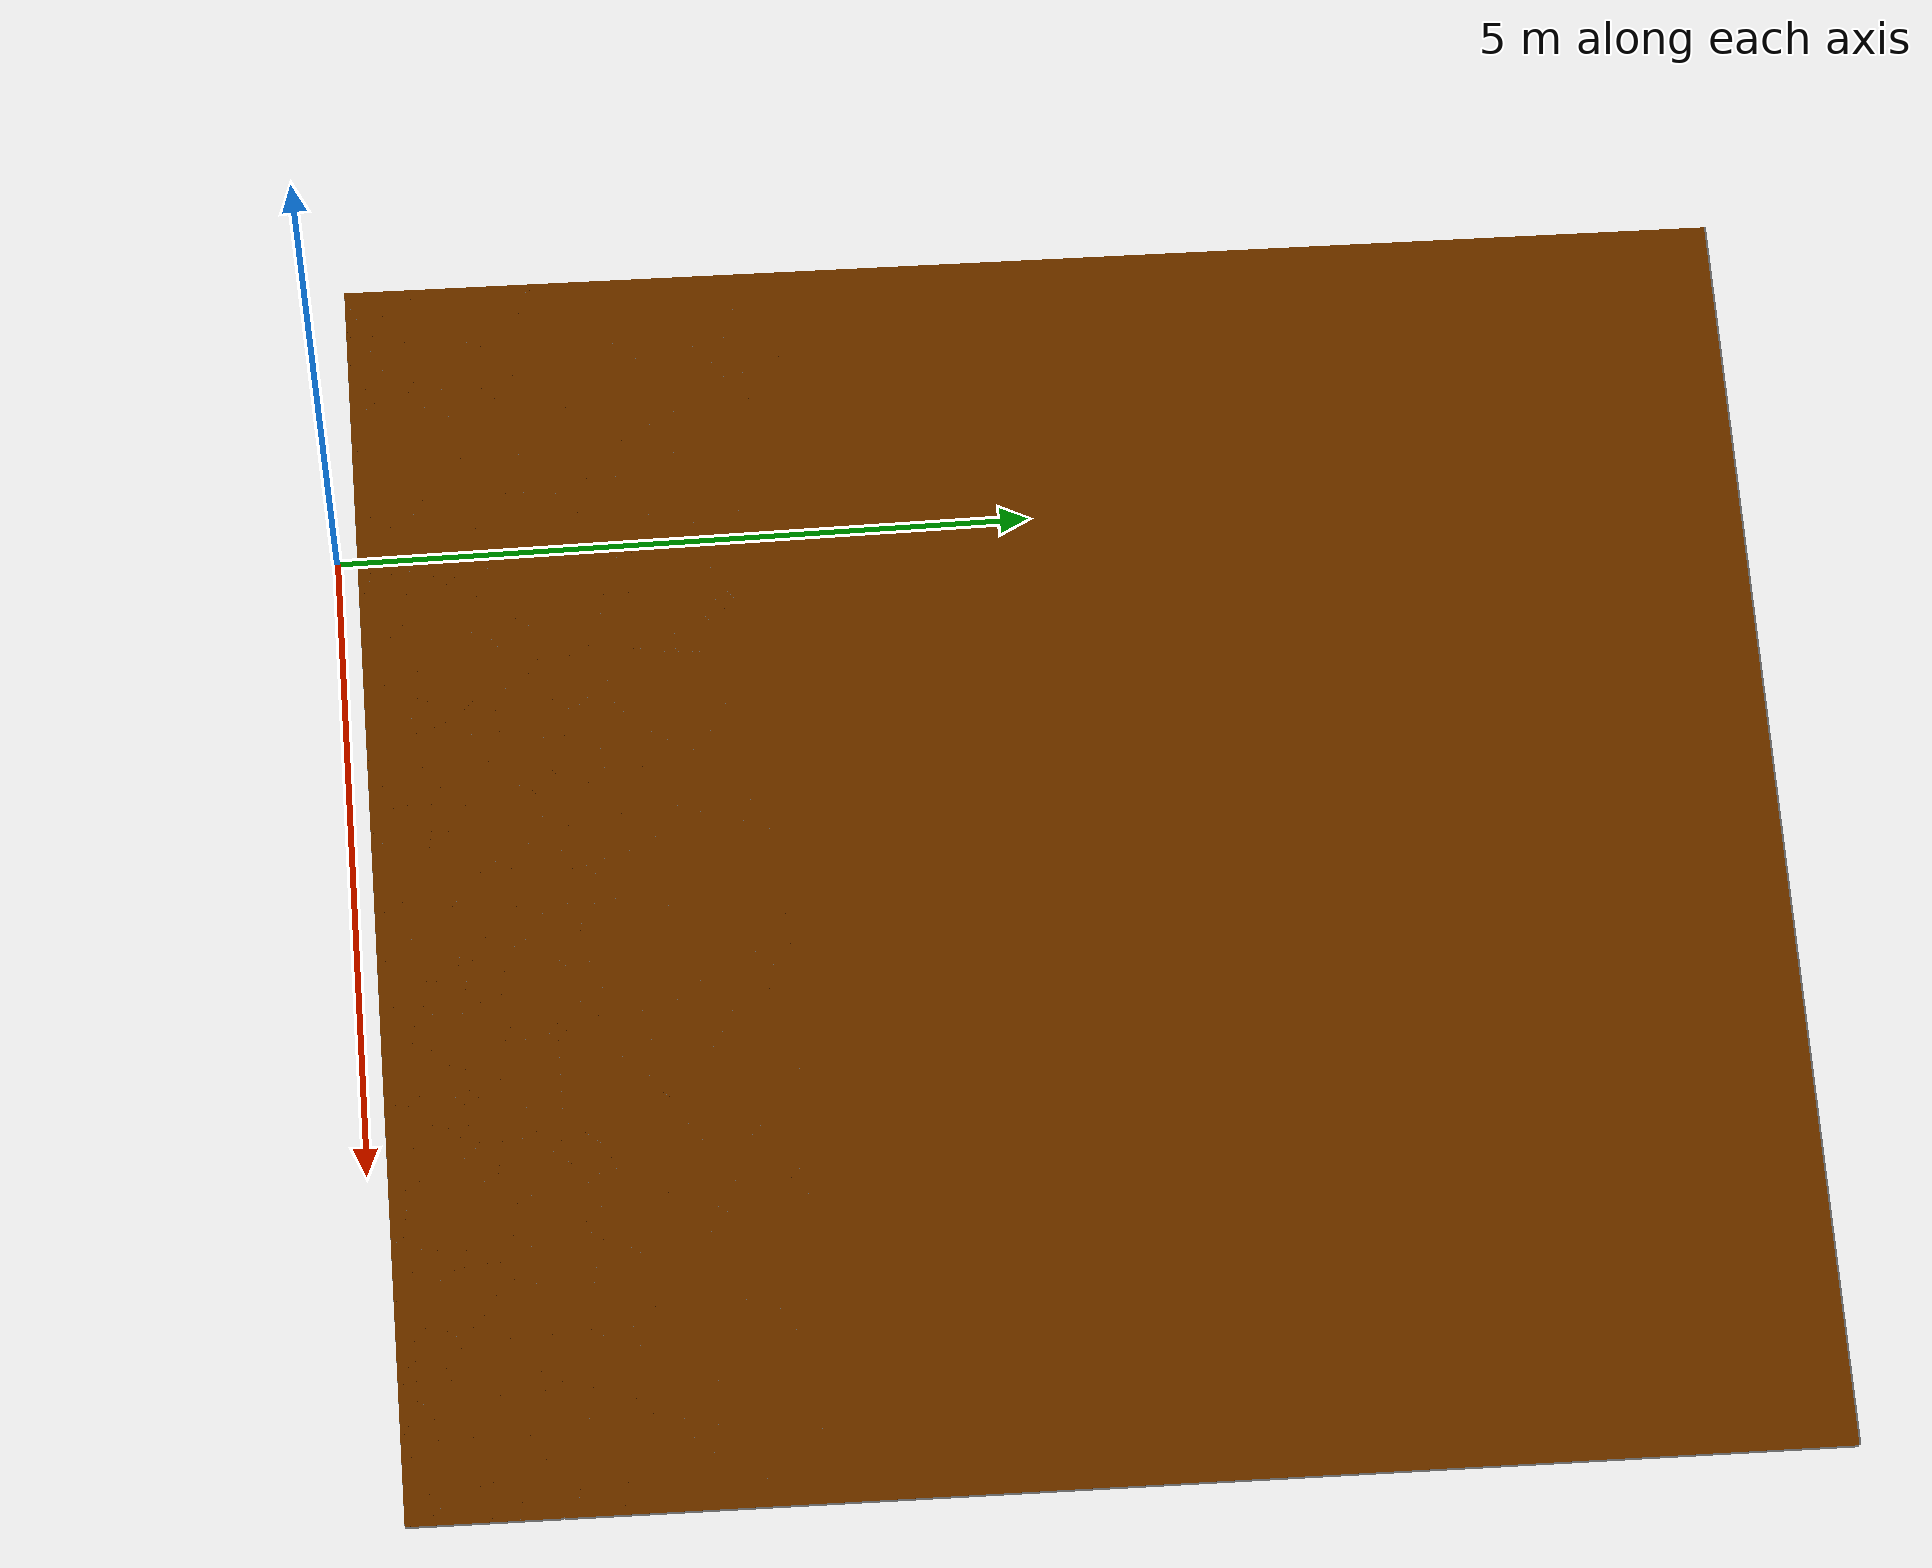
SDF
<?xml version='1.0'?>
<sdf version='1.7'>
  <model name='xiepo0702'>
    <pose>2.87654 5.07718 0 0 -0 0</pose>
    <link name='Stairs_1'>
      <visual name='Stairs_1_Visual_0'>
        <pose>-0 5.07217 0.00015 0 -0 0</pose>
        <geometry>
          <box>
            <size>10 0.01 0.0003</size>
          </box>
        </geometry>
        <material>
          <script>
            <uri>file://media/materials/scripts/gazebo.material</uri>
            <name>Gazebo/Grey</name>
          </script>
          <ambient>0.996078 0.47451 0.0196078 1</ambient>
        </material>
        <meta>
          <layer>0</layer>
        </meta>
      </visual>
      <collision name='Stairs_1_Collision_0'>
        <geometry>
          <box>
            <size>10 0.01 0.0003</size>
          </box>
        </geometry>
        <pose>-0 5.07217 0.00015 0 -0 0</pose>
      </collision>
      <visual name='Stairs_1_Visual_1'>
        <pose>-0 5.06217 0.00045 0 -0 0</pose>
        <geometry>
          <box>
            <size>10 0.01 0.0003</size>
          </box>
        </geometry>
        <material>
          <script>
            <uri>file://media/materials/scripts/gazebo.material</uri>
            <name>Gazebo/Grey</name>
          </script>
          <ambient>0.996078 0.47451 0.0196078 1</ambient>
        </material>
        <meta>
          <layer>0</layer>
        </meta>
      </visual>
      <collision name='Stairs_1_Collision_1'>
        <geometry>
          <box>
            <size>10 0.01 0.0003</size>
          </box>
        </geometry>
        <pose>-0 5.06217 0.00045 0 -0 0</pose>
      </collision>
      <visual name='Stairs_1_Visual_2'>
        <pose>-0 5.05218 0.00075 0 -0 0</pose>
        <geometry>
          <box>
            <size>10 0.01 0.0003</size>
          </box>
        </geometry>
        <material>
          <script>
            <uri>file://media/materials/scripts/gazebo.material</uri>
            <name>Gazebo/Grey</name>
          </script>
          <ambient>0.996078 0.47451 0.0196078 1</ambient>
        </material>
        <meta>
          <layer>0</layer>
        </meta>
      </visual>
      <collision name='Stairs_1_Collision_2'>
        <geometry>
          <box>
            <size>10 0.01 0.0003</size>
          </box>
        </geometry>
        <pose>-0 5.05218 0.00075 0 -0 0</pose>
      </collision>
      <visual name='Stairs_1_Visual_3'>
        <pose>-0 5.04218 0.00105 0 -0 0</pose>
        <geometry>
          <box>
            <size>10 0.01 0.0003</size>
          </box>
        </geometry>
        <material>
          <script>
            <uri>file://media/materials/scripts/gazebo.material</uri>
            <name>Gazebo/Grey</name>
          </script>
          <ambient>0.996078 0.47451 0.0196078 1</ambient>
        </material>
        <meta>
          <layer>0</layer>
        </meta>
      </visual>
      <collision name='Stairs_1_Collision_3'>
        <geometry>
          <box>
            <size>10 0.01 0.0003</size>
          </box>
        </geometry>
        <pose>-0 5.04218 0.00105 0 -0 0</pose>
      </collision>
      <visual name='Stairs_1_Visual_4'>
        <pose>-0 5.03218 0.00135 0 -0 0</pose>
        <geometry>
          <box>
            <size>10 0.01 0.0003</size>
          </box>
        </geometry>
        <material>
          <script>
            <uri>file://media/materials/scripts/gazebo.material</uri>
            <name>Gazebo/Grey</name>
          </script>
          <ambient>0.996078 0.47451 0.0196078 1</ambient>
        </material>
        <meta>
          <layer>0</layer>
        </meta>
      </visual>
      <collision name='Stairs_1_Collision_4'>
        <geometry>
          <box>
            <size>10 0.01 0.0003</size>
          </box>
        </geometry>
        <pose>-0 5.03218 0.00135 0 -0 0</pose>
      </collision>
      <visual name='Stairs_1_Visual_5'>
        <pose>-0 5.02217 0.00165 0 -0 0</pose>
        <geometry>
          <box>
            <size>10 0.01 0.0003</size>
          </box>
        </geometry>
        <material>
          <script>
            <uri>file://media/materials/scripts/gazebo.material</uri>
            <name>Gazebo/Grey</name>
          </script>
          <ambient>0.996078 0.47451 0.0196078 1</ambient>
        </material>
        <meta>
          <layer>0</layer>
        </meta>
      </visual>
      <collision name='Stairs_1_Collision_5'>
        <geometry>
          <box>
            <size>10 0.01 0.0003</size>
          </box>
        </geometry>
        <pose>-0 5.02217 0.00165 0 -0 0</pose>
      </collision>
      <visual name='Stairs_1_Visual_6'>
        <pose>-0 5.01218 0.00195 0 -0 0</pose>
        <geometry>
          <box>
            <size>10 0.01 0.0003</size>
          </box>
        </geometry>
        <material>
          <script>
            <uri>file://media/materials/scripts/gazebo.material</uri>
            <name>Gazebo/Grey</name>
          </script>
          <ambient>0.996078 0.47451 0.0196078 1</ambient>
        </material>
        <meta>
          <layer>0</layer>
        </meta>
      </visual>
      <collision name='Stairs_1_Collision_6'>
        <geometry>
          <box>
            <size>10 0.01 0.0003</size>
          </box>
        </geometry>
        <pose>-0 5.01218 0.00195 0 -0 0</pose>
      </collision>
      <visual name='Stairs_1_Visual_7'>
        <pose>-0 5.00218 0.00225 0 -0 0</pose>
        <geometry>
          <box>
            <size>10 0.01 0.0003</size>
          </box>
        </geometry>
        <material>
          <script>
            <uri>file://media/materials/scripts/gazebo.material</uri>
            <name>Gazebo/Grey</name>
          </script>
          <ambient>0.996078 0.47451 0.0196078 1</ambient>
        </material>
        <meta>
          <layer>0</layer>
        </meta>
      </visual>
      <collision name='Stairs_1_Collision_7'>
        <geometry>
          <box>
            <size>10 0.01 0.0003</size>
          </box>
        </geometry>
        <pose>-0 5.00218 0.00225 0 -0 0</pose>
      </collision>
      <visual name='Stairs_1_Visual_8'>
        <pose>-0 4.99217 0.00255 0 -0 0</pose>
        <geometry>
          <box>
            <size>10 0.01 0.0003</size>
          </box>
        </geometry>
        <material>
          <script>
            <uri>file://media/materials/scripts/gazebo.material</uri>
            <name>Gazebo/Grey</name>
          </script>
          <ambient>0.996078 0.47451 0.0196078 1</ambient>
        </material>
        <meta>
          <layer>0</layer>
        </meta>
      </visual>
      <collision name='Stairs_1_Collision_8'>
        <geometry>
          <box>
            <size>10 0.01 0.0003</size>
          </box>
        </geometry>
        <pose>-0 4.99217 0.00255 0 -0 0</pose>
      </collision>
      <visual name='Stairs_1_Visual_9'>
        <pose>-0 4.98217 0.00285 0 -0 0</pose>
        <geometry>
          <box>
            <size>10 0.01 0.0003</size>
          </box>
        </geometry>
        <material>
          <script>
            <uri>file://media/materials/scripts/gazebo.material</uri>
            <name>Gazebo/Grey</name>
          </script>
          <ambient>0.996078 0.47451 0.0196078 1</ambient>
        </material>
        <meta>
          <layer>0</layer>
        </meta>
      </visual>
      <collision name='Stairs_1_Collision_9'>
        <geometry>
          <box>
            <size>10 0.01 0.0003</size>
          </box>
        </geometry>
        <pose>-0 4.98217 0.00285 0 -0 0</pose>
      </collision>
      <visual name='Stairs_1_Visual_10'>
        <pose>-0 4.97218 0.00315 0 -0 0</pose>
        <geometry>
          <box>
            <size>10 0.01 0.0003</size>
          </box>
        </geometry>
        <material>
          <script>
            <uri>file://media/materials/scripts/gazebo.material</uri>
            <name>Gazebo/Grey</name>
          </script>
          <ambient>0.996078 0.47451 0.0196078 1</ambient>
        </material>
        <meta>
          <layer>0</layer>
        </meta>
      </visual>
      <collision name='Stairs_1_Collision_10'>
        <geometry>
          <box>
            <size>10 0.01 0.0003</size>
          </box>
        </geometry>
        <pose>-0 4.97218 0.00315 0 -0 0</pose>
      </collision>
      <visual name='Stairs_1_Visual_11'>
        <pose>-0 4.96218 0.00345 0 -0 0</pose>
        <geometry>
          <box>
            <size>10 0.01 0.0003</size>
          </box>
        </geometry>
        <material>
          <script>
            <uri>file://media/materials/scripts/gazebo.material</uri>
            <name>Gazebo/Grey</name>
          </script>
          <ambient>0.996078 0.47451 0.0196078 1</ambient>
        </material>
        <meta>
          <layer>0</layer>
        </meta>
      </visual>
      <collision name='Stairs_1_Collision_11'>
        <geometry>
          <box>
            <size>10 0.01 0.0003</size>
          </box>
        </geometry>
        <pose>-0 4.96218 0.00345 0 -0 0</pose>
      </collision>
      <visual name='Stairs_1_Visual_12'>
        <pose>-0 4.95218 0.00375 0 -0 0</pose>
        <geometry>
          <box>
            <size>10 0.01 0.0003</size>
          </box>
        </geometry>
        <material>
          <script>
            <uri>file://media/materials/scripts/gazebo.material</uri>
            <name>Gazebo/Grey</name>
          </script>
          <ambient>0.996078 0.47451 0.0196078 1</ambient>
        </material>
        <meta>
          <layer>0</layer>
        </meta>
      </visual>
      <collision name='Stairs_1_Collision_12'>
        <geometry>
          <box>
            <size>10 0.01 0.0003</size>
          </box>
        </geometry>
        <pose>-0 4.95218 0.00375 0 -0 0</pose>
      </collision>
      <visual name='Stairs_1_Visual_13'>
        <pose>-0 4.94217 0.00405 0 -0 0</pose>
        <geometry>
          <box>
            <size>10 0.01 0.0003</size>
          </box>
        </geometry>
        <material>
          <script>
            <uri>file://media/materials/scripts/gazebo.material</uri>
            <name>Gazebo/Grey</name>
          </script>
          <ambient>0.996078 0.47451 0.0196078 1</ambient>
        </material>
        <meta>
          <layer>0</layer>
        </meta>
      </visual>
      <collision name='Stairs_1_Collision_13'>
        <geometry>
          <box>
            <size>10 0.01 0.0003</size>
          </box>
        </geometry>
        <pose>-0 4.94217 0.00405 0 -0 0</pose>
      </collision>
      <visual name='Stairs_1_Visual_14'>
        <pose>-0 4.93217 0.00435 0 -0 0</pose>
        <geometry>
          <box>
            <size>10 0.01 0.0003</size>
          </box>
        </geometry>
        <material>
          <script>
            <uri>file://media/materials/scripts/gazebo.material</uri>
            <name>Gazebo/Grey</name>
          </script>
          <ambient>0.996078 0.47451 0.0196078 1</ambient>
        </material>
        <meta>
          <layer>0</layer>
        </meta>
      </visual>
      <collision name='Stairs_1_Collision_14'>
        <geometry>
          <box>
            <size>10 0.01 0.0003</size>
          </box>
        </geometry>
        <pose>-0 4.93217 0.00435 0 -0 0</pose>
      </collision>
      <visual name='Stairs_1_Visual_15'>
        <pose>-0 4.92218 0.00465 0 -0 0</pose>
        <geometry>
          <box>
            <size>10 0.01 0.0003</size>
          </box>
        </geometry>
        <material>
          <script>
            <uri>file://media/materials/scripts/gazebo.material</uri>
            <name>Gazebo/Grey</name>
          </script>
          <ambient>0.996078 0.47451 0.0196078 1</ambient>
        </material>
        <meta>
          <layer>0</layer>
        </meta>
      </visual>
      <collision name='Stairs_1_Collision_15'>
        <geometry>
          <box>
            <size>10 0.01 0.0003</size>
          </box>
        </geometry>
        <pose>-0 4.92218 0.00465 0 -0 0</pose>
      </collision>
      <visual name='Stairs_1_Visual_16'>
        <pose>-0 4.91218 0.00495 0 -0 0</pose>
        <geometry>
          <box>
            <size>10 0.01 0.0003</size>
          </box>
        </geometry>
        <material>
          <script>
            <uri>file://media/materials/scripts/gazebo.material</uri>
            <name>Gazebo/Grey</name>
          </script>
          <ambient>0.996078 0.47451 0.0196078 1</ambient>
        </material>
        <meta>
          <layer>0</layer>
        </meta>
      </visual>
      <collision name='Stairs_1_Collision_16'>
        <geometry>
          <box>
            <size>10 0.01 0.0003</size>
          </box>
        </geometry>
        <pose>-0 4.91218 0.00495 0 -0 0</pose>
      </collision>
      <visual name='Stairs_1_Visual_17'>
        <pose>-0 4.90217 0.00525 0 -0 0</pose>
        <geometry>
          <box>
            <size>10 0.01 0.0003</size>
          </box>
        </geometry>
        <material>
          <script>
            <uri>file://media/materials/scripts/gazebo.material</uri>
            <name>Gazebo/Grey</name>
          </script>
          <ambient>0.996078 0.47451 0.0196078 1</ambient>
        </material>
        <meta>
          <layer>0</layer>
        </meta>
      </visual>
      <collision name='Stairs_1_Collision_17'>
        <geometry>
          <box>
            <size>10 0.01 0.0003</size>
          </box>
        </geometry>
        <pose>-0 4.90217 0.00525 0 -0 0</pose>
      </collision>
      <visual name='Stairs_1_Visual_18'>
        <pose>-0 4.89217 0.00555 0 -0 0</pose>
        <geometry>
          <box>
            <size>10 0.01 0.0003</size>
          </box>
        </geometry>
        <material>
          <script>
            <uri>file://media/materials/scripts/gazebo.material</uri>
            <name>Gazebo/Grey</name>
          </script>
          <ambient>0.996078 0.47451 0.0196078 1</ambient>
        </material>
        <meta>
          <layer>0</layer>
        </meta>
      </visual>
      <collision name='Stairs_1_Collision_18'>
        <geometry>
          <box>
            <size>10 0.01 0.0003</size>
          </box>
        </geometry>
        <pose>-0 4.89217 0.00555 0 -0 0</pose>
      </collision>
      <visual name='Stairs_1_Visual_19'>
        <pose>-0 4.88218 0.00585 0 -0 0</pose>
        <geometry>
          <box>
            <size>10 0.01 0.0003</size>
          </box>
        </geometry>
        <material>
          <script>
            <uri>file://media/materials/scripts/gazebo.material</uri>
            <name>Gazebo/Grey</name>
          </script>
          <ambient>0.996078 0.47451 0.0196078 1</ambient>
        </material>
        <meta>
          <layer>0</layer>
        </meta>
      </visual>
      <collision name='Stairs_1_Collision_19'>
        <geometry>
          <box>
            <size>10 0.01 0.0003</size>
          </box>
        </geometry>
        <pose>-0 4.88218 0.00585 0 -0 0</pose>
      </collision>
      <visual name='Stairs_1_Visual_20'>
        <pose>-0 4.87218 0.00615 0 -0 0</pose>
        <geometry>
          <box>
            <size>10 0.01 0.0003</size>
          </box>
        </geometry>
        <material>
          <script>
            <uri>file://media/materials/scripts/gazebo.material</uri>
            <name>Gazebo/Grey</name>
          </script>
          <ambient>0.996078 0.47451 0.0196078 1</ambient>
        </material>
        <meta>
          <layer>0</layer>
        </meta>
      </visual>
      <collision name='Stairs_1_Collision_20'>
        <geometry>
          <box>
            <size>10 0.01 0.0003</size>
          </box>
        </geometry>
        <pose>-0 4.87218 0.00615 0 -0 0</pose>
      </collision>
      <visual name='Stairs_1_Visual_21'>
        <pose>-0 4.86217 0.00645 0 -0 0</pose>
        <geometry>
          <box>
            <size>10 0.01 0.0003</size>
          </box>
        </geometry>
        <material>
          <script>
            <uri>file://media/materials/scripts/gazebo.material</uri>
            <name>Gazebo/Grey</name>
          </script>
          <ambient>0.996078 0.47451 0.0196078 1</ambient>
        </material>
        <meta>
          <layer>0</layer>
        </meta>
      </visual>
      <collision name='Stairs_1_Collision_21'>
        <geometry>
          <box>
            <size>10 0.01 0.0003</size>
          </box>
        </geometry>
        <pose>-0 4.86217 0.00645 0 -0 0</pose>
      </collision>
      <visual name='Stairs_1_Visual_22'>
        <pose>-0 4.85217 0.00675 0 -0 0</pose>
        <geometry>
          <box>
            <size>10 0.01 0.0003</size>
          </box>
        </geometry>
        <material>
          <script>
            <uri>file://media/materials/scripts/gazebo.material</uri>
            <name>Gazebo/Grey</name>
          </script>
          <ambient>0.996078 0.47451 0.0196078 1</ambient>
        </material>
        <meta>
          <layer>0</layer>
        </meta>
      </visual>
      <collision name='Stairs_1_Collision_22'>
        <geometry>
          <box>
            <size>10 0.01 0.0003</size>
          </box>
        </geometry>
        <pose>-0 4.85217 0.00675 0 -0 0</pose>
      </collision>
      <visual name='Stairs_1_Visual_23'>
        <pose>-0 4.84218 0.00705 0 -0 0</pose>
        <geometry>
          <box>
            <size>10 0.01 0.0003</size>
          </box>
        </geometry>
        <material>
          <script>
            <uri>file://media/materials/scripts/gazebo.material</uri>
            <name>Gazebo/Grey</name>
          </script>
          <ambient>0.996078 0.47451 0.0196078 1</ambient>
        </material>
        <meta>
          <layer>0</layer>
        </meta>
      </visual>
      <collision name='Stairs_1_Collision_23'>
        <geometry>
          <box>
            <size>10 0.01 0.0003</size>
          </box>
        </geometry>
        <pose>-0 4.84218 0.00705 0 -0 0</pose>
      </collision>
      <visual name='Stairs_1_Visual_24'>
        <pose>-0 4.83218 0.00735 0 -0 0</pose>
        <geometry>
          <box>
            <size>10 0.01 0.0003</size>
          </box>
        </geometry>
        <material>
          <script>
            <uri>file://media/materials/scripts/gazebo.material</uri>
            <name>Gazebo/Grey</name>
          </script>
          <ambient>0.996078 0.47451 0.0196078 1</ambient>
        </material>
        <meta>
          <layer>0</layer>
        </meta>
      </visual>
      <collision name='Stairs_1_Collision_24'>
        <geometry>
          <box>
            <size>10 0.01 0.0003</size>
          </box>
        </geometry>
        <pose>-0 4.83218 0.00735 0 -0 0</pose>
      </collision>
      <visual name='Stairs_1_Visual_25'>
        <pose>-0 4.82217 0.00765 0 -0 0</pose>
        <geometry>
          <box>
            <size>10 0.01 0.0003</size>
          </box>
        </geometry>
        <material>
          <script>
            <uri>file://media/materials/scripts/gazebo.material</uri>
            <name>Gazebo/Grey</name>
          </script>
          <ambient>0.996078 0.47451 0.0196078 1</ambient>
        </material>
        <meta>
          <layer>0</layer>
        </meta>
      </visual>
      <collision name='Stairs_1_Collision_25'>
        <geometry>
          <box>
            <size>10 0.01 0.0003</size>
          </box>
        </geometry>
        <pose>-0 4.82217 0.00765 0 -0 0</pose>
      </collision>
      <visual name='Stairs_1_Visual_26'>
        <pose>-0 4.81217 0.00795 0 -0 0</pose>
        <geometry>
          <box>
            <size>10 0.01 0.0003</size>
          </box>
        </geometry>
        <material>
          <script>
            <uri>file://media/materials/scripts/gazebo.material</uri>
            <name>Gazebo/Grey</name>
          </script>
          <ambient>0.996078 0.47451 0.0196078 1</ambient>
        </material>
        <meta>
          <layer>0</layer>
        </meta>
      </visual>
      <collision name='Stairs_1_Collision_26'>
        <geometry>
          <box>
            <size>10 0.01 0.0003</size>
          </box>
        </geometry>
        <pose>-0 4.81217 0.00795 0 -0 0</pose>
      </collision>
      <visual name='Stairs_1_Visual_27'>
        <pose>-0 4.80218 0.00825 0 -0 0</pose>
        <geometry>
          <box>
            <size>10 0.01 0.0003</size>
          </box>
        </geometry>
        <material>
          <script>
            <uri>file://media/materials/scripts/gazebo.material</uri>
            <name>Gazebo/Grey</name>
          </script>
          <ambient>0.996078 0.47451 0.0196078 1</ambient>
        </material>
        <meta>
          <layer>0</layer>
        </meta>
      </visual>
      <collision name='Stairs_1_Collision_27'>
        <geometry>
          <box>
            <size>10 0.01 0.0003</size>
          </box>
        </geometry>
        <pose>-0 4.80218 0.00825 0 -0 0</pose>
      </collision>
      <visual name='Stairs_1_Visual_28'>
        <pose>-0 4.79218 0.00855 0 -0 0</pose>
        <geometry>
          <box>
            <size>10 0.01 0.0003</size>
          </box>
        </geometry>
        <material>
          <script>
            <uri>file://media/materials/scripts/gazebo.material</uri>
            <name>Gazebo/Grey</name>
          </script>
          <ambient>0.996078 0.47451 0.0196078 1</ambient>
        </material>
        <meta>
          <layer>0</layer>
        </meta>
      </visual>
      <collision name='Stairs_1_Collision_28'>
        <geometry>
          <box>
            <size>10 0.01 0.0003</size>
          </box>
        </geometry>
        <pose>-0 4.79218 0.00855 0 -0 0</pose>
      </collision>
      <visual name='Stairs_1_Visual_29'>
        <pose>-0 4.78218 0.00885 0 -0 0</pose>
        <geometry>
          <box>
            <size>10 0.01 0.0003</size>
          </box>
        </geometry>
        <material>
          <script>
            <uri>file://media/materials/scripts/gazebo.material</uri>
            <name>Gazebo/Grey</name>
          </script>
          <ambient>0.996078 0.47451 0.0196078 1</ambient>
        </material>
        <meta>
          <layer>0</layer>
        </meta>
      </visual>
      <collision name='Stairs_1_Collision_29'>
        <geometry>
          <box>
            <size>10 0.01 0.0003</size>
          </box>
        </geometry>
        <pose>-0 4.78218 0.00885 0 -0 0</pose>
      </collision>
      <visual name='Stairs_1_Visual_30'>
        <pose>-0 4.77217 0.00915 0 -0 0</pose>
        <geometry>
          <box>
            <size>10 0.01 0.0003</size>
          </box>
        </geometry>
        <material>
          <script>
            <uri>file://media/materials/scripts/gazebo.material</uri>
            <name>Gazebo/Grey</name>
          </script>
          <ambient>0.996078 0.47451 0.0196078 1</ambient>
        </material>
        <meta>
          <layer>0</layer>
        </meta>
      </visual>
      <collision name='Stairs_1_Collision_30'>
        <geometry>
          <box>
            <size>10 0.01 0.0003</size>
          </box>
        </geometry>
        <pose>-0 4.77217 0.00915 0 -0 0</pose>
      </collision>
      <visual name='Stairs_1_Visual_31'>
        <pose>-0 4.76218 0.00945 0 -0 0</pose>
        <geometry>
          <box>
            <size>10 0.01 0.0003</size>
          </box>
        </geometry>
        <material>
          <script>
            <uri>file://media/materials/scripts/gazebo.material</uri>
            <name>Gazebo/Grey</name>
          </script>
          <ambient>0.996078 0.47451 0.0196078 1</ambient>
        </material>
        <meta>
          <layer>0</layer>
        </meta>
      </visual>
      <collision name='Stairs_1_Collision_31'>
        <geometry>
          <box>
            <size>10 0.01 0.0003</size>
          </box>
        </geometry>
        <pose>-0 4.76218 0.00945 0 -0 0</pose>
      </collision>
      <visual name='Stairs_1_Visual_32'>
        <pose>-0 4.75218 0.00975 0 -0 0</pose>
        <geometry>
          <box>
            <size>10 0.01 0.0003</size>
          </box>
        </geometry>
        <material>
          <script>
            <uri>file://media/materials/scripts/gazebo.material</uri>
            <name>Gazebo/Grey</name>
          </script>
          <ambient>0.996078 0.47451 0.0196078 1</ambient>
        </material>
        <meta>
          <layer>0</layer>
        </meta>
      </visual>
      <collision name='Stairs_1_Collision_32'>
        <geometry>
          <box>
            <size>10 0.01 0.0003</size>
          </box>
        </geometry>
        <pose>-0 4.75218 0.00975 0 -0 0</pose>
      </collision>
      <visual name='Stairs_1_Visual_33'>
        <pose>-0 4.74217 0.01005 0 -0 0</pose>
        <geometry>
          <box>
            <size>10 0.01 0.0003</size>
          </box>
        </geometry>
        <material>
          <script>
            <uri>file://media/materials/scripts/gazebo.material</uri>
            <name>Gazebo/Grey</name>
          </script>
          <ambient>0.996078 0.47451 0.0196078 1</ambient>
        </material>
        <meta>
          <layer>0</layer>
        </meta>
      </visual>
      <collision name='Stairs_1_Collision_33'>
        <geometry>
          <box>
            <size>10 0.01 0.0003</size>
          </box>
        </geometry>
        <pose>-0 4.74217 0.01005 0 -0 0</pose>
      </collision>
      <visual name='Stairs_1_Visual_34'>
        <pose>-0 4.73217 0.01035 0 -0 0</pose>
        <geometry>
          <box>
            <size>10 0.01 0.0003</size>
          </box>
        </geometry>
        <material>
          <script>
            <uri>file://media/materials/scripts/gazebo.material</uri>
            <name>Gazebo/Grey</name>
          </script>
          <ambient>0.996078 0.47451 0.0196078 1</ambient>
        </material>
        <meta>
          <layer>0</layer>
        </meta>
      </visual>
      <collision name='Stairs_1_Collision_34'>
        <geometry>
          <box>
            <size>10 0.01 0.0003</size>
          </box>
        </geometry>
        <pose>-0 4.73217 0.01035 0 -0 0</pose>
      </collision>
      <visual name='Stairs_1_Visual_35'>
        <pose>-0 4.72218 0.01065 0 -0 0</pose>
        <geometry>
          <box>
            <size>10 0.01 0.0003</size>
          </box>
        </geometry>
        <material>
          <script>
            <uri>file://media/materials/scripts/gazebo.material</uri>
            <name>Gazebo/Grey</name>
          </script>
          <ambient>0.996078 0.47451 0.0196078 1</ambient>
        </material>
        <meta>
          <layer>0</layer>
        </meta>
      </visual>
      <collision name='Stairs_1_Collision_35'>
        <geometry>
          <box>
            <size>10 0.01 0.0003</size>
          </box>
        </geometry>
        <pose>-0 4.72218 0.01065 0 -0 0</pose>
      </collision>
      <visual name='Stairs_1_Visual_36'>
        <pose>-0 4.71218 0.01095 0 -0 0</pose>
        <geometry>
          <box>
            <size>10 0.01 0.0003</size>
          </box>
        </geometry>
        <material>
          <script>
            <uri>file://media/materials/scripts/gazebo.material</uri>
            <name>Gazebo/Grey</name>
          </script>
          <ambient>0.996078 0.47451 0.0196078 1</ambient>
        </material>
        <meta>
          <layer>0</layer>
        </meta>
      </visual>
      <collision name='Stairs_1_Collision_36'>
        <geometry>
          <box>
            <size>10 0.01 0.0003</size>
          </box>
        </geometry>
        <pose>-0 4.71218 0.01095 0 -0 0</pose>
      </collision>
      <visual name='Stairs_1_Visual_37'>
        <pose>-0 4.70218 0.01125 0 -0 0</pose>
        <geometry>
          <box>
            <size>10 0.01 0.0003</size>
          </box>
        </geometry>
        <material>
          <script>
            <uri>file://media/materials/scripts/gazebo.material</uri>
            <name>Gazebo/Grey</name>
          </script>
          <ambient>0.996078 0.47451 0.0196078 1</ambient>
        </material>
        <meta>
          <layer>0</layer>
        </meta>
      </visual>
      <collision name='Stairs_1_Collision_37'>
        <geometry>
          <box>
            <size>10 0.01 0.0003</size>
          </box>
        </geometry>
        <pose>-0 4.70218 0.01125 0 -0 0</pose>
      </collision>
      <visual name='Stairs_1_Visual_38'>
        <pose>-0 4.69217 0.01155 0 -0 0</pose>
        <geometry>
          <box>
            <size>10 0.01 0.0003</size>
          </box>
        </geometry>
        <material>
          <script>
            <uri>file://media/materials/scripts/gazebo.material</uri>
            <name>Gazebo/Grey</name>
          </script>
          <ambient>0.996078 0.47451 0.0196078 1</ambient>
        </material>
        <meta>
          <layer>0</layer>
        </meta>
      </visual>
      <collision name='Stairs_1_Collision_38'>
        <geometry>
          <box>
            <size>10 0.01 0.0003</size>
          </box>
        </geometry>
        <pose>-0 4.69217 0.01155 0 -0 0</pose>
      </collision>
      <visual name='Stairs_1_Visual_39'>
        <pose>-0 4.68217 0.01185 0 -0 0</pose>
        <geometry>
          <box>
            <size>10 0.01 0.0003</size>
          </box>
        </geometry>
        <material>
          <script>
            <uri>file://media/materials/scripts/gazebo.material</uri>
            <name>Gazebo/Grey</name>
          </script>
          <ambient>0.996078 0.47451 0.0196078 1</ambient>
        </material>
        <meta>
          <layer>0</layer>
        </meta>
      </visual>
      <collision name='Stairs_1_Collision_39'>
        <geometry>
          <box>
            <size>10 0.01 0.0003</size>
          </box>
        </geometry>
        <pose>-0 4.68217 0.01185 0 -0 0</pose>
      </collision>
      <visual name='Stairs_1_Visual_40'>
        <pose>-0 4.67218 0.01215 0 -0 0</pose>
        <geometry>
          <box>
            <size>10 0.01 0.0003</size>
          </box>
        </geometry>
        <material>
          <script>
            <uri>file://media/materials/scripts/gazebo.material</uri>
            <name>Gazebo/Grey</name>
          </script>
          <ambient>0.996078 0.47451 0.0196078 1</ambient>
        </material>
        <meta>
          <layer>0</layer>
        </meta>
      </visual>
      <collision name='Stairs_1_Collision_40'>
        <geometry>
          <box>
            <size>10 0.01 0.0003</size>
          </box>
        </geometry>
        <pose>-0 4.67218 0.01215 0 -0 0</pose>
      </collision>
      <visual name='Stairs_1_Visual_41'>
        <pose>-0 4.66218 0.01245 0 -0 0</pose>
        <geometry>
          <box>
            <size>10 0.01 0.0003</size>
          </box>
        </geometry>
        <material>
          <script>
            <uri>file://media/materials/scripts/gazebo.material</uri>
            <name>Gazebo/Grey</name>
          </script>
          <ambient>0.996078 0.47451 0.0196078 1</ambient>
        </material>
        <meta>
          <layer>0</layer>
        </meta>
      </visual>
      <collision name='Stairs_1_Collision_41'>
        <geometry>
          <box>
            <size>10 0.01 0.0003</size>
          </box>
        </geometry>
        <pose>-0 4.66218 0.01245 0 -0 0</pose>
      </collision>
      <visual name='Stairs_1_Visual_42'>
        <pose>-0 4.65217 0.01275 0 -0 0</pose>
        <geometry>
          <box>
            <size>10 0.01 0.0003</size>
          </box>
        </geometry>
        <material>
          <script>
            <uri>file://media/materials/scripts/gazebo.material</uri>
            <name>Gazebo/Grey</name>
          </script>
          <ambient>0.996078 0.47451 0.0196078 1</ambient>
        </material>
        <meta>
          <layer>0</layer>
        </meta>
      </visual>
      <collision name='Stairs_1_Collision_42'>
        <geometry>
          <box>
            <size>10 0.01 0.0003</size>
          </box>
        </geometry>
        <pose>-0 4.65217 0.01275 0 -0 0</pose>
      </collision>
      <visual name='Stairs_1_Visual_43'>
        <pose>-0 4.64217 0.01305 0 -0 0</pose>
        <geometry>
          <box>
            <size>10 0.01 0.0003</size>
          </box>
        </geometry>
        <material>
          <script>
            <uri>file://media/materials/scripts/gazebo.material</uri>
            <name>Gazebo/Grey</name>
          </script>
          <ambient>0.996078 0.47451 0.0196078 1</ambient>
        </material>
        <meta>
          <layer>0</layer>
        </meta>
      </visual>
      <collision name='Stairs_1_Collision_43'>
        <geometry>
          <box>
            <size>10 0.01 0.0003</size>
          </box>
        </geometry>
        <pose>-0 4.64217 0.01305 0 -0 0</pose>
      </collision>
      <visual name='Stairs_1_Visual_44'>
        <pose>-0 4.63218 0.01335 0 -0 0</pose>
        <geometry>
          <box>
            <size>10 0.01 0.0003</size>
          </box>
        </geometry>
        <material>
          <script>
            <uri>file://media/materials/scripts/gazebo.material</uri>
            <name>Gazebo/Grey</name>
          </script>
          <ambient>0.996078 0.47451 0.0196078 1</ambient>
        </material>
        <meta>
          <layer>0</layer>
        </meta>
      </visual>
      <collision name='Stairs_1_Collision_44'>
        <geometry>
          <box>
            <size>10 0.01 0.0003</size>
          </box>
        </geometry>
        <pose>-0 4.63218 0.01335 0 -0 0</pose>
      </collision>
      <visual name='Stairs_1_Visual_45'>
        <pose>-0 4.62218 0.01365 0 -0 0</pose>
        <geometry>
          <box>
            <size>10 0.01 0.0003</size>
          </box>
        </geometry>
        <material>
          <script>
            <uri>file://media/materials/scripts/gazebo.material</uri>
            <name>Gazebo/Grey</name>
          </script>
          <ambient>0.996078 0.47451 0.0196078 1</ambient>
        </material>
        <meta>
          <layer>0</layer>
        </meta>
      </visual>
      <collision name='Stairs_1_Collision_45'>
        <geometry>
          <box>
            <size>10 0.01 0.0003</size>
          </box>
        </geometry>
        <pose>-0 4.62218 0.01365 0 -0 0</pose>
      </collision>
      <visual name='Stairs_1_Visual_46'>
        <pose>-0 4.61217 0.01395 0 -0 0</pose>
        <geometry>
          <box>
            <size>10 0.01 0.0003</size>
          </box>
        </geometry>
        <material>
          <script>
            <uri>file://media/materials/scripts/gazebo.material</uri>
            <name>Gazebo/Grey</name>
          </script>
          <ambient>0.996078 0.47451 0.0196078 1</ambient>
        </material>
        <meta>
          <layer>0</layer>
        </meta>
      </visual>
      <collision name='Stairs_1_Collision_46'>
        <geometry>
          <box>
            <size>10 0.01 0.0003</size>
          </box>
        </geometry>
        <pose>-0 4.61217 0.01395 0 -0 0</pose>
      </collision>
      <visual name='Stairs_1_Visual_47'>
        <pose>-0 4.60217 0.01425 0 -0 0</pose>
        <geometry>
          <box>
            <size>10 0.01 0.0003</size>
          </box>
        </geometry>
        <material>
          <script>
            <uri>file://media/materials/scripts/gazebo.material</uri>
            <name>Gazebo/Grey</name>
          </script>
          <ambient>0.996078 0.47451 0.0196078 1</ambient>
        </material>
        <meta>
          <layer>0</layer>
        </meta>
      </visual>
      <collision name='Stairs_1_Collision_47'>
        <geometry>
          <box>
            <size>10 0.01 0.0003</size>
          </box>
        </geometry>
        <pose>-0 4.60217 0.01425 0 -0 0</pose>
      </collision>
      <visual name='Stairs_1_Visual_48'>
        <pose>-0 4.59218 0.01455 0 -0 0</pose>
        <geometry>
          <box>
            <size>10 0.01 0.0003</size>
          </box>
        </geometry>
        <material>
          <script>
            <uri>file://media/materials/scripts/gazebo.material</uri>
            <name>Gazebo/Grey</name>
          </script>
          <ambient>0.996078 0.47451 0.0196078 1</ambient>
        </material>
        <meta>
          <layer>0</layer>
        </meta>
      </visual>
      <collision name='Stairs_1_Collision_48'>
        <geometry>
          <box>
            <size>10 0.01 0.0003</size>
          </box>
        </geometry>
        <pose>-0 4.59218 0.01455 0 -0 0</pose>
      </collision>
      <visual name='Stairs_1_Visual_49'>
        <pose>-0 4.58218 0.01485 0 -0 0</pose>
        <geometry>
          <box>
            <size>10 0.01 0.0003</size>
          </box>
        </geometry>
        <material>
          <script>
            <uri>file://media/materials/scripts/gazebo.material</uri>
            <name>Gazebo/Grey</name>
          </script>
          <ambient>0.996078 0.47451 0.0196078 1</ambient>
        </material>
        <meta>
          <layer>0</layer>
        </meta>
      </visual>
      <collision name='Stairs_1_Collision_49'>
        <geometry>
          <box>
            <size>10 0.01 0.0003</size>
          </box>
        </geometry>
        <pose>-0 4.58218 0.01485 0 -0 0</pose>
      </collision>
      <visual name='Stairs_1_Visual_50'>
        <pose>-0 4.57217 0.01515 0 -0 0</pose>
        <geometry>
          <box>
            <size>10 0.01 0.0003</size>
          </box>
        </geometry>
        <material>
          <script>
            <uri>file://media/materials/scripts/gazebo.material</uri>
            <name>Gazebo/Grey</name>
          </script>
          <ambient>0.996078 0.47451 0.0196078 1</ambient>
        </material>
        <meta>
          <layer>0</layer>
        </meta>
      </visual>
      <collision name='Stairs_1_Collision_50'>
        <geometry>
          <box>
            <size>10 0.01 0.0003</size>
          </box>
        </geometry>
        <pose>-0 4.57217 0.01515 0 -0 0</pose>
      </collision>
      <visual name='Stairs_1_Visual_51'>
        <pose>-0 4.56217 0.01545 0 -0 0</pose>
        <geometry>
          <box>
            <size>10 0.01 0.0003</size>
          </box>
        </geometry>
        <material>
          <script>
            <uri>file://media/materials/scripts/gazebo.material</uri>
            <name>Gazebo/Grey</name>
          </script>
          <ambient>0.996078 0.47451 0.0196078 1</ambient>
        </material>
        <meta>
          <layer>0</layer>
        </meta>
      </visual>
      <collision name='Stairs_1_Collision_51'>
        <geometry>
          <box>
            <size>10 0.01 0.0003</size>
          </box>
        </geometry>
        <pose>-0 4.56217 0.01545 0 -0 0</pose>
      </collision>
      <visual name='Stairs_1_Visual_52'>
        <pose>-0 4.55218 0.01575 0 -0 0</pose>
        <geometry>
          <box>
            <size>10 0.01 0.0003</size>
          </box>
        </geometry>
        <material>
          <script>
            <uri>file://media/materials/scripts/gazebo.material</uri>
            <name>Gazebo/Grey</name>
          </script>
          <ambient>0.996078 0.47451 0.0196078 1</ambient>
        </material>
        <meta>
          <layer>0</layer>
        </meta>
      </visual>
      <collision name='Stairs_1_Collision_52'>
        <geometry>
          <box>
            <size>10 0.01 0.0003</size>
          </box>
        </geometry>
        <pose>-0 4.55218 0.01575 0 -0 0</pose>
      </collision>
      <visual name='Stairs_1_Visual_53'>
        <pose>-0 4.54218 0.01605 0 -0 0</pose>
        <geometry>
          <box>
            <size>10 0.01 0.0003</size>
          </box>
        </geometry>
        <material>
          <script>
            <uri>file://media/materials/scripts/gazebo.material</uri>
            <name>Gazebo/Grey</name>
          </script>
          <ambient>0.996078 0.47451 0.0196078 1</ambient>
        </material>
        <meta>
          <layer>0</layer>
        </meta>
      </visual>
      <collision name='Stairs_1_Collision_53'>
        <geometry>
          <box>
            <size>10 0.01 0.0003</size>
          </box>
        </geometry>
        <pose>-0 4.54218 0.01605 0 -0 0</pose>
      </collision>
      <visual name='Stairs_1_Visual_54'>
        <pose>-0 4.53218 0.01635 0 -0 0</pose>
        <geometry>
          <box>
            <size>10 0.01 0.0003</size>
          </box>
        </geometry>
        <material>
          <script>
            <uri>file://media/materials/scripts/gazebo.material</uri>
            <name>Gazebo/Grey</name>
          </script>
          <ambient>0.996078 0.47451 0.0196078 1</ambient>
        </material>
        <meta>
          <layer>0</layer>
        </meta>
      </visual>
      <collision name='Stairs_1_Collision_54'>
        <geometry>
          <box>
            <size>10 0.01 0.0003</size>
          </box>
        </geometry>
        <pose>-0 4.53218 0.01635 0 -0 0</pose>
      </collision>
      <visual name='Stairs_1_Visual_55'>
        <pose>-0 4.52217 0.01665 0 -0 0</pose>
        <geometry>
          <box>
            <size>10 0.01 0.0003</size>
          </box>
        </geometry>
        <material>
          <script>
            <uri>file://media/materials/scripts/gazebo.material</uri>
            <name>Gazebo/Grey</name>
          </script>
          <ambient>0.996078 0.47451 0.0196078 1</ambient>
        </material>
        <meta>
          <layer>0</layer>
        </meta>
      </visual>
      <collision name='Stairs_1_Collision_55'>
        <geometry>
          <box>
            <size>10 0.01 0.0003</size>
          </box>
        </geometry>
        <pose>-0 4.52217 0.01665 0 -0 0</pose>
      </collision>
      <visual name='Stairs_1_Visual_56'>
        <pose>-0 4.51218 0.01695 0 -0 0</pose>
        <geometry>
          <box>
            <size>10 0.01 0.0003</size>
          </box>
        </geometry>
        <material>
          <script>
            <uri>file://media/materials/scripts/gazebo.material</uri>
            <name>Gazebo/Grey</name>
          </script>
          <ambient>0.996078 0.47451 0.0196078 1</ambient>
        </material>
        <meta>
          <layer>0</layer>
        </meta>
      </visual>
      <collision name='Stairs_1_Collision_56'>
        <geometry>
          <box>
            <size>10 0.01 0.0003</size>
          </box>
        </geometry>
        <pose>-0 4.51218 0.01695 0 -0 0</pose>
      </collision>
      <visual name='Stairs_1_Visual_57'>
        <pose>-0 4.50218 0.01725 0 -0 0</pose>
        <geometry>
          <box>
            <size>10 0.01 0.0003</size>
          </box>
        </geometry>
        <material>
          <script>
            <uri>file://media/materials/scripts/gazebo.material</uri>
            <name>Gazebo/Grey</name>
          </script>
          <ambient>0.996078 0.47451 0.0196078 1</ambient>
        </material>
        <meta>
          <layer>0</layer>
        </meta>
      </visual>
      <collision name='Stairs_1_Collision_57'>
        <geometry>
          <box>
            <size>10 0.01 0.0003</size>
          </box>
        </geometry>
        <pose>-0 4.50218 0.01725 0 -0 0</pose>
      </collision>
      <visual name='Stairs_1_Visual_58'>
        <pose>-0 4.49217 0.01755 0 -0 0</pose>
        <geometry>
          <box>
            <size>10 0.01 0.0003</size>
          </box>
        </geometry>
        <material>
          <script>
            <uri>file://media/materials/scripts/gazebo.material</uri>
            <name>Gazebo/Grey</name>
          </script>
          <ambient>0.996078 0.47451 0.0196078 1</ambient>
        </material>
        <meta>
          <layer>0</layer>
        </meta>
      </visual>
      <collision name='Stairs_1_Collision_58'>
        <geometry>
          <box>
            <size>10 0.01 0.0003</size>
          </box>
        </geometry>
        <pose>-0 4.49217 0.01755 0 -0 0</pose>
      </collision>
      <visual name='Stairs_1_Visual_59'>
        <pose>-0 4.48217 0.01785 0 -0 0</pose>
        <geometry>
          <box>
            <size>10 0.01 0.0003</size>
          </box>
        </geometry>
        <material>
          <script>
            <uri>file://media/materials/scripts/gazebo.material</uri>
            <name>Gazebo/Grey</name>
          </script>
          <ambient>0.996078 0.47451 0.0196078 1</ambient>
        </material>
        <meta>
          <layer>0</layer>
        </meta>
      </visual>
      <collision name='Stairs_1_Collision_59'>
        <geometry>
          <box>
            <size>10 0.01 0.0003</size>
          </box>
        </geometry>
        <pose>-0 4.48217 0.01785 0 -0 0</pose>
      </collision>
      <visual name='Stairs_1_Visual_60'>
        <pose>-0 4.47218 0.01815 0 -0 0</pose>
        <geometry>
          <box>
            <size>10 0.01 0.0003</size>
          </box>
        </geometry>
        <material>
          <script>
            <uri>file://media/materials/scripts/gazebo.material</uri>
            <name>Gazebo/Grey</name>
          </script>
          <ambient>0.996078 0.47451 0.0196078 1</ambient>
        </material>
        <meta>
          <layer>0</layer>
        </meta>
      </visual>
      <collision name='Stairs_1_Collision_60'>
        <geometry>
          <box>
            <size>10 0.01 0.0003</size>
          </box>
        </geometry>
        <pose>-0 4.47218 0.01815 0 -0 0</pose>
      </collision>
      <visual name='Stairs_1_Visual_61'>
        <pose>-0 4.46218 0.01845 0 -0 0</pose>
        <geometry>
          <box>
            <size>10 0.01 0.0003</size>
          </box>
        </geometry>
        <material>
          <script>
            <uri>file://media/materials/scripts/gazebo.material</uri>
            <name>Gazebo/Grey</name>
          </script>
          <ambient>0.996078 0.47451 0.0196078 1</ambient>
        </material>
        <meta>
          <layer>0</layer>
        </meta>
      </visual>
      <collision name='Stairs_1_Collision_61'>
        <geometry>
          <box>
            <size>10 0.01 0.0003</size>
          </box>
        </geometry>
        <pose>-0 4.46218 0.01845 0 -0 0</pose>
      </collision>
      <visual name='Stairs_1_Visual_62'>
        <pose>-0 4.45218 0.01875 0 -0 0</pose>
        <geometry>
          <box>
            <size>10 0.01 0.0003</size>
          </box>
        </geometry>
        <material>
          <script>
            <uri>file://media/materials/scripts/gazebo.material</uri>
            <name>Gazebo/Grey</name>
          </script>
          <ambient>0.996078 0.47451 0.0196078 1</ambient>
        </material>
        <meta>
          <layer>0</layer>
        </meta>
      </visual>
      <collision name='Stairs_1_Collision_62'>
        <geometry>
          <box>
            <size>10 0.01 0.0003</size>
          </box>
        </geometry>
        <pose>-0 4.45218 0.01875 0 -0 0</pose>
      </collision>
      <visual name='Stairs_1_Visual_63'>
        <pose>-0 4.44217 0.01905 0 -0 0</pose>
        <geometry>
          <box>
            <size>10 0.01 0.0003</size>
          </box>
        </geometry>
        <material>
          <script>
            <uri>file://media/materials/scripts/gazebo.material</uri>
            <name>Gazebo/Grey</name>
          </script>
          <ambient>0.996078 0.47451 0.0196078 1</ambient>
        </material>
        <meta>
          <layer>0</layer>
        </meta>
      </visual>
      <collision name='Stairs_1_Collision_63'>
        <geometry>
          <box>
            <size>10 0.01 0.0003</size>
          </box>
        </geometry>
        <pose>-0 4.44217 0.01905 0 -0 0</pose>
      </collision>
      <visual name='Stairs_1_Visual_64'>
        <pose>-0 4.43217 0.01935 0 -0 0</pose>
        <geometry>
          <box>
            <size>10 0.01 0.0003</size>
          </box>
        </geometry>
        <material>
          <script>
            <uri>file://media/materials/scripts/gazebo.material</uri>
            <name>Gazebo/Grey</name>
          </script>
          <ambient>0.996078 0.47451 0.0196078 1</ambient>
        </material>
        <meta>
          <layer>0</layer>
        </meta>
      </visual>
      <collision name='Stairs_1_Collision_64'>
        <geometry>
          <box>
            <size>10 0.01 0.0003</size>
          </box>
        </geometry>
        <pose>-0 4.43217 0.01935 0 -0 0</pose>
      </collision>
      <visual name='Stairs_1_Visual_65'>
        <pose>-0 4.42218 0.01965 0 -0 0</pose>
        <geometry>
          <box>
            <size>10 0.01 0.0003</size>
          </box>
        </geometry>
        <material>
          <script>
            <uri>file://media/materials/scripts/gazebo.material</uri>
            <name>Gazebo/Grey</name>
          </script>
          <ambient>0.996078 0.47451 0.0196078 1</ambient>
        </material>
        <meta>
          <layer>0</layer>
        </meta>
      </visual>
      <collision name='Stairs_1_Collision_65'>
        <geometry>
          <box>
            <size>10 0.01 0.0003</size>
          </box>
        </geometry>
        <pose>-0 4.42218 0.01965 0 -0 0</pose>
      </collision>
      <visual name='Stairs_1_Visual_66'>
        <pose>-0 4.41218 0.01995 0 -0 0</pose>
        <geometry>
          <box>
            <size>10 0.01 0.0003</size>
          </box>
        </geometry>
        <material>
          <script>
            <uri>file://media/materials/scripts/gazebo.material</uri>
            <name>Gazebo/Grey</name>
          </script>
          <ambient>0.996078 0.47451 0.0196078 1</ambient>
        </material>
        <meta>
          <layer>0</layer>
        </meta>
      </visual>
      <collision name='Stairs_1_Collision_66'>
        <geometry>
          <box>
            <size>10 0.01 0.0003</size>
          </box>
        </geometry>
        <pose>-0 4.41218 0.01995 0 -0 0</pose>
      </collision>
      <visual name='Stairs_1_Visual_67'>
        <pose>-0 4.40217 0.02025 0 -0 0</pose>
        <geometry>
          <box>
            <size>10 0.01 0.0003</size>
          </box>
        </geometry>
        <material>
          <script>
            <uri>file://media/materials/scripts/gazebo.material</uri>
            <name>Gazebo/Grey</name>
          </script>
          <ambient>0.996078 0.47451 0.0196078 1</ambient>
        </material>
        <meta>
          <layer>0</layer>
        </meta>
      </visual>
      <collision name='Stairs_1_Collision_67'>
        <geometry>
          <box>
            <size>10 0.01 0.0003</size>
          </box>
        </geometry>
        <pose>-0 4.40217 0.02025 0 -0 0</pose>
      </collision>
      <visual name='Stairs_1_Visual_68'>
        <pose>-0 4.39217 0.02055 0 -0 0</pose>
        <geometry>
          <box>
            <size>10 0.01 0.0003</size>
          </box>
        </geometry>
        <material>
          <script>
            <uri>file://media/materials/scripts/gazebo.material</uri>
            <name>Gazebo/Grey</name>
          </script>
          <ambient>0.996078 0.47451 0.0196078 1</ambient>
        </material>
        <meta>
          <layer>0</layer>
        </meta>
      </visual>
      <collision name='Stairs_1_Collision_68'>
        <geometry>
          <box>
            <size>10 0.01 0.0003</size>
          </box>
        </geometry>
        <pose>-0 4.39217 0.02055 0 -0 0</pose>
      </collision>
      <visual name='Stairs_1_Visual_69'>
        <pose>-0 4.38218 0.02085 0 -0 0</pose>
        <geometry>
          <box>
            <size>10 0.01 0.0003</size>
          </box>
        </geometry>
        <material>
          <script>
            <uri>file://media/materials/scripts/gazebo.material</uri>
            <name>Gazebo/Grey</name>
          </script>
          <ambient>0.996078 0.47451 0.0196078 1</ambient>
        </material>
        <meta>
          <layer>0</layer>
        </meta>
      </visual>
      <collision name='Stairs_1_Collision_69'>
        <geometry>
          <box>
            <size>10 0.01 0.0003</size>
          </box>
        </geometry>
        <pose>-0 4.38218 0.02085 0 -0 0</pose>
      </collision>
      <visual name='Stairs_1_Visual_70'>
        <pose>-0 4.37218 0.02115 0 -0 0</pose>
        <geometry>
          <box>
            <size>10 0.01 0.0003</size>
          </box>
        </geometry>
        <material>
          <script>
            <uri>file://media/materials/scripts/gazebo.material</uri>
            <name>Gazebo/Grey</name>
          </script>
          <ambient>0.996078 0.47451 0.0196078 1</ambient>
        </material>
        <meta>
          <layer>0</layer>
        </meta>
      </visual>
      <collision name='Stairs_1_Collision_70'>
        <geometry>
          <box>
            <size>10 0.01 0.0003</size>
          </box>
        </geometry>
        <pose>-0 4.37218 0.02115 0 -0 0</pose>
      </collision>
      <visual name='Stairs_1_Visual_71'>
        <pose>-0 4.36217 0.02145 0 -0 0</pose>
        <geometry>
          <box>
            <size>10 0.01 0.0003</size>
          </box>
        </geometry>
        <material>
          <script>
            <uri>file://media/materials/scripts/gazebo.material</uri>
            <name>Gazebo/Grey</name>
          </script>
          <ambient>0.996078 0.47451 0.0196078 1</ambient>
        </material>
        <meta>
          <layer>0</layer>
        </meta>
      </visual>
      <collision name='Stairs_1_Collision_71'>
        <geometry>
          <box>
            <size>10 0.01 0.0003</size>
          </box>
        </geometry>
        <pose>-0 4.36217 0.02145 0 -0 0</pose>
      </collision>
      <visual name='Stairs_1_Visual_72'>
        <pose>-0 4.35217 0.02175 0 -0 0</pose>
        <geometry>
          <box>
            <size>10 0.01 0.0003</size>
          </box>
        </geometry>
        <material>
          <script>
            <uri>file://media/materials/scripts/gazebo.material</uri>
            <name>Gazebo/Grey</name>
          </script>
          <ambient>0.996078 0.47451 0.0196078 1</ambient>
        </material>
        <meta>
          <layer>0</layer>
        </meta>
      </visual>
      <collision name='Stairs_1_Collision_72'>
        <geometry>
          <box>
            <size>10 0.01 0.0003</size>
          </box>
        </geometry>
        <pose>-0 4.35217 0.02175 0 -0 0</pose>
      </collision>
      <visual name='Stairs_1_Visual_73'>
        <pose>-0 4.34218 0.02205 0 -0 0</pose>
        <geometry>
          <box>
            <size>10 0.01 0.0003</size>
          </box>
        </geometry>
        <material>
          <script>
            <uri>file://media/materials/scripts/gazebo.material</uri>
            <name>Gazebo/Grey</name>
          </script>
          <ambient>0.996078 0.47451 0.0196078 1</ambient>
        </material>
        <meta>
          <layer>0</layer>
        </meta>
      </visual>
      <collision name='Stairs_1_Collision_73'>
        <geometry>
          <box>
            <size>10 0.01 0.0003</size>
          </box>
        </geometry>
        <pose>-0 4.34218 0.02205 0 -0 0</pose>
      </collision>
      <visual name='Stairs_1_Visual_74'>
        <pose>-0 4.33218 0.02235 0 -0 0</pose>
        <geometry>
          <box>
            <size>10 0.01 0.0003</size>
          </box>
        </geometry>
        <material>
          <script>
            <uri>file://media/materials/scripts/gazebo.material</uri>
            <name>Gazebo/Grey</name>
          </script>
          <ambient>0.996078 0.47451 0.0196078 1</ambient>
        </material>
        <meta>
          <layer>0</layer>
        </meta>
      </visual>
      <collision name='Stairs_1_Collision_74'>
        <geometry>
          <box>
            <size>10 0.01 0.0003</size>
          </box>
        </geometry>
        <pose>-0 4.33218 0.02235 0 -0 0</pose>
      </collision>
      <visual name='Stairs_1_Visual_75'>
        <pose>-0 4.32217 0.02265 0 -0 0</pose>
        <geometry>
          <box>
            <size>10 0.01 0.0003</size>
          </box>
        </geometry>
        <material>
          <script>
            <uri>file://media/materials/scripts/gazebo.material</uri>
            <name>Gazebo/Grey</name>
          </script>
          <ambient>0.996078 0.47451 0.0196078 1</ambient>
        </material>
        <meta>
          <layer>0</layer>
        </meta>
      </visual>
      <collision name='Stairs_1_Collision_75'>
        <geometry>
          <box>
            <size>10 0.01 0.0003</size>
          </box>
        </geometry>
        <pose>-0 4.32217 0.02265 0 -0 0</pose>
      </collision>
      <visual name='Stairs_1_Visual_76'>
        <pose>-0 4.31217 0.02295 0 -0 0</pose>
        <geometry>
          <box>
            <size>10 0.01 0.0003</size>
          </box>
        </geometry>
        <material>
          <script>
            <uri>file://media/materials/scripts/gazebo.material</uri>
            <name>Gazebo/Grey</name>
          </script>
          <ambient>0.996078 0.47451 0.0196078 1</ambient>
        </material>
        <meta>
          <layer>0</layer>
        </meta>
      </visual>
      <collision name='Stairs_1_Collision_76'>
        <geometry>
          <box>
            <size>10 0.01 0.0003</size>
          </box>
        </geometry>
        <pose>-0 4.31217 0.02295 0 -0 0</pose>
      </collision>
      <visual name='Stairs_1_Visual_77'>
        <pose>-0 4.30218 0.02325 0 -0 0</pose>
        <geometry>
          <box>
            <size>10 0.01 0.0003</size>
          </box>
        </geometry>
        <material>
          <script>
            <uri>file://media/materials/scripts/gazebo.material</uri>
            <name>Gazebo/Grey</name>
          </script>
          <ambient>0.996078 0.47451 0.0196078 1</ambient>
        </material>
        <meta>
          <layer>0</layer>
        </meta>
      </visual>
      <collision name='Stairs_1_Collision_77'>
        <geometry>
          <box>
            <size>10 0.01 0.0003</size>
          </box>
        </geometry>
        <pose>-0 4.30218 0.02325 0 -0 0</pose>
      </collision>
      <visual name='Stairs_1_Visual_78'>
        <pose>-0 4.29218 0.02355 0 -0 0</pose>
        <geometry>
          <box>
            <size>10 0.01 0.0003</size>
          </box>
        </geometry>
        <material>
          <script>
            <uri>file://media/materials/scripts/gazebo.material</uri>
            <name>Gazebo/Grey</name>
          </script>
          <ambient>0.996078 0.47451 0.0196078 1</ambient>
        </material>
        <meta>
          <layer>0</layer>
        </meta>
      </visual>
      <collision name='Stairs_1_Collision_78'>
        <geometry>
          <box>
            <size>10 0.01 0.0003</size>
          </box>
        </geometry>
        <pose>-0 4.29218 0.02355 0 -0 0</pose>
      </collision>
      <visual name='Stairs_1_Visual_79'>
        <pose>-0 4.28218 0.02385 0 -0 0</pose>
        <geometry>
          <box>
            <size>10 0.01 0.0003</size>
          </box>
        </geometry>
        <material>
          <script>
            <uri>file://media/materials/scripts/gazebo.material</uri>
            <name>Gazebo/Grey</name>
          </script>
          <ambient>0.996078 0.47451 0.0196078 1</ambient>
        </material>
        <meta>
          <layer>0</layer>
        </meta>
      </visual>
      <collision name='Stairs_1_Collision_79'>
        <geometry>
          <box>
            <size>10 0.01 0.0003</size>
          </box>
        </geometry>
        <pose>-0 4.28218 0.02385 0 -0 0</pose>
      </collision>
      <visual name='Stairs_1_Visual_80'>
        <pose>-0 4.27217 0.02415 0 -0 0</pose>
        <geometry>
          <box>
            <size>10 0.01 0.0003</size>
          </box>
        </geometry>
        <material>
          <script>
            <uri>file://media/materials/scripts/gazebo.material</uri>
            <name>Gazebo/Grey</name>
          </script>
          <ambient>0.996078 0.47451 0.0196078 1</ambient>
        </material>
        <meta>
          <layer>0</layer>
        </meta>
      </visual>
      <collision name='Stairs_1_Collision_80'>
        <geometry>
          <box>
            <size>10 0.01 0.0003</size>
          </box>
        </geometry>
        <pose>-0 4.27217 0.02415 0 -0 0</pose>
      </collision>
      <visual name='Stairs_1_Visual_81'>
        <pose>-0 4.26218 0.02445 0 -0 0</pose>
        <geometry>
          <box>
            <size>10 0.01 0.0003</size>
          </box>
        </geometry>
        <material>
          <script>
            <uri>file://media/materials/scripts/gazebo.material</uri>
            <name>Gazebo/Grey</name>
          </script>
          <ambient>0.996078 0.47451 0.0196078 1</ambient>
        </material>
        <meta>
          <layer>0</layer>
        </meta>
      </visual>
      <collision name='Stairs_1_Collision_81'>
        <geometry>
          <box>
            <size>10 0.01 0.0003</size>
          </box>
        </geometry>
        <pose>-0 4.26218 0.02445 0 -0 0</pose>
      </collision>
      <visual name='Stairs_1_Visual_82'>
        <pose>-0 4.25218 0.02475 0 -0 0</pose>
        <geometry>
          <box>
            <size>10 0.01 0.0003</size>
          </box>
        </geometry>
        <material>
          <script>
            <uri>file://media/materials/scripts/gazebo.material</uri>
            <name>Gazebo/Grey</name>
          </script>
          <ambient>0.996078 0.47451 0.0196078 1</ambient>
        </material>
        <meta>
          <layer>0</layer>
        </meta>
      </visual>
      <collision name='Stairs_1_Collision_82'>
        <geometry>
          <box>
            <size>10 0.01 0.0003</size>
          </box>
        </geometry>
        <pose>-0 4.25218 0.02475 0 -0 0</pose>
      </collision>
      <visual name='Stairs_1_Visual_83'>
        <pose>-0 4.24217 0.02505 0 -0 0</pose>
        <geometry>
          <box>
            <size>10 0.01 0.0003</size>
          </box>
        </geometry>
        <material>
          <script>
            <uri>file://media/materials/scripts/gazebo.material</uri>
            <name>Gazebo/Grey</name>
          </script>
          <ambient>0.996078 0.47451 0.0196078 1</ambient>
        </material>
        <meta>
          <layer>0</layer>
        </meta>
      </visual>
      <collision name='Stairs_1_Collision_83'>
        <geometry>
          <box>
            <size>10 0.01 0.0003</size>
          </box>
        </geometry>
        <pose>-0 4.24217 0.02505 0 -0 0</pose>
      </collision>
      <visual name='Stairs_1_Visual_84'>
        <pose>-0 4.23217 0.02535 0 -0 0</pose>
        <geometry>
          <box>
            <size>10 0.01 0.0003</size>
          </box>
        </geometry>
        <material>
          <script>
            <uri>file://media/materials/scripts/gazebo.material</uri>
            <name>Gazebo/Grey</name>
          </script>
          <ambient>0.996078 0.47451 0.0196078 1</ambient>
        </material>
        <meta>
          <layer>0</layer>
        </meta>
      </visual>
      <collision name='Stairs_1_Collision_84'>
        <geometry>
          <box>
            <size>10 0.01 0.0003</size>
          </box>
        </geometry>
        <pose>-0 4.23217 0.02535 0 -0 0</pose>
      </collision>
      <visual name='Stairs_1_Visual_85'>
        <pose>-0 4.22218 0.02565 0 -0 0</pose>
        <geometry>
          <box>
            <size>10 0.01 0.0003</size>
          </box>
        </geometry>
        <material>
          <script>
            <uri>file://media/materials/scripts/gazebo.material</uri>
            <name>Gazebo/Grey</name>
          </script>
          <ambient>0.996078 0.47451 0.0196078 1</ambient>
        </material>
        <meta>
          <layer>0</layer>
        </meta>
      </visual>
      <collision name='Stairs_1_Collision_85'>
        <geometry>
          <box>
            <size>10 0.01 0.0003</size>
          </box>
        </geometry>
        <pose>-0 4.22218 0.02565 0 -0 0</pose>
      </collision>
      <visual name='Stairs_1_Visual_86'>
        <pose>-0 4.21218 0.02595 0 -0 0</pose>
        <geometry>
          <box>
            <size>10 0.01 0.0003</size>
          </box>
        </geometry>
        <material>
          <script>
            <uri>file://media/materials/scripts/gazebo.material</uri>
            <name>Gazebo/Grey</name>
          </script>
          <ambient>0.996078 0.47451 0.0196078 1</ambient>
        </material>
        <meta>
          <layer>0</layer>
        </meta>
      </visual>
      <collision name='Stairs_1_Collision_86'>
        <geometry>
          <box>
            <size>10 0.01 0.0003</size>
          </box>
        </geometry>
        <pose>-0 4.21218 0.02595 0 -0 0</pose>
      </collision>
      <visual name='Stairs_1_Visual_87'>
        <pose>-0 4.20218 0.02625 0 -0 0</pose>
        <geometry>
          <box>
            <size>10 0.01 0.0003</size>
          </box>
        </geometry>
        <material>
          <script>
            <uri>file://media/materials/scripts/gazebo.material</uri>
            <name>Gazebo/Grey</name>
          </script>
          <ambient>0.996078 0.47451 0.0196078 1</ambient>
        </material>
        <meta>
          <layer>0</layer>
        </meta>
      </visual>
      <collision name='Stairs_1_Collision_87'>
        <geometry>
          <box>
            <size>10 0.01 0.0003</size>
          </box>
        </geometry>
        <pose>-0 4.20218 0.02625 0 -0 0</pose>
      </collision>
      <visual name='Stairs_1_Visual_88'>
        <pose>-0 4.19217 0.02655 0 -0 0</pose>
        <geometry>
          <box>
            <size>10 0.01 0.0003</size>
          </box>
        </geometry>
        <material>
          <script>
            <uri>file://media/materials/scripts/gazebo.material</uri>
            <name>Gazebo/Grey</name>
          </script>
          <ambient>0.996078 0.47451 0.0196078 1</ambient>
        </material>
        <meta>
          <layer>0</layer>
        </meta>
      </visual>
      <collision name='Stairs_1_Collision_88'>
        <geometry>
          <box>
            <size>10 0.01 0.0003</size>
          </box>
        </geometry>
        <pose>-0 4.19217 0.02655 0 -0 0</pose>
      </collision>
      <visual name='Stairs_1_Visual_89'>
        <pose>-0 4.18217 0.02685 0 -0 0</pose>
        <geometry>
          <box>
            <size>10 0.01 0.0003</size>
          </box>
        </geometry>
        <material>
          <script>
            <uri>file://media/materials/scripts/gazebo.material</uri>
            <name>Gazebo/Grey</name>
          </script>
          <ambient>0.996078 0.47451 0.0196078 1</ambient>
        </material>
        <meta>
          <layer>0</layer>
        </meta>
      </visual>
      <collision name='Stairs_1_Collision_89'>
        <geometry>
          <box>
            <size>10 0.01 0.0003</size>
          </box>
        </geometry>
        <pose>-0 4.18217 0.02685 0 -0 0</pose>
      </collision>
      <visual name='Stairs_1_Visual_90'>
        <pose>-0 4.17218 0.02715 0 -0 0</pose>
        <geometry>
          <box>
            <size>10 0.01 0.0003</size>
          </box>
        </geometry>
        <material>
          <script>
            <uri>file://media/materials/scripts/gazebo.material</uri>
            <name>Gazebo/Grey</name>
          </script>
          <ambient>0.996078 0.47451 0.0196078 1</ambient>
        </material>
        <meta>
          <layer>0</layer>
        </meta>
      </visual>
      <collision name='Stairs_1_Collision_90'>
        <geometry>
          <box>
            <size>10 0.01 0.0003</size>
          </box>
        </geometry>
        <pose>-0 4.17218 0.02715 0 -0 0</pose>
      </collision>
      <visual name='Stairs_1_Visual_91'>
        <pose>-0 4.16218 0.02745 0 -0 0</pose>
        <geometry>
          <box>
            <size>10 0.01 0.0003</size>
          </box>
        </geometry>
        <material>
          <script>
            <uri>file://media/materials/scripts/gazebo.material</uri>
            <name>Gazebo/Grey</name>
          </script>
          <ambient>0.996078 0.47451 0.0196078 1</ambient>
        </material>
        <meta>
          <layer>0</layer>
        </meta>
      </visual>
      <collision name='Stairs_1_Collision_91'>
        <geometry>
          <box>
            <size>10 0.01 0.0003</size>
          </box>
        </geometry>
        <pose>-0 4.16218 0.02745 0 -0 0</pose>
      </collision>
      <visual name='Stairs_1_Visual_92'>
        <pose>-0 4.15217 0.02775 0 -0 0</pose>
        <geometry>
          <box>
            <size>10 0.01 0.0003</size>
          </box>
        </geometry>
        <material>
          <script>
            <uri>file://media/materials/scripts/gazebo.material</uri>
            <name>Gazebo/Grey</name>
          </script>
          <ambient>0.996078 0.47451 0.0196078 1</ambient>
        </material>
        <meta>
          <layer>0</layer>
        </meta>
      </visual>
      <collision name='Stairs_1_Collision_92'>
        <geometry>
          <box>
            <size>10 0.01 0.0003</size>
          </box>
        </geometry>
        <pose>-0 4.15217 0.02775 0 -0 0</pose>
      </collision>
      <visual name='Stairs_1_Visual_93'>
        <pose>-0 4.14217 0.02805 0 -0 0</pose>
        <geometry>
          <box>
            <size>10 0.01 0.0003</size>
          </box>
        </geometry>
        <material>
          <script>
            <uri>file://media/materials/scripts/gazebo.material</uri>
            <name>Gazebo/Grey</name>
          </script>
          <ambient>0.996078 0.47451 0.0196078 1</ambient>
        </material>
        <meta>
          <layer>0</layer>
        </meta>
      </visual>
      <collision name='Stairs_1_Collision_93'>
        <geometry>
          <box>
            <size>10 0.01 0.0003</size>
          </box>
        </geometry>
        <pose>-0 4.14217 0.02805 0 -0 0</pose>
      </collision>
      <visual name='Stairs_1_Visual_94'>
        <pose>-0 4.13218 0.02835 0 -0 0</pose>
        <geometry>
          <box>
            <size>10 0.01 0.0003</size>
          </box>
        </geometry>
        <material>
          <script>
            <uri>file://media/materials/scripts/gazebo.material</uri>
            <name>Gazebo/Grey</name>
          </script>
          <ambient>0.996078 0.47451 0.0196078 1</ambient>
        </material>
        <meta>
          <layer>0</layer>
        </meta>
      </visual>
      <collision name='Stairs_1_Collision_94'>
        <geometry>
          <box>
            <size>10 0.01 0.0003</size>
          </box>
        </geometry>
        <pose>-0 4.13218 0.02835 0 -0 0</pose>
      </collision>
      <visual name='Stairs_1_Visual_95'>
        <pose>-0 4.12218 0.02865 0 -0 0</pose>
        <geometry>
          <box>
            <size>10 0.01 0.0003</size>
          </box>
        </geometry>
        <material>
          <script>
            <uri>file://media/materials/scripts/gazebo.material</uri>
            <name>Gazebo/Grey</name>
          </script>
          <ambient>0.996078 0.47451 0.0196078 1</ambient>
        </material>
        <meta>
          <layer>0</layer>
        </meta>
      </visual>
      <collision name='Stairs_1_Collision_95'>
        <geometry>
          <box>
            <size>10 0.01 0.0003</size>
          </box>
        </geometry>
        <pose>-0 4.12218 0.02865 0 -0 0</pose>
      </collision>
      <visual name='Stairs_1_Visual_96'>
        <pose>-0 4.11217 0.02895 0 -0 0</pose>
        <geometry>
          <box>
            <size>10 0.01 0.0003</size>
          </box>
        </geometry>
        <material>
          <script>
            <uri>file://media/materials/scripts/gazebo.material</uri>
            <name>Gazebo/Grey</name>
          </script>
          <ambient>0.996078 0.47451 0.0196078 1</ambient>
        </material>
        <meta>
          <layer>0</layer>
        </meta>
      </visual>
      <collision name='Stairs_1_Collision_96'>
        <geometry>
          <box>
            <size>10 0.01 0.0003</size>
          </box>
        </geometry>
        <pose>-0 4.11217 0.02895 0 -0 0</pose>
      </collision>
      <visual name='Stairs_1_Visual_97'>
        <pose>-0 4.10217 0.02925 0 -0 0</pose>
        <geometry>
          <box>
            <size>10 0.01 0.0003</size>
          </box>
        </geometry>
        <material>
          <script>
            <uri>file://media/materials/scripts/gazebo.material</uri>
            <name>Gazebo/Grey</name>
          </script>
          <ambient>0.996078 0.47451 0.0196078 1</ambient>
        </material>
        <meta>
          <layer>0</layer>
        </meta>
      </visual>
      <collision name='Stairs_1_Collision_97'>
        <geometry>
          <box>
            <size>10 0.01 0.0003</size>
          </box>
        </geometry>
        <pose>-0 4.10217 0.02925 0 -0 0</pose>
      </collision>
      <visual name='Stairs_1_Visual_98'>
        <pose>-0 4.09218 0.02955 0 -0 0</pose>
        <geometry>
          <box>
            <size>10 0.01 0.0003</size>
          </box>
        </geometry>
        <material>
          <script>
            <uri>file://media/materials/scripts/gazebo.material</uri>
            <name>Gazebo/Grey</name>
          </script>
          <ambient>0.996078 0.47451 0.0196078 1</ambient>
        </material>
        <meta>
          <layer>0</layer>
        </meta>
      </visual>
      <collision name='Stairs_1_Collision_98'>
        <geometry>
          <box>
            <size>10 0.01 0.0003</size>
          </box>
        </geometry>
        <pose>-0 4.09218 0.02955 0 -0 0</pose>
      </collision>
      <visual name='Stairs_1_Visual_99'>
        <pose>-0 4.08218 0.02985 0 -0 0</pose>
        <geometry>
          <box>
            <size>10 0.01 0.0003</size>
          </box>
        </geometry>
        <material>
          <script>
            <uri>file://media/materials/scripts/gazebo.material</uri>
            <name>Gazebo/Grey</name>
          </script>
          <ambient>0.996078 0.47451 0.0196078 1</ambient>
        </material>
        <meta>
          <layer>0</layer>
        </meta>
      </visual>
      <collision name='Stairs_1_Collision_99'>
        <geometry>
          <box>
            <size>10 0.01 0.0003</size>
          </box>
        </geometry>
        <pose>-0 4.08218 0.02985 0 -0 0</pose>
      </collision>
      <visual name='Stairs_1_Visual_100'>
        <pose>-0 4.07218 0.03015 0 -0 0</pose>
        <geometry>
          <box>
            <size>10 0.01 0.0003</size>
          </box>
        </geometry>
        <material>
          <script>
            <uri>file://media/materials/scripts/gazebo.material</uri>
            <name>Gazebo/Grey</name>
          </script>
          <ambient>0.996078 0.47451 0.0196078 1</ambient>
        </material>
        <meta>
          <layer>0</layer>
        </meta>
      </visual>
      <collision name='Stairs_1_Collision_100'>
        <geometry>
          <box>
            <size>10 0.01 0.0003</size>
          </box>
        </geometry>
        <pose>-0 4.07218 0.03015 0 -0 0</pose>
      </collision>
      <visual name='Stairs_1_Visual_101'>
        <pose>-0 4.06217 0.03045 0 -0 0</pose>
        <geometry>
          <box>
            <size>10 0.01 0.0003</size>
          </box>
        </geometry>
        <material>
          <script>
            <uri>file://media/materials/scripts/gazebo.material</uri>
            <name>Gazebo/Grey</name>
          </script>
          <ambient>0.996078 0.47451 0.0196078 1</ambient>
        </material>
        <meta>
          <layer>0</layer>
        </meta>
      </visual>
      <collision name='Stairs_1_Collision_101'>
        <geometry>
          <box>
            <size>10 0.01 0.0003</size>
          </box>
        </geometry>
        <pose>-0 4.06217 0.03045 0 -0 0</pose>
      </collision>
      <visual name='Stairs_1_Visual_102'>
        <pose>-0 4.05218 0.03075 0 -0 0</pose>
        <geometry>
          <box>
            <size>10 0.01 0.0003</size>
          </box>
        </geometry>
        <material>
          <script>
            <uri>file://media/materials/scripts/gazebo.material</uri>
            <name>Gazebo/Grey</name>
          </script>
          <ambient>0.996078 0.47451 0.0196078 1</ambient>
        </material>
        <meta>
          <layer>0</layer>
        </meta>
      </visual>
      <collision name='Stairs_1_Collision_102'>
        <geometry>
          <box>
            <size>10 0.01 0.0003</size>
          </box>
        </geometry>
        <pose>-0 4.05218 0.03075 0 -0 0</pose>
      </collision>
      <visual name='Stairs_1_Visual_103'>
        <pose>-0 4.04218 0.03105 0 -0 0</pose>
        <geometry>
          <box>
            <size>10 0.01 0.0003</size>
          </box>
        </geometry>
        <material>
          <script>
            <uri>file://media/materials/scripts/gazebo.material</uri>
            <name>Gazebo/Grey</name>
          </script>
          <ambient>0.996078 0.47451 0.0196078 1</ambient>
        </material>
        <meta>
          <layer>0</layer>
        </meta>
      </visual>
      <collision name='Stairs_1_Collision_103'>
        <geometry>
          <box>
            <size>10 0.01 0.0003</size>
          </box>
        </geometry>
        <pose>-0 4.04218 0.03105 0 -0 0</pose>
      </collision>
      <visual name='Stairs_1_Visual_104'>
        <pose>-0 4.03218 0.03135 0 -0 0</pose>
        <geometry>
          <box>
            <size>10 0.01 0.0003</size>
          </box>
        </geometry>
        <material>
          <script>
            <uri>file://media/materials/scripts/gazebo.material</uri>
            <name>Gazebo/Grey</name>
          </script>
          <ambient>0.996078 0.47451 0.0196078 1</ambient>
        </material>
        <meta>
          <layer>0</layer>
        </meta>
      </visual>
      <collision name='Stairs_1_Collision_104'>
        <geometry>
          <box>
            <size>10 0.01 0.0003</size>
          </box>
        </geometry>
        <pose>-0 4.03218 0.03135 0 -0 0</pose>
      </collision>
      <visual name='Stairs_1_Visual_105'>
        <pose>-0 4.02217 0.03165 0 -0 0</pose>
        <geometry>
          <box>
            <size>10 0.01 0.0003</size>
          </box>
        </geometry>
        <material>
          <script>
            <uri>file://media/materials/scripts/gazebo.material</uri>
            <name>Gazebo/Grey</name>
          </script>
          <ambient>0.996078 0.47451 0.0196078 1</ambient>
        </material>
        <meta>
          <layer>0</layer>
        </meta>
      </visual>
      <collision name='Stairs_1_Collision_105'>
        <geometry>
          <box>
            <size>10 0.01 0.0003</size>
          </box>
        </geometry>
        <pose>-0 4.02217 0.03165 0 -0 0</pose>
      </collision>
      <visual name='Stairs_1_Visual_106'>
        <pose>-0 4.01218 0.03195 0 -0 0</pose>
        <geometry>
          <box>
            <size>10 0.01 0.0003</size>
          </box>
        </geometry>
        <material>
          <script>
            <uri>file://media/materials/scripts/gazebo.material</uri>
            <name>Gazebo/Grey</name>
          </script>
          <ambient>0.996078 0.47451 0.0196078 1</ambient>
        </material>
        <meta>
          <layer>0</layer>
        </meta>
      </visual>
      <collision name='Stairs_1_Collision_106'>
        <geometry>
          <box>
            <size>10 0.01 0.0003</size>
          </box>
        </geometry>
        <pose>-0 4.01218 0.03195 0 -0 0</pose>
      </collision>
      <visual name='Stairs_1_Visual_107'>
        <pose>-0 4.00218 0.03225 0 -0 0</pose>
        <geometry>
          <box>
            <size>10 0.01 0.0003</size>
          </box>
        </geometry>
        <material>
          <script>
            <uri>file://media/materials/scripts/gazebo.material</uri>
            <name>Gazebo/Grey</name>
          </script>
          <ambient>0.996078 0.47451 0.0196078 1</ambient>
        </material>
        <meta>
          <layer>0</layer>
        </meta>
      </visual>
      <collision name='Stairs_1_Collision_107'>
        <geometry>
          <box>
            <size>10 0.01 0.0003</size>
          </box>
        </geometry>
        <pose>-0 4.00218 0.03225 0 -0 0</pose>
      </collision>
      <visual name='Stairs_1_Visual_108'>
        <pose>-0 3.99218 0.03255 0 -0 0</pose>
        <geometry>
          <box>
            <size>10 0.01 0.0003</size>
          </box>
        </geometry>
        <material>
          <script>
            <uri>file://media/materials/scripts/gazebo.material</uri>
            <name>Gazebo/Grey</name>
          </script>
          <ambient>0.996078 0.47451 0.0196078 1</ambient>
        </material>
        <meta>
          <layer>0</layer>
        </meta>
      </visual>
      <collision name='Stairs_1_Collision_108'>
        <geometry>
          <box>
            <size>10 0.01 0.0003</size>
          </box>
        </geometry>
        <pose>-0 3.99218 0.03255 0 -0 0</pose>
      </collision>
      <visual name='Stairs_1_Visual_109'>
        <pose>-0 3.98217 0.03285 0 -0 0</pose>
        <geometry>
          <box>
            <size>10 0.01 0.0003</size>
          </box>
        </geometry>
        <material>
          <script>
            <uri>file://media/materials/scripts/gazebo.material</uri>
            <name>Gazebo/Grey</name>
          </script>
          <ambient>0.996078 0.47451 0.0196078 1</ambient>
        </material>
        <meta>
          <layer>0</layer>
        </meta>
      </visual>
      <collision name='Stairs_1_Collision_109'>
        <geometry>
          <box>
            <size>10 0.01 0.0003</size>
          </box>
        </geometry>
        <pose>-0 3.98217 0.03285 0 -0 0</pose>
      </collision>
      <visual name='Stairs_1_Visual_110'>
        <pose>-0 3.97218 0.03315 0 -0 0</pose>
        <geometry>
          <box>
            <size>10 0.01 0.0003</size>
          </box>
        </geometry>
        <material>
          <script>
            <uri>file://media/materials/scripts/gazebo.material</uri>
            <name>Gazebo/Grey</name>
          </script>
          <ambient>0.996078 0.47451 0.0196078 1</ambient>
        </material>
        <meta>
          <layer>0</layer>
        </meta>
      </visual>
      <collision name='Stairs_1_Collision_110'>
        <geometry>
          <box>
            <size>10 0.01 0.0003</size>
          </box>
        </geometry>
        <pose>-0 3.97218 0.03315 0 -0 0</pose>
      </collision>
      <visual name='Stairs_1_Visual_111'>
        <pose>-0 3.96217 0.03345 0 -0 0</pose>
        <geometry>
          <box>
            <size>10 0.01 0.0003</size>
          </box>
        </geometry>
        <material>
          <script>
            <uri>file://media/materials/scripts/gazebo.material</uri>
            <name>Gazebo/Grey</name>
          </script>
          <ambient>0.996078 0.47451 0.0196078 1</ambient>
        </material>
        <meta>
          <layer>0</layer>
        </meta>
      </visual>
      <collision name='Stairs_1_Collision_111'>
        <geometry>
          <box>
            <size>10 0.01 0.0003</size>
          </box>
        </geometry>
        <pose>-0 3.96217 0.03345 0 -0 0</pose>
      </collision>
      <visual name='Stairs_1_Visual_112'>
        <pose>-0 3.95218 0.03375 0 -0 0</pose>
        <geometry>
          <box>
            <size>10 0.01 0.0003</size>
          </box>
        </geometry>
        <material>
          <script>
            <uri>file://media/materials/scripts/gazebo.material</uri>
            <name>Gazebo/Grey</name>
          </script>
          <ambient>0.996078 0.47451 0.0196078 1</ambient>
        </material>
        <meta>
          <layer>0</layer>
        </meta>
      </visual>
      <collision name='Stairs_1_Collision_112'>
        <geometry>
          <box>
            <size>10 0.01 0.0003</size>
          </box>
        </geometry>
        <pose>-0 3.95218 0.03375 0 -0 0</pose>
      </collision>
      <visual name='Stairs_1_Visual_113'>
        <pose>-0 3.94218 0.03405 0 -0 0</pose>
        <geometry>
          <box>
            <size>10 0.01 0.0003</size>
          </box>
        </geometry>
        <material>
          <script>
            <uri>file://media/materials/scripts/gazebo.material</uri>
            <name>Gazebo/Grey</name>
          </script>
          <ambient>0.996078 0.47451 0.0196078 1</ambient>
        </material>
        <meta>
          <layer>0</layer>
        </meta>
      </visual>
      <collision name='Stairs_1_Collision_113'>
        <geometry>
          <box>
            <size>10 0.01 0.0003</size>
          </box>
        </geometry>
        <pose>-0 3.94218 0.03405 0 -0 0</pose>
      </collision>
      <visual name='Stairs_1_Visual_114'>
        <pose>-0 3.93217 0.03435 0 -0 0</pose>
        <geometry>
          <box>
            <size>10 0.01 0.0003</size>
          </box>
        </geometry>
        <material>
          <script>
            <uri>file://media/materials/scripts/gazebo.material</uri>
            <name>Gazebo/Grey</name>
          </script>
          <ambient>0.996078 0.47451 0.0196078 1</ambient>
        </material>
        <meta>
          <layer>0</layer>
        </meta>
      </visual>
      <collision name='Stairs_1_Collision_114'>
        <geometry>
          <box>
            <size>10 0.01 0.0003</size>
          </box>
        </geometry>
        <pose>-0 3.93217 0.03435 0 -0 0</pose>
      </collision>
      <visual name='Stairs_1_Visual_115'>
        <pose>-0 3.92218 0.03465 0 -0 0</pose>
        <geometry>
          <box>
            <size>10 0.01 0.0003</size>
          </box>
        </geometry>
        <material>
          <script>
            <uri>file://media/materials/scripts/gazebo.material</uri>
            <name>Gazebo/Grey</name>
          </script>
          <ambient>0.996078 0.47451 0.0196078 1</ambient>
        </material>
        <meta>
          <layer>0</layer>
        </meta>
      </visual>
      <collision name='Stairs_1_Collision_115'>
        <geometry>
          <box>
            <size>10 0.01 0.0003</size>
          </box>
        </geometry>
        <pose>-0 3.92218 0.03465 0 -0 0</pose>
      </collision>
      <visual name='Stairs_1_Visual_116'>
        <pose>-0 3.91217 0.03495 0 -0 0</pose>
        <geometry>
          <box>
            <size>10 0.01 0.0003</size>
          </box>
        </geometry>
        <material>
          <script>
            <uri>file://media/materials/scripts/gazebo.material</uri>
            <name>Gazebo/Grey</name>
          </script>
          <ambient>0.996078 0.47451 0.0196078 1</ambient>
        </material>
        <meta>
          <layer>0</layer>
        </meta>
      </visual>
      <collision name='Stairs_1_Collision_116'>
        <geometry>
          <box>
            <size>10 0.01 0.0003</size>
          </box>
        </geometry>
        <pose>-0 3.91217 0.03495 0 -0 0</pose>
      </collision>
      <visual name='Stairs_1_Visual_117'>
        <pose>-0 3.90217 0.03525 0 -0 0</pose>
        <geometry>
          <box>
            <size>10 0.01 0.0003</size>
          </box>
        </geometry>
        <material>
          <script>
            <uri>file://media/materials/scripts/gazebo.material</uri>
            <name>Gazebo/Grey</name>
          </script>
          <ambient>0.996078 0.47451 0.0196078 1</ambient>
        </material>
        <meta>
          <layer>0</layer>
        </meta>
      </visual>
      <collision name='Stairs_1_Collision_117'>
        <geometry>
          <box>
            <size>10 0.01 0.0003</size>
          </box>
        </geometry>
        <pose>-0 3.90217 0.03525 0 -0 0</pose>
      </collision>
      <visual name='Stairs_1_Visual_118'>
        <pose>-0 3.89217 0.03555 0 -0 0</pose>
        <geometry>
          <box>
            <size>10 0.01 0.0003</size>
          </box>
        </geometry>
        <material>
          <script>
            <uri>file://media/materials/scripts/gazebo.material</uri>
            <name>Gazebo/Grey</name>
          </script>
          <ambient>0.996078 0.47451 0.0196078 1</ambient>
        </material>
        <meta>
          <layer>0</layer>
        </meta>
      </visual>
      <collision name='Stairs_1_Collision_118'>
        <geometry>
          <box>
            <size>10 0.01 0.0003</size>
          </box>
        </geometry>
        <pose>-0 3.89217 0.03555 0 -0 0</pose>
      </collision>
      <visual name='Stairs_1_Visual_119'>
        <pose>-0 3.88218 0.03585 0 -0 0</pose>
        <geometry>
          <box>
            <size>10 0.01 0.0003</size>
          </box>
        </geometry>
        <material>
          <script>
            <uri>file://media/materials/scripts/gazebo.material</uri>
            <name>Gazebo/Grey</name>
          </script>
          <ambient>0.996078 0.47451 0.0196078 1</ambient>
        </material>
        <meta>
          <layer>0</layer>
        </meta>
      </visual>
      <collision name='Stairs_1_Collision_119'>
        <geometry>
          <box>
            <size>10 0.01 0.0003</size>
          </box>
        </geometry>
        <pose>-0 3.88218 0.03585 0 -0 0</pose>
      </collision>
      <visual name='Stairs_1_Visual_120'>
        <pose>-0 3.87218 0.03615 0 -0 0</pose>
        <geometry>
          <box>
            <size>10 0.01 0.0003</size>
          </box>
        </geometry>
        <material>
          <script>
            <uri>file://media/materials/scripts/gazebo.material</uri>
            <name>Gazebo/Grey</name>
          </script>
          <ambient>0.996078 0.47451 0.0196078 1</ambient>
        </material>
        <meta>
          <layer>0</layer>
        </meta>
      </visual>
      <collision name='Stairs_1_Collision_120'>
        <geometry>
          <box>
            <size>10 0.01 0.0003</size>
          </box>
        </geometry>
        <pose>-0 3.87218 0.03615 0 -0 0</pose>
      </collision>
      <visual name='Stairs_1_Visual_121'>
        <pose>-0 3.86218 0.03645 0 -0 0</pose>
        <geometry>
          <box>
            <size>10 0.01 0.0003</size>
          </box>
        </geometry>
        <material>
          <script>
            <uri>file://media/materials/scripts/gazebo.material</uri>
            <name>Gazebo/Grey</name>
          </script>
          <ambient>0.996078 0.47451 0.0196078 1</ambient>
        </material>
        <meta>
          <layer>0</layer>
        </meta>
      </visual>
      <collision name='Stairs_1_Collision_121'>
        <geometry>
          <box>
            <size>10 0.01 0.0003</size>
          </box>
        </geometry>
        <pose>-0 3.86218 0.03645 0 -0 0</pose>
      </collision>
      <visual name='Stairs_1_Visual_122'>
        <pose>-0 3.85217 0.03675 0 -0 0</pose>
        <geometry>
          <box>
            <size>10 0.01 0.0003</size>
          </box>
        </geometry>
        <material>
          <script>
            <uri>file://media/materials/scripts/gazebo.material</uri>
            <name>Gazebo/Grey</name>
          </script>
          <ambient>0.996078 0.47451 0.0196078 1</ambient>
        </material>
        <meta>
          <layer>0</layer>
        </meta>
      </visual>
      <collision name='Stairs_1_Collision_122'>
        <geometry>
          <box>
            <size>10 0.01 0.0003</size>
          </box>
        </geometry>
        <pose>-0 3.85217 0.03675 0 -0 0</pose>
      </collision>
      <visual name='Stairs_1_Visual_123'>
        <pose>-0 3.84218 0.03705 0 -0 0</pose>
        <geometry>
          <box>
            <size>10 0.01 0.0003</size>
          </box>
        </geometry>
        <material>
          <script>
            <uri>file://media/materials/scripts/gazebo.material</uri>
            <name>Gazebo/Grey</name>
          </script>
          <ambient>0.996078 0.47451 0.0196078 1</ambient>
        </material>
        <meta>
          <layer>0</layer>
        </meta>
      </visual>
      <collision name='Stairs_1_Collision_123'>
        <geometry>
          <box>
            <size>10 0.01 0.0003</size>
          </box>
        </geometry>
        <pose>-0 3.84218 0.03705 0 -0 0</pose>
      </collision>
      <visual name='Stairs_1_Visual_124'>
        <pose>-0 3.83217 0.03735 0 -0 0</pose>
        <geometry>
          <box>
            <size>10 0.01 0.0003</size>
          </box>
        </geometry>
        <material>
          <script>
            <uri>file://media/materials/scripts/gazebo.material</uri>
            <name>Gazebo/Grey</name>
          </script>
          <ambient>0.996078 0.47451 0.0196078 1</ambient>
        </material>
        <meta>
          <layer>0</layer>
        </meta>
      </visual>
      <collision name='Stairs_1_Collision_124'>
        <geometry>
          <box>
            <size>10 0.01 0.0003</size>
          </box>
        </geometry>
        <pose>-0 3.83217 0.03735 0 -0 0</pose>
      </collision>
      <visual name='Stairs_1_Visual_125'>
        <pose>-0 3.82218 0.03765 0 -0 0</pose>
        <geometry>
          <box>
            <size>10 0.01 0.0003</size>
          </box>
        </geometry>
        <material>
          <script>
            <uri>file://media/materials/scripts/gazebo.material</uri>
            <name>Gazebo/Grey</name>
          </script>
          <ambient>0.996078 0.47451 0.0196078 1</ambient>
        </material>
        <meta>
          <layer>0</layer>
        </meta>
      </visual>
      <collision name='Stairs_1_Collision_125'>
        <geometry>
          <box>
            <size>10 0.01 0.0003</size>
          </box>
        </geometry>
        <pose>-0 3.82218 0.03765 0 -0 0</pose>
      </collision>
      <visual name='Stairs_1_Visual_126'>
        <pose>-0 3.81217 0.03795 0 -0 0</pose>
        <geometry>
          <box>
            <size>10 0.01 0.0003</size>
          </box>
        </geometry>
        <material>
          <script>
            <uri>file://media/materials/scripts/gazebo.material</uri>
            <name>Gazebo/Grey</name>
          </script>
          <ambient>0.996078 0.47451 0.0196078 1</ambient>
        </material>
        <meta>
          <layer>0</layer>
        </meta>
      </visual>
      <collision name='Stairs_1_Collision_126'>
        <geometry>
          <box>
            <size>10 0.01 0.0003</size>
          </box>
        </geometry>
        <pose>-0 3.81217 0.03795 0 -0 0</pose>
      </collision>
      <visual name='Stairs_1_Visual_127'>
        <pose>-0 3.80218 0.03825 0 -0 0</pose>
        <geometry>
          <box>
            <size>10 0.01 0.0003</size>
          </box>
        </geometry>
        <material>
          <script>
            <uri>file://media/materials/scripts/gazebo.material</uri>
            <name>Gazebo/Grey</name>
          </script>
          <ambient>0.996078 0.47451 0.0196078 1</ambient>
        </material>
        <meta>
          <layer>0</layer>
        </meta>
      </visual>
      <collision name='Stairs_1_Collision_127'>
        <geometry>
          <box>
            <size>10 0.01 0.0003</size>
          </box>
        </geometry>
        <pose>-0 3.80218 0.03825 0 -0 0</pose>
      </collision>
      <visual name='Stairs_1_Visual_128'>
        <pose>-0 3.79217 0.03855 0 -0 0</pose>
        <geometry>
          <box>
            <size>10 0.01 0.0003</size>
          </box>
        </geometry>
        <material>
          <script>
            <uri>file://media/materials/scripts/gazebo.material</uri>
            <name>Gazebo/Grey</name>
          </script>
          <ambient>0.996078 0.47451 0.0196078 1</ambient>
        </material>
        <meta>
          <layer>0</layer>
        </meta>
      </visual>
      <collision name='Stairs_1_Collision_128'>
        <geometry>
          <box>
            <size>10 0.01 0.0003</size>
          </box>
        </geometry>
        <pose>-0 3.79217 0.03855 0 -0 0</pose>
      </collision>
      <visual name='Stairs_1_Visual_129'>
        <pose>-0 3.78218 0.03885 0 -0 0</pose>
        <geometry>
          <box>
            <size>10 0.01 0.0003</size>
          </box>
        </geometry>
        <material>
          <script>
            <uri>file://media/materials/scripts/gazebo.material</uri>
            <name>Gazebo/Grey</name>
          </script>
          <ambient>0.996078 0.47451 0.0196078 1</ambient>
        </material>
        <meta>
          <layer>0</layer>
        </meta>
      </visual>
      <collision name='Stairs_1_Collision_129'>
        <geometry>
          <box>
            <size>10 0.01 0.0003</size>
          </box>
        </geometry>
        <pose>-0 3.78218 0.03885 0 -0 0</pose>
      </collision>
      <visual name='Stairs_1_Visual_130'>
        <pose>-0 3.77217 0.03915 0 -0 0</pose>
        <geometry>
          <box>
            <size>10 0.01 0.0003</size>
          </box>
        </geometry>
        <material>
          <script>
            <uri>file://media/materials/scripts/gazebo.material</uri>
            <name>Gazebo/Grey</name>
          </script>
          <ambient>0.996078 0.47451 0.0196078 1</ambient>
        </material>
        <meta>
          <layer>0</layer>
        </meta>
      </visual>
      <collision name='Stairs_1_Collision_130'>
        <geometry>
          <box>
            <size>10 0.01 0.0003</size>
          </box>
        </geometry>
        <pose>-0 3.77217 0.03915 0 -0 0</pose>
      </collision>
      <visual name='Stairs_1_Visual_131'>
        <pose>-0 3.76218 0.03945 0 -0 0</pose>
        <geometry>
          <box>
            <size>10 0.01 0.0003</size>
          </box>
        </geometry>
        <material>
          <script>
            <uri>file://media/materials/scripts/gazebo.material</uri>
            <name>Gazebo/Grey</name>
          </script>
          <ambient>0.996078 0.47451 0.0196078 1</ambient>
        </material>
        <meta>
          <layer>0</layer>
        </meta>
      </visual>
      <collision name='Stairs_1_Collision_131'>
        <geometry>
          <box>
            <size>10 0.01 0.0003</size>
          </box>
        </geometry>
        <pose>-0 3.76218 0.03945 0 -0 0</pose>
      </collision>
      <visual name='Stairs_1_Visual_132'>
        <pose>-0 3.75217 0.03975 0 -0 0</pose>
        <geometry>
          <box>
            <size>10 0.01 0.0003</size>
          </box>
        </geometry>
        <material>
          <script>
            <uri>file://media/materials/scripts/gazebo.material</uri>
            <name>Gazebo/Grey</name>
          </script>
          <ambient>0.996078 0.47451 0.0196078 1</ambient>
        </material>
        <meta>
          <layer>0</layer>
        </meta>
      </visual>
      <collision name='Stairs_1_Collision_132'>
        <geometry>
          <box>
            <size>10 0.01 0.0003</size>
          </box>
        </geometry>
        <pose>-0 3.75217 0.03975 0 -0 0</pose>
      </collision>
      <visual name='Stairs_1_Visual_133'>
        <pose>-0 3.74218 0.04005 0 -0 0</pose>
        <geometry>
          <box>
            <size>10 0.01 0.0003</size>
          </box>
        </geometry>
        <material>
          <script>
            <uri>file://media/materials/scripts/gazebo.material</uri>
            <name>Gazebo/Grey</name>
          </script>
          <ambient>0.996078 0.47451 0.0196078 1</ambient>
        </material>
        <meta>
          <layer>0</layer>
        </meta>
      </visual>
      <collision name='Stairs_1_Collision_133'>
        <geometry>
          <box>
            <size>10 0.01 0.0003</size>
          </box>
        </geometry>
        <pose>-0 3.74218 0.04005 0 -0 0</pose>
      </collision>
      <visual name='Stairs_1_Visual_134'>
        <pose>-0 3.73217 0.04035 0 -0 0</pose>
        <geometry>
          <box>
            <size>10 0.01 0.0003</size>
          </box>
        </geometry>
        <material>
          <script>
            <uri>file://media/materials/scripts/gazebo.material</uri>
            <name>Gazebo/Grey</name>
          </script>
          <ambient>0.996078 0.47451 0.0196078 1</ambient>
        </material>
        <meta>
          <layer>0</layer>
        </meta>
      </visual>
      <collision name='Stairs_1_Collision_134'>
        <geometry>
          <box>
            <size>10 0.01 0.0003</size>
          </box>
        </geometry>
        <pose>-0 3.73217 0.04035 0 -0 0</pose>
      </collision>
      <visual name='Stairs_1_Visual_135'>
        <pose>-0 3.72218 0.04065 0 -0 0</pose>
        <geometry>
          <box>
            <size>10 0.01 0.0003</size>
          </box>
        </geometry>
        <material>
          <script>
            <uri>file://media/materials/scripts/gazebo.material</uri>
            <name>Gazebo/Grey</name>
          </script>
          <ambient>0.996078 0.47451 0.0196078 1</ambient>
        </material>
        <meta>
          <layer>0</layer>
        </meta>
      </visual>
      <collision name='Stairs_1_Collision_135'>
        <geometry>
          <box>
            <size>10 0.01 0.0003</size>
          </box>
        </geometry>
        <pose>-0 3.72218 0.04065 0 -0 0</pose>
      </collision>
      <visual name='Stairs_1_Visual_136'>
        <pose>-0 3.71217 0.04095 0 -0 0</pose>
        <geometry>
          <box>
            <size>10 0.01 0.0003</size>
          </box>
        </geometry>
        <material>
          <script>
            <uri>file://media/materials/scripts/gazebo.material</uri>
            <name>Gazebo/Grey</name>
          </script>
          <ambient>0.996078 0.47451 0.0196078 1</ambient>
        </material>
        <meta>
          <layer>0</layer>
        </meta>
      </visual>
      <collision name='Stairs_1_Collision_136'>
        <geometry>
          <box>
            <size>10 0.01 0.0003</size>
          </box>
        </geometry>
        <pose>-0 3.71217 0.04095 0 -0 0</pose>
      </collision>
      <visual name='Stairs_1_Visual_137'>
        <pose>-0 3.70218 0.04125 0 -0 0</pose>
        <geometry>
          <box>
            <size>10 0.01 0.0003</size>
          </box>
        </geometry>
        <material>
          <script>
            <uri>file://media/materials/scripts/gazebo.material</uri>
            <name>Gazebo/Grey</name>
          </script>
          <ambient>0.996078 0.47451 0.0196078 1</ambient>
        </material>
        <meta>
          <layer>0</layer>
        </meta>
      </visual>
      <collision name='Stairs_1_Collision_137'>
        <geometry>
          <box>
            <size>10 0.01 0.0003</size>
          </box>
        </geometry>
        <pose>-0 3.70218 0.04125 0 -0 0</pose>
      </collision>
      <visual name='Stairs_1_Visual_138'>
        <pose>-0 3.69218 0.04155 0 -0 0</pose>
        <geometry>
          <box>
            <size>10 0.01 0.0003</size>
          </box>
        </geometry>
        <material>
          <script>
            <uri>file://media/materials/scripts/gazebo.material</uri>
            <name>Gazebo/Grey</name>
          </script>
          <ambient>0.996078 0.47451 0.0196078 1</ambient>
        </material>
        <meta>
          <layer>0</layer>
        </meta>
      </visual>
      <collision name='Stairs_1_Collision_138'>
        <geometry>
          <box>
            <size>10 0.01 0.0003</size>
          </box>
        </geometry>
        <pose>-0 3.69218 0.04155 0 -0 0</pose>
      </collision>
      <visual name='Stairs_1_Visual_139'>
        <pose>-0 3.68217 0.04185 0 -0 0</pose>
        <geometry>
          <box>
            <size>10 0.01 0.0003</size>
          </box>
        </geometry>
        <material>
          <script>
            <uri>file://media/materials/scripts/gazebo.material</uri>
            <name>Gazebo/Grey</name>
          </script>
          <ambient>0.996078 0.47451 0.0196078 1</ambient>
        </material>
        <meta>
          <layer>0</layer>
        </meta>
      </visual>
      <collision name='Stairs_1_Collision_139'>
        <geometry>
          <box>
            <size>10 0.01 0.0003</size>
          </box>
        </geometry>
        <pose>-0 3.68217 0.04185 0 -0 0</pose>
      </collision>
      <visual name='Stairs_1_Visual_140'>
        <pose>-0 3.67218 0.04215 0 -0 0</pose>
        <geometry>
          <box>
            <size>10 0.01 0.0003</size>
          </box>
        </geometry>
        <material>
          <script>
            <uri>file://media/materials/scripts/gazebo.material</uri>
            <name>Gazebo/Grey</name>
          </script>
          <ambient>0.996078 0.47451 0.0196078 1</ambient>
        </material>
        <meta>
          <layer>0</layer>
        </meta>
      </visual>
      <collision name='Stairs_1_Collision_140'>
        <geometry>
          <box>
            <size>10 0.01 0.0003</size>
          </box>
        </geometry>
        <pose>-0 3.67218 0.04215 0 -0 0</pose>
      </collision>
      <visual name='Stairs_1_Visual_141'>
        <pose>-0 3.66217 0.04245 0 -0 0</pose>
        <geometry>
          <box>
            <size>10 0.01 0.0003</size>
          </box>
        </geometry>
        <material>
          <script>
            <uri>file://media/materials/scripts/gazebo.material</uri>
            <name>Gazebo/Grey</name>
          </script>
          <ambient>0.996078 0.47451 0.0196078 1</ambient>
        </material>
        <meta>
          <layer>0</layer>
        </meta>
      </visual>
      <collision name='Stairs_1_Collision_141'>
        <geometry>
          <box>
            <size>10 0.01 0.0003</size>
          </box>
        </geometry>
        <pose>-0 3.66217 0.04245 0 -0 0</pose>
      </collision>
      <visual name='Stairs_1_Visual_142'>
        <pose>-0 3.65217 0.04275 0 -0 0</pose>
        <geometry>
          <box>
            <size>10 0.01 0.0003</size>
          </box>
        </geometry>
        <material>
          <script>
            <uri>file://media/materials/scripts/gazebo.material</uri>
            <name>Gazebo/Grey</name>
          </script>
          <ambient>0.996078 0.47451 0.0196078 1</ambient>
        </material>
        <meta>
          <layer>0</layer>
        </meta>
      </visual>
      <collision name='Stairs_1_Collision_142'>
        <geometry>
          <box>
            <size>10 0.01 0.0003</size>
          </box>
        </geometry>
        <pose>-0 3.65217 0.04275 0 -0 0</pose>
      </collision>
      <visual name='Stairs_1_Visual_143'>
        <pose>-0 3.64217 0.04305 0 -0 0</pose>
        <geometry>
          <box>
            <size>10 0.01 0.0003</size>
          </box>
        </geometry>
        <material>
          <script>
            <uri>file://media/materials/scripts/gazebo.material</uri>
            <name>Gazebo/Grey</name>
          </script>
          <ambient>0.996078 0.47451 0.0196078 1</ambient>
        </material>
        <meta>
          <layer>0</layer>
        </meta>
      </visual>
      <collision name='Stairs_1_Collision_143'>
        <geometry>
          <box>
            <size>10 0.01 0.0003</size>
          </box>
        </geometry>
        <pose>-0 3.64217 0.04305 0 -0 0</pose>
      </collision>
      <visual name='Stairs_1_Visual_144'>
        <pose>-0 3.63218 0.04335 0 -0 0</pose>
        <geometry>
          <box>
            <size>10 0.01 0.0003</size>
          </box>
        </geometry>
        <material>
          <script>
            <uri>file://media/materials/scripts/gazebo.material</uri>
            <name>Gazebo/Grey</name>
          </script>
          <ambient>0.996078 0.47451 0.0196078 1</ambient>
        </material>
        <meta>
          <layer>0</layer>
        </meta>
      </visual>
      <collision name='Stairs_1_Collision_144'>
        <geometry>
          <box>
            <size>10 0.01 0.0003</size>
          </box>
        </geometry>
        <pose>-0 3.63218 0.04335 0 -0 0</pose>
      </collision>
      <visual name='Stairs_1_Visual_145'>
        <pose>-0 3.62218 0.04365 0 -0 0</pose>
        <geometry>
          <box>
            <size>10 0.01 0.0003</size>
          </box>
        </geometry>
        <material>
          <script>
            <uri>file://media/materials/scripts/gazebo.material</uri>
            <name>Gazebo/Grey</name>
          </script>
          <ambient>0.996078 0.47451 0.0196078 1</ambient>
        </material>
        <meta>
          <layer>0</layer>
        </meta>
      </visual>
      <collision name='Stairs_1_Collision_145'>
        <geometry>
          <box>
            <size>10 0.01 0.0003</size>
          </box>
        </geometry>
        <pose>-0 3.62218 0.04365 0 -0 0</pose>
      </collision>
      <visual name='Stairs_1_Visual_146'>
        <pose>-0 3.61218 0.04395 0 -0 0</pose>
        <geometry>
          <box>
            <size>10 0.01 0.0003</size>
          </box>
        </geometry>
        <material>
          <script>
            <uri>file://media/materials/scripts/gazebo.material</uri>
            <name>Gazebo/Grey</name>
          </script>
          <ambient>0.996078 0.47451 0.0196078 1</ambient>
        </material>
        <meta>
          <layer>0</layer>
        </meta>
      </visual>
      <collision name='Stairs_1_Collision_146'>
        <geometry>
          <box>
            <size>10 0.01 0.0003</size>
          </box>
        </geometry>
        <pose>-0 3.61218 0.04395 0 -0 0</pose>
      </collision>
      <visual name='Stairs_1_Visual_147'>
        <pose>-0 3.60217 0.04425 0 -0 0</pose>
        <geometry>
          <box>
            <size>10 0.01 0.0003</size>
          </box>
        </geometry>
        <material>
          <script>
            <uri>file://media/materials/scripts/gazebo.material</uri>
            <name>Gazebo/Grey</name>
          </script>
          <ambient>0.996078 0.47451 0.0196078 1</ambient>
        </material>
        <meta>
          <layer>0</layer>
        </meta>
      </visual>
      <collision name='Stairs_1_Collision_147'>
        <geometry>
          <box>
            <size>10 0.01 0.0003</size>
          </box>
        </geometry>
        <pose>-0 3.60217 0.04425 0 -0 0</pose>
      </collision>
      <visual name='Stairs_1_Visual_148'>
        <pose>-0 3.59218 0.04455 0 -0 0</pose>
        <geometry>
          <box>
            <size>10 0.01 0.0003</size>
          </box>
        </geometry>
        <material>
          <script>
            <uri>file://media/materials/scripts/gazebo.material</uri>
            <name>Gazebo/Grey</name>
          </script>
          <ambient>0.996078 0.47451 0.0196078 1</ambient>
        </material>
        <meta>
          <layer>0</layer>
        </meta>
      </visual>
      <collision name='Stairs_1_Collision_148'>
        <geometry>
          <box>
            <size>10 0.01 0.0003</size>
          </box>
        </geometry>
        <pose>-0 3.59218 0.04455 0 -0 0</pose>
      </collision>
      <visual name='Stairs_1_Visual_149'>
        <pose>-0 3.58217 0.04485 0 -0 0</pose>
        <geometry>
          <box>
            <size>10 0.01 0.0003</size>
          </box>
        </geometry>
        <material>
          <script>
            <uri>file://media/materials/scripts/gazebo.material</uri>
            <name>Gazebo/Grey</name>
          </script>
          <ambient>0.996078 0.47451 0.0196078 1</ambient>
        </material>
        <meta>
          <layer>0</layer>
        </meta>
      </visual>
      <collision name='Stairs_1_Collision_149'>
        <geometry>
          <box>
            <size>10 0.01 0.0003</size>
          </box>
        </geometry>
        <pose>-0 3.58217 0.04485 0 -0 0</pose>
      </collision>
      <visual name='Stairs_1_Visual_150'>
        <pose>-0 3.57218 0.04515 0 -0 0</pose>
        <geometry>
          <box>
            <size>10 0.01 0.0003</size>
          </box>
        </geometry>
        <material>
          <script>
            <uri>file://media/materials/scripts/gazebo.material</uri>
            <name>Gazebo/Grey</name>
          </script>
          <ambient>0.996078 0.47451 0.0196078 1</ambient>
        </material>
        <meta>
          <layer>0</layer>
        </meta>
      </visual>
      <collision name='Stairs_1_Collision_150'>
        <geometry>
          <box>
            <size>10 0.01 0.0003</size>
          </box>
        </geometry>
        <pose>-0 3.57218 0.04515 0 -0 0</pose>
      </collision>
      <visual name='Stairs_1_Visual_151'>
        <pose>-0 3.56217 0.04545 0 -0 0</pose>
        <geometry>
          <box>
            <size>10 0.01 0.0003</size>
          </box>
        </geometry>
        <material>
          <script>
            <uri>file://media/materials/scripts/gazebo.material</uri>
            <name>Gazebo/Grey</name>
          </script>
          <ambient>0.996078 0.47451 0.0196078 1</ambient>
        </material>
        <meta>
          <layer>0</layer>
        </meta>
      </visual>
      <collision name='Stairs_1_Collision_151'>
        <geometry>
          <box>
            <size>10 0.01 0.0003</size>
          </box>
        </geometry>
        <pose>-0 3.56217 0.04545 0 -0 0</pose>
      </collision>
      <visual name='Stairs_1_Visual_152'>
        <pose>-0 3.55218 0.04575 0 -0 0</pose>
        <geometry>
          <box>
            <size>10 0.01 0.0003</size>
          </box>
        </geometry>
        <material>
          <script>
            <uri>file://media/materials/scripts/gazebo.material</uri>
            <name>Gazebo/Grey</name>
          </script>
          <ambient>0.996078 0.47451 0.0196078 1</ambient>
        </material>
        <meta>
          <layer>0</layer>
        </meta>
      </visual>
      <collision name='Stairs_1_Collision_152'>
        <geometry>
          <box>
            <size>10 0.01 0.0003</size>
          </box>
        </geometry>
        <pose>-0 3.55218 0.04575 0 -0 0</pose>
      </collision>
      <visual name='Stairs_1_Visual_153'>
        <pose>-0 3.54218 0.04605 0 -0 0</pose>
        <geometry>
          <box>
            <size>10 0.01 0.0003</size>
          </box>
        </geometry>
        <material>
          <script>
            <uri>file://media/materials/scripts/gazebo.material</uri>
            <name>Gazebo/Grey</name>
          </script>
          <ambient>0.996078 0.47451 0.0196078 1</ambient>
        </material>
        <meta>
          <layer>0</layer>
        </meta>
      </visual>
      <collision name='Stairs_1_Collision_153'>
        <geometry>
          <box>
            <size>10 0.01 0.0003</size>
          </box>
        </geometry>
        <pose>-0 3.54218 0.04605 0 -0 0</pose>
      </collision>
      <visual name='Stairs_1_Visual_154'>
        <pose>-0 3.53218 0.04635 0 -0 0</pose>
        <geometry>
          <box>
            <size>10 0.01 0.0003</size>
          </box>
        </geometry>
        <material>
          <script>
            <uri>file://media/materials/scripts/gazebo.material</uri>
            <name>Gazebo/Grey</name>
          </script>
          <ambient>0.996078 0.47451 0.0196078 1</ambient>
        </material>
        <meta>
          <layer>0</layer>
        </meta>
      </visual>
      <collision name='Stairs_1_Collision_154'>
        <geometry>
          <box>
            <size>10 0.01 0.0003</size>
          </box>
        </geometry>
        <pose>-0 3.53218 0.04635 0 -0 0</pose>
      </collision>
      <visual name='Stairs_1_Visual_155'>
        <pose>-0 3.52217 0.04665 0 -0 0</pose>
        <geometry>
          <box>
            <size>10 0.01 0.0003</size>
          </box>
        </geometry>
        <material>
          <script>
            <uri>file://media/materials/scripts/gazebo.material</uri>
            <name>Gazebo/Grey</name>
          </script>
          <ambient>0.996078 0.47451 0.0196078 1</ambient>
        </material>
        <meta>
          <layer>0</layer>
        </meta>
      </visual>
      <collision name='Stairs_1_Collision_155'>
        <geometry>
          <box>
            <size>10 0.01 0.0003</size>
          </box>
        </geometry>
        <pose>-0 3.52217 0.04665 0 -0 0</pose>
      </collision>
      <visual name='Stairs_1_Visual_156'>
        <pose>-0 3.51218 0.04695 0 -0 0</pose>
        <geometry>
          <box>
            <size>10 0.01 0.0003</size>
          </box>
        </geometry>
        <material>
          <script>
            <uri>file://media/materials/scripts/gazebo.material</uri>
            <name>Gazebo/Grey</name>
          </script>
          <ambient>0.996078 0.47451 0.0196078 1</ambient>
        </material>
        <meta>
          <layer>0</layer>
        </meta>
      </visual>
      <collision name='Stairs_1_Collision_156'>
        <geometry>
          <box>
            <size>10 0.01 0.0003</size>
          </box>
        </geometry>
        <pose>-0 3.51218 0.04695 0 -0 0</pose>
      </collision>
      <visual name='Stairs_1_Visual_157'>
        <pose>-0 3.50217 0.04725 0 -0 0</pose>
        <geometry>
          <box>
            <size>10 0.01 0.0003</size>
          </box>
        </geometry>
        <material>
          <script>
            <uri>file://media/materials/scripts/gazebo.material</uri>
            <name>Gazebo/Grey</name>
          </script>
          <ambient>0.996078 0.47451 0.0196078 1</ambient>
        </material>
        <meta>
          <layer>0</layer>
        </meta>
      </visual>
      <collision name='Stairs_1_Collision_157'>
        <geometry>
          <box>
            <size>10 0.01 0.0003</size>
          </box>
        </geometry>
        <pose>-0 3.50217 0.04725 0 -0 0</pose>
      </collision>
      <visual name='Stairs_1_Visual_158'>
        <pose>-0 3.49218 0.04755 0 -0 0</pose>
        <geometry>
          <box>
            <size>10 0.01 0.0003</size>
          </box>
        </geometry>
        <material>
          <script>
            <uri>file://media/materials/scripts/gazebo.material</uri>
            <name>Gazebo/Grey</name>
          </script>
          <ambient>0.996078 0.47451 0.0196078 1</ambient>
        </material>
        <meta>
          <layer>0</layer>
        </meta>
      </visual>
      <collision name='Stairs_1_Collision_158'>
        <geometry>
          <box>
            <size>10 0.01 0.0003</size>
          </box>
        </geometry>
        <pose>-0 3.49218 0.04755 0 -0 0</pose>
      </collision>
      <visual name='Stairs_1_Visual_159'>
        <pose>-0 3.48217 0.04785 0 -0 0</pose>
        <geometry>
          <box>
            <size>10 0.01 0.0003</size>
          </box>
        </geometry>
        <material>
          <script>
            <uri>file://media/materials/scripts/gazebo.material</uri>
            <name>Gazebo/Grey</name>
          </script>
          <ambient>0.996078 0.47451 0.0196078 1</ambient>
        </material>
        <meta>
          <layer>0</layer>
        </meta>
      </visual>
      <collision name='Stairs_1_Collision_159'>
        <geometry>
          <box>
            <size>10 0.01 0.0003</size>
          </box>
        </geometry>
        <pose>-0 3.48217 0.04785 0 -0 0</pose>
      </collision>
      <visual name='Stairs_1_Visual_160'>
        <pose>-0 3.47218 0.04815 0 -0 0</pose>
        <geometry>
          <box>
            <size>10 0.01 0.0003</size>
          </box>
        </geometry>
        <material>
          <script>
            <uri>file://media/materials/scripts/gazebo.material</uri>
            <name>Gazebo/Grey</name>
          </script>
          <ambient>0.996078 0.47451 0.0196078 1</ambient>
        </material>
        <meta>
          <layer>0</layer>
        </meta>
      </visual>
      <collision name='Stairs_1_Collision_160'>
        <geometry>
          <box>
            <size>10 0.01 0.0003</size>
          </box>
        </geometry>
        <pose>-0 3.47218 0.04815 0 -0 0</pose>
      </collision>
      <visual name='Stairs_1_Visual_161'>
        <pose>-0 3.46217 0.04845 0 -0 0</pose>
        <geometry>
          <box>
            <size>10 0.01 0.0003</size>
          </box>
        </geometry>
        <material>
          <script>
            <uri>file://media/materials/scripts/gazebo.material</uri>
            <name>Gazebo/Grey</name>
          </script>
          <ambient>0.996078 0.47451 0.0196078 1</ambient>
        </material>
        <meta>
          <layer>0</layer>
        </meta>
      </visual>
      <collision name='Stairs_1_Collision_161'>
        <geometry>
          <box>
            <size>10 0.01 0.0003</size>
          </box>
        </geometry>
        <pose>-0 3.46217 0.04845 0 -0 0</pose>
      </collision>
      <visual name='Stairs_1_Visual_162'>
        <pose>-0 3.45218 0.04875 0 -0 0</pose>
        <geometry>
          <box>
            <size>10 0.01 0.0003</size>
          </box>
        </geometry>
        <material>
          <script>
            <uri>file://media/materials/scripts/gazebo.material</uri>
            <name>Gazebo/Grey</name>
          </script>
          <ambient>0.996078 0.47451 0.0196078 1</ambient>
        </material>
        <meta>
          <layer>0</layer>
        </meta>
      </visual>
      <collision name='Stairs_1_Collision_162'>
        <geometry>
          <box>
            <size>10 0.01 0.0003</size>
          </box>
        </geometry>
        <pose>-0 3.45218 0.04875 0 -0 0</pose>
      </collision>
      <visual name='Stairs_1_Visual_163'>
        <pose>-0 3.44218 0.04905 0 -0 0</pose>
        <geometry>
          <box>
            <size>10 0.01 0.0003</size>
          </box>
        </geometry>
        <material>
          <script>
            <uri>file://media/materials/scripts/gazebo.material</uri>
            <name>Gazebo/Grey</name>
          </script>
          <ambient>0.996078 0.47451 0.0196078 1</ambient>
        </material>
        <meta>
          <layer>0</layer>
        </meta>
      </visual>
      <collision name='Stairs_1_Collision_163'>
        <geometry>
          <box>
            <size>10 0.01 0.0003</size>
          </box>
        </geometry>
        <pose>-0 3.44218 0.04905 0 -0 0</pose>
      </collision>
      <visual name='Stairs_1_Visual_164'>
        <pose>-0 3.43217 0.04935 0 -0 0</pose>
        <geometry>
          <box>
            <size>10 0.01 0.0003</size>
          </box>
        </geometry>
        <material>
          <script>
            <uri>file://media/materials/scripts/gazebo.material</uri>
            <name>Gazebo/Grey</name>
          </script>
          <ambient>0.996078 0.47451 0.0196078 1</ambient>
        </material>
        <meta>
          <layer>0</layer>
        </meta>
      </visual>
      <collision name='Stairs_1_Collision_164'>
        <geometry>
          <box>
            <size>10 0.01 0.0003</size>
          </box>
        </geometry>
        <pose>-0 3.43217 0.04935 0 -0 0</pose>
      </collision>
      <visual name='Stairs_1_Visual_165'>
        <pose>-0 3.42218 0.04965 0 -0 0</pose>
        <geometry>
          <box>
            <size>10 0.01 0.0003</size>
          </box>
        </geometry>
        <material>
          <script>
            <uri>file://media/materials/scripts/gazebo.material</uri>
            <name>Gazebo/Grey</name>
          </script>
          <ambient>0.996078 0.47451 0.0196078 1</ambient>
        </material>
        <meta>
          <layer>0</layer>
        </meta>
      </visual>
      <collision name='Stairs_1_Collision_165'>
        <geometry>
          <box>
            <size>10 0.01 0.0003</size>
          </box>
        </geometry>
        <pose>-0 3.42218 0.04965 0 -0 0</pose>
      </collision>
      <visual name='Stairs_1_Visual_166'>
        <pose>-0 3.41217 0.04995 0 -0 0</pose>
        <geometry>
          <box>
            <size>10 0.01 0.0003</size>
          </box>
        </geometry>
        <material>
          <script>
            <uri>file://media/materials/scripts/gazebo.material</uri>
            <name>Gazebo/Grey</name>
          </script>
          <ambient>0.996078 0.47451 0.0196078 1</ambient>
        </material>
        <meta>
          <layer>0</layer>
        </meta>
      </visual>
      <collision name='Stairs_1_Collision_166'>
        <geometry>
          <box>
            <size>10 0.01 0.0003</size>
          </box>
        </geometry>
        <pose>-0 3.41217 0.04995 0 -0 0</pose>
      </collision>
      <visual name='Stairs_1_Visual_167'>
        <pose>-0 3.40218 0.05025 0 -0 0</pose>
        <geometry>
          <box>
            <size>10 0.01 0.0003</size>
          </box>
        </geometry>
        <material>
          <script>
            <uri>file://media/materials/scripts/gazebo.material</uri>
            <name>Gazebo/Grey</name>
          </script>
          <ambient>0.996078 0.47451 0.0196078 1</ambient>
        </material>
        <meta>
          <layer>0</layer>
        </meta>
      </visual>
      <collision name='Stairs_1_Collision_167'>
        <geometry>
          <box>
            <size>10 0.01 0.0003</size>
          </box>
        </geometry>
        <pose>-0 3.40218 0.05025 0 -0 0</pose>
      </collision>
      <visual name='Stairs_1_Visual_168'>
        <pose>-0 3.39217 0.05055 0 -0 0</pose>
        <geometry>
          <box>
            <size>10 0.01 0.0003</size>
          </box>
        </geometry>
        <material>
          <script>
            <uri>file://media/materials/scripts/gazebo.material</uri>
            <name>Gazebo/Grey</name>
          </script>
          <ambient>0.996078 0.47451 0.0196078 1</ambient>
        </material>
        <meta>
          <layer>0</layer>
        </meta>
      </visual>
      <collision name='Stairs_1_Collision_168'>
        <geometry>
          <box>
            <size>10 0.01 0.0003</size>
          </box>
        </geometry>
        <pose>-0 3.39217 0.05055 0 -0 0</pose>
      </collision>
      <visual name='Stairs_1_Visual_169'>
        <pose>-0 3.38218 0.05085 0 -0 0</pose>
        <geometry>
          <box>
            <size>10 0.01 0.0003</size>
          </box>
        </geometry>
        <material>
          <script>
            <uri>file://media/materials/scripts/gazebo.material</uri>
            <name>Gazebo/Grey</name>
          </script>
          <ambient>0.996078 0.47451 0.0196078 1</ambient>
        </material>
        <meta>
          <layer>0</layer>
        </meta>
      </visual>
      <collision name='Stairs_1_Collision_169'>
        <geometry>
          <box>
            <size>10 0.01 0.0003</size>
          </box>
        </geometry>
        <pose>-0 3.38218 0.05085 0 -0 0</pose>
      </collision>
      <visual name='Stairs_1_Visual_170'>
        <pose>-0 3.37217 0.05115 0 -0 0</pose>
        <geometry>
          <box>
            <size>10 0.01 0.0003</size>
          </box>
        </geometry>
        <material>
          <script>
            <uri>file://media/materials/scripts/gazebo.material</uri>
            <name>Gazebo/Grey</name>
          </script>
          <ambient>0.996078 0.47451 0.0196078 1</ambient>
        </material>
        <meta>
          <layer>0</layer>
        </meta>
      </visual>
      <collision name='Stairs_1_Collision_170'>
        <geometry>
          <box>
            <size>10 0.01 0.0003</size>
          </box>
        </geometry>
        <pose>-0 3.37217 0.05115 0 -0 0</pose>
      </collision>
      <visual name='Stairs_1_Visual_171'>
        <pose>-0 3.36218 0.05145 0 -0 0</pose>
        <geometry>
          <box>
            <size>10 0.01 0.0003</size>
          </box>
        </geometry>
        <material>
          <script>
            <uri>file://media/materials/scripts/gazebo.material</uri>
            <name>Gazebo/Grey</name>
          </script>
          <ambient>0.996078 0.47451 0.0196078 1</ambient>
        </material>
        <meta>
          <layer>0</layer>
        </meta>
      </visual>
      <collision name='Stairs_1_Collision_171'>
        <geometry>
          <box>
            <size>10 0.01 0.0003</size>
          </box>
        </geometry>
        <pose>-0 3.36218 0.05145 0 -0 0</pose>
      </collision>
      <visual name='Stairs_1_Visual_172'>
        <pose>-0 3.35217 0.05175 0 -0 0</pose>
        <geometry>
          <box>
            <size>10 0.01 0.0003</size>
          </box>
        </geometry>
        <material>
          <script>
            <uri>file://media/materials/scripts/gazebo.material</uri>
            <name>Gazebo/Grey</name>
          </script>
          <ambient>0.996078 0.47451 0.0196078 1</ambient>
        </material>
        <meta>
          <layer>0</layer>
        </meta>
      </visual>
      <collision name='Stairs_1_Collision_172'>
        <geometry>
          <box>
            <size>10 0.01 0.0003</size>
          </box>
        </geometry>
        <pose>-0 3.35217 0.05175 0 -0 0</pose>
      </collision>
      <visual name='Stairs_1_Visual_173'>
        <pose>-0 3.34218 0.05205 0 -0 0</pose>
        <geometry>
          <box>
            <size>10 0.01 0.0003</size>
          </box>
        </geometry>
        <material>
          <script>
            <uri>file://media/materials/scripts/gazebo.material</uri>
            <name>Gazebo/Grey</name>
          </script>
          <ambient>0.996078 0.47451 0.0196078 1</ambient>
        </material>
        <meta>
          <layer>0</layer>
        </meta>
      </visual>
      <collision name='Stairs_1_Collision_173'>
        <geometry>
          <box>
            <size>10 0.01 0.0003</size>
          </box>
        </geometry>
        <pose>-0 3.34218 0.05205 0 -0 0</pose>
      </collision>
      <visual name='Stairs_1_Visual_174'>
        <pose>-0 3.33217 0.05235 0 -0 0</pose>
        <geometry>
          <box>
            <size>10 0.01 0.0003</size>
          </box>
        </geometry>
        <material>
          <script>
            <uri>file://media/materials/scripts/gazebo.material</uri>
            <name>Gazebo/Grey</name>
          </script>
          <ambient>0.996078 0.47451 0.0196078 1</ambient>
        </material>
        <meta>
          <layer>0</layer>
        </meta>
      </visual>
      <collision name='Stairs_1_Collision_174'>
        <geometry>
          <box>
            <size>10 0.01 0.0003</size>
          </box>
        </geometry>
        <pose>-0 3.33217 0.05235 0 -0 0</pose>
      </collision>
      <visual name='Stairs_1_Visual_175'>
        <pose>-0 3.32218 0.05265 0 -0 0</pose>
        <geometry>
          <box>
            <size>10 0.01 0.0003</size>
          </box>
        </geometry>
        <material>
          <script>
            <uri>file://media/materials/scripts/gazebo.material</uri>
            <name>Gazebo/Grey</name>
          </script>
          <ambient>0.996078 0.47451 0.0196078 1</ambient>
        </material>
        <meta>
          <layer>0</layer>
        </meta>
      </visual>
      <collision name='Stairs_1_Collision_175'>
        <geometry>
          <box>
            <size>10 0.01 0.0003</size>
          </box>
        </geometry>
        <pose>-0 3.32218 0.05265 0 -0 0</pose>
      </collision>
      <visual name='Stairs_1_Visual_176'>
        <pose>-0 3.31217 0.05295 0 -0 0</pose>
        <geometry>
          <box>
            <size>10 0.01 0.0003</size>
          </box>
        </geometry>
        <material>
          <script>
            <uri>file://media/materials/scripts/gazebo.material</uri>
            <name>Gazebo/Grey</name>
          </script>
          <ambient>0.996078 0.47451 0.0196078 1</ambient>
        </material>
        <meta>
          <layer>0</layer>
        </meta>
      </visual>
      <collision name='Stairs_1_Collision_176'>
        <geometry>
          <box>
            <size>10 0.01 0.0003</size>
          </box>
        </geometry>
        <pose>-0 3.31217 0.05295 0 -0 0</pose>
      </collision>
      <visual name='Stairs_1_Visual_177'>
        <pose>-0 3.30218 0.05325 0 -0 0</pose>
        <geometry>
          <box>
            <size>10 0.01 0.0003</size>
          </box>
        </geometry>
        <material>
          <script>
            <uri>file://media/materials/scripts/gazebo.material</uri>
            <name>Gazebo/Grey</name>
          </script>
          <ambient>0.996078 0.47451 0.0196078 1</ambient>
        </material>
        <meta>
          <layer>0</layer>
        </meta>
      </visual>
      <collision name='Stairs_1_Collision_177'>
        <geometry>
          <box>
            <size>10 0.01 0.0003</size>
          </box>
        </geometry>
        <pose>-0 3.30218 0.05325 0 -0 0</pose>
      </collision>
      <visual name='Stairs_1_Visual_178'>
        <pose>-0 3.29218 0.05355 0 -0 0</pose>
        <geometry>
          <box>
            <size>10 0.01 0.0003</size>
          </box>
        </geometry>
        <material>
          <script>
            <uri>file://media/materials/scripts/gazebo.material</uri>
            <name>Gazebo/Grey</name>
          </script>
          <ambient>0.996078 0.47451 0.0196078 1</ambient>
        </material>
        <meta>
          <layer>0</layer>
        </meta>
      </visual>
      <collision name='Stairs_1_Collision_178'>
        <geometry>
          <box>
            <size>10 0.01 0.0003</size>
          </box>
        </geometry>
        <pose>-0 3.29218 0.05355 0 -0 0</pose>
      </collision>
      <visual name='Stairs_1_Visual_179'>
        <pose>-0 3.28218 0.05385 0 -0 0</pose>
        <geometry>
          <box>
            <size>10 0.01 0.0003</size>
          </box>
        </geometry>
        <material>
          <script>
            <uri>file://media/materials/scripts/gazebo.material</uri>
            <name>Gazebo/Grey</name>
          </script>
          <ambient>0.996078 0.47451 0.0196078 1</ambient>
        </material>
        <meta>
          <layer>0</layer>
        </meta>
      </visual>
      <collision name='Stairs_1_Collision_179'>
        <geometry>
          <box>
            <size>10 0.01 0.0003</size>
          </box>
        </geometry>
        <pose>-0 3.28218 0.05385 0 -0 0</pose>
      </collision>
      <visual name='Stairs_1_Visual_180'>
        <pose>-0 3.27217 0.05415 0 -0 0</pose>
        <geometry>
          <box>
            <size>10 0.01 0.0003</size>
          </box>
        </geometry>
        <material>
          <script>
            <uri>file://media/materials/scripts/gazebo.material</uri>
            <name>Gazebo/Grey</name>
          </script>
          <ambient>0.996078 0.47451 0.0196078 1</ambient>
        </material>
        <meta>
          <layer>0</layer>
        </meta>
      </visual>
      <collision name='Stairs_1_Collision_180'>
        <geometry>
          <box>
            <size>10 0.01 0.0003</size>
          </box>
        </geometry>
        <pose>-0 3.27217 0.05415 0 -0 0</pose>
      </collision>
      <visual name='Stairs_1_Visual_181'>
        <pose>-0 3.26218 0.05445 0 -0 0</pose>
        <geometry>
          <box>
            <size>10 0.01 0.0003</size>
          </box>
        </geometry>
        <material>
          <script>
            <uri>file://media/materials/scripts/gazebo.material</uri>
            <name>Gazebo/Grey</name>
          </script>
          <ambient>0.996078 0.47451 0.0196078 1</ambient>
        </material>
        <meta>
          <layer>0</layer>
        </meta>
      </visual>
      <collision name='Stairs_1_Collision_181'>
        <geometry>
          <box>
            <size>10 0.01 0.0003</size>
          </box>
        </geometry>
        <pose>-0 3.26218 0.05445 0 -0 0</pose>
      </collision>
      <visual name='Stairs_1_Visual_182'>
        <pose>-0 3.25217 0.05475 0 -0 0</pose>
        <geometry>
          <box>
            <size>10 0.01 0.0003</size>
          </box>
        </geometry>
        <material>
          <script>
            <uri>file://media/materials/scripts/gazebo.material</uri>
            <name>Gazebo/Grey</name>
          </script>
          <ambient>0.996078 0.47451 0.0196078 1</ambient>
        </material>
        <meta>
          <layer>0</layer>
        </meta>
      </visual>
      <collision name='Stairs_1_Collision_182'>
        <geometry>
          <box>
            <size>10 0.01 0.0003</size>
          </box>
        </geometry>
        <pose>-0 3.25217 0.05475 0 -0 0</pose>
      </collision>
      <visual name='Stairs_1_Visual_183'>
        <pose>-0 3.24218 0.05505 0 -0 0</pose>
        <geometry>
          <box>
            <size>10 0.01 0.0003</size>
          </box>
        </geometry>
        <material>
          <script>
            <uri>file://media/materials/scripts/gazebo.material</uri>
            <name>Gazebo/Grey</name>
          </script>
          <ambient>0.996078 0.47451 0.0196078 1</ambient>
        </material>
        <meta>
          <layer>0</layer>
        </meta>
      </visual>
      <collision name='Stairs_1_Collision_183'>
        <geometry>
          <box>
            <size>10 0.01 0.0003</size>
          </box>
        </geometry>
        <pose>-0 3.24218 0.05505 0 -0 0</pose>
      </collision>
      <visual name='Stairs_1_Visual_184'>
        <pose>-0 3.23217 0.05535 0 -0 0</pose>
        <geometry>
          <box>
            <size>10 0.01 0.0003</size>
          </box>
        </geometry>
        <material>
          <script>
            <uri>file://media/materials/scripts/gazebo.material</uri>
            <name>Gazebo/Grey</name>
          </script>
          <ambient>0.996078 0.47451 0.0196078 1</ambient>
        </material>
        <meta>
          <layer>0</layer>
        </meta>
      </visual>
      <collision name='Stairs_1_Collision_184'>
        <geometry>
          <box>
            <size>10 0.01 0.0003</size>
          </box>
        </geometry>
        <pose>-0 3.23217 0.05535 0 -0 0</pose>
      </collision>
      <visual name='Stairs_1_Visual_185'>
        <pose>-0 3.22218 0.05565 0 -0 0</pose>
        <geometry>
          <box>
            <size>10 0.01 0.0003</size>
          </box>
        </geometry>
        <material>
          <script>
            <uri>file://media/materials/scripts/gazebo.material</uri>
            <name>Gazebo/Grey</name>
          </script>
          <ambient>0.996078 0.47451 0.0196078 1</ambient>
        </material>
        <meta>
          <layer>0</layer>
        </meta>
      </visual>
      <collision name='Stairs_1_Collision_185'>
        <geometry>
          <box>
            <size>10 0.01 0.0003</size>
          </box>
        </geometry>
        <pose>-0 3.22218 0.05565 0 -0 0</pose>
      </collision>
      <visual name='Stairs_1_Visual_186'>
        <pose>-0 3.21217 0.05595 0 -0 0</pose>
        <geometry>
          <box>
            <size>10 0.01 0.0003</size>
          </box>
        </geometry>
        <material>
          <script>
            <uri>file://media/materials/scripts/gazebo.material</uri>
            <name>Gazebo/Grey</name>
          </script>
          <ambient>0.996078 0.47451 0.0196078 1</ambient>
        </material>
        <meta>
          <layer>0</layer>
        </meta>
      </visual>
      <collision name='Stairs_1_Collision_186'>
        <geometry>
          <box>
            <size>10 0.01 0.0003</size>
          </box>
        </geometry>
        <pose>-0 3.21217 0.05595 0 -0 0</pose>
      </collision>
      <visual name='Stairs_1_Visual_187'>
        <pose>-0 3.20218 0.05625 0 -0 0</pose>
        <geometry>
          <box>
            <size>10 0.01 0.0003</size>
          </box>
        </geometry>
        <material>
          <script>
            <uri>file://media/materials/scripts/gazebo.material</uri>
            <name>Gazebo/Grey</name>
          </script>
          <ambient>0.996078 0.47451 0.0196078 1</ambient>
        </material>
        <meta>
          <layer>0</layer>
        </meta>
      </visual>
      <collision name='Stairs_1_Collision_187'>
        <geometry>
          <box>
            <size>10 0.01 0.0003</size>
          </box>
        </geometry>
        <pose>-0 3.20218 0.05625 0 -0 0</pose>
      </collision>
      <visual name='Stairs_1_Visual_188'>
        <pose>-0 3.19218 0.05655 0 -0 0</pose>
        <geometry>
          <box>
            <size>10 0.01 0.0003</size>
          </box>
        </geometry>
        <material>
          <script>
            <uri>file://media/materials/scripts/gazebo.material</uri>
            <name>Gazebo/Grey</name>
          </script>
          <ambient>0.996078 0.47451 0.0196078 1</ambient>
        </material>
        <meta>
          <layer>0</layer>
        </meta>
      </visual>
      <collision name='Stairs_1_Collision_188'>
        <geometry>
          <box>
            <size>10 0.01 0.0003</size>
          </box>
        </geometry>
        <pose>-0 3.19218 0.05655 0 -0 0</pose>
      </collision>
      <visual name='Stairs_1_Visual_189'>
        <pose>-0 3.18217 0.05685 0 -0 0</pose>
        <geometry>
          <box>
            <size>10 0.01 0.0003</size>
          </box>
        </geometry>
        <material>
          <script>
            <uri>file://media/materials/scripts/gazebo.material</uri>
            <name>Gazebo/Grey</name>
          </script>
          <ambient>0.996078 0.47451 0.0196078 1</ambient>
        </material>
        <meta>
          <layer>0</layer>
        </meta>
      </visual>
      <collision name='Stairs_1_Collision_189'>
        <geometry>
          <box>
            <size>10 0.01 0.0003</size>
          </box>
        </geometry>
        <pose>-0 3.18217 0.05685 0 -0 0</pose>
      </collision>
      <visual name='Stairs_1_Visual_190'>
        <pose>-0 3.17218 0.05715 0 -0 0</pose>
        <geometry>
          <box>
            <size>10 0.01 0.0003</size>
          </box>
        </geometry>
        <material>
          <script>
            <uri>file://media/materials/scripts/gazebo.material</uri>
            <name>Gazebo/Grey</name>
          </script>
          <ambient>0.996078 0.47451 0.0196078 1</ambient>
        </material>
        <meta>
          <layer>0</layer>
        </meta>
      </visual>
      <collision name='Stairs_1_Collision_190'>
        <geometry>
          <box>
            <size>10 0.01 0.0003</size>
          </box>
        </geometry>
        <pose>-0 3.17218 0.05715 0 -0 0</pose>
      </collision>
      <visual name='Stairs_1_Visual_191'>
        <pose>-0 3.16217 0.05745 0 -0 0</pose>
        <geometry>
          <box>
            <size>10 0.01 0.0003</size>
          </box>
        </geometry>
        <material>
          <script>
            <uri>file://media/materials/scripts/gazebo.material</uri>
            <name>Gazebo/Grey</name>
          </script>
          <ambient>0.996078 0.47451 0.0196078 1</ambient>
        </material>
        <meta>
          <layer>0</layer>
        </meta>
      </visual>
      <collision name='Stairs_1_Collision_191'>
        <geometry>
          <box>
            <size>10 0.01 0.0003</size>
          </box>
        </geometry>
        <pose>-0 3.16217 0.05745 0 -0 0</pose>
      </collision>
      <visual name='Stairs_1_Visual_192'>
        <pose>-0 3.15218 0.05775 0 -0 0</pose>
        <geometry>
          <box>
            <size>10 0.01 0.0003</size>
          </box>
        </geometry>
        <material>
          <script>
            <uri>file://media/materials/scripts/gazebo.material</uri>
            <name>Gazebo/Grey</name>
          </script>
          <ambient>0.996078 0.47451 0.0196078 1</ambient>
        </material>
        <meta>
          <layer>0</layer>
        </meta>
      </visual>
      <collision name='Stairs_1_Collision_192'>
        <geometry>
          <box>
            <size>10 0.01 0.0003</size>
          </box>
        </geometry>
        <pose>-0 3.15218 0.05775 0 -0 0</pose>
      </collision>
      <visual name='Stairs_1_Visual_193'>
        <pose>-0 3.14217 0.05805 0 -0 0</pose>
        <geometry>
          <box>
            <size>10 0.01 0.0003</size>
          </box>
        </geometry>
        <material>
          <script>
            <uri>file://media/materials/scripts/gazebo.material</uri>
            <name>Gazebo/Grey</name>
          </script>
          <ambient>0.996078 0.47451 0.0196078 1</ambient>
        </material>
        <meta>
          <layer>0</layer>
        </meta>
      </visual>
      <collision name='Stairs_1_Collision_193'>
        <geometry>
          <box>
            <size>10 0.01 0.0003</size>
          </box>
        </geometry>
        <pose>-0 3.14217 0.05805 0 -0 0</pose>
      </collision>
      <visual name='Stairs_1_Visual_194'>
        <pose>-0 3.13218 0.05835 0 -0 0</pose>
        <geometry>
          <box>
            <size>10 0.01 0.0003</size>
          </box>
        </geometry>
        <material>
          <script>
            <uri>file://media/materials/scripts/gazebo.material</uri>
            <name>Gazebo/Grey</name>
          </script>
          <ambient>0.996078 0.47451 0.0196078 1</ambient>
        </material>
        <meta>
          <layer>0</layer>
        </meta>
      </visual>
      <collision name='Stairs_1_Collision_194'>
        <geometry>
          <box>
            <size>10 0.01 0.0003</size>
          </box>
        </geometry>
        <pose>-0 3.13218 0.05835 0 -0 0</pose>
      </collision>
      <visual name='Stairs_1_Visual_195'>
        <pose>-0 3.12218 0.05865 0 -0 0</pose>
        <geometry>
          <box>
            <size>10 0.01 0.0003</size>
          </box>
        </geometry>
        <material>
          <script>
            <uri>file://media/materials/scripts/gazebo.material</uri>
            <name>Gazebo/Grey</name>
          </script>
          <ambient>0.996078 0.47451 0.0196078 1</ambient>
        </material>
        <meta>
          <layer>0</layer>
        </meta>
      </visual>
      <collision name='Stairs_1_Collision_195'>
        <geometry>
          <box>
            <size>10 0.01 0.0003</size>
          </box>
        </geometry>
        <pose>-0 3.12218 0.05865 0 -0 0</pose>
      </collision>
      <visual name='Stairs_1_Visual_196'>
        <pose>-0 3.11218 0.05895 0 -0 0</pose>
        <geometry>
          <box>
            <size>10 0.01 0.0003</size>
          </box>
        </geometry>
        <material>
          <script>
            <uri>file://media/materials/scripts/gazebo.material</uri>
            <name>Gazebo/Grey</name>
          </script>
          <ambient>0.996078 0.47451 0.0196078 1</ambient>
        </material>
        <meta>
          <layer>0</layer>
        </meta>
      </visual>
      <collision name='Stairs_1_Collision_196'>
        <geometry>
          <box>
            <size>10 0.01 0.0003</size>
          </box>
        </geometry>
        <pose>-0 3.11218 0.05895 0 -0 0</pose>
      </collision>
      <visual name='Stairs_1_Visual_197'>
        <pose>-0 3.10217 0.05925 0 -0 0</pose>
        <geometry>
          <box>
            <size>10 0.01 0.0003</size>
          </box>
        </geometry>
        <material>
          <script>
            <uri>file://media/materials/scripts/gazebo.material</uri>
            <name>Gazebo/Grey</name>
          </script>
          <ambient>0.996078 0.47451 0.0196078 1</ambient>
        </material>
        <meta>
          <layer>0</layer>
        </meta>
      </visual>
      <collision name='Stairs_1_Collision_197'>
        <geometry>
          <box>
            <size>10 0.01 0.0003</size>
          </box>
        </geometry>
        <pose>-0 3.10217 0.05925 0 -0 0</pose>
      </collision>
      <visual name='Stairs_1_Visual_198'>
        <pose>-0 3.09218 0.05955 0 -0 0</pose>
        <geometry>
          <box>
            <size>10 0.01 0.0003</size>
          </box>
        </geometry>
        <material>
          <script>
            <uri>file://media/materials/scripts/gazebo.material</uri>
            <name>Gazebo/Grey</name>
          </script>
          <ambient>0.996078 0.47451 0.0196078 1</ambient>
        </material>
        <meta>
          <layer>0</layer>
        </meta>
      </visual>
      <collision name='Stairs_1_Collision_198'>
        <geometry>
          <box>
            <size>10 0.01 0.0003</size>
          </box>
        </geometry>
        <pose>-0 3.09218 0.05955 0 -0 0</pose>
      </collision>
      <visual name='Stairs_1_Visual_199'>
        <pose>-0 3.08217 0.05985 0 -0 0</pose>
        <geometry>
          <box>
            <size>10 0.01 0.0003</size>
          </box>
        </geometry>
        <material>
          <script>
            <uri>file://media/materials/scripts/gazebo.material</uri>
            <name>Gazebo/Grey</name>
          </script>
          <ambient>0.996078 0.47451 0.0196078 1</ambient>
        </material>
        <meta>
          <layer>0</layer>
        </meta>
      </visual>
      <collision name='Stairs_1_Collision_199'>
        <geometry>
          <box>
            <size>10 0.01 0.0003</size>
          </box>
        </geometry>
        <pose>-0 3.08217 0.05985 0 -0 0</pose>
      </collision>
      <visual name='Stairs_1_Visual_200'>
        <pose>-0 3.07218 0.06015 0 -0 0</pose>
        <geometry>
          <box>
            <size>10 0.01 0.0003</size>
          </box>
        </geometry>
        <material>
          <script>
            <uri>file://media/materials/scripts/gazebo.material</uri>
            <name>Gazebo/Grey</name>
          </script>
          <ambient>0.996078 0.47451 0.0196078 1</ambient>
        </material>
        <meta>
          <layer>0</layer>
        </meta>
      </visual>
      <collision name='Stairs_1_Collision_200'>
        <geometry>
          <box>
            <size>10 0.01 0.0003</size>
          </box>
        </geometry>
        <pose>-0 3.07218 0.06015 0 -0 0</pose>
      </collision>
      <visual name='Stairs_1_Visual_201'>
        <pose>-0 3.06217 0.06045 0 -0 0</pose>
        <geometry>
          <box>
            <size>10 0.01 0.0003</size>
          </box>
        </geometry>
        <material>
          <script>
            <uri>file://media/materials/scripts/gazebo.material</uri>
            <name>Gazebo/Grey</name>
          </script>
          <ambient>0.996078 0.47451 0.0196078 1</ambient>
        </material>
        <meta>
          <layer>0</layer>
        </meta>
      </visual>
      <collision name='Stairs_1_Collision_201'>
        <geometry>
          <box>
            <size>10 0.01 0.0003</size>
          </box>
        </geometry>
        <pose>-0 3.06217 0.06045 0 -0 0</pose>
      </collision>
      <visual name='Stairs_1_Visual_202'>
        <pose>-0 3.05218 0.06075 0 -0 0</pose>
        <geometry>
          <box>
            <size>10 0.01 0.0003</size>
          </box>
        </geometry>
        <material>
          <script>
            <uri>file://media/materials/scripts/gazebo.material</uri>
            <name>Gazebo/Grey</name>
          </script>
          <ambient>0.996078 0.47451 0.0196078 1</ambient>
        </material>
        <meta>
          <layer>0</layer>
        </meta>
      </visual>
      <collision name='Stairs_1_Collision_202'>
        <geometry>
          <box>
            <size>10 0.01 0.0003</size>
          </box>
        </geometry>
        <pose>-0 3.05218 0.06075 0 -0 0</pose>
      </collision>
      <visual name='Stairs_1_Visual_203'>
        <pose>-0 3.04217 0.06105 0 -0 0</pose>
        <geometry>
          <box>
            <size>10 0.01 0.0003</size>
          </box>
        </geometry>
        <material>
          <script>
            <uri>file://media/materials/scripts/gazebo.material</uri>
            <name>Gazebo/Grey</name>
          </script>
          <ambient>0.996078 0.47451 0.0196078 1</ambient>
        </material>
        <meta>
          <layer>0</layer>
        </meta>
      </visual>
      <collision name='Stairs_1_Collision_203'>
        <geometry>
          <box>
            <size>10 0.01 0.0003</size>
          </box>
        </geometry>
        <pose>-0 3.04217 0.06105 0 -0 0</pose>
      </collision>
      <visual name='Stairs_1_Visual_204'>
        <pose>-0 3.03218 0.06135 0 -0 0</pose>
        <geometry>
          <box>
            <size>10 0.01 0.0003</size>
          </box>
        </geometry>
        <material>
          <script>
            <uri>file://media/materials/scripts/gazebo.material</uri>
            <name>Gazebo/Grey</name>
          </script>
          <ambient>0.996078 0.47451 0.0196078 1</ambient>
        </material>
        <meta>
          <layer>0</layer>
        </meta>
      </visual>
      <collision name='Stairs_1_Collision_204'>
        <geometry>
          <box>
            <size>10 0.01 0.0003</size>
          </box>
        </geometry>
        <pose>-0 3.03218 0.06135 0 -0 0</pose>
      </collision>
      <visual name='Stairs_1_Visual_205'>
        <pose>-0 3.02217 0.06165 0 -0 0</pose>
        <geometry>
          <box>
            <size>10 0.01 0.0003</size>
          </box>
        </geometry>
        <material>
          <script>
            <uri>file://media/materials/scripts/gazebo.material</uri>
            <name>Gazebo/Grey</name>
          </script>
          <ambient>0.996078 0.47451 0.0196078 1</ambient>
        </material>
        <meta>
          <layer>0</layer>
        </meta>
      </visual>
      <collision name='Stairs_1_Collision_205'>
        <geometry>
          <box>
            <size>10 0.01 0.0003</size>
          </box>
        </geometry>
        <pose>-0 3.02217 0.06165 0 -0 0</pose>
      </collision>
      <visual name='Stairs_1_Visual_206'>
        <pose>-0 3.01218 0.06195 0 -0 0</pose>
        <geometry>
          <box>
            <size>10 0.01 0.0003</size>
          </box>
        </geometry>
        <material>
          <script>
            <uri>file://media/materials/scripts/gazebo.material</uri>
            <name>Gazebo/Grey</name>
          </script>
          <ambient>0.996078 0.47451 0.0196078 1</ambient>
        </material>
        <meta>
          <layer>0</layer>
        </meta>
      </visual>
      <collision name='Stairs_1_Collision_206'>
        <geometry>
          <box>
            <size>10 0.01 0.0003</size>
          </box>
        </geometry>
        <pose>-0 3.01218 0.06195 0 -0 0</pose>
      </collision>
      <visual name='Stairs_1_Visual_207'>
        <pose>-0 3.00217 0.06225 0 -0 0</pose>
        <geometry>
          <box>
            <size>10 0.01 0.0003</size>
          </box>
        </geometry>
        <material>
          <script>
            <uri>file://media/materials/scripts/gazebo.material</uri>
            <name>Gazebo/Grey</name>
          </script>
          <ambient>0.996078 0.47451 0.0196078 1</ambient>
        </material>
        <meta>
          <layer>0</layer>
        </meta>
      </visual>
      <collision name='Stairs_1_Collision_207'>
        <geometry>
          <box>
            <size>10 0.01 0.0003</size>
          </box>
        </geometry>
        <pose>-0 3.00217 0.06225 0 -0 0</pose>
      </collision>
      <visual name='Stairs_1_Visual_208'>
        <pose>-0 2.99218 0.06255 0 -0 0</pose>
        <geometry>
          <box>
            <size>10 0.01 0.0003</size>
          </box>
        </geometry>
        <material>
          <script>
            <uri>file://media/materials/scripts/gazebo.material</uri>
            <name>Gazebo/Grey</name>
          </script>
          <ambient>0.996078 0.47451 0.0196078 1</ambient>
        </material>
        <meta>
          <layer>0</layer>
        </meta>
      </visual>
      <collision name='Stairs_1_Collision_208'>
        <geometry>
          <box>
            <size>10 0.01 0.0003</size>
          </box>
        </geometry>
        <pose>-0 2.99218 0.06255 0 -0 0</pose>
      </collision>
      <visual name='Stairs_1_Visual_209'>
        <pose>-0 2.98217 0.06285 0 -0 0</pose>
        <geometry>
          <box>
            <size>10 0.01 0.0003</size>
          </box>
        </geometry>
        <material>
          <script>
            <uri>file://media/materials/scripts/gazebo.material</uri>
            <name>Gazebo/Grey</name>
          </script>
          <ambient>0.996078 0.47451 0.0196078 1</ambient>
        </material>
        <meta>
          <layer>0</layer>
        </meta>
      </visual>
      <collision name='Stairs_1_Collision_209'>
        <geometry>
          <box>
            <size>10 0.01 0.0003</size>
          </box>
        </geometry>
        <pose>-0 2.98217 0.06285 0 -0 0</pose>
      </collision>
      <visual name='Stairs_1_Visual_210'>
        <pose>-0 2.97218 0.06315 0 -0 0</pose>
        <geometry>
          <box>
            <size>10 0.01 0.0003</size>
          </box>
        </geometry>
        <material>
          <script>
            <uri>file://media/materials/scripts/gazebo.material</uri>
            <name>Gazebo/Grey</name>
          </script>
          <ambient>0.996078 0.47451 0.0196078 1</ambient>
        </material>
        <meta>
          <layer>0</layer>
        </meta>
      </visual>
      <collision name='Stairs_1_Collision_210'>
        <geometry>
          <box>
            <size>10 0.01 0.0003</size>
          </box>
        </geometry>
        <pose>-0 2.97218 0.06315 0 -0 0</pose>
      </collision>
      <visual name='Stairs_1_Visual_211'>
        <pose>-0 2.96218 0.06345 0 -0 0</pose>
        <geometry>
          <box>
            <size>10 0.01 0.0003</size>
          </box>
        </geometry>
        <material>
          <script>
            <uri>file://media/materials/scripts/gazebo.material</uri>
            <name>Gazebo/Grey</name>
          </script>
          <ambient>0.996078 0.47451 0.0196078 1</ambient>
        </material>
        <meta>
          <layer>0</layer>
        </meta>
      </visual>
      <collision name='Stairs_1_Collision_211'>
        <geometry>
          <box>
            <size>10 0.01 0.0003</size>
          </box>
        </geometry>
        <pose>-0 2.96218 0.06345 0 -0 0</pose>
      </collision>
      <visual name='Stairs_1_Visual_212'>
        <pose>-0 2.95218 0.06375 0 -0 0</pose>
        <geometry>
          <box>
            <size>10 0.01 0.0003</size>
          </box>
        </geometry>
        <material>
          <script>
            <uri>file://media/materials/scripts/gazebo.material</uri>
            <name>Gazebo/Grey</name>
          </script>
          <ambient>0.996078 0.47451 0.0196078 1</ambient>
        </material>
        <meta>
          <layer>0</layer>
        </meta>
      </visual>
      <collision name='Stairs_1_Collision_212'>
        <geometry>
          <box>
            <size>10 0.01 0.0003</size>
          </box>
        </geometry>
        <pose>-0 2.95218 0.06375 0 -0 0</pose>
      </collision>
      <visual name='Stairs_1_Visual_213'>
        <pose>-0 2.94218 0.06405 0 -0 0</pose>
        <geometry>
          <box>
            <size>10 0.01 0.0003</size>
          </box>
        </geometry>
        <material>
          <script>
            <uri>file://media/materials/scripts/gazebo.material</uri>
            <name>Gazebo/Grey</name>
          </script>
          <ambient>0.996078 0.47451 0.0196078 1</ambient>
        </material>
        <meta>
          <layer>0</layer>
        </meta>
      </visual>
      <collision name='Stairs_1_Collision_213'>
        <geometry>
          <box>
            <size>10 0.01 0.0003</size>
          </box>
        </geometry>
        <pose>-0 2.94218 0.06405 0 -0 0</pose>
      </collision>
      <visual name='Stairs_1_Visual_214'>
        <pose>-0 2.93217 0.06435 0 -0 0</pose>
        <geometry>
          <box>
            <size>10 0.01 0.0003</size>
          </box>
        </geometry>
        <material>
          <script>
            <uri>file://media/materials/scripts/gazebo.material</uri>
            <name>Gazebo/Grey</name>
          </script>
          <ambient>0.996078 0.47451 0.0196078 1</ambient>
        </material>
        <meta>
          <layer>0</layer>
        </meta>
      </visual>
      <collision name='Stairs_1_Collision_214'>
        <geometry>
          <box>
            <size>10 0.01 0.0003</size>
          </box>
        </geometry>
        <pose>-0 2.93217 0.06435 0 -0 0</pose>
      </collision>
      <visual name='Stairs_1_Visual_215'>
        <pose>-0 2.92218 0.06465 0 -0 0</pose>
        <geometry>
          <box>
            <size>10 0.01 0.0003</size>
          </box>
        </geometry>
        <material>
          <script>
            <uri>file://media/materials/scripts/gazebo.material</uri>
            <name>Gazebo/Grey</name>
          </script>
          <ambient>0.996078 0.47451 0.0196078 1</ambient>
        </material>
        <meta>
          <layer>0</layer>
        </meta>
      </visual>
      <collision name='Stairs_1_Collision_215'>
        <geometry>
          <box>
            <size>10 0.01 0.0003</size>
          </box>
        </geometry>
        <pose>-0 2.92218 0.06465 0 -0 0</pose>
      </collision>
      <visual name='Stairs_1_Visual_216'>
        <pose>-0 2.91217 0.06495 0 -0 0</pose>
        <geometry>
          <box>
            <size>10 0.01 0.0003</size>
          </box>
        </geometry>
        <material>
          <script>
            <uri>file://media/materials/scripts/gazebo.material</uri>
            <name>Gazebo/Grey</name>
          </script>
          <ambient>0.996078 0.47451 0.0196078 1</ambient>
        </material>
        <meta>
          <layer>0</layer>
        </meta>
      </visual>
      <collision name='Stairs_1_Collision_216'>
        <geometry>
          <box>
            <size>10 0.01 0.0003</size>
          </box>
        </geometry>
        <pose>-0 2.91217 0.06495 0 -0 0</pose>
      </collision>
      <visual name='Stairs_1_Visual_217'>
        <pose>-0 2.90218 0.06525 0 -0 0</pose>
        <geometry>
          <box>
            <size>10 0.01 0.0003</size>
          </box>
        </geometry>
        <material>
          <script>
            <uri>file://media/materials/scripts/gazebo.material</uri>
            <name>Gazebo/Grey</name>
          </script>
          <ambient>0.996078 0.47451 0.0196078 1</ambient>
        </material>
        <meta>
          <layer>0</layer>
        </meta>
      </visual>
      <collision name='Stairs_1_Collision_217'>
        <geometry>
          <box>
            <size>10 0.01 0.0003</size>
          </box>
        </geometry>
        <pose>-0 2.90218 0.06525 0 -0 0</pose>
      </collision>
      <visual name='Stairs_1_Visual_218'>
        <pose>-0 2.89217 0.06555 0 -0 0</pose>
        <geometry>
          <box>
            <size>10 0.01 0.0003</size>
          </box>
        </geometry>
        <material>
          <script>
            <uri>file://media/materials/scripts/gazebo.material</uri>
            <name>Gazebo/Grey</name>
          </script>
          <ambient>0.996078 0.47451 0.0196078 1</ambient>
        </material>
        <meta>
          <layer>0</layer>
        </meta>
      </visual>
      <collision name='Stairs_1_Collision_218'>
        <geometry>
          <box>
            <size>10 0.01 0.0003</size>
          </box>
        </geometry>
        <pose>-0 2.89217 0.06555 0 -0 0</pose>
      </collision>
      <visual name='Stairs_1_Visual_219'>
        <pose>-0 2.88218 0.06585 0 -0 0</pose>
        <geometry>
          <box>
            <size>10 0.01 0.0003</size>
          </box>
        </geometry>
        <material>
          <script>
            <uri>file://media/materials/scripts/gazebo.material</uri>
            <name>Gazebo/Grey</name>
          </script>
          <ambient>0.996078 0.47451 0.0196078 1</ambient>
        </material>
        <meta>
          <layer>0</layer>
        </meta>
      </visual>
      <collision name='Stairs_1_Collision_219'>
        <geometry>
          <box>
            <size>10 0.01 0.0003</size>
          </box>
        </geometry>
        <pose>-0 2.88218 0.06585 0 -0 0</pose>
      </collision>
      <visual name='Stairs_1_Visual_220'>
        <pose>-0 2.87217 0.06615 0 -0 0</pose>
        <geometry>
          <box>
            <size>10 0.01 0.0003</size>
          </box>
        </geometry>
        <material>
          <script>
            <uri>file://media/materials/scripts/gazebo.material</uri>
            <name>Gazebo/Grey</name>
          </script>
          <ambient>0.996078 0.47451 0.0196078 1</ambient>
        </material>
        <meta>
          <layer>0</layer>
        </meta>
      </visual>
      <collision name='Stairs_1_Collision_220'>
        <geometry>
          <box>
            <size>10 0.01 0.0003</size>
          </box>
        </geometry>
        <pose>-0 2.87217 0.06615 0 -0 0</pose>
      </collision>
      <visual name='Stairs_1_Visual_221'>
        <pose>-0 2.86218 0.06645 0 -0 0</pose>
        <geometry>
          <box>
            <size>10 0.01 0.0003</size>
          </box>
        </geometry>
        <material>
          <script>
            <uri>file://media/materials/scripts/gazebo.material</uri>
            <name>Gazebo/Grey</name>
          </script>
          <ambient>0.996078 0.47451 0.0196078 1</ambient>
        </material>
        <meta>
          <layer>0</layer>
        </meta>
      </visual>
      <collision name='Stairs_1_Collision_221'>
        <geometry>
          <box>
            <size>10 0.01 0.0003</size>
          </box>
        </geometry>
        <pose>-0 2.86218 0.06645 0 -0 0</pose>
      </collision>
      <visual name='Stairs_1_Visual_222'>
        <pose>-0 2.85217 0.06675 0 -0 0</pose>
        <geometry>
          <box>
            <size>10 0.01 0.0003</size>
          </box>
        </geometry>
        <material>
          <script>
            <uri>file://media/materials/scripts/gazebo.material</uri>
            <name>Gazebo/Grey</name>
          </script>
          <ambient>0.996078 0.47451 0.0196078 1</ambient>
        </material>
        <meta>
          <layer>0</layer>
        </meta>
      </visual>
      <collision name='Stairs_1_Collision_222'>
        <geometry>
          <box>
            <size>10 0.01 0.0003</size>
          </box>
        </geometry>
        <pose>-0 2.85217 0.06675 0 -0 0</pose>
      </collision>
      <visual name='Stairs_1_Visual_223'>
        <pose>-0 2.84218 0.06705 0 -0 0</pose>
        <geometry>
          <box>
            <size>10 0.01 0.0003</size>
          </box>
        </geometry>
        <material>
          <script>
            <uri>file://media/materials/scripts/gazebo.material</uri>
            <name>Gazebo/Grey</name>
          </script>
          <ambient>0.996078 0.47451 0.0196078 1</ambient>
        </material>
        <meta>
          <layer>0</layer>
        </meta>
      </visual>
      <collision name='Stairs_1_Collision_223'>
        <geometry>
          <box>
            <size>10 0.01 0.0003</size>
          </box>
        </geometry>
        <pose>-0 2.84218 0.06705 0 -0 0</pose>
      </collision>
      <visual name='Stairs_1_Visual_224'>
        <pose>-0 2.83217 0.06735 0 -0 0</pose>
        <geometry>
          <box>
            <size>10 0.01 0.0003</size>
          </box>
        </geometry>
        <material>
          <script>
            <uri>file://media/materials/scripts/gazebo.material</uri>
            <name>Gazebo/Grey</name>
          </script>
          <ambient>0.996078 0.47451 0.0196078 1</ambient>
        </material>
        <meta>
          <layer>0</layer>
        </meta>
      </visual>
      <collision name='Stairs_1_Collision_224'>
        <geometry>
          <box>
            <size>10 0.01 0.0003</size>
          </box>
        </geometry>
        <pose>-0 2.83217 0.06735 0 -0 0</pose>
      </collision>
      <visual name='Stairs_1_Visual_225'>
        <pose>-0 2.82218 0.06765 0 -0 0</pose>
        <geometry>
          <box>
            <size>10 0.01 0.0003</size>
          </box>
        </geometry>
        <material>
          <script>
            <uri>file://media/materials/scripts/gazebo.material</uri>
            <name>Gazebo/Grey</name>
          </script>
          <ambient>0.996078 0.47451 0.0196078 1</ambient>
        </material>
        <meta>
          <layer>0</layer>
        </meta>
      </visual>
      <collision name='Stairs_1_Collision_225'>
        <geometry>
          <box>
            <size>10 0.01 0.0003</size>
          </box>
        </geometry>
        <pose>-0 2.82218 0.06765 0 -0 0</pose>
      </collision>
      <visual name='Stairs_1_Visual_226'>
        <pose>-0 2.81217 0.06795 0 -0 0</pose>
        <geometry>
          <box>
            <size>10 0.01 0.0003</size>
          </box>
        </geometry>
        <material>
          <script>
            <uri>file://media/materials/scripts/gazebo.material</uri>
            <name>Gazebo/Grey</name>
          </script>
          <ambient>0.996078 0.47451 0.0196078 1</ambient>
        </material>
        <meta>
          <layer>0</layer>
        </meta>
      </visual>
      <collision name='Stairs_1_Collision_226'>
        <geometry>
          <box>
            <size>10 0.01 0.0003</size>
          </box>
        </geometry>
        <pose>-0 2.81217 0.06795 0 -0 0</pose>
      </collision>
      <visual name='Stairs_1_Visual_227'>
        <pose>-0 2.80218 0.06825 0 -0 0</pose>
        <geometry>
          <box>
            <size>10 0.01 0.0003</size>
          </box>
        </geometry>
        <material>
          <script>
            <uri>file://media/materials/scripts/gazebo.material</uri>
            <name>Gazebo/Grey</name>
          </script>
          <ambient>0.996078 0.47451 0.0196078 1</ambient>
        </material>
        <meta>
          <layer>0</layer>
        </meta>
      </visual>
      <collision name='Stairs_1_Collision_227'>
        <geometry>
          <box>
            <size>10 0.01 0.0003</size>
          </box>
        </geometry>
        <pose>-0 2.80218 0.06825 0 -0 0</pose>
      </collision>
      <visual name='Stairs_1_Visual_228'>
        <pose>-0 2.79217 0.06855 0 -0 0</pose>
        <geometry>
          <box>
            <size>10 0.01 0.0003</size>
          </box>
        </geometry>
        <material>
          <script>
            <uri>file://media/materials/scripts/gazebo.material</uri>
            <name>Gazebo/Grey</name>
          </script>
          <ambient>0.996078 0.47451 0.0196078 1</ambient>
        </material>
        <meta>
          <layer>0</layer>
        </meta>
      </visual>
      <collision name='Stairs_1_Collision_228'>
        <geometry>
          <box>
            <size>10 0.01 0.0003</size>
          </box>
        </geometry>
        <pose>-0 2.79217 0.06855 0 -0 0</pose>
      </collision>
      <visual name='Stairs_1_Visual_229'>
        <pose>-0 2.78218 0.06885 0 -0 0</pose>
        <geometry>
          <box>
            <size>10 0.01 0.0003</size>
          </box>
        </geometry>
        <material>
          <script>
            <uri>file://media/materials/scripts/gazebo.material</uri>
            <name>Gazebo/Grey</name>
          </script>
          <ambient>0.996078 0.47451 0.0196078 1</ambient>
        </material>
        <meta>
          <layer>0</layer>
        </meta>
      </visual>
      <collision name='Stairs_1_Collision_229'>
        <geometry>
          <box>
            <size>10 0.01 0.0003</size>
          </box>
        </geometry>
        <pose>-0 2.78218 0.06885 0 -0 0</pose>
      </collision>
      <visual name='Stairs_1_Visual_230'>
        <pose>-0 2.77217 0.06915 0 -0 0</pose>
        <geometry>
          <box>
            <size>10 0.01 0.0003</size>
          </box>
        </geometry>
        <material>
          <script>
            <uri>file://media/materials/scripts/gazebo.material</uri>
            <name>Gazebo/Grey</name>
          </script>
          <ambient>0.996078 0.47451 0.0196078 1</ambient>
        </material>
        <meta>
          <layer>0</layer>
        </meta>
      </visual>
      <collision name='Stairs_1_Collision_230'>
        <geometry>
          <box>
            <size>10 0.01 0.0003</size>
          </box>
        </geometry>
        <pose>-0 2.77217 0.06915 0 -0 0</pose>
      </collision>
      <visual name='Stairs_1_Visual_231'>
        <pose>-0 2.76218 0.06945 0 -0 0</pose>
        <geometry>
          <box>
            <size>10 0.01 0.0003</size>
          </box>
        </geometry>
        <material>
          <script>
            <uri>file://media/materials/scripts/gazebo.material</uri>
            <name>Gazebo/Grey</name>
          </script>
          <ambient>0.996078 0.47451 0.0196078 1</ambient>
        </material>
        <meta>
          <layer>0</layer>
        </meta>
      </visual>
      <collision name='Stairs_1_Collision_231'>
        <geometry>
          <box>
            <size>10 0.01 0.0003</size>
          </box>
        </geometry>
        <pose>-0 2.76218 0.06945 0 -0 0</pose>
      </collision>
      <visual name='Stairs_1_Visual_232'>
        <pose>-0 2.75217 0.06975 0 -0 0</pose>
        <geometry>
          <box>
            <size>10 0.01 0.0003</size>
          </box>
        </geometry>
        <material>
          <script>
            <uri>file://media/materials/scripts/gazebo.material</uri>
            <name>Gazebo/Grey</name>
          </script>
          <ambient>0.996078 0.47451 0.0196078 1</ambient>
        </material>
        <meta>
          <layer>0</layer>
        </meta>
      </visual>
      <collision name='Stairs_1_Collision_232'>
        <geometry>
          <box>
            <size>10 0.01 0.0003</size>
          </box>
        </geometry>
        <pose>-0 2.75217 0.06975 0 -0 0</pose>
      </collision>
      <visual name='Stairs_1_Visual_233'>
        <pose>-0 2.74218 0.07005 0 -0 0</pose>
        <geometry>
          <box>
            <size>10 0.01 0.0003</size>
          </box>
        </geometry>
        <material>
          <script>
            <uri>file://media/materials/scripts/gazebo.material</uri>
            <name>Gazebo/Grey</name>
          </script>
          <ambient>0.996078 0.47451 0.0196078 1</ambient>
        </material>
        <meta>
          <layer>0</layer>
        </meta>
      </visual>
      <collision name='Stairs_1_Collision_233'>
        <geometry>
          <box>
            <size>10 0.01 0.0003</size>
          </box>
        </geometry>
        <pose>-0 2.74218 0.07005 0 -0 0</pose>
      </collision>
      <visual name='Stairs_1_Visual_234'>
        <pose>-0 2.73217 0.07035 0 -0 0</pose>
        <geometry>
          <box>
            <size>10 0.01 0.0003</size>
          </box>
        </geometry>
        <material>
          <script>
            <uri>file://media/materials/scripts/gazebo.material</uri>
            <name>Gazebo/Grey</name>
          </script>
          <ambient>0.996078 0.47451 0.0196078 1</ambient>
        </material>
        <meta>
          <layer>0</layer>
        </meta>
      </visual>
      <collision name='Stairs_1_Collision_234'>
        <geometry>
          <box>
            <size>10 0.01 0.0003</size>
          </box>
        </geometry>
        <pose>-0 2.73217 0.07035 0 -0 0</pose>
      </collision>
      <visual name='Stairs_1_Visual_235'>
        <pose>-0 2.72218 0.07065 0 -0 0</pose>
        <geometry>
          <box>
            <size>10 0.01 0.0003</size>
          </box>
        </geometry>
        <material>
          <script>
            <uri>file://media/materials/scripts/gazebo.material</uri>
            <name>Gazebo/Grey</name>
          </script>
          <ambient>0.996078 0.47451 0.0196078 1</ambient>
        </material>
        <meta>
          <layer>0</layer>
        </meta>
      </visual>
      <collision name='Stairs_1_Collision_235'>
        <geometry>
          <box>
            <size>10 0.01 0.0003</size>
          </box>
        </geometry>
        <pose>-0 2.72218 0.07065 0 -0 0</pose>
      </collision>
      <visual name='Stairs_1_Visual_236'>
        <pose>-0 2.71217 0.07095 0 -0 0</pose>
        <geometry>
          <box>
            <size>10 0.01 0.0003</size>
          </box>
        </geometry>
        <material>
          <script>
            <uri>file://media/materials/scripts/gazebo.material</uri>
            <name>Gazebo/Grey</name>
          </script>
          <ambient>0.996078 0.47451 0.0196078 1</ambient>
        </material>
        <meta>
          <layer>0</layer>
        </meta>
      </visual>
      <collision name='Stairs_1_Collision_236'>
        <geometry>
          <box>
            <size>10 0.01 0.0003</size>
          </box>
        </geometry>
        <pose>-0 2.71217 0.07095 0 -0 0</pose>
      </collision>
      <visual name='Stairs_1_Visual_237'>
        <pose>-0 2.70217 0.07125 0 -0 0</pose>
        <geometry>
          <box>
            <size>10 0.01 0.0003</size>
          </box>
        </geometry>
        <material>
          <script>
            <uri>file://media/materials/scripts/gazebo.material</uri>
            <name>Gazebo/Grey</name>
          </script>
          <ambient>0.996078 0.47451 0.0196078 1</ambient>
        </material>
        <meta>
          <layer>0</layer>
        </meta>
      </visual>
      <collision name='Stairs_1_Collision_237'>
        <geometry>
          <box>
            <size>10 0.01 0.0003</size>
          </box>
        </geometry>
        <pose>-0 2.70217 0.07125 0 -0 0</pose>
      </collision>
      <visual name='Stairs_1_Visual_238'>
        <pose>-0 2.69218 0.07155 0 -0 0</pose>
        <geometry>
          <box>
            <size>10 0.01 0.0003</size>
          </box>
        </geometry>
        <material>
          <script>
            <uri>file://media/materials/scripts/gazebo.material</uri>
            <name>Gazebo/Grey</name>
          </script>
          <ambient>0.996078 0.47451 0.0196078 1</ambient>
        </material>
        <meta>
          <layer>0</layer>
        </meta>
      </visual>
      <collision name='Stairs_1_Collision_238'>
        <geometry>
          <box>
            <size>10 0.01 0.0003</size>
          </box>
        </geometry>
        <pose>-0 2.69218 0.07155 0 -0 0</pose>
      </collision>
      <visual name='Stairs_1_Visual_239'>
        <pose>-0 2.68217 0.07185 0 -0 0</pose>
        <geometry>
          <box>
            <size>10 0.01 0.0003</size>
          </box>
        </geometry>
        <material>
          <script>
            <uri>file://media/materials/scripts/gazebo.material</uri>
            <name>Gazebo/Grey</name>
          </script>
          <ambient>0.996078 0.47451 0.0196078 1</ambient>
        </material>
        <meta>
          <layer>0</layer>
        </meta>
      </visual>
      <collision name='Stairs_1_Collision_239'>
        <geometry>
          <box>
            <size>10 0.01 0.0003</size>
          </box>
        </geometry>
        <pose>-0 2.68217 0.07185 0 -0 0</pose>
      </collision>
      <visual name='Stairs_1_Visual_240'>
        <pose>-0 2.67218 0.07215 0 -0 0</pose>
        <geometry>
          <box>
            <size>10 0.01 0.0003</size>
          </box>
        </geometry>
        <material>
          <script>
            <uri>file://media/materials/scripts/gazebo.material</uri>
            <name>Gazebo/Grey</name>
          </script>
          <ambient>0.996078 0.47451 0.0196078 1</ambient>
        </material>
        <meta>
          <layer>0</layer>
        </meta>
      </visual>
      <collision name='Stairs_1_Collision_240'>
        <geometry>
          <box>
            <size>10 0.01 0.0003</size>
          </box>
        </geometry>
        <pose>-0 2.67218 0.07215 0 -0 0</pose>
      </collision>
      <visual name='Stairs_1_Visual_241'>
        <pose>-0 2.66217 0.07245 0 -0 0</pose>
        <geometry>
          <box>
            <size>10 0.01 0.0003</size>
          </box>
        </geometry>
        <material>
          <script>
            <uri>file://media/materials/scripts/gazebo.material</uri>
            <name>Gazebo/Grey</name>
          </script>
          <ambient>0.996078 0.47451 0.0196078 1</ambient>
        </material>
        <meta>
          <layer>0</layer>
        </meta>
      </visual>
      <collision name='Stairs_1_Collision_241'>
        <geometry>
          <box>
            <size>10 0.01 0.0003</size>
          </box>
        </geometry>
        <pose>-0 2.66217 0.07245 0 -0 0</pose>
      </collision>
      <visual name='Stairs_1_Visual_242'>
        <pose>-0 2.65218 0.07275 0 -0 0</pose>
        <geometry>
          <box>
            <size>10 0.01 0.0003</size>
          </box>
        </geometry>
        <material>
          <script>
            <uri>file://media/materials/scripts/gazebo.material</uri>
            <name>Gazebo/Grey</name>
          </script>
          <ambient>0.996078 0.47451 0.0196078 1</ambient>
        </material>
        <meta>
          <layer>0</layer>
        </meta>
      </visual>
      <collision name='Stairs_1_Collision_242'>
        <geometry>
          <box>
            <size>10 0.01 0.0003</size>
          </box>
        </geometry>
        <pose>-0 2.65218 0.07275 0 -0 0</pose>
      </collision>
      <visual name='Stairs_1_Visual_243'>
        <pose>-0 2.64217 0.07305 0 -0 0</pose>
        <geometry>
          <box>
            <size>10 0.01 0.0003</size>
          </box>
        </geometry>
        <material>
          <script>
            <uri>file://media/materials/scripts/gazebo.material</uri>
            <name>Gazebo/Grey</name>
          </script>
          <ambient>0.996078 0.47451 0.0196078 1</ambient>
        </material>
        <meta>
          <layer>0</layer>
        </meta>
      </visual>
      <collision name='Stairs_1_Collision_243'>
        <geometry>
          <box>
            <size>10 0.01 0.0003</size>
          </box>
        </geometry>
        <pose>-0 2.64217 0.07305 0 -0 0</pose>
      </collision>
      <visual name='Stairs_1_Visual_244'>
        <pose>-0 2.63218 0.07335 0 -0 0</pose>
        <geometry>
          <box>
            <size>10 0.01 0.0003</size>
          </box>
        </geometry>
        <material>
          <script>
            <uri>file://media/materials/scripts/gazebo.material</uri>
            <name>Gazebo/Grey</name>
          </script>
          <ambient>0.996078 0.47451 0.0196078 1</ambient>
        </material>
        <meta>
          <layer>0</layer>
        </meta>
      </visual>
      <collision name='Stairs_1_Collision_244'>
        <geometry>
          <box>
            <size>10 0.01 0.0003</size>
          </box>
        </geometry>
        <pose>-0 2.63218 0.07335 0 -0 0</pose>
      </collision>
      <visual name='Stairs_1_Visual_245'>
        <pose>-0 2.62217 0.07365 0 -0 0</pose>
        <geometry>
          <box>
            <size>10 0.01 0.0003</size>
          </box>
        </geometry>
        <material>
          <script>
            <uri>file://media/materials/scripts/gazebo.material</uri>
            <name>Gazebo/Grey</name>
          </script>
          <ambient>0.996078 0.47451 0.0196078 1</ambient>
        </material>
        <meta>
          <layer>0</layer>
        </meta>
      </visual>
      <collision name='Stairs_1_Collision_245'>
        <geometry>
          <box>
            <size>10 0.01 0.0003</size>
          </box>
        </geometry>
        <pose>-0 2.62217 0.07365 0 -0 0</pose>
      </collision>
      <visual name='Stairs_1_Visual_246'>
        <pose>-0 2.61218 0.07395 0 -0 0</pose>
        <geometry>
          <box>
            <size>10 0.01 0.0003</size>
          </box>
        </geometry>
        <material>
          <script>
            <uri>file://media/materials/scripts/gazebo.material</uri>
            <name>Gazebo/Grey</name>
          </script>
          <ambient>0.996078 0.47451 0.0196078 1</ambient>
        </material>
        <meta>
          <layer>0</layer>
        </meta>
      </visual>
      <collision name='Stairs_1_Collision_246'>
        <geometry>
          <box>
            <size>10 0.01 0.0003</size>
          </box>
        </geometry>
        <pose>-0 2.61218 0.07395 0 -0 0</pose>
      </collision>
      <visual name='Stairs_1_Visual_247'>
        <pose>-0 2.60217 0.07425 0 -0 0</pose>
        <geometry>
          <box>
            <size>10 0.01 0.0003</size>
          </box>
        </geometry>
        <material>
          <script>
            <uri>file://media/materials/scripts/gazebo.material</uri>
            <name>Gazebo/Grey</name>
          </script>
          <ambient>0.996078 0.47451 0.0196078 1</ambient>
        </material>
        <meta>
          <layer>0</layer>
        </meta>
      </visual>
      <collision name='Stairs_1_Collision_247'>
        <geometry>
          <box>
            <size>10 0.01 0.0003</size>
          </box>
        </geometry>
        <pose>-0 2.60217 0.07425 0 -0 0</pose>
      </collision>
      <visual name='Stairs_1_Visual_248'>
        <pose>-0 2.59218 0.07455 0 -0 0</pose>
        <geometry>
          <box>
            <size>10 0.01 0.0003</size>
          </box>
        </geometry>
        <material>
          <script>
            <uri>file://media/materials/scripts/gazebo.material</uri>
            <name>Gazebo/Grey</name>
          </script>
          <ambient>0.996078 0.47451 0.0196078 1</ambient>
        </material>
        <meta>
          <layer>0</layer>
        </meta>
      </visual>
      <collision name='Stairs_1_Collision_248'>
        <geometry>
          <box>
            <size>10 0.01 0.0003</size>
          </box>
        </geometry>
        <pose>-0 2.59218 0.07455 0 -0 0</pose>
      </collision>
      <visual name='Stairs_1_Visual_249'>
        <pose>-0 2.58217 0.07485 0 -0 0</pose>
        <geometry>
          <box>
            <size>10 0.01 0.0003</size>
          </box>
        </geometry>
        <material>
          <script>
            <uri>file://media/materials/scripts/gazebo.material</uri>
            <name>Gazebo/Grey</name>
          </script>
          <ambient>0.996078 0.47451 0.0196078 1</ambient>
        </material>
        <meta>
          <layer>0</layer>
        </meta>
      </visual>
      <collision name='Stairs_1_Collision_249'>
        <geometry>
          <box>
            <size>10 0.01 0.0003</size>
          </box>
        </geometry>
        <pose>-0 2.58217 0.07485 0 -0 0</pose>
      </collision>
      <visual name='Stairs_1_Visual_250'>
        <pose>-0 2.57218 0.07515 0 -0 0</pose>
        <geometry>
          <box>
            <size>10 0.01 0.0003</size>
          </box>
        </geometry>
        <material>
          <script>
            <uri>file://media/materials/scripts/gazebo.material</uri>
            <name>Gazebo/Grey</name>
          </script>
          <ambient>0.996078 0.47451 0.0196078 1</ambient>
        </material>
        <meta>
          <layer>0</layer>
        </meta>
      </visual>
      <collision name='Stairs_1_Collision_250'>
        <geometry>
          <box>
            <size>10 0.01 0.0003</size>
          </box>
        </geometry>
        <pose>-0 2.57218 0.07515 0 -0 0</pose>
      </collision>
      <visual name='Stairs_1_Visual_251'>
        <pose>-0 2.56217 0.07545 0 -0 0</pose>
        <geometry>
          <box>
            <size>10 0.01 0.0003</size>
          </box>
        </geometry>
        <material>
          <script>
            <uri>file://media/materials/scripts/gazebo.material</uri>
            <name>Gazebo/Grey</name>
          </script>
          <ambient>0.996078 0.47451 0.0196078 1</ambient>
        </material>
        <meta>
          <layer>0</layer>
        </meta>
      </visual>
      <collision name='Stairs_1_Collision_251'>
        <geometry>
          <box>
            <size>10 0.01 0.0003</size>
          </box>
        </geometry>
        <pose>-0 2.56217 0.07545 0 -0 0</pose>
      </collision>
      <visual name='Stairs_1_Visual_252'>
        <pose>-0 2.55218 0.07575 0 -0 0</pose>
        <geometry>
          <box>
            <size>10 0.01 0.0003</size>
          </box>
        </geometry>
        <material>
          <script>
            <uri>file://media/materials/scripts/gazebo.material</uri>
            <name>Gazebo/Grey</name>
          </script>
          <ambient>0.996078 0.47451 0.0196078 1</ambient>
        </material>
        <meta>
          <layer>0</layer>
        </meta>
      </visual>
      <collision name='Stairs_1_Collision_252'>
        <geometry>
          <box>
            <size>10 0.01 0.0003</size>
          </box>
        </geometry>
        <pose>-0 2.55218 0.07575 0 -0 0</pose>
      </collision>
      <visual name='Stairs_1_Visual_253'>
        <pose>-0 2.54217 0.07605 0 -0 0</pose>
        <geometry>
          <box>
            <size>10 0.01 0.0003</size>
          </box>
        </geometry>
        <material>
          <script>
            <uri>file://media/materials/scripts/gazebo.material</uri>
            <name>Gazebo/Grey</name>
          </script>
          <ambient>0.996078 0.47451 0.0196078 1</ambient>
        </material>
        <meta>
          <layer>0</layer>
        </meta>
      </visual>
      <collision name='Stairs_1_Collision_253'>
        <geometry>
          <box>
            <size>10 0.01 0.0003</size>
          </box>
        </geometry>
        <pose>-0 2.54217 0.07605 0 -0 0</pose>
      </collision>
      <visual name='Stairs_1_Visual_254'>
        <pose>-0 2.53218 0.07635 0 -0 0</pose>
        <geometry>
          <box>
            <size>10 0.01 0.0003</size>
          </box>
        </geometry>
        <material>
          <script>
            <uri>file://media/materials/scripts/gazebo.material</uri>
            <name>Gazebo/Grey</name>
          </script>
          <ambient>0.996078 0.47451 0.0196078 1</ambient>
        </material>
        <meta>
          <layer>0</layer>
        </meta>
      </visual>
      <collision name='Stairs_1_Collision_254'>
        <geometry>
          <box>
            <size>10 0.01 0.0003</size>
          </box>
        </geometry>
        <pose>-0 2.53218 0.07635 0 -0 0</pose>
      </collision>
      <visual name='Stairs_1_Visual_255'>
        <pose>-0 2.52217 0.07665 0 -0 0</pose>
        <geometry>
          <box>
            <size>10 0.01 0.0003</size>
          </box>
        </geometry>
        <material>
          <script>
            <uri>file://media/materials/scripts/gazebo.material</uri>
            <name>Gazebo/Grey</name>
          </script>
          <ambient>0.996078 0.47451 0.0196078 1</ambient>
        </material>
        <meta>
          <layer>0</layer>
        </meta>
      </visual>
      <collision name='Stairs_1_Collision_255'>
        <geometry>
          <box>
            <size>10 0.01 0.0003</size>
          </box>
        </geometry>
        <pose>-0 2.52217 0.07665 0 -0 0</pose>
      </collision>
      <visual name='Stairs_1_Visual_256'>
        <pose>-0 2.51218 0.07695 0 -0 0</pose>
        <geometry>
          <box>
            <size>10 0.01 0.0003</size>
          </box>
        </geometry>
        <material>
          <script>
            <uri>file://media/materials/scripts/gazebo.material</uri>
            <name>Gazebo/Grey</name>
          </script>
          <ambient>0.996078 0.47451 0.0196078 1</ambient>
        </material>
        <meta>
          <layer>0</layer>
        </meta>
      </visual>
      <collision name='Stairs_1_Collision_256'>
        <geometry>
          <box>
            <size>10 0.01 0.0003</size>
          </box>
        </geometry>
        <pose>-0 2.51218 0.07695 0 -0 0</pose>
      </collision>
      <visual name='Stairs_1_Visual_257'>
        <pose>-0 2.50217 0.07725 0 -0 0</pose>
        <geometry>
          <box>
            <size>10 0.01 0.0003</size>
          </box>
        </geometry>
        <material>
          <script>
            <uri>file://media/materials/scripts/gazebo.material</uri>
            <name>Gazebo/Grey</name>
          </script>
          <ambient>0.996078 0.47451 0.0196078 1</ambient>
        </material>
        <meta>
          <layer>0</layer>
        </meta>
      </visual>
      <collision name='Stairs_1_Collision_257'>
        <geometry>
          <box>
            <size>10 0.01 0.0003</size>
          </box>
        </geometry>
        <pose>-0 2.50217 0.07725 0 -0 0</pose>
      </collision>
      <visual name='Stairs_1_Visual_258'>
        <pose>-0 2.49218 0.07755 0 -0 0</pose>
        <geometry>
          <box>
            <size>10 0.01 0.0003</size>
          </box>
        </geometry>
        <material>
          <script>
            <uri>file://media/materials/scripts/gazebo.material</uri>
            <name>Gazebo/Grey</name>
          </script>
          <ambient>0.996078 0.47451 0.0196078 1</ambient>
        </material>
        <meta>
          <layer>0</layer>
        </meta>
      </visual>
      <collision name='Stairs_1_Collision_258'>
        <geometry>
          <box>
            <size>10 0.01 0.0003</size>
          </box>
        </geometry>
        <pose>-0 2.49218 0.07755 0 -0 0</pose>
      </collision>
      <visual name='Stairs_1_Visual_259'>
        <pose>-0 2.48217 0.07785 0 -0 0</pose>
        <geometry>
          <box>
            <size>10 0.01 0.0003</size>
          </box>
        </geometry>
        <material>
          <script>
            <uri>file://media/materials/scripts/gazebo.material</uri>
            <name>Gazebo/Grey</name>
          </script>
          <ambient>0.996078 0.47451 0.0196078 1</ambient>
        </material>
        <meta>
          <layer>0</layer>
        </meta>
      </visual>
      <collision name='Stairs_1_Collision_259'>
        <geometry>
          <box>
            <size>10 0.01 0.0003</size>
          </box>
        </geometry>
        <pose>-0 2.48217 0.07785 0 -0 0</pose>
      </collision>
      <visual name='Stairs_1_Visual_260'>
        <pose>-0 2.47218 0.07815 0 -0 0</pose>
        <geometry>
          <box>
            <size>10 0.01 0.0003</size>
          </box>
        </geometry>
        <material>
          <script>
            <uri>file://media/materials/scripts/gazebo.material</uri>
            <name>Gazebo/Grey</name>
          </script>
          <ambient>0.996078 0.47451 0.0196078 1</ambient>
        </material>
        <meta>
          <layer>0</layer>
        </meta>
      </visual>
      <collision name='Stairs_1_Collision_260'>
        <geometry>
          <box>
            <size>10 0.01 0.0003</size>
          </box>
        </geometry>
        <pose>-0 2.47218 0.07815 0 -0 0</pose>
      </collision>
      <visual name='Stairs_1_Visual_261'>
        <pose>-0 2.46217 0.07845 0 -0 0</pose>
        <geometry>
          <box>
            <size>10 0.01 0.0003</size>
          </box>
        </geometry>
        <material>
          <script>
            <uri>file://media/materials/scripts/gazebo.material</uri>
            <name>Gazebo/Grey</name>
          </script>
          <ambient>0.996078 0.47451 0.0196078 1</ambient>
        </material>
        <meta>
          <layer>0</layer>
        </meta>
      </visual>
      <collision name='Stairs_1_Collision_261'>
        <geometry>
          <box>
            <size>10 0.01 0.0003</size>
          </box>
        </geometry>
        <pose>-0 2.46217 0.07845 0 -0 0</pose>
      </collision>
      <visual name='Stairs_1_Visual_262'>
        <pose>-0 2.45217 0.07875 0 -0 0</pose>
        <geometry>
          <box>
            <size>10 0.01 0.0003</size>
          </box>
        </geometry>
        <material>
          <script>
            <uri>file://media/materials/scripts/gazebo.material</uri>
            <name>Gazebo/Grey</name>
          </script>
          <ambient>0.996078 0.47451 0.0196078 1</ambient>
        </material>
        <meta>
          <layer>0</layer>
        </meta>
      </visual>
      <collision name='Stairs_1_Collision_262'>
        <geometry>
          <box>
            <size>10 0.01 0.0003</size>
          </box>
        </geometry>
        <pose>-0 2.45217 0.07875 0 -0 0</pose>
      </collision>
      <visual name='Stairs_1_Visual_263'>
        <pose>-0 2.44218 0.07905 0 -0 0</pose>
        <geometry>
          <box>
            <size>10 0.01 0.0003</size>
          </box>
        </geometry>
        <material>
          <script>
            <uri>file://media/materials/scripts/gazebo.material</uri>
            <name>Gazebo/Grey</name>
          </script>
          <ambient>0.996078 0.47451 0.0196078 1</ambient>
        </material>
        <meta>
          <layer>0</layer>
        </meta>
      </visual>
      <collision name='Stairs_1_Collision_263'>
        <geometry>
          <box>
            <size>10 0.01 0.0003</size>
          </box>
        </geometry>
        <pose>-0 2.44218 0.07905 0 -0 0</pose>
      </collision>
      <visual name='Stairs_1_Visual_264'>
        <pose>-0 2.43217 0.07935 0 -0 0</pose>
        <geometry>
          <box>
            <size>10 0.01 0.0003</size>
          </box>
        </geometry>
        <material>
          <script>
            <uri>file://media/materials/scripts/gazebo.material</uri>
            <name>Gazebo/Grey</name>
          </script>
          <ambient>0.996078 0.47451 0.0196078 1</ambient>
        </material>
        <meta>
          <layer>0</layer>
        </meta>
      </visual>
      <collision name='Stairs_1_Collision_264'>
        <geometry>
          <box>
            <size>10 0.01 0.0003</size>
          </box>
        </geometry>
        <pose>-0 2.43217 0.07935 0 -0 0</pose>
      </collision>
      <visual name='Stairs_1_Visual_265'>
        <pose>-0 2.42218 0.07965 0 -0 0</pose>
        <geometry>
          <box>
            <size>10 0.01 0.0003</size>
          </box>
        </geometry>
        <material>
          <script>
            <uri>file://media/materials/scripts/gazebo.material</uri>
            <name>Gazebo/Grey</name>
          </script>
          <ambient>0.996078 0.47451 0.0196078 1</ambient>
        </material>
        <meta>
          <layer>0</layer>
        </meta>
      </visual>
      <collision name='Stairs_1_Collision_265'>
        <geometry>
          <box>
            <size>10 0.01 0.0003</size>
          </box>
        </geometry>
        <pose>-0 2.42218 0.07965 0 -0 0</pose>
      </collision>
      <visual name='Stairs_1_Visual_266'>
        <pose>-0 2.41217 0.07995 0 -0 0</pose>
        <geometry>
          <box>
            <size>10 0.01 0.0003</size>
          </box>
        </geometry>
        <material>
          <script>
            <uri>file://media/materials/scripts/gazebo.material</uri>
            <name>Gazebo/Grey</name>
          </script>
          <ambient>0.996078 0.47451 0.0196078 1</ambient>
        </material>
        <meta>
          <layer>0</layer>
        </meta>
      </visual>
      <collision name='Stairs_1_Collision_266'>
        <geometry>
          <box>
            <size>10 0.01 0.0003</size>
          </box>
        </geometry>
        <pose>-0 2.41217 0.07995 0 -0 0</pose>
      </collision>
      <visual name='Stairs_1_Visual_267'>
        <pose>-0 2.40218 0.08025 0 -0 0</pose>
        <geometry>
          <box>
            <size>10 0.01 0.0003</size>
          </box>
        </geometry>
        <material>
          <script>
            <uri>file://media/materials/scripts/gazebo.material</uri>
            <name>Gazebo/Grey</name>
          </script>
          <ambient>0.996078 0.47451 0.0196078 1</ambient>
        </material>
        <meta>
          <layer>0</layer>
        </meta>
      </visual>
      <collision name='Stairs_1_Collision_267'>
        <geometry>
          <box>
            <size>10 0.01 0.0003</size>
          </box>
        </geometry>
        <pose>-0 2.40218 0.08025 0 -0 0</pose>
      </collision>
      <visual name='Stairs_1_Visual_268'>
        <pose>-0 2.39217 0.08055 0 -0 0</pose>
        <geometry>
          <box>
            <size>10 0.01 0.0003</size>
          </box>
        </geometry>
        <material>
          <script>
            <uri>file://media/materials/scripts/gazebo.material</uri>
            <name>Gazebo/Grey</name>
          </script>
          <ambient>0.996078 0.47451 0.0196078 1</ambient>
        </material>
        <meta>
          <layer>0</layer>
        </meta>
      </visual>
      <collision name='Stairs_1_Collision_268'>
        <geometry>
          <box>
            <size>10 0.01 0.0003</size>
          </box>
        </geometry>
        <pose>-0 2.39217 0.08055 0 -0 0</pose>
      </collision>
      <visual name='Stairs_1_Visual_269'>
        <pose>-0 2.38218 0.08085 0 -0 0</pose>
        <geometry>
          <box>
            <size>10 0.01 0.0003</size>
          </box>
        </geometry>
        <material>
          <script>
            <uri>file://media/materials/scripts/gazebo.material</uri>
            <name>Gazebo/Grey</name>
          </script>
          <ambient>0.996078 0.47451 0.0196078 1</ambient>
        </material>
        <meta>
          <layer>0</layer>
        </meta>
      </visual>
      <collision name='Stairs_1_Collision_269'>
        <geometry>
          <box>
            <size>10 0.01 0.0003</size>
          </box>
        </geometry>
        <pose>-0 2.38218 0.08085 0 -0 0</pose>
      </collision>
      <visual name='Stairs_1_Visual_270'>
        <pose>-0 2.37217 0.08115 0 -0 0</pose>
        <geometry>
          <box>
            <size>10 0.01 0.0003</size>
          </box>
        </geometry>
        <material>
          <script>
            <uri>file://media/materials/scripts/gazebo.material</uri>
            <name>Gazebo/Grey</name>
          </script>
          <ambient>0.996078 0.47451 0.0196078 1</ambient>
        </material>
        <meta>
          <layer>0</layer>
        </meta>
      </visual>
      <collision name='Stairs_1_Collision_270'>
        <geometry>
          <box>
            <size>10 0.01 0.0003</size>
          </box>
        </geometry>
        <pose>-0 2.37217 0.08115 0 -0 0</pose>
      </collision>
      <visual name='Stairs_1_Visual_271'>
        <pose>-0 2.36218 0.08145 0 -0 0</pose>
        <geometry>
          <box>
            <size>10 0.01 0.0003</size>
          </box>
        </geometry>
        <material>
          <script>
            <uri>file://media/materials/scripts/gazebo.material</uri>
            <name>Gazebo/Grey</name>
          </script>
          <ambient>0.996078 0.47451 0.0196078 1</ambient>
        </material>
        <meta>
          <layer>0</layer>
        </meta>
      </visual>
      <collision name='Stairs_1_Collision_271'>
        <geometry>
          <box>
            <size>10 0.01 0.0003</size>
          </box>
        </geometry>
        <pose>-0 2.36218 0.08145 0 -0 0</pose>
      </collision>
      <visual name='Stairs_1_Visual_272'>
        <pose>-0 2.35217 0.08175 0 -0 0</pose>
        <geometry>
          <box>
            <size>10 0.01 0.0003</size>
          </box>
        </geometry>
        <material>
          <script>
            <uri>file://media/materials/scripts/gazebo.material</uri>
            <name>Gazebo/Grey</name>
          </script>
          <ambient>0.996078 0.47451 0.0196078 1</ambient>
        </material>
        <meta>
          <layer>0</layer>
        </meta>
      </visual>
      <collision name='Stairs_1_Collision_272'>
        <geometry>
          <box>
            <size>10 0.01 0.0003</size>
          </box>
        </geometry>
        <pose>-0 2.35217 0.08175 0 -0 0</pose>
      </collision>
      <visual name='Stairs_1_Visual_273'>
        <pose>-0 2.34218 0.08205 0 -0 0</pose>
        <geometry>
          <box>
            <size>10 0.01 0.0003</size>
          </box>
        </geometry>
        <material>
          <script>
            <uri>file://media/materials/scripts/gazebo.material</uri>
            <name>Gazebo/Grey</name>
          </script>
          <ambient>0.996078 0.47451 0.0196078 1</ambient>
        </material>
        <meta>
          <layer>0</layer>
        </meta>
      </visual>
      <collision name='Stairs_1_Collision_273'>
        <geometry>
          <box>
            <size>10 0.01 0.0003</size>
          </box>
        </geometry>
        <pose>-0 2.34218 0.08205 0 -0 0</pose>
      </collision>
      <visual name='Stairs_1_Visual_274'>
        <pose>-0 2.33217 0.08235 0 -0 0</pose>
        <geometry>
          <box>
            <size>10 0.01 0.0003</size>
          </box>
        </geometry>
        <material>
          <script>
            <uri>file://media/materials/scripts/gazebo.material</uri>
            <name>Gazebo/Grey</name>
          </script>
          <ambient>0.996078 0.47451 0.0196078 1</ambient>
        </material>
        <meta>
          <layer>0</layer>
        </meta>
      </visual>
      <collision name='Stairs_1_Collision_274'>
        <geometry>
          <box>
            <size>10 0.01 0.0003</size>
          </box>
        </geometry>
        <pose>-0 2.33217 0.08235 0 -0 0</pose>
      </collision>
      <visual name='Stairs_1_Visual_275'>
        <pose>-0 2.32218 0.08265 0 -0 0</pose>
        <geometry>
          <box>
            <size>10 0.01 0.0003</size>
          </box>
        </geometry>
        <material>
          <script>
            <uri>file://media/materials/scripts/gazebo.material</uri>
            <name>Gazebo/Grey</name>
          </script>
          <ambient>0.996078 0.47451 0.0196078 1</ambient>
        </material>
        <meta>
          <layer>0</layer>
        </meta>
      </visual>
      <collision name='Stairs_1_Collision_275'>
        <geometry>
          <box>
            <size>10 0.01 0.0003</size>
          </box>
        </geometry>
        <pose>-0 2.32218 0.08265 0 -0 0</pose>
      </collision>
      <visual name='Stairs_1_Visual_276'>
        <pose>-0 2.31217 0.08295 0 -0 0</pose>
        <geometry>
          <box>
            <size>10 0.01 0.0003</size>
          </box>
        </geometry>
        <material>
          <script>
            <uri>file://media/materials/scripts/gazebo.material</uri>
            <name>Gazebo/Grey</name>
          </script>
          <ambient>0.996078 0.47451 0.0196078 1</ambient>
        </material>
        <meta>
          <layer>0</layer>
        </meta>
      </visual>
      <collision name='Stairs_1_Collision_276'>
        <geometry>
          <box>
            <size>10 0.01 0.0003</size>
          </box>
        </geometry>
        <pose>-0 2.31217 0.08295 0 -0 0</pose>
      </collision>
      <visual name='Stairs_1_Visual_277'>
        <pose>-0 2.30218 0.08325 0 -0 0</pose>
        <geometry>
          <box>
            <size>10 0.01 0.0003</size>
          </box>
        </geometry>
        <material>
          <script>
            <uri>file://media/materials/scripts/gazebo.material</uri>
            <name>Gazebo/Grey</name>
          </script>
          <ambient>0.996078 0.47451 0.0196078 1</ambient>
        </material>
        <meta>
          <layer>0</layer>
        </meta>
      </visual>
      <collision name='Stairs_1_Collision_277'>
        <geometry>
          <box>
            <size>10 0.01 0.0003</size>
          </box>
        </geometry>
        <pose>-0 2.30218 0.08325 0 -0 0</pose>
      </collision>
      <visual name='Stairs_1_Visual_278'>
        <pose>-0 2.29217 0.08355 0 -0 0</pose>
        <geometry>
          <box>
            <size>10 0.01 0.0003</size>
          </box>
        </geometry>
        <material>
          <script>
            <uri>file://media/materials/scripts/gazebo.material</uri>
            <name>Gazebo/Grey</name>
          </script>
          <ambient>0.996078 0.47451 0.0196078 1</ambient>
        </material>
        <meta>
          <layer>0</layer>
        </meta>
      </visual>
      <collision name='Stairs_1_Collision_278'>
        <geometry>
          <box>
            <size>10 0.01 0.0003</size>
          </box>
        </geometry>
        <pose>-0 2.29217 0.08355 0 -0 0</pose>
      </collision>
      <visual name='Stairs_1_Visual_279'>
        <pose>-0 2.28218 0.08385 0 -0 0</pose>
        <geometry>
          <box>
            <size>10 0.01 0.0003</size>
          </box>
        </geometry>
        <material>
          <script>
            <uri>file://media/materials/scripts/gazebo.material</uri>
            <name>Gazebo/Grey</name>
          </script>
          <ambient>0.996078 0.47451 0.0196078 1</ambient>
        </material>
        <meta>
          <layer>0</layer>
        </meta>
      </visual>
      <collision name='Stairs_1_Collision_279'>
        <geometry>
          <box>
            <size>10 0.01 0.0003</size>
          </box>
        </geometry>
        <pose>-0 2.28218 0.08385 0 -0 0</pose>
      </collision>
      <visual name='Stairs_1_Visual_280'>
        <pose>-0 2.27217 0.08415 0 -0 0</pose>
        <geometry>
          <box>
            <size>10 0.01 0.0003</size>
          </box>
        </geometry>
        <material>
          <script>
            <uri>file://media/materials/scripts/gazebo.material</uri>
            <name>Gazebo/Grey</name>
          </script>
          <ambient>0.996078 0.47451 0.0196078 1</ambient>
        </material>
        <meta>
          <layer>0</layer>
        </meta>
      </visual>
      <collision name='Stairs_1_Collision_280'>
        <geometry>
          <box>
            <size>10 0.01 0.0003</size>
          </box>
        </geometry>
        <pose>-0 2.27217 0.08415 0 -0 0</pose>
      </collision>
      <visual name='Stairs_1_Visual_281'>
        <pose>-0 2.26218 0.08445 0 -0 0</pose>
        <geometry>
          <box>
            <size>10 0.01 0.0003</size>
          </box>
        </geometry>
        <material>
          <script>
            <uri>file://media/materials/scripts/gazebo.material</uri>
            <name>Gazebo/Grey</name>
          </script>
          <ambient>0.996078 0.47451 0.0196078 1</ambient>
        </material>
        <meta>
          <layer>0</layer>
        </meta>
      </visual>
      <collision name='Stairs_1_Collision_281'>
        <geometry>
          <box>
            <size>10 0.01 0.0003</size>
          </box>
        </geometry>
        <pose>-0 2.26218 0.08445 0 -0 0</pose>
      </collision>
      <visual name='Stairs_1_Visual_282'>
        <pose>-0 2.25217 0.08475 0 -0 0</pose>
        <geometry>
          <box>
            <size>10 0.01 0.0003</size>
          </box>
        </geometry>
        <material>
          <script>
            <uri>file://media/materials/scripts/gazebo.material</uri>
            <name>Gazebo/Grey</name>
          </script>
          <ambient>0.996078 0.47451 0.0196078 1</ambient>
        </material>
        <meta>
          <layer>0</layer>
        </meta>
      </visual>
      <collision name='Stairs_1_Collision_282'>
        <geometry>
          <box>
            <size>10 0.01 0.0003</size>
          </box>
        </geometry>
        <pose>-0 2.25217 0.08475 0 -0 0</pose>
      </collision>
      <visual name='Stairs_1_Visual_283'>
        <pose>-0 2.24218 0.08505 0 -0 0</pose>
        <geometry>
          <box>
            <size>10 0.01 0.0003</size>
          </box>
        </geometry>
        <material>
          <script>
            <uri>file://media/materials/scripts/gazebo.material</uri>
            <name>Gazebo/Grey</name>
          </script>
          <ambient>0.996078 0.47451 0.0196078 1</ambient>
        </material>
        <meta>
          <layer>0</layer>
        </meta>
      </visual>
      <collision name='Stairs_1_Collision_283'>
        <geometry>
          <box>
            <size>10 0.01 0.0003</size>
          </box>
        </geometry>
        <pose>-0 2.24218 0.08505 0 -0 0</pose>
      </collision>
      <visual name='Stairs_1_Visual_284'>
        <pose>-0 2.23217 0.08535 0 -0 0</pose>
        <geometry>
          <box>
            <size>10 0.01 0.0003</size>
          </box>
        </geometry>
        <material>
          <script>
            <uri>file://media/materials/scripts/gazebo.material</uri>
            <name>Gazebo/Grey</name>
          </script>
          <ambient>0.996078 0.47451 0.0196078 1</ambient>
        </material>
        <meta>
          <layer>0</layer>
        </meta>
      </visual>
      <collision name='Stairs_1_Collision_284'>
        <geometry>
          <box>
            <size>10 0.01 0.0003</size>
          </box>
        </geometry>
        <pose>-0 2.23217 0.08535 0 -0 0</pose>
      </collision>
      <visual name='Stairs_1_Visual_285'>
        <pose>-0 2.22218 0.08565 0 -0 0</pose>
        <geometry>
          <box>
            <size>10 0.01 0.0003</size>
          </box>
        </geometry>
        <material>
          <script>
            <uri>file://media/materials/scripts/gazebo.material</uri>
            <name>Gazebo/Grey</name>
          </script>
          <ambient>0.996078 0.47451 0.0196078 1</ambient>
        </material>
        <meta>
          <layer>0</layer>
        </meta>
      </visual>
      <collision name='Stairs_1_Collision_285'>
        <geometry>
          <box>
            <size>10 0.01 0.0003</size>
          </box>
        </geometry>
        <pose>-0 2.22218 0.08565 0 -0 0</pose>
      </collision>
      <visual name='Stairs_1_Visual_286'>
        <pose>-0 2.21217 0.08595 0 -0 0</pose>
        <geometry>
          <box>
            <size>10 0.01 0.0003</size>
          </box>
        </geometry>
        <material>
          <script>
            <uri>file://media/materials/scripts/gazebo.material</uri>
            <name>Gazebo/Grey</name>
          </script>
          <ambient>0.996078 0.47451 0.0196078 1</ambient>
        </material>
        <meta>
          <layer>0</layer>
        </meta>
      </visual>
      <collision name='Stairs_1_Collision_286'>
        <geometry>
          <box>
            <size>10 0.01 0.0003</size>
          </box>
        </geometry>
        <pose>-0 2.21217 0.08595 0 -0 0</pose>
      </collision>
      <visual name='Stairs_1_Visual_287'>
        <pose>-0 2.20217 0.08625 0 -0 0</pose>
        <geometry>
          <box>
            <size>10 0.01 0.0003</size>
          </box>
        </geometry>
        <material>
          <script>
            <uri>file://media/materials/scripts/gazebo.material</uri>
            <name>Gazebo/Grey</name>
          </script>
          <ambient>0.996078 0.47451 0.0196078 1</ambient>
        </material>
        <meta>
          <layer>0</layer>
        </meta>
      </visual>
      <collision name='Stairs_1_Collision_287'>
        <geometry>
          <box>
            <size>10 0.01 0.0003</size>
          </box>
        </geometry>
        <pose>-0 2.20217 0.08625 0 -0 0</pose>
      </collision>
      <visual name='Stairs_1_Visual_288'>
        <pose>-0 2.19218 0.08655 0 -0 0</pose>
        <geometry>
          <box>
            <size>10 0.01 0.0003</size>
          </box>
        </geometry>
        <material>
          <script>
            <uri>file://media/materials/scripts/gazebo.material</uri>
            <name>Gazebo/Grey</name>
          </script>
          <ambient>0.996078 0.47451 0.0196078 1</ambient>
        </material>
        <meta>
          <layer>0</layer>
        </meta>
      </visual>
      <collision name='Stairs_1_Collision_288'>
        <geometry>
          <box>
            <size>10 0.01 0.0003</size>
          </box>
        </geometry>
        <pose>-0 2.19218 0.08655 0 -0 0</pose>
      </collision>
      <visual name='Stairs_1_Visual_289'>
        <pose>-0 2.18217 0.08685 0 -0 0</pose>
        <geometry>
          <box>
            <size>10 0.01 0.0003</size>
          </box>
        </geometry>
        <material>
          <script>
            <uri>file://media/materials/scripts/gazebo.material</uri>
            <name>Gazebo/Grey</name>
          </script>
          <ambient>0.996078 0.47451 0.0196078 1</ambient>
        </material>
        <meta>
          <layer>0</layer>
        </meta>
      </visual>
      <collision name='Stairs_1_Collision_289'>
        <geometry>
          <box>
            <size>10 0.01 0.0003</size>
          </box>
        </geometry>
        <pose>-0 2.18217 0.08685 0 -0 0</pose>
      </collision>
      <visual name='Stairs_1_Visual_290'>
        <pose>-0 2.17218 0.08715 0 -0 0</pose>
        <geometry>
          <box>
            <size>10 0.01 0.0003</size>
          </box>
        </geometry>
        <material>
          <script>
            <uri>file://media/materials/scripts/gazebo.material</uri>
            <name>Gazebo/Grey</name>
          </script>
          <ambient>0.996078 0.47451 0.0196078 1</ambient>
        </material>
        <meta>
          <layer>0</layer>
        </meta>
      </visual>
      <collision name='Stairs_1_Collision_290'>
        <geometry>
          <box>
            <size>10 0.01 0.0003</size>
          </box>
        </geometry>
        <pose>-0 2.17218 0.08715 0 -0 0</pose>
      </collision>
      <visual name='Stairs_1_Visual_291'>
        <pose>-0 2.16217 0.08745 0 -0 0</pose>
        <geometry>
          <box>
            <size>10 0.01 0.0003</size>
          </box>
        </geometry>
        <material>
          <script>
            <uri>file://media/materials/scripts/gazebo.material</uri>
            <name>Gazebo/Grey</name>
          </script>
          <ambient>0.996078 0.47451 0.0196078 1</ambient>
        </material>
        <meta>
          <layer>0</layer>
        </meta>
      </visual>
      <collision name='Stairs_1_Collision_291'>
        <geometry>
          <box>
            <size>10 0.01 0.0003</size>
          </box>
        </geometry>
        <pose>-0 2.16217 0.08745 0 -0 0</pose>
      </collision>
      <visual name='Stairs_1_Visual_292'>
        <pose>-0 2.15218 0.08775 0 -0 0</pose>
        <geometry>
          <box>
            <size>10 0.01 0.0003</size>
          </box>
        </geometry>
        <material>
          <script>
            <uri>file://media/materials/scripts/gazebo.material</uri>
            <name>Gazebo/Grey</name>
          </script>
          <ambient>0.996078 0.47451 0.0196078 1</ambient>
        </material>
        <meta>
          <layer>0</layer>
        </meta>
      </visual>
      <collision name='Stairs_1_Collision_292'>
        <geometry>
          <box>
            <size>10 0.01 0.0003</size>
          </box>
        </geometry>
        <pose>-0 2.15218 0.08775 0 -0 0</pose>
      </collision>
      <visual name='Stairs_1_Visual_293'>
        <pose>-0 2.14217 0.08805 0 -0 0</pose>
        <geometry>
          <box>
            <size>10 0.01 0.0003</size>
          </box>
        </geometry>
        <material>
          <script>
            <uri>file://media/materials/scripts/gazebo.material</uri>
            <name>Gazebo/Grey</name>
          </script>
          <ambient>0.996078 0.47451 0.0196078 1</ambient>
        </material>
        <meta>
          <layer>0</layer>
        </meta>
      </visual>
      <collision name='Stairs_1_Collision_293'>
        <geometry>
          <box>
            <size>10 0.01 0.0003</size>
          </box>
        </geometry>
        <pose>-0 2.14217 0.08805 0 -0 0</pose>
      </collision>
      <visual name='Stairs_1_Visual_294'>
        <pose>-0 2.13218 0.08835 0 -0 0</pose>
        <geometry>
          <box>
            <size>10 0.01 0.0003</size>
          </box>
        </geometry>
        <material>
          <script>
            <uri>file://media/materials/scripts/gazebo.material</uri>
            <name>Gazebo/Grey</name>
          </script>
          <ambient>0.996078 0.47451 0.0196078 1</ambient>
        </material>
        <meta>
          <layer>0</layer>
        </meta>
      </visual>
      <collision name='Stairs_1_Collision_294'>
        <geometry>
          <box>
            <size>10 0.01 0.0003</size>
          </box>
        </geometry>
        <pose>-0 2.13218 0.08835 0 -0 0</pose>
      </collision>
      <visual name='Stairs_1_Visual_295'>
        <pose>-0 2.12217 0.08865 0 -0 0</pose>
        <geometry>
          <box>
            <size>10 0.01 0.0003</size>
          </box>
        </geometry>
        <material>
          <script>
            <uri>file://media/materials/scripts/gazebo.material</uri>
            <name>Gazebo/Grey</name>
          </script>
          <ambient>0.996078 0.47451 0.0196078 1</ambient>
        </material>
        <meta>
          <layer>0</layer>
        </meta>
      </visual>
      <collision name='Stairs_1_Collision_295'>
        <geometry>
          <box>
            <size>10 0.01 0.0003</size>
          </box>
        </geometry>
        <pose>-0 2.12217 0.08865 0 -0 0</pose>
      </collision>
      <visual name='Stairs_1_Visual_296'>
        <pose>-0 2.11218 0.08895 0 -0 0</pose>
        <geometry>
          <box>
            <size>10 0.01 0.0003</size>
          </box>
        </geometry>
        <material>
          <script>
            <uri>file://media/materials/scripts/gazebo.material</uri>
            <name>Gazebo/Grey</name>
          </script>
          <ambient>0.996078 0.47451 0.0196078 1</ambient>
        </material>
        <meta>
          <layer>0</layer>
        </meta>
      </visual>
      <collision name='Stairs_1_Collision_296'>
        <geometry>
          <box>
            <size>10 0.01 0.0003</size>
          </box>
        </geometry>
        <pose>-0 2.11218 0.08895 0 -0 0</pose>
      </collision>
      <visual name='Stairs_1_Visual_297'>
        <pose>-0 2.10217 0.08925 0 -0 0</pose>
        <geometry>
          <box>
            <size>10 0.01 0.0003</size>
          </box>
        </geometry>
        <material>
          <script>
            <uri>file://media/materials/scripts/gazebo.material</uri>
            <name>Gazebo/Grey</name>
          </script>
          <ambient>0.996078 0.47451 0.0196078 1</ambient>
        </material>
        <meta>
          <layer>0</layer>
        </meta>
      </visual>
      <collision name='Stairs_1_Collision_297'>
        <geometry>
          <box>
            <size>10 0.01 0.0003</size>
          </box>
        </geometry>
        <pose>-0 2.10217 0.08925 0 -0 0</pose>
      </collision>
      <visual name='Stairs_1_Visual_298'>
        <pose>-0 2.09218 0.08955 0 -0 0</pose>
        <geometry>
          <box>
            <size>10 0.01 0.0003</size>
          </box>
        </geometry>
        <material>
          <script>
            <uri>file://media/materials/scripts/gazebo.material</uri>
            <name>Gazebo/Grey</name>
          </script>
          <ambient>0.996078 0.47451 0.0196078 1</ambient>
        </material>
        <meta>
          <layer>0</layer>
        </meta>
      </visual>
      <collision name='Stairs_1_Collision_298'>
        <geometry>
          <box>
            <size>10 0.01 0.0003</size>
          </box>
        </geometry>
        <pose>-0 2.09218 0.08955 0 -0 0</pose>
      </collision>
      <visual name='Stairs_1_Visual_299'>
        <pose>-0 2.08217 0.08985 0 -0 0</pose>
        <geometry>
          <box>
            <size>10 0.01 0.0003</size>
          </box>
        </geometry>
        <material>
          <script>
            <uri>file://media/materials/scripts/gazebo.material</uri>
            <name>Gazebo/Grey</name>
          </script>
          <ambient>0.996078 0.47451 0.0196078 1</ambient>
        </material>
        <meta>
          <layer>0</layer>
        </meta>
      </visual>
      <collision name='Stairs_1_Collision_299'>
        <geometry>
          <box>
            <size>10 0.01 0.0003</size>
          </box>
        </geometry>
        <pose>-0 2.08217 0.08985 0 -0 0</pose>
      </collision>
      <visual name='Stairs_1_Visual_300'>
        <pose>-0 2.07218 0.09015 0 -0 0</pose>
        <geometry>
          <box>
            <size>10 0.01 0.0003</size>
          </box>
        </geometry>
        <material>
          <script>
            <uri>file://media/materials/scripts/gazebo.material</uri>
            <name>Gazebo/Grey</name>
          </script>
          <ambient>0.996078 0.47451 0.0196078 1</ambient>
        </material>
        <meta>
          <layer>0</layer>
        </meta>
      </visual>
      <collision name='Stairs_1_Collision_300'>
        <geometry>
          <box>
            <size>10 0.01 0.0003</size>
          </box>
        </geometry>
        <pose>-0 2.07218 0.09015 0 -0 0</pose>
      </collision>
      <visual name='Stairs_1_Visual_301'>
        <pose>-0 2.06217 0.09045 0 -0 0</pose>
        <geometry>
          <box>
            <size>10 0.01 0.0003</size>
          </box>
        </geometry>
        <material>
          <script>
            <uri>file://media/materials/scripts/gazebo.material</uri>
            <name>Gazebo/Grey</name>
          </script>
          <ambient>0.996078 0.47451 0.0196078 1</ambient>
        </material>
        <meta>
          <layer>0</layer>
        </meta>
      </visual>
      <collision name='Stairs_1_Collision_301'>
        <geometry>
          <box>
            <size>10 0.01 0.0003</size>
          </box>
        </geometry>
        <pose>-0 2.06217 0.09045 0 -0 0</pose>
      </collision>
      <visual name='Stairs_1_Visual_302'>
        <pose>-0 2.05218 0.09075 0 -0 0</pose>
        <geometry>
          <box>
            <size>10 0.01 0.0003</size>
          </box>
        </geometry>
        <material>
          <script>
            <uri>file://media/materials/scripts/gazebo.material</uri>
            <name>Gazebo/Grey</name>
          </script>
          <ambient>0.996078 0.47451 0.0196078 1</ambient>
        </material>
        <meta>
          <layer>0</layer>
        </meta>
      </visual>
      <collision name='Stairs_1_Collision_302'>
        <geometry>
          <box>
            <size>10 0.01 0.0003</size>
          </box>
        </geometry>
        <pose>-0 2.05218 0.09075 0 -0 0</pose>
      </collision>
      <visual name='Stairs_1_Visual_303'>
        <pose>-0 2.04217 0.09105 0 -0 0</pose>
        <geometry>
          <box>
            <size>10 0.01 0.0003</size>
          </box>
        </geometry>
        <material>
          <script>
            <uri>file://media/materials/scripts/gazebo.material</uri>
            <name>Gazebo/Grey</name>
          </script>
          <ambient>0.996078 0.47451 0.0196078 1</ambient>
        </material>
        <meta>
          <layer>0</layer>
        </meta>
      </visual>
      <collision name='Stairs_1_Collision_303'>
        <geometry>
          <box>
            <size>10 0.01 0.0003</size>
          </box>
        </geometry>
        <pose>-0 2.04217 0.09105 0 -0 0</pose>
      </collision>
      <visual name='Stairs_1_Visual_304'>
        <pose>-0 2.03218 0.09135 0 -0 0</pose>
        <geometry>
          <box>
            <size>10 0.01 0.0003</size>
          </box>
        </geometry>
        <material>
          <script>
            <uri>file://media/materials/scripts/gazebo.material</uri>
            <name>Gazebo/Grey</name>
          </script>
          <ambient>0.996078 0.47451 0.0196078 1</ambient>
        </material>
        <meta>
          <layer>0</layer>
        </meta>
      </visual>
      <collision name='Stairs_1_Collision_304'>
        <geometry>
          <box>
            <size>10 0.01 0.0003</size>
          </box>
        </geometry>
        <pose>-0 2.03218 0.09135 0 -0 0</pose>
      </collision>
      <visual name='Stairs_1_Visual_305'>
        <pose>-0 2.02217 0.09165 0 -0 0</pose>
        <geometry>
          <box>
            <size>10 0.01 0.0003</size>
          </box>
        </geometry>
        <material>
          <script>
            <uri>file://media/materials/scripts/gazebo.material</uri>
            <name>Gazebo/Grey</name>
          </script>
          <ambient>0.996078 0.47451 0.0196078 1</ambient>
        </material>
        <meta>
          <layer>0</layer>
        </meta>
      </visual>
      <collision name='Stairs_1_Collision_305'>
        <geometry>
          <box>
            <size>10 0.01 0.0003</size>
          </box>
        </geometry>
        <pose>-0 2.02217 0.09165 0 -0 0</pose>
      </collision>
      <visual name='Stairs_1_Visual_306'>
        <pose>-0 2.01218 0.09195 0 -0 0</pose>
        <geometry>
          <box>
            <size>10 0.01 0.0003</size>
          </box>
        </geometry>
        <material>
          <script>
            <uri>file://media/materials/scripts/gazebo.material</uri>
            <name>Gazebo/Grey</name>
          </script>
          <ambient>0.996078 0.47451 0.0196078 1</ambient>
        </material>
        <meta>
          <layer>0</layer>
        </meta>
      </visual>
      <collision name='Stairs_1_Collision_306'>
        <geometry>
          <box>
            <size>10 0.01 0.0003</size>
          </box>
        </geometry>
        <pose>-0 2.01218 0.09195 0 -0 0</pose>
      </collision>
      <visual name='Stairs_1_Visual_307'>
        <pose>-0 2.00217 0.09225 0 -0 0</pose>
        <geometry>
          <box>
            <size>10 0.01 0.0003</size>
          </box>
        </geometry>
        <material>
          <script>
            <uri>file://media/materials/scripts/gazebo.material</uri>
            <name>Gazebo/Grey</name>
          </script>
          <ambient>0.996078 0.47451 0.0196078 1</ambient>
        </material>
        <meta>
          <layer>0</layer>
        </meta>
      </visual>
      <collision name='Stairs_1_Collision_307'>
        <geometry>
          <box>
            <size>10 0.01 0.0003</size>
          </box>
        </geometry>
        <pose>-0 2.00217 0.09225 0 -0 0</pose>
      </collision>
      <visual name='Stairs_1_Visual_308'>
        <pose>-0 1.99218 0.09255 0 -0 0</pose>
        <geometry>
          <box>
            <size>10 0.01 0.0003</size>
          </box>
        </geometry>
        <material>
          <script>
            <uri>file://media/materials/scripts/gazebo.material</uri>
            <name>Gazebo/Grey</name>
          </script>
          <ambient>0.996078 0.47451 0.0196078 1</ambient>
        </material>
        <meta>
          <layer>0</layer>
        </meta>
      </visual>
      <collision name='Stairs_1_Collision_308'>
        <geometry>
          <box>
            <size>10 0.01 0.0003</size>
          </box>
        </geometry>
        <pose>-0 1.99218 0.09255 0 -0 0</pose>
      </collision>
      <visual name='Stairs_1_Visual_309'>
        <pose>-0 1.98218 0.09285 0 -0 0</pose>
        <geometry>
          <box>
            <size>10 0.01 0.0003</size>
          </box>
        </geometry>
        <material>
          <script>
            <uri>file://media/materials/scripts/gazebo.material</uri>
            <name>Gazebo/Grey</name>
          </script>
          <ambient>0.996078 0.47451 0.0196078 1</ambient>
        </material>
        <meta>
          <layer>0</layer>
        </meta>
      </visual>
      <collision name='Stairs_1_Collision_309'>
        <geometry>
          <box>
            <size>10 0.01 0.0003</size>
          </box>
        </geometry>
        <pose>-0 1.98218 0.09285 0 -0 0</pose>
      </collision>
      <visual name='Stairs_1_Visual_310'>
        <pose>-0 1.97218 0.09315 0 -0 0</pose>
        <geometry>
          <box>
            <size>10 0.01 0.0003</size>
          </box>
        </geometry>
        <material>
          <script>
            <uri>file://media/materials/scripts/gazebo.material</uri>
            <name>Gazebo/Grey</name>
          </script>
          <ambient>0.996078 0.47451 0.0196078 1</ambient>
        </material>
        <meta>
          <layer>0</layer>
        </meta>
      </visual>
      <collision name='Stairs_1_Collision_310'>
        <geometry>
          <box>
            <size>10 0.01 0.0003</size>
          </box>
        </geometry>
        <pose>-0 1.97218 0.09315 0 -0 0</pose>
      </collision>
      <visual name='Stairs_1_Visual_311'>
        <pose>-0 1.96218 0.09345 0 -0 0</pose>
        <geometry>
          <box>
            <size>10 0.01 0.0003</size>
          </box>
        </geometry>
        <material>
          <script>
            <uri>file://media/materials/scripts/gazebo.material</uri>
            <name>Gazebo/Grey</name>
          </script>
          <ambient>0.996078 0.47451 0.0196078 1</ambient>
        </material>
        <meta>
          <layer>0</layer>
        </meta>
      </visual>
      <collision name='Stairs_1_Collision_311'>
        <geometry>
          <box>
            <size>10 0.01 0.0003</size>
          </box>
        </geometry>
        <pose>-0 1.96218 0.09345 0 -0 0</pose>
      </collision>
      <visual name='Stairs_1_Visual_312'>
        <pose>-0 1.95217 0.09375 0 -0 0</pose>
        <geometry>
          <box>
            <size>10 0.01 0.0003</size>
          </box>
        </geometry>
        <material>
          <script>
            <uri>file://media/materials/scripts/gazebo.material</uri>
            <name>Gazebo/Grey</name>
          </script>
          <ambient>0.996078 0.47451 0.0196078 1</ambient>
        </material>
        <meta>
          <layer>0</layer>
        </meta>
      </visual>
      <collision name='Stairs_1_Collision_312'>
        <geometry>
          <box>
            <size>10 0.01 0.0003</size>
          </box>
        </geometry>
        <pose>-0 1.95217 0.09375 0 -0 0</pose>
      </collision>
      <visual name='Stairs_1_Visual_313'>
        <pose>-0 1.94217 0.09405 0 -0 0</pose>
        <geometry>
          <box>
            <size>10 0.01 0.0003</size>
          </box>
        </geometry>
        <material>
          <script>
            <uri>file://media/materials/scripts/gazebo.material</uri>
            <name>Gazebo/Grey</name>
          </script>
          <ambient>0.996078 0.47451 0.0196078 1</ambient>
        </material>
        <meta>
          <layer>0</layer>
        </meta>
      </visual>
      <collision name='Stairs_1_Collision_313'>
        <geometry>
          <box>
            <size>10 0.01 0.0003</size>
          </box>
        </geometry>
        <pose>-0 1.94217 0.09405 0 -0 0</pose>
      </collision>
      <visual name='Stairs_1_Visual_314'>
        <pose>-0 1.93217 0.09435 0 -0 0</pose>
        <geometry>
          <box>
            <size>10 0.01 0.0003</size>
          </box>
        </geometry>
        <material>
          <script>
            <uri>file://media/materials/scripts/gazebo.material</uri>
            <name>Gazebo/Grey</name>
          </script>
          <ambient>0.996078 0.47451 0.0196078 1</ambient>
        </material>
        <meta>
          <layer>0</layer>
        </meta>
      </visual>
      <collision name='Stairs_1_Collision_314'>
        <geometry>
          <box>
            <size>10 0.01 0.0003</size>
          </box>
        </geometry>
        <pose>-0 1.93217 0.09435 0 -0 0</pose>
      </collision>
      <visual name='Stairs_1_Visual_315'>
        <pose>-0 1.92217 0.09465 0 -0 0</pose>
        <geometry>
          <box>
            <size>10 0.01 0.0003</size>
          </box>
        </geometry>
        <material>
          <script>
            <uri>file://media/materials/scripts/gazebo.material</uri>
            <name>Gazebo/Grey</name>
          </script>
          <ambient>0.996078 0.47451 0.0196078 1</ambient>
        </material>
        <meta>
          <layer>0</layer>
        </meta>
      </visual>
      <collision name='Stairs_1_Collision_315'>
        <geometry>
          <box>
            <size>10 0.01 0.0003</size>
          </box>
        </geometry>
        <pose>-0 1.92217 0.09465 0 -0 0</pose>
      </collision>
      <visual name='Stairs_1_Visual_316'>
        <pose>-0 1.91217 0.09495 0 -0 0</pose>
        <geometry>
          <box>
            <size>10 0.01 0.0003</size>
          </box>
        </geometry>
        <material>
          <script>
            <uri>file://media/materials/scripts/gazebo.material</uri>
            <name>Gazebo/Grey</name>
          </script>
          <ambient>0.996078 0.47451 0.0196078 1</ambient>
        </material>
        <meta>
          <layer>0</layer>
        </meta>
      </visual>
      <collision name='Stairs_1_Collision_316'>
        <geometry>
          <box>
            <size>10 0.01 0.0003</size>
          </box>
        </geometry>
        <pose>-0 1.91217 0.09495 0 -0 0</pose>
      </collision>
      <visual name='Stairs_1_Visual_317'>
        <pose>-0 1.90217 0.09525 0 -0 0</pose>
        <geometry>
          <box>
            <size>10 0.01 0.0003</size>
          </box>
        </geometry>
        <material>
          <script>
            <uri>file://media/materials/scripts/gazebo.material</uri>
            <name>Gazebo/Grey</name>
          </script>
          <ambient>0.996078 0.47451 0.0196078 1</ambient>
        </material>
        <meta>
          <layer>0</layer>
        </meta>
      </visual>
      <collision name='Stairs_1_Collision_317'>
        <geometry>
          <box>
            <size>10 0.01 0.0003</size>
          </box>
        </geometry>
        <pose>-0 1.90217 0.09525 0 -0 0</pose>
      </collision>
      <visual name='Stairs_1_Visual_318'>
        <pose>-0 1.89217 0.09555 0 -0 0</pose>
        <geometry>
          <box>
            <size>10 0.01 0.0003</size>
          </box>
        </geometry>
        <material>
          <script>
            <uri>file://media/materials/scripts/gazebo.material</uri>
            <name>Gazebo/Grey</name>
          </script>
          <ambient>0.996078 0.47451 0.0196078 1</ambient>
        </material>
        <meta>
          <layer>0</layer>
        </meta>
      </visual>
      <collision name='Stairs_1_Collision_318'>
        <geometry>
          <box>
            <size>10 0.01 0.0003</size>
          </box>
        </geometry>
        <pose>-0 1.89217 0.09555 0 -0 0</pose>
      </collision>
      <visual name='Stairs_1_Visual_319'>
        <pose>-0 1.88217 0.09585 0 -0 0</pose>
        <geometry>
          <box>
            <size>10 0.01 0.0003</size>
          </box>
        </geometry>
        <material>
          <script>
            <uri>file://media/materials/scripts/gazebo.material</uri>
            <name>Gazebo/Grey</name>
          </script>
          <ambient>0.996078 0.47451 0.0196078 1</ambient>
        </material>
        <meta>
          <layer>0</layer>
        </meta>
      </visual>
      <collision name='Stairs_1_Collision_319'>
        <geometry>
          <box>
            <size>10 0.01 0.0003</size>
          </box>
        </geometry>
        <pose>-0 1.88217 0.09585 0 -0 0</pose>
      </collision>
      <visual name='Stairs_1_Visual_320'>
        <pose>-0 1.87217 0.09615 0 -0 0</pose>
        <geometry>
          <box>
            <size>10 0.01 0.0003</size>
          </box>
        </geometry>
        <material>
          <script>
            <uri>file://media/materials/scripts/gazebo.material</uri>
            <name>Gazebo/Grey</name>
          </script>
          <ambient>0.996078 0.47451 0.0196078 1</ambient>
        </material>
        <meta>
          <layer>0</layer>
        </meta>
      </visual>
      <collision name='Stairs_1_Collision_320'>
        <geometry>
          <box>
            <size>10 0.01 0.0003</size>
          </box>
        </geometry>
        <pose>-0 1.87217 0.09615 0 -0 0</pose>
      </collision>
      <visual name='Stairs_1_Visual_321'>
        <pose>-0 1.86217 0.09645 0 -0 0</pose>
        <geometry>
          <box>
            <size>10 0.01 0.0003</size>
          </box>
        </geometry>
        <material>
          <script>
            <uri>file://media/materials/scripts/gazebo.material</uri>
            <name>Gazebo/Grey</name>
          </script>
          <ambient>0.996078 0.47451 0.0196078 1</ambient>
        </material>
        <meta>
          <layer>0</layer>
        </meta>
      </visual>
      <collision name='Stairs_1_Collision_321'>
        <geometry>
          <box>
            <size>10 0.01 0.0003</size>
          </box>
        </geometry>
        <pose>-0 1.86217 0.09645 0 -0 0</pose>
      </collision>
      <visual name='Stairs_1_Visual_322'>
        <pose>-0 1.85217 0.09675 0 -0 0</pose>
        <geometry>
          <box>
            <size>10 0.01 0.0003</size>
          </box>
        </geometry>
        <material>
          <script>
            <uri>file://media/materials/scripts/gazebo.material</uri>
            <name>Gazebo/Grey</name>
          </script>
          <ambient>0.996078 0.47451 0.0196078 1</ambient>
        </material>
        <meta>
          <layer>0</layer>
        </meta>
      </visual>
      <collision name='Stairs_1_Collision_322'>
        <geometry>
          <box>
            <size>10 0.01 0.0003</size>
          </box>
        </geometry>
        <pose>-0 1.85217 0.09675 0 -0 0</pose>
      </collision>
      <visual name='Stairs_1_Visual_323'>
        <pose>-0 1.84217 0.09705 0 -0 0</pose>
        <geometry>
          <box>
            <size>10 0.01 0.0003</size>
          </box>
        </geometry>
        <material>
          <script>
            <uri>file://media/materials/scripts/gazebo.material</uri>
            <name>Gazebo/Grey</name>
          </script>
          <ambient>0.996078 0.47451 0.0196078 1</ambient>
        </material>
        <meta>
          <layer>0</layer>
        </meta>
      </visual>
      <collision name='Stairs_1_Collision_323'>
        <geometry>
          <box>
            <size>10 0.01 0.0003</size>
          </box>
        </geometry>
        <pose>-0 1.84217 0.09705 0 -0 0</pose>
      </collision>
      <visual name='Stairs_1_Visual_324'>
        <pose>-0 1.83218 0.09735 0 -0 0</pose>
        <geometry>
          <box>
            <size>10 0.01 0.0003</size>
          </box>
        </geometry>
        <material>
          <script>
            <uri>file://media/materials/scripts/gazebo.material</uri>
            <name>Gazebo/Grey</name>
          </script>
          <ambient>0.996078 0.47451 0.0196078 1</ambient>
        </material>
        <meta>
          <layer>0</layer>
        </meta>
      </visual>
      <collision name='Stairs_1_Collision_324'>
        <geometry>
          <box>
            <size>10 0.01 0.0003</size>
          </box>
        </geometry>
        <pose>-0 1.83218 0.09735 0 -0 0</pose>
      </collision>
      <visual name='Stairs_1_Visual_325'>
        <pose>-0 1.82218 0.09765 0 -0 0</pose>
        <geometry>
          <box>
            <size>10 0.01 0.0003</size>
          </box>
        </geometry>
        <material>
          <script>
            <uri>file://media/materials/scripts/gazebo.material</uri>
            <name>Gazebo/Grey</name>
          </script>
          <ambient>0.996078 0.47451 0.0196078 1</ambient>
        </material>
        <meta>
          <layer>0</layer>
        </meta>
      </visual>
      <collision name='Stairs_1_Collision_325'>
        <geometry>
          <box>
            <size>10 0.01 0.0003</size>
          </box>
        </geometry>
        <pose>-0 1.82218 0.09765 0 -0 0</pose>
      </collision>
      <visual name='Stairs_1_Visual_326'>
        <pose>-0 1.81218 0.09795 0 -0 0</pose>
        <geometry>
          <box>
            <size>10 0.01 0.0003</size>
          </box>
        </geometry>
        <material>
          <script>
            <uri>file://media/materials/scripts/gazebo.material</uri>
            <name>Gazebo/Grey</name>
          </script>
          <ambient>0.996078 0.47451 0.0196078 1</ambient>
        </material>
        <meta>
          <layer>0</layer>
        </meta>
      </visual>
      <collision name='Stairs_1_Collision_326'>
        <geometry>
          <box>
            <size>10 0.01 0.0003</size>
          </box>
        </geometry>
        <pose>-0 1.81218 0.09795 0 -0 0</pose>
      </collision>
      <visual name='Stairs_1_Visual_327'>
        <pose>-0 1.80218 0.09825 0 -0 0</pose>
        <geometry>
          <box>
            <size>10 0.01 0.0003</size>
          </box>
        </geometry>
        <material>
          <script>
            <uri>file://media/materials/scripts/gazebo.material</uri>
            <name>Gazebo/Grey</name>
          </script>
          <ambient>0.996078 0.47451 0.0196078 1</ambient>
        </material>
        <meta>
          <layer>0</layer>
        </meta>
      </visual>
      <collision name='Stairs_1_Collision_327'>
        <geometry>
          <box>
            <size>10 0.01 0.0003</size>
          </box>
        </geometry>
        <pose>-0 1.80218 0.09825 0 -0 0</pose>
      </collision>
      <visual name='Stairs_1_Visual_328'>
        <pose>-0 1.79218 0.09855 0 -0 0</pose>
        <geometry>
          <box>
            <size>10 0.01 0.0003</size>
          </box>
        </geometry>
        <material>
          <script>
            <uri>file://media/materials/scripts/gazebo.material</uri>
            <name>Gazebo/Grey</name>
          </script>
          <ambient>0.996078 0.47451 0.0196078 1</ambient>
        </material>
        <meta>
          <layer>0</layer>
        </meta>
      </visual>
      <collision name='Stairs_1_Collision_328'>
        <geometry>
          <box>
            <size>10 0.01 0.0003</size>
          </box>
        </geometry>
        <pose>-0 1.79218 0.09855 0 -0 0</pose>
      </collision>
      <visual name='Stairs_1_Visual_329'>
        <pose>-0 1.78218 0.09885 0 -0 0</pose>
        <geometry>
          <box>
            <size>10 0.01 0.0003</size>
          </box>
        </geometry>
        <material>
          <script>
            <uri>file://media/materials/scripts/gazebo.material</uri>
            <name>Gazebo/Grey</name>
          </script>
          <ambient>0.996078 0.47451 0.0196078 1</ambient>
        </material>
        <meta>
          <layer>0</layer>
        </meta>
      </visual>
      <collision name='Stairs_1_Collision_329'>
        <geometry>
          <box>
            <size>10 0.01 0.0003</size>
          </box>
        </geometry>
        <pose>-0 1.78218 0.09885 0 -0 0</pose>
      </collision>
      <visual name='Stairs_1_Visual_330'>
        <pose>-0 1.77218 0.09915 0 -0 0</pose>
        <geometry>
          <box>
            <size>10 0.01 0.0003</size>
          </box>
        </geometry>
        <material>
          <script>
            <uri>file://media/materials/scripts/gazebo.material</uri>
            <name>Gazebo/Grey</name>
          </script>
          <ambient>0.996078 0.47451 0.0196078 1</ambient>
        </material>
        <meta>
          <layer>0</layer>
        </meta>
      </visual>
      <collision name='Stairs_1_Collision_330'>
        <geometry>
          <box>
            <size>10 0.01 0.0003</size>
          </box>
        </geometry>
        <pose>-0 1.77218 0.09915 0 -0 0</pose>
      </collision>
      <visual name='Stairs_1_Visual_331'>
        <pose>-0 1.76218 0.09945 0 -0 0</pose>
        <geometry>
          <box>
            <size>10 0.01 0.0003</size>
          </box>
        </geometry>
        <material>
          <script>
            <uri>file://media/materials/scripts/gazebo.material</uri>
            <name>Gazebo/Grey</name>
          </script>
          <ambient>0.996078 0.47451 0.0196078 1</ambient>
        </material>
        <meta>
          <layer>0</layer>
        </meta>
      </visual>
      <collision name='Stairs_1_Collision_331'>
        <geometry>
          <box>
            <size>10 0.01 0.0003</size>
          </box>
        </geometry>
        <pose>-0 1.76218 0.09945 0 -0 0</pose>
      </collision>
      <visual name='Stairs_1_Visual_332'>
        <pose>-0 1.75218 0.09975 0 -0 0</pose>
        <geometry>
          <box>
            <size>10 0.01 0.0003</size>
          </box>
        </geometry>
        <material>
          <script>
            <uri>file://media/materials/scripts/gazebo.material</uri>
            <name>Gazebo/Grey</name>
          </script>
          <ambient>0.996078 0.47451 0.0196078 1</ambient>
        </material>
        <meta>
          <layer>0</layer>
        </meta>
      </visual>
      <collision name='Stairs_1_Collision_332'>
        <geometry>
          <box>
            <size>10 0.01 0.0003</size>
          </box>
        </geometry>
        <pose>-0 1.75218 0.09975 0 -0 0</pose>
      </collision>
      <visual name='Stairs_1_Visual_333'>
        <pose>-0 1.74218 0.10005 0 -0 0</pose>
        <geometry>
          <box>
            <size>10 0.01 0.0003</size>
          </box>
        </geometry>
        <material>
          <script>
            <uri>file://media/materials/scripts/gazebo.material</uri>
            <name>Gazebo/Grey</name>
          </script>
          <ambient>0.996078 0.47451 0.0196078 1</ambient>
        </material>
        <meta>
          <layer>0</layer>
        </meta>
      </visual>
      <collision name='Stairs_1_Collision_333'>
        <geometry>
          <box>
            <size>10 0.01 0.0003</size>
          </box>
        </geometry>
        <pose>-0 1.74218 0.10005 0 -0 0</pose>
      </collision>
      <visual name='Stairs_1_Visual_334'>
        <pose>-0 1.73218 0.10035 0 -0 0</pose>
        <geometry>
          <box>
            <size>10 0.01 0.0003</size>
          </box>
        </geometry>
        <material>
          <script>
            <uri>file://media/materials/scripts/gazebo.material</uri>
            <name>Gazebo/Grey</name>
          </script>
          <ambient>0.996078 0.47451 0.0196078 1</ambient>
        </material>
        <meta>
          <layer>0</layer>
        </meta>
      </visual>
      <collision name='Stairs_1_Collision_334'>
        <geometry>
          <box>
            <size>10 0.01 0.0003</size>
          </box>
        </geometry>
        <pose>-0 1.73218 0.10035 0 -0 0</pose>
      </collision>
      <visual name='Stairs_1_Visual_335'>
        <pose>-0 1.72218 0.10065 0 -0 0</pose>
        <geometry>
          <box>
            <size>10 0.01 0.0003</size>
          </box>
        </geometry>
        <material>
          <script>
            <uri>file://media/materials/scripts/gazebo.material</uri>
            <name>Gazebo/Grey</name>
          </script>
          <ambient>0.996078 0.47451 0.0196078 1</ambient>
        </material>
        <meta>
          <layer>0</layer>
        </meta>
      </visual>
      <collision name='Stairs_1_Collision_335'>
        <geometry>
          <box>
            <size>10 0.01 0.0003</size>
          </box>
        </geometry>
        <pose>-0 1.72218 0.10065 0 -0 0</pose>
      </collision>
      <visual name='Stairs_1_Visual_336'>
        <pose>-0 1.71218 0.10095 0 -0 0</pose>
        <geometry>
          <box>
            <size>10 0.01 0.0003</size>
          </box>
        </geometry>
        <material>
          <script>
            <uri>file://media/materials/scripts/gazebo.material</uri>
            <name>Gazebo/Grey</name>
          </script>
          <ambient>0.996078 0.47451 0.0196078 1</ambient>
        </material>
        <meta>
          <layer>0</layer>
        </meta>
      </visual>
      <collision name='Stairs_1_Collision_336'>
        <geometry>
          <box>
            <size>10 0.01 0.0003</size>
          </box>
        </geometry>
        <pose>-0 1.71218 0.10095 0 -0 0</pose>
      </collision>
      <visual name='Stairs_1_Visual_337'>
        <pose>-0 1.70217 0.10125 0 -0 0</pose>
        <geometry>
          <box>
            <size>10 0.01 0.0003</size>
          </box>
        </geometry>
        <material>
          <script>
            <uri>file://media/materials/scripts/gazebo.material</uri>
            <name>Gazebo/Grey</name>
          </script>
          <ambient>0.996078 0.47451 0.0196078 1</ambient>
        </material>
        <meta>
          <layer>0</layer>
        </meta>
      </visual>
      <collision name='Stairs_1_Collision_337'>
        <geometry>
          <box>
            <size>10 0.01 0.0003</size>
          </box>
        </geometry>
        <pose>-0 1.70217 0.10125 0 -0 0</pose>
      </collision>
      <visual name='Stairs_1_Visual_338'>
        <pose>-0 1.69217 0.10155 0 -0 0</pose>
        <geometry>
          <box>
            <size>10 0.01 0.0003</size>
          </box>
        </geometry>
        <material>
          <script>
            <uri>file://media/materials/scripts/gazebo.material</uri>
            <name>Gazebo/Grey</name>
          </script>
          <ambient>0.996078 0.47451 0.0196078 1</ambient>
        </material>
        <meta>
          <layer>0</layer>
        </meta>
      </visual>
      <collision name='Stairs_1_Collision_338'>
        <geometry>
          <box>
            <size>10 0.01 0.0003</size>
          </box>
        </geometry>
        <pose>-0 1.69217 0.10155 0 -0 0</pose>
      </collision>
      <visual name='Stairs_1_Visual_339'>
        <pose>-0 1.68217 0.10185 0 -0 0</pose>
        <geometry>
          <box>
            <size>10 0.01 0.0003</size>
          </box>
        </geometry>
        <material>
          <script>
            <uri>file://media/materials/scripts/gazebo.material</uri>
            <name>Gazebo/Grey</name>
          </script>
          <ambient>0.996078 0.47451 0.0196078 1</ambient>
        </material>
        <meta>
          <layer>0</layer>
        </meta>
      </visual>
      <collision name='Stairs_1_Collision_339'>
        <geometry>
          <box>
            <size>10 0.01 0.0003</size>
          </box>
        </geometry>
        <pose>-0 1.68217 0.10185 0 -0 0</pose>
      </collision>
      <visual name='Stairs_1_Visual_340'>
        <pose>-0 1.67217 0.10215 0 -0 0</pose>
        <geometry>
          <box>
            <size>10 0.01 0.0003</size>
          </box>
        </geometry>
        <material>
          <script>
            <uri>file://media/materials/scripts/gazebo.material</uri>
            <name>Gazebo/Grey</name>
          </script>
          <ambient>0.996078 0.47451 0.0196078 1</ambient>
        </material>
        <meta>
          <layer>0</layer>
        </meta>
      </visual>
      <collision name='Stairs_1_Collision_340'>
        <geometry>
          <box>
            <size>10 0.01 0.0003</size>
          </box>
        </geometry>
        <pose>-0 1.67217 0.10215 0 -0 0</pose>
      </collision>
      <visual name='Stairs_1_Visual_341'>
        <pose>-0 1.66217 0.10245 0 -0 0</pose>
        <geometry>
          <box>
            <size>10 0.01 0.0003</size>
          </box>
        </geometry>
        <material>
          <script>
            <uri>file://media/materials/scripts/gazebo.material</uri>
            <name>Gazebo/Grey</name>
          </script>
          <ambient>0.996078 0.47451 0.0196078 1</ambient>
        </material>
        <meta>
          <layer>0</layer>
        </meta>
      </visual>
      <collision name='Stairs_1_Collision_341'>
        <geometry>
          <box>
            <size>10 0.01 0.0003</size>
          </box>
        </geometry>
        <pose>-0 1.66217 0.10245 0 -0 0</pose>
      </collision>
      <visual name='Stairs_1_Visual_342'>
        <pose>-0 1.65217 0.10275 0 -0 0</pose>
        <geometry>
          <box>
            <size>10 0.01 0.0003</size>
          </box>
        </geometry>
        <material>
          <script>
            <uri>file://media/materials/scripts/gazebo.material</uri>
            <name>Gazebo/Grey</name>
          </script>
          <ambient>0.996078 0.47451 0.0196078 1</ambient>
        </material>
        <meta>
          <layer>0</layer>
        </meta>
      </visual>
      <collision name='Stairs_1_Collision_342'>
        <geometry>
          <box>
            <size>10 0.01 0.0003</size>
          </box>
        </geometry>
        <pose>-0 1.65217 0.10275 0 -0 0</pose>
      </collision>
      <visual name='Stairs_1_Visual_343'>
        <pose>-0 1.64217 0.10305 0 -0 0</pose>
        <geometry>
          <box>
            <size>10 0.01 0.0003</size>
          </box>
        </geometry>
        <material>
          <script>
            <uri>file://media/materials/scripts/gazebo.material</uri>
            <name>Gazebo/Grey</name>
          </script>
          <ambient>0.996078 0.47451 0.0196078 1</ambient>
        </material>
        <meta>
          <layer>0</layer>
        </meta>
      </visual>
      <collision name='Stairs_1_Collision_343'>
        <geometry>
          <box>
            <size>10 0.01 0.0003</size>
          </box>
        </geometry>
        <pose>-0 1.64217 0.10305 0 -0 0</pose>
      </collision>
      <visual name='Stairs_1_Visual_344'>
        <pose>-0 1.63217 0.10335 0 -0 0</pose>
        <geometry>
          <box>
            <size>10 0.01 0.0003</size>
          </box>
        </geometry>
        <material>
          <script>
            <uri>file://media/materials/scripts/gazebo.material</uri>
            <name>Gazebo/Grey</name>
          </script>
          <ambient>0.996078 0.47451 0.0196078 1</ambient>
        </material>
        <meta>
          <layer>0</layer>
        </meta>
      </visual>
      <collision name='Stairs_1_Collision_344'>
        <geometry>
          <box>
            <size>10 0.01 0.0003</size>
          </box>
        </geometry>
        <pose>-0 1.63217 0.10335 0 -0 0</pose>
      </collision>
      <visual name='Stairs_1_Visual_345'>
        <pose>-0 1.62217 0.10365 0 -0 0</pose>
        <geometry>
          <box>
            <size>10 0.01 0.0003</size>
          </box>
        </geometry>
        <material>
          <script>
            <uri>file://media/materials/scripts/gazebo.material</uri>
            <name>Gazebo/Grey</name>
          </script>
          <ambient>0.996078 0.47451 0.0196078 1</ambient>
        </material>
        <meta>
          <layer>0</layer>
        </meta>
      </visual>
      <collision name='Stairs_1_Collision_345'>
        <geometry>
          <box>
            <size>10 0.01 0.0003</size>
          </box>
        </geometry>
        <pose>-0 1.62217 0.10365 0 -0 0</pose>
      </collision>
      <visual name='Stairs_1_Visual_346'>
        <pose>-0 1.61217 0.10395 0 -0 0</pose>
        <geometry>
          <box>
            <size>10 0.01 0.0003</size>
          </box>
        </geometry>
        <material>
          <script>
            <uri>file://media/materials/scripts/gazebo.material</uri>
            <name>Gazebo/Grey</name>
          </script>
          <ambient>0.996078 0.47451 0.0196078 1</ambient>
        </material>
        <meta>
          <layer>0</layer>
        </meta>
      </visual>
      <collision name='Stairs_1_Collision_346'>
        <geometry>
          <box>
            <size>10 0.01 0.0003</size>
          </box>
        </geometry>
        <pose>-0 1.61217 0.10395 0 -0 0</pose>
      </collision>
      <visual name='Stairs_1_Visual_347'>
        <pose>-0 1.60217 0.10425 0 -0 0</pose>
        <geometry>
          <box>
            <size>10 0.01 0.0003</size>
          </box>
        </geometry>
        <material>
          <script>
            <uri>file://media/materials/scripts/gazebo.material</uri>
            <name>Gazebo/Grey</name>
          </script>
          <ambient>0.996078 0.47451 0.0196078 1</ambient>
        </material>
        <meta>
          <layer>0</layer>
        </meta>
      </visual>
      <collision name='Stairs_1_Collision_347'>
        <geometry>
          <box>
            <size>10 0.01 0.0003</size>
          </box>
        </geometry>
        <pose>-0 1.60217 0.10425 0 -0 0</pose>
      </collision>
      <visual name='Stairs_1_Visual_348'>
        <pose>-0 1.59217 0.10455 0 -0 0</pose>
        <geometry>
          <box>
            <size>10 0.01 0.0003</size>
          </box>
        </geometry>
        <material>
          <script>
            <uri>file://media/materials/scripts/gazebo.material</uri>
            <name>Gazebo/Grey</name>
          </script>
          <ambient>0.996078 0.47451 0.0196078 1</ambient>
        </material>
        <meta>
          <layer>0</layer>
        </meta>
      </visual>
      <collision name='Stairs_1_Collision_348'>
        <geometry>
          <box>
            <size>10 0.01 0.0003</size>
          </box>
        </geometry>
        <pose>-0 1.59217 0.10455 0 -0 0</pose>
      </collision>
      <visual name='Stairs_1_Visual_349'>
        <pose>-0 1.58218 0.10485 0 -0 0</pose>
        <geometry>
          <box>
            <size>10 0.01 0.0003</size>
          </box>
        </geometry>
        <material>
          <script>
            <uri>file://media/materials/scripts/gazebo.material</uri>
            <name>Gazebo/Grey</name>
          </script>
          <ambient>0.996078 0.47451 0.0196078 1</ambient>
        </material>
        <meta>
          <layer>0</layer>
        </meta>
      </visual>
      <collision name='Stairs_1_Collision_349'>
        <geometry>
          <box>
            <size>10 0.01 0.0003</size>
          </box>
        </geometry>
        <pose>-0 1.58218 0.10485 0 -0 0</pose>
      </collision>
      <visual name='Stairs_1_Visual_350'>
        <pose>-0 1.57218 0.10515 0 -0 0</pose>
        <geometry>
          <box>
            <size>10 0.01 0.0003</size>
          </box>
        </geometry>
        <material>
          <script>
            <uri>file://media/materials/scripts/gazebo.material</uri>
            <name>Gazebo/Grey</name>
          </script>
          <ambient>0.996078 0.47451 0.0196078 1</ambient>
        </material>
        <meta>
          <layer>0</layer>
        </meta>
      </visual>
      <collision name='Stairs_1_Collision_350'>
        <geometry>
          <box>
            <size>10 0.01 0.0003</size>
          </box>
        </geometry>
        <pose>-0 1.57218 0.10515 0 -0 0</pose>
      </collision>
      <visual name='Stairs_1_Visual_351'>
        <pose>-0 1.56218 0.10545 0 -0 0</pose>
        <geometry>
          <box>
            <size>10 0.01 0.0003</size>
          </box>
        </geometry>
        <material>
          <script>
            <uri>file://media/materials/scripts/gazebo.material</uri>
            <name>Gazebo/Grey</name>
          </script>
          <ambient>0.996078 0.47451 0.0196078 1</ambient>
        </material>
        <meta>
          <layer>0</layer>
        </meta>
      </visual>
      <collision name='Stairs_1_Collision_351'>
        <geometry>
          <box>
            <size>10 0.01 0.0003</size>
          </box>
        </geometry>
        <pose>-0 1.56218 0.10545 0 -0 0</pose>
      </collision>
      <visual name='Stairs_1_Visual_352'>
        <pose>-0 1.55218 0.10575 0 -0 0</pose>
        <geometry>
          <box>
            <size>10 0.01 0.0003</size>
          </box>
        </geometry>
        <material>
          <script>
            <uri>file://media/materials/scripts/gazebo.material</uri>
            <name>Gazebo/Grey</name>
          </script>
          <ambient>0.996078 0.47451 0.0196078 1</ambient>
        </material>
        <meta>
          <layer>0</layer>
        </meta>
      </visual>
      <collision name='Stairs_1_Collision_352'>
        <geometry>
          <box>
            <size>10 0.01 0.0003</size>
          </box>
        </geometry>
        <pose>-0 1.55218 0.10575 0 -0 0</pose>
      </collision>
      <visual name='Stairs_1_Visual_353'>
        <pose>-0 1.54218 0.10605 0 -0 0</pose>
        <geometry>
          <box>
            <size>10 0.01 0.0003</size>
          </box>
        </geometry>
        <material>
          <script>
            <uri>file://media/materials/scripts/gazebo.material</uri>
            <name>Gazebo/Grey</name>
          </script>
          <ambient>0.996078 0.47451 0.0196078 1</ambient>
        </material>
        <meta>
          <layer>0</layer>
        </meta>
      </visual>
      <collision name='Stairs_1_Collision_353'>
        <geometry>
          <box>
            <size>10 0.01 0.0003</size>
          </box>
        </geometry>
        <pose>-0 1.54218 0.10605 0 -0 0</pose>
      </collision>
      <visual name='Stairs_1_Visual_354'>
        <pose>-0 1.53218 0.10635 0 -0 0</pose>
        <geometry>
          <box>
            <size>10 0.01 0.0003</size>
          </box>
        </geometry>
        <material>
          <script>
            <uri>file://media/materials/scripts/gazebo.material</uri>
            <name>Gazebo/Grey</name>
          </script>
          <ambient>0.996078 0.47451 0.0196078 1</ambient>
        </material>
        <meta>
          <layer>0</layer>
        </meta>
      </visual>
      <collision name='Stairs_1_Collision_354'>
        <geometry>
          <box>
            <size>10 0.01 0.0003</size>
          </box>
        </geometry>
        <pose>-0 1.53218 0.10635 0 -0 0</pose>
      </collision>
      <visual name='Stairs_1_Visual_355'>
        <pose>-0 1.52218 0.10665 0 -0 0</pose>
        <geometry>
          <box>
            <size>10 0.01 0.0003</size>
          </box>
        </geometry>
        <material>
          <script>
            <uri>file://media/materials/scripts/gazebo.material</uri>
            <name>Gazebo/Grey</name>
          </script>
          <ambient>0.996078 0.47451 0.0196078 1</ambient>
        </material>
        <meta>
          <layer>0</layer>
        </meta>
      </visual>
      <collision name='Stairs_1_Collision_355'>
        <geometry>
          <box>
            <size>10 0.01 0.0003</size>
          </box>
        </geometry>
        <pose>-0 1.52218 0.10665 0 -0 0</pose>
      </collision>
      <visual name='Stairs_1_Visual_356'>
        <pose>-0 1.51218 0.10695 0 -0 0</pose>
        <geometry>
          <box>
            <size>10 0.01 0.0003</size>
          </box>
        </geometry>
        <material>
          <script>
            <uri>file://media/materials/scripts/gazebo.material</uri>
            <name>Gazebo/Grey</name>
          </script>
          <ambient>0.996078 0.47451 0.0196078 1</ambient>
        </material>
        <meta>
          <layer>0</layer>
        </meta>
      </visual>
      <collision name='Stairs_1_Collision_356'>
        <geometry>
          <box>
            <size>10 0.01 0.0003</size>
          </box>
        </geometry>
        <pose>-0 1.51218 0.10695 0 -0 0</pose>
      </collision>
      <visual name='Stairs_1_Visual_357'>
        <pose>-0 1.50218 0.10725 0 -0 0</pose>
        <geometry>
          <box>
            <size>10 0.01 0.0003</size>
          </box>
        </geometry>
        <material>
          <script>
            <uri>file://media/materials/scripts/gazebo.material</uri>
            <name>Gazebo/Grey</name>
          </script>
          <ambient>0.996078 0.47451 0.0196078 1</ambient>
        </material>
        <meta>
          <layer>0</layer>
        </meta>
      </visual>
      <collision name='Stairs_1_Collision_357'>
        <geometry>
          <box>
            <size>10 0.01 0.0003</size>
          </box>
        </geometry>
        <pose>-0 1.50218 0.10725 0 -0 0</pose>
      </collision>
      <visual name='Stairs_1_Visual_358'>
        <pose>-0 1.49218 0.10755 0 -0 0</pose>
        <geometry>
          <box>
            <size>10 0.01 0.0003</size>
          </box>
        </geometry>
        <material>
          <script>
            <uri>file://media/materials/scripts/gazebo.material</uri>
            <name>Gazebo/Grey</name>
          </script>
          <ambient>0.996078 0.47451 0.0196078 1</ambient>
        </material>
        <meta>
          <layer>0</layer>
        </meta>
      </visual>
      <collision name='Stairs_1_Collision_358'>
        <geometry>
          <box>
            <size>10 0.01 0.0003</size>
          </box>
        </geometry>
        <pose>-0 1.49218 0.10755 0 -0 0</pose>
      </collision>
      <visual name='Stairs_1_Visual_359'>
        <pose>-0 1.48218 0.10785 0 -0 0</pose>
        <geometry>
          <box>
            <size>10 0.01 0.0003</size>
          </box>
        </geometry>
        <material>
          <script>
            <uri>file://media/materials/scripts/gazebo.material</uri>
            <name>Gazebo/Grey</name>
          </script>
          <ambient>0.996078 0.47451 0.0196078 1</ambient>
        </material>
        <meta>
          <layer>0</layer>
        </meta>
      </visual>
      <collision name='Stairs_1_Collision_359'>
        <geometry>
          <box>
            <size>10 0.01 0.0003</size>
          </box>
        </geometry>
        <pose>-0 1.48218 0.10785 0 -0 0</pose>
      </collision>
      <visual name='Stairs_1_Visual_360'>
        <pose>-0 1.47218 0.10815 0 -0 0</pose>
        <geometry>
          <box>
            <size>10 0.01 0.0003</size>
          </box>
        </geometry>
        <material>
          <script>
            <uri>file://media/materials/scripts/gazebo.material</uri>
            <name>Gazebo/Grey</name>
          </script>
          <ambient>0.996078 0.47451 0.0196078 1</ambient>
        </material>
        <meta>
          <layer>0</layer>
        </meta>
      </visual>
      <collision name='Stairs_1_Collision_360'>
        <geometry>
          <box>
            <size>10 0.01 0.0003</size>
          </box>
        </geometry>
        <pose>-0 1.47218 0.10815 0 -0 0</pose>
      </collision>
      <visual name='Stairs_1_Visual_361'>
        <pose>-0 1.46218 0.10845 0 -0 0</pose>
        <geometry>
          <box>
            <size>10 0.01 0.0003</size>
          </box>
        </geometry>
        <material>
          <script>
            <uri>file://media/materials/scripts/gazebo.material</uri>
            <name>Gazebo/Grey</name>
          </script>
          <ambient>0.996078 0.47451 0.0196078 1</ambient>
        </material>
        <meta>
          <layer>0</layer>
        </meta>
      </visual>
      <collision name='Stairs_1_Collision_361'>
        <geometry>
          <box>
            <size>10 0.01 0.0003</size>
          </box>
        </geometry>
        <pose>-0 1.46218 0.10845 0 -0 0</pose>
      </collision>
      <visual name='Stairs_1_Visual_362'>
        <pose>-0 1.45217 0.10875 0 -0 0</pose>
        <geometry>
          <box>
            <size>10 0.01 0.0003</size>
          </box>
        </geometry>
        <material>
          <script>
            <uri>file://media/materials/scripts/gazebo.material</uri>
            <name>Gazebo/Grey</name>
          </script>
          <ambient>0.996078 0.47451 0.0196078 1</ambient>
        </material>
        <meta>
          <layer>0</layer>
        </meta>
      </visual>
      <collision name='Stairs_1_Collision_362'>
        <geometry>
          <box>
            <size>10 0.01 0.0003</size>
          </box>
        </geometry>
        <pose>-0 1.45217 0.10875 0 -0 0</pose>
      </collision>
      <visual name='Stairs_1_Visual_363'>
        <pose>-0 1.44217 0.10905 0 -0 0</pose>
        <geometry>
          <box>
            <size>10 0.01 0.0003</size>
          </box>
        </geometry>
        <material>
          <script>
            <uri>file://media/materials/scripts/gazebo.material</uri>
            <name>Gazebo/Grey</name>
          </script>
          <ambient>0.996078 0.47451 0.0196078 1</ambient>
        </material>
        <meta>
          <layer>0</layer>
        </meta>
      </visual>
      <collision name='Stairs_1_Collision_363'>
        <geometry>
          <box>
            <size>10 0.01 0.0003</size>
          </box>
        </geometry>
        <pose>-0 1.44217 0.10905 0 -0 0</pose>
      </collision>
      <visual name='Stairs_1_Visual_364'>
        <pose>-0 1.43217 0.10935 0 -0 0</pose>
        <geometry>
          <box>
            <size>10 0.01 0.0003</size>
          </box>
        </geometry>
        <material>
          <script>
            <uri>file://media/materials/scripts/gazebo.material</uri>
            <name>Gazebo/Grey</name>
          </script>
          <ambient>0.996078 0.47451 0.0196078 1</ambient>
        </material>
        <meta>
          <layer>0</layer>
        </meta>
      </visual>
      <collision name='Stairs_1_Collision_364'>
        <geometry>
          <box>
            <size>10 0.01 0.0003</size>
          </box>
        </geometry>
        <pose>-0 1.43217 0.10935 0 -0 0</pose>
      </collision>
      <visual name='Stairs_1_Visual_365'>
        <pose>-0 1.42217 0.10965 0 -0 0</pose>
        <geometry>
          <box>
            <size>10 0.01 0.0003</size>
          </box>
        </geometry>
        <material>
          <script>
            <uri>file://media/materials/scripts/gazebo.material</uri>
            <name>Gazebo/Grey</name>
          </script>
          <ambient>0.996078 0.47451 0.0196078 1</ambient>
        </material>
        <meta>
          <layer>0</layer>
        </meta>
      </visual>
      <collision name='Stairs_1_Collision_365'>
        <geometry>
          <box>
            <size>10 0.01 0.0003</size>
          </box>
        </geometry>
        <pose>-0 1.42217 0.10965 0 -0 0</pose>
      </collision>
      <visual name='Stairs_1_Visual_366'>
        <pose>-0 1.41217 0.10995 0 -0 0</pose>
        <geometry>
          <box>
            <size>10 0.01 0.0003</size>
          </box>
        </geometry>
        <material>
          <script>
            <uri>file://media/materials/scripts/gazebo.material</uri>
            <name>Gazebo/Grey</name>
          </script>
          <ambient>0.996078 0.47451 0.0196078 1</ambient>
        </material>
        <meta>
          <layer>0</layer>
        </meta>
      </visual>
      <collision name='Stairs_1_Collision_366'>
        <geometry>
          <box>
            <size>10 0.01 0.0003</size>
          </box>
        </geometry>
        <pose>-0 1.41217 0.10995 0 -0 0</pose>
      </collision>
      <visual name='Stairs_1_Visual_367'>
        <pose>-0 1.40217 0.11025 0 -0 0</pose>
        <geometry>
          <box>
            <size>10 0.01 0.0003</size>
          </box>
        </geometry>
        <material>
          <script>
            <uri>file://media/materials/scripts/gazebo.material</uri>
            <name>Gazebo/Grey</name>
          </script>
          <ambient>0.996078 0.47451 0.0196078 1</ambient>
        </material>
        <meta>
          <layer>0</layer>
        </meta>
      </visual>
      <collision name='Stairs_1_Collision_367'>
        <geometry>
          <box>
            <size>10 0.01 0.0003</size>
          </box>
        </geometry>
        <pose>-0 1.40217 0.11025 0 -0 0</pose>
      </collision>
      <visual name='Stairs_1_Visual_368'>
        <pose>-0 1.39217 0.11055 0 -0 0</pose>
        <geometry>
          <box>
            <size>10 0.01 0.0003</size>
          </box>
        </geometry>
        <material>
          <script>
            <uri>file://media/materials/scripts/gazebo.material</uri>
            <name>Gazebo/Grey</name>
          </script>
          <ambient>0.996078 0.47451 0.0196078 1</ambient>
        </material>
        <meta>
          <layer>0</layer>
        </meta>
      </visual>
      <collision name='Stairs_1_Collision_368'>
        <geometry>
          <box>
            <size>10 0.01 0.0003</size>
          </box>
        </geometry>
        <pose>-0 1.39217 0.11055 0 -0 0</pose>
      </collision>
      <visual name='Stairs_1_Visual_369'>
        <pose>-0 1.38217 0.11085 0 -0 0</pose>
        <geometry>
          <box>
            <size>10 0.01 0.0003</size>
          </box>
        </geometry>
        <material>
          <script>
            <uri>file://media/materials/scripts/gazebo.material</uri>
            <name>Gazebo/Grey</name>
          </script>
          <ambient>0.996078 0.47451 0.0196078 1</ambient>
        </material>
        <meta>
          <layer>0</layer>
        </meta>
      </visual>
      <collision name='Stairs_1_Collision_369'>
        <geometry>
          <box>
            <size>10 0.01 0.0003</size>
          </box>
        </geometry>
        <pose>-0 1.38217 0.11085 0 -0 0</pose>
      </collision>
      <visual name='Stairs_1_Visual_370'>
        <pose>-0 1.37217 0.11115 0 -0 0</pose>
        <geometry>
          <box>
            <size>10 0.01 0.0003</size>
          </box>
        </geometry>
        <material>
          <script>
            <uri>file://media/materials/scripts/gazebo.material</uri>
            <name>Gazebo/Grey</name>
          </script>
          <ambient>0.996078 0.47451 0.0196078 1</ambient>
        </material>
        <meta>
          <layer>0</layer>
        </meta>
      </visual>
      <collision name='Stairs_1_Collision_370'>
        <geometry>
          <box>
            <size>10 0.01 0.0003</size>
          </box>
        </geometry>
        <pose>-0 1.37217 0.11115 0 -0 0</pose>
      </collision>
      <visual name='Stairs_1_Visual_371'>
        <pose>-0 1.36217 0.11145 0 -0 0</pose>
        <geometry>
          <box>
            <size>10 0.01 0.0003</size>
          </box>
        </geometry>
        <material>
          <script>
            <uri>file://media/materials/scripts/gazebo.material</uri>
            <name>Gazebo/Grey</name>
          </script>
          <ambient>0.996078 0.47451 0.0196078 1</ambient>
        </material>
        <meta>
          <layer>0</layer>
        </meta>
      </visual>
      <collision name='Stairs_1_Collision_371'>
        <geometry>
          <box>
            <size>10 0.01 0.0003</size>
          </box>
        </geometry>
        <pose>-0 1.36217 0.11145 0 -0 0</pose>
      </collision>
      <visual name='Stairs_1_Visual_372'>
        <pose>-0 1.35217 0.11175 0 -0 0</pose>
        <geometry>
          <box>
            <size>10 0.01 0.0003</size>
          </box>
        </geometry>
        <material>
          <script>
            <uri>file://media/materials/scripts/gazebo.material</uri>
            <name>Gazebo/Grey</name>
          </script>
          <ambient>0.996078 0.47451 0.0196078 1</ambient>
        </material>
        <meta>
          <layer>0</layer>
        </meta>
      </visual>
      <collision name='Stairs_1_Collision_372'>
        <geometry>
          <box>
            <size>10 0.01 0.0003</size>
          </box>
        </geometry>
        <pose>-0 1.35217 0.11175 0 -0 0</pose>
      </collision>
      <visual name='Stairs_1_Visual_373'>
        <pose>-0 1.34217 0.11205 0 -0 0</pose>
        <geometry>
          <box>
            <size>10 0.01 0.0003</size>
          </box>
        </geometry>
        <material>
          <script>
            <uri>file://media/materials/scripts/gazebo.material</uri>
            <name>Gazebo/Grey</name>
          </script>
          <ambient>0.996078 0.47451 0.0196078 1</ambient>
        </material>
        <meta>
          <layer>0</layer>
        </meta>
      </visual>
      <collision name='Stairs_1_Collision_373'>
        <geometry>
          <box>
            <size>10 0.01 0.0003</size>
          </box>
        </geometry>
        <pose>-0 1.34217 0.11205 0 -0 0</pose>
      </collision>
      <visual name='Stairs_1_Visual_374'>
        <pose>-0 1.33218 0.11235 0 -0 0</pose>
        <geometry>
          <box>
            <size>10 0.01 0.0003</size>
          </box>
        </geometry>
        <material>
          <script>
            <uri>file://media/materials/scripts/gazebo.material</uri>
            <name>Gazebo/Grey</name>
          </script>
          <ambient>0.996078 0.47451 0.0196078 1</ambient>
        </material>
        <meta>
          <layer>0</layer>
        </meta>
      </visual>
      <collision name='Stairs_1_Collision_374'>
        <geometry>
          <box>
            <size>10 0.01 0.0003</size>
          </box>
        </geometry>
        <pose>-0 1.33218 0.11235 0 -0 0</pose>
      </collision>
      <visual name='Stairs_1_Visual_375'>
        <pose>-0 1.32218 0.11265 0 -0 0</pose>
        <geometry>
          <box>
            <size>10 0.01 0.0003</size>
          </box>
        </geometry>
        <material>
          <script>
            <uri>file://media/materials/scripts/gazebo.material</uri>
            <name>Gazebo/Grey</name>
          </script>
          <ambient>0.996078 0.47451 0.0196078 1</ambient>
        </material>
        <meta>
          <layer>0</layer>
        </meta>
      </visual>
      <collision name='Stairs_1_Collision_375'>
        <geometry>
          <box>
            <size>10 0.01 0.0003</size>
          </box>
        </geometry>
        <pose>-0 1.32218 0.11265 0 -0 0</pose>
      </collision>
      <visual name='Stairs_1_Visual_376'>
        <pose>-0 1.31218 0.11295 0 -0 0</pose>
        <geometry>
          <box>
            <size>10 0.01 0.0003</size>
          </box>
        </geometry>
        <material>
          <script>
            <uri>file://media/materials/scripts/gazebo.material</uri>
            <name>Gazebo/Grey</name>
          </script>
          <ambient>0.996078 0.47451 0.0196078 1</ambient>
        </material>
        <meta>
          <layer>0</layer>
        </meta>
      </visual>
      <collision name='Stairs_1_Collision_376'>
        <geometry>
          <box>
            <size>10 0.01 0.0003</size>
          </box>
        </geometry>
        <pose>-0 1.31218 0.11295 0 -0 0</pose>
      </collision>
      <visual name='Stairs_1_Visual_377'>
        <pose>-0 1.30218 0.11325 0 -0 0</pose>
        <geometry>
          <box>
            <size>10 0.01 0.0003</size>
          </box>
        </geometry>
        <material>
          <script>
            <uri>file://media/materials/scripts/gazebo.material</uri>
            <name>Gazebo/Grey</name>
          </script>
          <ambient>0.996078 0.47451 0.0196078 1</ambient>
        </material>
        <meta>
          <layer>0</layer>
        </meta>
      </visual>
      <collision name='Stairs_1_Collision_377'>
        <geometry>
          <box>
            <size>10 0.01 0.0003</size>
          </box>
        </geometry>
        <pose>-0 1.30218 0.11325 0 -0 0</pose>
      </collision>
      <visual name='Stairs_1_Visual_378'>
        <pose>-0 1.29218 0.11355 0 -0 0</pose>
        <geometry>
          <box>
            <size>10 0.01 0.0003</size>
          </box>
        </geometry>
        <material>
          <script>
            <uri>file://media/materials/scripts/gazebo.material</uri>
            <name>Gazebo/Grey</name>
          </script>
          <ambient>0.996078 0.47451 0.0196078 1</ambient>
        </material>
        <meta>
          <layer>0</layer>
        </meta>
      </visual>
      <collision name='Stairs_1_Collision_378'>
        <geometry>
          <box>
            <size>10 0.01 0.0003</size>
          </box>
        </geometry>
        <pose>-0 1.29218 0.11355 0 -0 0</pose>
      </collision>
      <visual name='Stairs_1_Visual_379'>
        <pose>-0 1.28218 0.11385 0 -0 0</pose>
        <geometry>
          <box>
            <size>10 0.01 0.0003</size>
          </box>
        </geometry>
        <material>
          <script>
            <uri>file://media/materials/scripts/gazebo.material</uri>
            <name>Gazebo/Grey</name>
          </script>
          <ambient>0.996078 0.47451 0.0196078 1</ambient>
        </material>
        <meta>
          <layer>0</layer>
        </meta>
      </visual>
      <collision name='Stairs_1_Collision_379'>
        <geometry>
          <box>
            <size>10 0.01 0.0003</size>
          </box>
        </geometry>
        <pose>-0 1.28218 0.11385 0 -0 0</pose>
      </collision>
      <visual name='Stairs_1_Visual_380'>
        <pose>-0 1.27218 0.11415 0 -0 0</pose>
        <geometry>
          <box>
            <size>10 0.01 0.0003</size>
          </box>
        </geometry>
        <material>
          <script>
            <uri>file://media/materials/scripts/gazebo.material</uri>
            <name>Gazebo/Grey</name>
          </script>
          <ambient>0.996078 0.47451 0.0196078 1</ambient>
        </material>
        <meta>
          <layer>0</layer>
        </meta>
      </visual>
      <collision name='Stairs_1_Collision_380'>
        <geometry>
          <box>
            <size>10 0.01 0.0003</size>
          </box>
        </geometry>
        <pose>-0 1.27218 0.11415 0 -0 0</pose>
      </collision>
      <visual name='Stairs_1_Visual_381'>
        <pose>-0 1.26218 0.11445 0 -0 0</pose>
        <geometry>
          <box>
            <size>10 0.01 0.0003</size>
          </box>
        </geometry>
        <material>
          <script>
            <uri>file://media/materials/scripts/gazebo.material</uri>
            <name>Gazebo/Grey</name>
          </script>
          <ambient>0.996078 0.47451 0.0196078 1</ambient>
        </material>
        <meta>
          <layer>0</layer>
        </meta>
      </visual>
      <collision name='Stairs_1_Collision_381'>
        <geometry>
          <box>
            <size>10 0.01 0.0003</size>
          </box>
        </geometry>
        <pose>-0 1.26218 0.11445 0 -0 0</pose>
      </collision>
      <visual name='Stairs_1_Visual_382'>
        <pose>-0 1.25218 0.11475 0 -0 0</pose>
        <geometry>
          <box>
            <size>10 0.01 0.0003</size>
          </box>
        </geometry>
        <material>
          <script>
            <uri>file://media/materials/scripts/gazebo.material</uri>
            <name>Gazebo/Grey</name>
          </script>
          <ambient>0.996078 0.47451 0.0196078 1</ambient>
        </material>
        <meta>
          <layer>0</layer>
        </meta>
      </visual>
      <collision name='Stairs_1_Collision_382'>
        <geometry>
          <box>
            <size>10 0.01 0.0003</size>
          </box>
        </geometry>
        <pose>-0 1.25218 0.11475 0 -0 0</pose>
      </collision>
      <visual name='Stairs_1_Visual_383'>
        <pose>-0 1.24218 0.11505 0 -0 0</pose>
        <geometry>
          <box>
            <size>10 0.01 0.0003</size>
          </box>
        </geometry>
        <material>
          <script>
            <uri>file://media/materials/scripts/gazebo.material</uri>
            <name>Gazebo/Grey</name>
          </script>
          <ambient>0.996078 0.47451 0.0196078 1</ambient>
        </material>
        <meta>
          <layer>0</layer>
        </meta>
      </visual>
      <collision name='Stairs_1_Collision_383'>
        <geometry>
          <box>
            <size>10 0.01 0.0003</size>
          </box>
        </geometry>
        <pose>-0 1.24218 0.11505 0 -0 0</pose>
      </collision>
      <visual name='Stairs_1_Visual_384'>
        <pose>-0 1.23218 0.11535 0 -0 0</pose>
        <geometry>
          <box>
            <size>10 0.01 0.0003</size>
          </box>
        </geometry>
        <material>
          <script>
            <uri>file://media/materials/scripts/gazebo.material</uri>
            <name>Gazebo/Grey</name>
          </script>
          <ambient>0.996078 0.47451 0.0196078 1</ambient>
        </material>
        <meta>
          <layer>0</layer>
        </meta>
      </visual>
      <collision name='Stairs_1_Collision_384'>
        <geometry>
          <box>
            <size>10 0.01 0.0003</size>
          </box>
        </geometry>
        <pose>-0 1.23218 0.11535 0 -0 0</pose>
      </collision>
      <visual name='Stairs_1_Visual_385'>
        <pose>-0 1.22218 0.11565 0 -0 0</pose>
        <geometry>
          <box>
            <size>10 0.01 0.0003</size>
          </box>
        </geometry>
        <material>
          <script>
            <uri>file://media/materials/scripts/gazebo.material</uri>
            <name>Gazebo/Grey</name>
          </script>
          <ambient>0.996078 0.47451 0.0196078 1</ambient>
        </material>
        <meta>
          <layer>0</layer>
        </meta>
      </visual>
      <collision name='Stairs_1_Collision_385'>
        <geometry>
          <box>
            <size>10 0.01 0.0003</size>
          </box>
        </geometry>
        <pose>-0 1.22218 0.11565 0 -0 0</pose>
      </collision>
      <visual name='Stairs_1_Visual_386'>
        <pose>-0 1.21218 0.11595 0 -0 0</pose>
        <geometry>
          <box>
            <size>10 0.01 0.0003</size>
          </box>
        </geometry>
        <material>
          <script>
            <uri>file://media/materials/scripts/gazebo.material</uri>
            <name>Gazebo/Grey</name>
          </script>
          <ambient>0.996078 0.47451 0.0196078 1</ambient>
        </material>
        <meta>
          <layer>0</layer>
        </meta>
      </visual>
      <collision name='Stairs_1_Collision_386'>
        <geometry>
          <box>
            <size>10 0.01 0.0003</size>
          </box>
        </geometry>
        <pose>-0 1.21218 0.11595 0 -0 0</pose>
      </collision>
      <visual name='Stairs_1_Visual_387'>
        <pose>-0 1.20217 0.11625 0 -0 0</pose>
        <geometry>
          <box>
            <size>10 0.01 0.0003</size>
          </box>
        </geometry>
        <material>
          <script>
            <uri>file://media/materials/scripts/gazebo.material</uri>
            <name>Gazebo/Grey</name>
          </script>
          <ambient>0.996078 0.47451 0.0196078 1</ambient>
        </material>
        <meta>
          <layer>0</layer>
        </meta>
      </visual>
      <collision name='Stairs_1_Collision_387'>
        <geometry>
          <box>
            <size>10 0.01 0.0003</size>
          </box>
        </geometry>
        <pose>-0 1.20217 0.11625 0 -0 0</pose>
      </collision>
      <visual name='Stairs_1_Visual_388'>
        <pose>-0 1.19217 0.11655 0 -0 0</pose>
        <geometry>
          <box>
            <size>10 0.01 0.0003</size>
          </box>
        </geometry>
        <material>
          <script>
            <uri>file://media/materials/scripts/gazebo.material</uri>
            <name>Gazebo/Grey</name>
          </script>
          <ambient>0.996078 0.47451 0.0196078 1</ambient>
        </material>
        <meta>
          <layer>0</layer>
        </meta>
      </visual>
      <collision name='Stairs_1_Collision_388'>
        <geometry>
          <box>
            <size>10 0.01 0.0003</size>
          </box>
        </geometry>
        <pose>-0 1.19217 0.11655 0 -0 0</pose>
      </collision>
      <visual name='Stairs_1_Visual_389'>
        <pose>-0 1.18217 0.11685 0 -0 0</pose>
        <geometry>
          <box>
            <size>10 0.01 0.0003</size>
          </box>
        </geometry>
        <material>
          <script>
            <uri>file://media/materials/scripts/gazebo.material</uri>
            <name>Gazebo/Grey</name>
          </script>
          <ambient>0.996078 0.47451 0.0196078 1</ambient>
        </material>
        <meta>
          <layer>0</layer>
        </meta>
      </visual>
      <collision name='Stairs_1_Collision_389'>
        <geometry>
          <box>
            <size>10 0.01 0.0003</size>
          </box>
        </geometry>
        <pose>-0 1.18217 0.11685 0 -0 0</pose>
      </collision>
      <visual name='Stairs_1_Visual_390'>
        <pose>-0 1.17217 0.11715 0 -0 0</pose>
        <geometry>
          <box>
            <size>10 0.01 0.0003</size>
          </box>
        </geometry>
        <material>
          <script>
            <uri>file://media/materials/scripts/gazebo.material</uri>
            <name>Gazebo/Grey</name>
          </script>
          <ambient>0.996078 0.47451 0.0196078 1</ambient>
        </material>
        <meta>
          <layer>0</layer>
        </meta>
      </visual>
      <collision name='Stairs_1_Collision_390'>
        <geometry>
          <box>
            <size>10 0.01 0.0003</size>
          </box>
        </geometry>
        <pose>-0 1.17217 0.11715 0 -0 0</pose>
      </collision>
      <visual name='Stairs_1_Visual_391'>
        <pose>-0 1.16217 0.11745 0 -0 0</pose>
        <geometry>
          <box>
            <size>10 0.01 0.0003</size>
          </box>
        </geometry>
        <material>
          <script>
            <uri>file://media/materials/scripts/gazebo.material</uri>
            <name>Gazebo/Grey</name>
          </script>
          <ambient>0.996078 0.47451 0.0196078 1</ambient>
        </material>
        <meta>
          <layer>0</layer>
        </meta>
      </visual>
      <collision name='Stairs_1_Collision_391'>
        <geometry>
          <box>
            <size>10 0.01 0.0003</size>
          </box>
        </geometry>
        <pose>-0 1.16217 0.11745 0 -0 0</pose>
      </collision>
      <visual name='Stairs_1_Visual_392'>
        <pose>-0 1.15217 0.11775 0 -0 0</pose>
        <geometry>
          <box>
            <size>10 0.01 0.0003</size>
          </box>
        </geometry>
        <material>
          <script>
            <uri>file://media/materials/scripts/gazebo.material</uri>
            <name>Gazebo/Grey</name>
          </script>
          <ambient>0.996078 0.47451 0.0196078 1</ambient>
        </material>
        <meta>
          <layer>0</layer>
        </meta>
      </visual>
      <collision name='Stairs_1_Collision_392'>
        <geometry>
          <box>
            <size>10 0.01 0.0003</size>
          </box>
        </geometry>
        <pose>-0 1.15217 0.11775 0 -0 0</pose>
      </collision>
      <visual name='Stairs_1_Visual_393'>
        <pose>-0 1.14217 0.11805 0 -0 0</pose>
        <geometry>
          <box>
            <size>10 0.01 0.0003</size>
          </box>
        </geometry>
        <material>
          <script>
            <uri>file://media/materials/scripts/gazebo.material</uri>
            <name>Gazebo/Grey</name>
          </script>
          <ambient>0.996078 0.47451 0.0196078 1</ambient>
        </material>
        <meta>
          <layer>0</layer>
        </meta>
      </visual>
      <collision name='Stairs_1_Collision_393'>
        <geometry>
          <box>
            <size>10 0.01 0.0003</size>
          </box>
        </geometry>
        <pose>-0 1.14217 0.11805 0 -0 0</pose>
      </collision>
      <visual name='Stairs_1_Visual_394'>
        <pose>-0 1.13217 0.11835 0 -0 0</pose>
        <geometry>
          <box>
            <size>10 0.01 0.0003</size>
          </box>
        </geometry>
        <material>
          <script>
            <uri>file://media/materials/scripts/gazebo.material</uri>
            <name>Gazebo/Grey</name>
          </script>
          <ambient>0.996078 0.47451 0.0196078 1</ambient>
        </material>
        <meta>
          <layer>0</layer>
        </meta>
      </visual>
      <collision name='Stairs_1_Collision_394'>
        <geometry>
          <box>
            <size>10 0.01 0.0003</size>
          </box>
        </geometry>
        <pose>-0 1.13217 0.11835 0 -0 0</pose>
      </collision>
      <visual name='Stairs_1_Visual_395'>
        <pose>-0 1.12217 0.11865 0 -0 0</pose>
        <geometry>
          <box>
            <size>10 0.01 0.0003</size>
          </box>
        </geometry>
        <material>
          <script>
            <uri>file://media/materials/scripts/gazebo.material</uri>
            <name>Gazebo/Grey</name>
          </script>
          <ambient>0.996078 0.47451 0.0196078 1</ambient>
        </material>
        <meta>
          <layer>0</layer>
        </meta>
      </visual>
      <collision name='Stairs_1_Collision_395'>
        <geometry>
          <box>
            <size>10 0.01 0.0003</size>
          </box>
        </geometry>
        <pose>-0 1.12217 0.11865 0 -0 0</pose>
      </collision>
      <visual name='Stairs_1_Visual_396'>
        <pose>-0 1.11217 0.11895 0 -0 0</pose>
        <geometry>
          <box>
            <size>10 0.01 0.0003</size>
          </box>
        </geometry>
        <material>
          <script>
            <uri>file://media/materials/scripts/gazebo.material</uri>
            <name>Gazebo/Grey</name>
          </script>
          <ambient>0.996078 0.47451 0.0196078 1</ambient>
        </material>
        <meta>
          <layer>0</layer>
        </meta>
      </visual>
      <collision name='Stairs_1_Collision_396'>
        <geometry>
          <box>
            <size>10 0.01 0.0003</size>
          </box>
        </geometry>
        <pose>-0 1.11217 0.11895 0 -0 0</pose>
      </collision>
      <visual name='Stairs_1_Visual_397'>
        <pose>-0 1.10217 0.11925 0 -0 0</pose>
        <geometry>
          <box>
            <size>10 0.01 0.0003</size>
          </box>
        </geometry>
        <material>
          <script>
            <uri>file://media/materials/scripts/gazebo.material</uri>
            <name>Gazebo/Grey</name>
          </script>
          <ambient>0.996078 0.47451 0.0196078 1</ambient>
        </material>
        <meta>
          <layer>0</layer>
        </meta>
      </visual>
      <collision name='Stairs_1_Collision_397'>
        <geometry>
          <box>
            <size>10 0.01 0.0003</size>
          </box>
        </geometry>
        <pose>-0 1.10217 0.11925 0 -0 0</pose>
      </collision>
      <visual name='Stairs_1_Visual_398'>
        <pose>-0 1.09217 0.11955 0 -0 0</pose>
        <geometry>
          <box>
            <size>10 0.01 0.0003</size>
          </box>
        </geometry>
        <material>
          <script>
            <uri>file://media/materials/scripts/gazebo.material</uri>
            <name>Gazebo/Grey</name>
          </script>
          <ambient>0.996078 0.47451 0.0196078 1</ambient>
        </material>
        <meta>
          <layer>0</layer>
        </meta>
      </visual>
      <collision name='Stairs_1_Collision_398'>
        <geometry>
          <box>
            <size>10 0.01 0.0003</size>
          </box>
        </geometry>
        <pose>-0 1.09217 0.11955 0 -0 0</pose>
      </collision>
      <visual name='Stairs_1_Visual_399'>
        <pose>-0 1.08218 0.11985 0 -0 0</pose>
        <geometry>
          <box>
            <size>10 0.01 0.0003</size>
          </box>
        </geometry>
        <material>
          <script>
            <uri>file://media/materials/scripts/gazebo.material</uri>
            <name>Gazebo/Grey</name>
          </script>
          <ambient>0.996078 0.47451 0.0196078 1</ambient>
        </material>
        <meta>
          <layer>0</layer>
        </meta>
      </visual>
      <collision name='Stairs_1_Collision_399'>
        <geometry>
          <box>
            <size>10 0.01 0.0003</size>
          </box>
        </geometry>
        <pose>-0 1.08218 0.11985 0 -0 0</pose>
      </collision>
      <visual name='Stairs_1_Visual_400'>
        <pose>-0 1.07218 0.12015 0 -0 0</pose>
        <geometry>
          <box>
            <size>10 0.01 0.0003</size>
          </box>
        </geometry>
        <material>
          <script>
            <uri>file://media/materials/scripts/gazebo.material</uri>
            <name>Gazebo/Grey</name>
          </script>
          <ambient>0.996078 0.47451 0.0196078 1</ambient>
        </material>
        <meta>
          <layer>0</layer>
        </meta>
      </visual>
      <collision name='Stairs_1_Collision_400'>
        <geometry>
          <box>
            <size>10 0.01 0.0003</size>
          </box>
        </geometry>
        <pose>-0 1.07218 0.12015 0 -0 0</pose>
      </collision>
      <visual name='Stairs_1_Visual_401'>
        <pose>-0 1.06218 0.12045 0 -0 0</pose>
        <geometry>
          <box>
            <size>10 0.01 0.0003</size>
          </box>
        </geometry>
        <material>
          <script>
            <uri>file://media/materials/scripts/gazebo.material</uri>
            <name>Gazebo/Grey</name>
          </script>
          <ambient>0.996078 0.47451 0.0196078 1</ambient>
        </material>
        <meta>
          <layer>0</layer>
        </meta>
      </visual>
      <collision name='Stairs_1_Collision_401'>
        <geometry>
          <box>
            <size>10 0.01 0.0003</size>
          </box>
        </geometry>
        <pose>-0 1.06218 0.12045 0 -0 0</pose>
      </collision>
      <visual name='Stairs_1_Visual_402'>
        <pose>-0 1.05218 0.12075 0 -0 0</pose>
        <geometry>
          <box>
            <size>10 0.01 0.0003</size>
          </box>
        </geometry>
        <material>
          <script>
            <uri>file://media/materials/scripts/gazebo.material</uri>
            <name>Gazebo/Grey</name>
          </script>
          <ambient>0.996078 0.47451 0.0196078 1</ambient>
        </material>
        <meta>
          <layer>0</layer>
        </meta>
      </visual>
      <collision name='Stairs_1_Collision_402'>
        <geometry>
          <box>
            <size>10 0.01 0.0003</size>
          </box>
        </geometry>
        <pose>-0 1.05218 0.12075 0 -0 0</pose>
      </collision>
      <visual name='Stairs_1_Visual_403'>
        <pose>-0 1.04218 0.12105 0 -0 0</pose>
        <geometry>
          <box>
            <size>10 0.01 0.0003</size>
          </box>
        </geometry>
        <material>
          <script>
            <uri>file://media/materials/scripts/gazebo.material</uri>
            <name>Gazebo/Grey</name>
          </script>
          <ambient>0.996078 0.47451 0.0196078 1</ambient>
        </material>
        <meta>
          <layer>0</layer>
        </meta>
      </visual>
      <collision name='Stairs_1_Collision_403'>
        <geometry>
          <box>
            <size>10 0.01 0.0003</size>
          </box>
        </geometry>
        <pose>-0 1.04218 0.12105 0 -0 0</pose>
      </collision>
      <visual name='Stairs_1_Visual_404'>
        <pose>-0 1.03218 0.12135 0 -0 0</pose>
        <geometry>
          <box>
            <size>10 0.01 0.0003</size>
          </box>
        </geometry>
        <material>
          <script>
            <uri>file://media/materials/scripts/gazebo.material</uri>
            <name>Gazebo/Grey</name>
          </script>
          <ambient>0.996078 0.47451 0.0196078 1</ambient>
        </material>
        <meta>
          <layer>0</layer>
        </meta>
      </visual>
      <collision name='Stairs_1_Collision_404'>
        <geometry>
          <box>
            <size>10 0.01 0.0003</size>
          </box>
        </geometry>
        <pose>-0 1.03218 0.12135 0 -0 0</pose>
      </collision>
      <visual name='Stairs_1_Visual_405'>
        <pose>-0 1.02218 0.12165 0 -0 0</pose>
        <geometry>
          <box>
            <size>10 0.01 0.0003</size>
          </box>
        </geometry>
        <material>
          <script>
            <uri>file://media/materials/scripts/gazebo.material</uri>
            <name>Gazebo/Grey</name>
          </script>
          <ambient>0.996078 0.47451 0.0196078 1</ambient>
        </material>
        <meta>
          <layer>0</layer>
        </meta>
      </visual>
      <collision name='Stairs_1_Collision_405'>
        <geometry>
          <box>
            <size>10 0.01 0.0003</size>
          </box>
        </geometry>
        <pose>-0 1.02218 0.12165 0 -0 0</pose>
      </collision>
      <visual name='Stairs_1_Visual_406'>
        <pose>-0 1.01218 0.12195 0 -0 0</pose>
        <geometry>
          <box>
            <size>10 0.01 0.0003</size>
          </box>
        </geometry>
        <material>
          <script>
            <uri>file://media/materials/scripts/gazebo.material</uri>
            <name>Gazebo/Grey</name>
          </script>
          <ambient>0.996078 0.47451 0.0196078 1</ambient>
        </material>
        <meta>
          <layer>0</layer>
        </meta>
      </visual>
      <collision name='Stairs_1_Collision_406'>
        <geometry>
          <box>
            <size>10 0.01 0.0003</size>
          </box>
        </geometry>
        <pose>-0 1.01218 0.12195 0 -0 0</pose>
      </collision>
      <visual name='Stairs_1_Visual_407'>
        <pose>-0 1.00218 0.12225 0 -0 0</pose>
        <geometry>
          <box>
            <size>10 0.01 0.0003</size>
          </box>
        </geometry>
        <material>
          <script>
            <uri>file://media/materials/scripts/gazebo.material</uri>
            <name>Gazebo/Grey</name>
          </script>
          <ambient>0.996078 0.47451 0.0196078 1</ambient>
        </material>
        <meta>
          <layer>0</layer>
        </meta>
      </visual>
      <collision name='Stairs_1_Collision_407'>
        <geometry>
          <box>
            <size>10 0.01 0.0003</size>
          </box>
        </geometry>
        <pose>-0 1.00218 0.12225 0 -0 0</pose>
      </collision>
      <visual name='Stairs_1_Visual_408'>
        <pose>-0 0.992175 0.12255 0 -0 0</pose>
        <geometry>
          <box>
            <size>10 0.01 0.0003</size>
          </box>
        </geometry>
        <material>
          <script>
            <uri>file://media/materials/scripts/gazebo.material</uri>
            <name>Gazebo/Grey</name>
          </script>
          <ambient>0.996078 0.47451 0.0196078 1</ambient>
        </material>
        <meta>
          <layer>0</layer>
        </meta>
      </visual>
      <collision name='Stairs_1_Collision_408'>
        <geometry>
          <box>
            <size>10 0.01 0.0003</size>
          </box>
        </geometry>
        <pose>-0 0.992175 0.12255 0 -0 0</pose>
      </collision>
      <visual name='Stairs_1_Visual_409'>
        <pose>-0 0.982175 0.12285 0 -0 0</pose>
        <geometry>
          <box>
            <size>10 0.01 0.0003</size>
          </box>
        </geometry>
        <material>
          <script>
            <uri>file://media/materials/scripts/gazebo.material</uri>
            <name>Gazebo/Grey</name>
          </script>
          <ambient>0.996078 0.47451 0.0196078 1</ambient>
        </material>
        <meta>
          <layer>0</layer>
        </meta>
      </visual>
      <collision name='Stairs_1_Collision_409'>
        <geometry>
          <box>
            <size>10 0.01 0.0003</size>
          </box>
        </geometry>
        <pose>-0 0.982175 0.12285 0 -0 0</pose>
      </collision>
      <visual name='Stairs_1_Visual_410'>
        <pose>-0 0.972175 0.12315 0 -0 0</pose>
        <geometry>
          <box>
            <size>10 0.01 0.0003</size>
          </box>
        </geometry>
        <material>
          <script>
            <uri>file://media/materials/scripts/gazebo.material</uri>
            <name>Gazebo/Grey</name>
          </script>
          <ambient>0.996078 0.47451 0.0196078 1</ambient>
        </material>
        <meta>
          <layer>0</layer>
        </meta>
      </visual>
      <collision name='Stairs_1_Collision_410'>
        <geometry>
          <box>
            <size>10 0.01 0.0003</size>
          </box>
        </geometry>
        <pose>-0 0.972175 0.12315 0 -0 0</pose>
      </collision>
      <visual name='Stairs_1_Visual_411'>
        <pose>-0 0.962175 0.12345 0 -0 0</pose>
        <geometry>
          <box>
            <size>10 0.01 0.0003</size>
          </box>
        </geometry>
        <material>
          <script>
            <uri>file://media/materials/scripts/gazebo.material</uri>
            <name>Gazebo/Grey</name>
          </script>
          <ambient>0.996078 0.47451 0.0196078 1</ambient>
        </material>
        <meta>
          <layer>0</layer>
        </meta>
      </visual>
      <collision name='Stairs_1_Collision_411'>
        <geometry>
          <box>
            <size>10 0.01 0.0003</size>
          </box>
        </geometry>
        <pose>-0 0.962175 0.12345 0 -0 0</pose>
      </collision>
      <visual name='Stairs_1_Visual_412'>
        <pose>-0 0.952175 0.12375 0 -0 0</pose>
        <geometry>
          <box>
            <size>10 0.01 0.0003</size>
          </box>
        </geometry>
        <material>
          <script>
            <uri>file://media/materials/scripts/gazebo.material</uri>
            <name>Gazebo/Grey</name>
          </script>
          <ambient>0.996078 0.47451 0.0196078 1</ambient>
        </material>
        <meta>
          <layer>0</layer>
        </meta>
      </visual>
      <collision name='Stairs_1_Collision_412'>
        <geometry>
          <box>
            <size>10 0.01 0.0003</size>
          </box>
        </geometry>
        <pose>-0 0.952175 0.12375 0 -0 0</pose>
      </collision>
      <visual name='Stairs_1_Visual_413'>
        <pose>-0 0.942175 0.12405 0 -0 0</pose>
        <geometry>
          <box>
            <size>10 0.01 0.0003</size>
          </box>
        </geometry>
        <material>
          <script>
            <uri>file://media/materials/scripts/gazebo.material</uri>
            <name>Gazebo/Grey</name>
          </script>
          <ambient>0.996078 0.47451 0.0196078 1</ambient>
        </material>
        <meta>
          <layer>0</layer>
        </meta>
      </visual>
      <collision name='Stairs_1_Collision_413'>
        <geometry>
          <box>
            <size>10 0.01 0.0003</size>
          </box>
        </geometry>
        <pose>-0 0.942175 0.12405 0 -0 0</pose>
      </collision>
      <visual name='Stairs_1_Visual_414'>
        <pose>-0 0.932175 0.12435 0 -0 0</pose>
        <geometry>
          <box>
            <size>10 0.01 0.0003</size>
          </box>
        </geometry>
        <material>
          <script>
            <uri>file://media/materials/scripts/gazebo.material</uri>
            <name>Gazebo/Grey</name>
          </script>
          <ambient>0.996078 0.47451 0.0196078 1</ambient>
        </material>
        <meta>
          <layer>0</layer>
        </meta>
      </visual>
      <collision name='Stairs_1_Collision_414'>
        <geometry>
          <box>
            <size>10 0.01 0.0003</size>
          </box>
        </geometry>
        <pose>-0 0.932175 0.12435 0 -0 0</pose>
      </collision>
      <visual name='Stairs_1_Visual_415'>
        <pose>-0 0.922175 0.12465 0 -0 0</pose>
        <geometry>
          <box>
            <size>10 0.01 0.0003</size>
          </box>
        </geometry>
        <material>
          <script>
            <uri>file://media/materials/scripts/gazebo.material</uri>
            <name>Gazebo/Grey</name>
          </script>
          <ambient>0.996078 0.47451 0.0196078 1</ambient>
        </material>
        <meta>
          <layer>0</layer>
        </meta>
      </visual>
      <collision name='Stairs_1_Collision_415'>
        <geometry>
          <box>
            <size>10 0.01 0.0003</size>
          </box>
        </geometry>
        <pose>-0 0.922175 0.12465 0 -0 0</pose>
      </collision>
      <visual name='Stairs_1_Visual_416'>
        <pose>-0 0.912175 0.12495 0 -0 0</pose>
        <geometry>
          <box>
            <size>10 0.01 0.0003</size>
          </box>
        </geometry>
        <material>
          <script>
            <uri>file://media/materials/scripts/gazebo.material</uri>
            <name>Gazebo/Grey</name>
          </script>
          <ambient>0.996078 0.47451 0.0196078 1</ambient>
        </material>
        <meta>
          <layer>0</layer>
        </meta>
      </visual>
      <collision name='Stairs_1_Collision_416'>
        <geometry>
          <box>
            <size>10 0.01 0.0003</size>
          </box>
        </geometry>
        <pose>-0 0.912175 0.12495 0 -0 0</pose>
      </collision>
      <visual name='Stairs_1_Visual_417'>
        <pose>-0 0.902175 0.12525 0 -0 0</pose>
        <geometry>
          <box>
            <size>10 0.01 0.0003</size>
          </box>
        </geometry>
        <material>
          <script>
            <uri>file://media/materials/scripts/gazebo.material</uri>
            <name>Gazebo/Grey</name>
          </script>
          <ambient>0.996078 0.47451 0.0196078 1</ambient>
        </material>
        <meta>
          <layer>0</layer>
        </meta>
      </visual>
      <collision name='Stairs_1_Collision_417'>
        <geometry>
          <box>
            <size>10 0.01 0.0003</size>
          </box>
        </geometry>
        <pose>-0 0.902175 0.12525 0 -0 0</pose>
      </collision>
      <visual name='Stairs_1_Visual_418'>
        <pose>-0 0.892175 0.12555 0 -0 0</pose>
        <geometry>
          <box>
            <size>10 0.01 0.0003</size>
          </box>
        </geometry>
        <material>
          <script>
            <uri>file://media/materials/scripts/gazebo.material</uri>
            <name>Gazebo/Grey</name>
          </script>
          <ambient>0.996078 0.47451 0.0196078 1</ambient>
        </material>
        <meta>
          <layer>0</layer>
        </meta>
      </visual>
      <collision name='Stairs_1_Collision_418'>
        <geometry>
          <box>
            <size>10 0.01 0.0003</size>
          </box>
        </geometry>
        <pose>-0 0.892175 0.12555 0 -0 0</pose>
      </collision>
      <visual name='Stairs_1_Visual_419'>
        <pose>-0 0.882175 0.12585 0 -0 0</pose>
        <geometry>
          <box>
            <size>10 0.01 0.0003</size>
          </box>
        </geometry>
        <material>
          <script>
            <uri>file://media/materials/scripts/gazebo.material</uri>
            <name>Gazebo/Grey</name>
          </script>
          <ambient>0.996078 0.47451 0.0196078 1</ambient>
        </material>
        <meta>
          <layer>0</layer>
        </meta>
      </visual>
      <collision name='Stairs_1_Collision_419'>
        <geometry>
          <box>
            <size>10 0.01 0.0003</size>
          </box>
        </geometry>
        <pose>-0 0.882175 0.12585 0 -0 0</pose>
      </collision>
      <visual name='Stairs_1_Visual_420'>
        <pose>-0 0.872175 0.12615 0 -0 0</pose>
        <geometry>
          <box>
            <size>10 0.01 0.0003</size>
          </box>
        </geometry>
        <material>
          <script>
            <uri>file://media/materials/scripts/gazebo.material</uri>
            <name>Gazebo/Grey</name>
          </script>
          <ambient>0.996078 0.47451 0.0196078 1</ambient>
        </material>
        <meta>
          <layer>0</layer>
        </meta>
      </visual>
      <collision name='Stairs_1_Collision_420'>
        <geometry>
          <box>
            <size>10 0.01 0.0003</size>
          </box>
        </geometry>
        <pose>-0 0.872175 0.12615 0 -0 0</pose>
      </collision>
      <visual name='Stairs_1_Visual_421'>
        <pose>-0 0.862175 0.12645 0 -0 0</pose>
        <geometry>
          <box>
            <size>10 0.01 0.0003</size>
          </box>
        </geometry>
        <material>
          <script>
            <uri>file://media/materials/scripts/gazebo.material</uri>
            <name>Gazebo/Grey</name>
          </script>
          <ambient>0.996078 0.47451 0.0196078 1</ambient>
        </material>
        <meta>
          <layer>0</layer>
        </meta>
      </visual>
      <collision name='Stairs_1_Collision_421'>
        <geometry>
          <box>
            <size>10 0.01 0.0003</size>
          </box>
        </geometry>
        <pose>-0 0.862175 0.12645 0 -0 0</pose>
      </collision>
      <visual name='Stairs_1_Visual_422'>
        <pose>-0 0.852175 0.12675 0 -0 0</pose>
        <geometry>
          <box>
            <size>10 0.01 0.0003</size>
          </box>
        </geometry>
        <material>
          <script>
            <uri>file://media/materials/scripts/gazebo.material</uri>
            <name>Gazebo/Grey</name>
          </script>
          <ambient>0.996078 0.47451 0.0196078 1</ambient>
        </material>
        <meta>
          <layer>0</layer>
        </meta>
      </visual>
      <collision name='Stairs_1_Collision_422'>
        <geometry>
          <box>
            <size>10 0.01 0.0003</size>
          </box>
        </geometry>
        <pose>-0 0.852175 0.12675 0 -0 0</pose>
      </collision>
      <visual name='Stairs_1_Visual_423'>
        <pose>-0 0.842175 0.12705 0 -0 0</pose>
        <geometry>
          <box>
            <size>10 0.01 0.0003</size>
          </box>
        </geometry>
        <material>
          <script>
            <uri>file://media/materials/scripts/gazebo.material</uri>
            <name>Gazebo/Grey</name>
          </script>
          <ambient>0.996078 0.47451 0.0196078 1</ambient>
        </material>
        <meta>
          <layer>0</layer>
        </meta>
      </visual>
      <collision name='Stairs_1_Collision_423'>
        <geometry>
          <box>
            <size>10 0.01 0.0003</size>
          </box>
        </geometry>
        <pose>-0 0.842175 0.12705 0 -0 0</pose>
      </collision>
      <visual name='Stairs_1_Visual_424'>
        <pose>-0 0.832175 0.12735 0 -0 0</pose>
        <geometry>
          <box>
            <size>10 0.01 0.0003</size>
          </box>
        </geometry>
        <material>
          <script>
            <uri>file://media/materials/scripts/gazebo.material</uri>
            <name>Gazebo/Grey</name>
          </script>
          <ambient>0.996078 0.47451 0.0196078 1</ambient>
        </material>
        <meta>
          <layer>0</layer>
        </meta>
      </visual>
      <collision name='Stairs_1_Collision_424'>
        <geometry>
          <box>
            <size>10 0.01 0.0003</size>
          </box>
        </geometry>
        <pose>-0 0.832175 0.12735 0 -0 0</pose>
      </collision>
      <visual name='Stairs_1_Visual_425'>
        <pose>-0 0.822175 0.12765 0 -0 0</pose>
        <geometry>
          <box>
            <size>10 0.01 0.0003</size>
          </box>
        </geometry>
        <material>
          <script>
            <uri>file://media/materials/scripts/gazebo.material</uri>
            <name>Gazebo/Grey</name>
          </script>
          <ambient>0.996078 0.47451 0.0196078 1</ambient>
        </material>
        <meta>
          <layer>0</layer>
        </meta>
      </visual>
      <collision name='Stairs_1_Collision_425'>
        <geometry>
          <box>
            <size>10 0.01 0.0003</size>
          </box>
        </geometry>
        <pose>-0 0.822175 0.12765 0 -0 0</pose>
      </collision>
      <visual name='Stairs_1_Visual_426'>
        <pose>-0 0.812175 0.12795 0 -0 0</pose>
        <geometry>
          <box>
            <size>10 0.01 0.0003</size>
          </box>
        </geometry>
        <material>
          <script>
            <uri>file://media/materials/scripts/gazebo.material</uri>
            <name>Gazebo/Grey</name>
          </script>
          <ambient>0.996078 0.47451 0.0196078 1</ambient>
        </material>
        <meta>
          <layer>0</layer>
        </meta>
      </visual>
      <collision name='Stairs_1_Collision_426'>
        <geometry>
          <box>
            <size>10 0.01 0.0003</size>
          </box>
        </geometry>
        <pose>-0 0.812175 0.12795 0 -0 0</pose>
      </collision>
      <visual name='Stairs_1_Visual_427'>
        <pose>-0 0.802175 0.12825 0 -0 0</pose>
        <geometry>
          <box>
            <size>10 0.01 0.0003</size>
          </box>
        </geometry>
        <material>
          <script>
            <uri>file://media/materials/scripts/gazebo.material</uri>
            <name>Gazebo/Grey</name>
          </script>
          <ambient>0.996078 0.47451 0.0196078 1</ambient>
        </material>
        <meta>
          <layer>0</layer>
        </meta>
      </visual>
      <collision name='Stairs_1_Collision_427'>
        <geometry>
          <box>
            <size>10 0.01 0.0003</size>
          </box>
        </geometry>
        <pose>-0 0.802175 0.12825 0 -0 0</pose>
      </collision>
      <visual name='Stairs_1_Visual_428'>
        <pose>-0 0.792175 0.12855 0 -0 0</pose>
        <geometry>
          <box>
            <size>10 0.01 0.0003</size>
          </box>
        </geometry>
        <material>
          <script>
            <uri>file://media/materials/scripts/gazebo.material</uri>
            <name>Gazebo/Grey</name>
          </script>
          <ambient>0.996078 0.47451 0.0196078 1</ambient>
        </material>
        <meta>
          <layer>0</layer>
        </meta>
      </visual>
      <collision name='Stairs_1_Collision_428'>
        <geometry>
          <box>
            <size>10 0.01 0.0003</size>
          </box>
        </geometry>
        <pose>-0 0.792175 0.12855 0 -0 0</pose>
      </collision>
      <visual name='Stairs_1_Visual_429'>
        <pose>-0 0.782175 0.12885 0 -0 0</pose>
        <geometry>
          <box>
            <size>10 0.01 0.0003</size>
          </box>
        </geometry>
        <material>
          <script>
            <uri>file://media/materials/scripts/gazebo.material</uri>
            <name>Gazebo/Grey</name>
          </script>
          <ambient>0.996078 0.47451 0.0196078 1</ambient>
        </material>
        <meta>
          <layer>0</layer>
        </meta>
      </visual>
      <collision name='Stairs_1_Collision_429'>
        <geometry>
          <box>
            <size>10 0.01 0.0003</size>
          </box>
        </geometry>
        <pose>-0 0.782175 0.12885 0 -0 0</pose>
      </collision>
      <visual name='Stairs_1_Visual_430'>
        <pose>-0 0.772175 0.12915 0 -0 0</pose>
        <geometry>
          <box>
            <size>10 0.01 0.0003</size>
          </box>
        </geometry>
        <material>
          <script>
            <uri>file://media/materials/scripts/gazebo.material</uri>
            <name>Gazebo/Grey</name>
          </script>
          <ambient>0.996078 0.47451 0.0196078 1</ambient>
        </material>
        <meta>
          <layer>0</layer>
        </meta>
      </visual>
      <collision name='Stairs_1_Collision_430'>
        <geometry>
          <box>
            <size>10 0.01 0.0003</size>
          </box>
        </geometry>
        <pose>-0 0.772175 0.12915 0 -0 0</pose>
      </collision>
      <visual name='Stairs_1_Visual_431'>
        <pose>-0 0.762175 0.12945 0 -0 0</pose>
        <geometry>
          <box>
            <size>10 0.01 0.0003</size>
          </box>
        </geometry>
        <material>
          <script>
            <uri>file://media/materials/scripts/gazebo.material</uri>
            <name>Gazebo/Grey</name>
          </script>
          <ambient>0.996078 0.47451 0.0196078 1</ambient>
        </material>
        <meta>
          <layer>0</layer>
        </meta>
      </visual>
      <collision name='Stairs_1_Collision_431'>
        <geometry>
          <box>
            <size>10 0.01 0.0003</size>
          </box>
        </geometry>
        <pose>-0 0.762175 0.12945 0 -0 0</pose>
      </collision>
      <visual name='Stairs_1_Visual_432'>
        <pose>-0 0.752175 0.12975 0 -0 0</pose>
        <geometry>
          <box>
            <size>10 0.01 0.0003</size>
          </box>
        </geometry>
        <material>
          <script>
            <uri>file://media/materials/scripts/gazebo.material</uri>
            <name>Gazebo/Grey</name>
          </script>
          <ambient>0.996078 0.47451 0.0196078 1</ambient>
        </material>
        <meta>
          <layer>0</layer>
        </meta>
      </visual>
      <collision name='Stairs_1_Collision_432'>
        <geometry>
          <box>
            <size>10 0.01 0.0003</size>
          </box>
        </geometry>
        <pose>-0 0.752175 0.12975 0 -0 0</pose>
      </collision>
      <visual name='Stairs_1_Visual_433'>
        <pose>-0 0.742175 0.13005 0 -0 0</pose>
        <geometry>
          <box>
            <size>10 0.01 0.0003</size>
          </box>
        </geometry>
        <material>
          <script>
            <uri>file://media/materials/scripts/gazebo.material</uri>
            <name>Gazebo/Grey</name>
          </script>
          <ambient>0.996078 0.47451 0.0196078 1</ambient>
        </material>
        <meta>
          <layer>0</layer>
        </meta>
      </visual>
      <collision name='Stairs_1_Collision_433'>
        <geometry>
          <box>
            <size>10 0.01 0.0003</size>
          </box>
        </geometry>
        <pose>-0 0.742175 0.13005 0 -0 0</pose>
      </collision>
      <visual name='Stairs_1_Visual_434'>
        <pose>-0 0.732175 0.13035 0 -0 0</pose>
        <geometry>
          <box>
            <size>10 0.01 0.0003</size>
          </box>
        </geometry>
        <material>
          <script>
            <uri>file://media/materials/scripts/gazebo.material</uri>
            <name>Gazebo/Grey</name>
          </script>
          <ambient>0.996078 0.47451 0.0196078 1</ambient>
        </material>
        <meta>
          <layer>0</layer>
        </meta>
      </visual>
      <collision name='Stairs_1_Collision_434'>
        <geometry>
          <box>
            <size>10 0.01 0.0003</size>
          </box>
        </geometry>
        <pose>-0 0.732175 0.13035 0 -0 0</pose>
      </collision>
      <visual name='Stairs_1_Visual_435'>
        <pose>-0 0.722175 0.13065 0 -0 0</pose>
        <geometry>
          <box>
            <size>10 0.01 0.0003</size>
          </box>
        </geometry>
        <material>
          <script>
            <uri>file://media/materials/scripts/gazebo.material</uri>
            <name>Gazebo/Grey</name>
          </script>
          <ambient>0.996078 0.47451 0.0196078 1</ambient>
        </material>
        <meta>
          <layer>0</layer>
        </meta>
      </visual>
      <collision name='Stairs_1_Collision_435'>
        <geometry>
          <box>
            <size>10 0.01 0.0003</size>
          </box>
        </geometry>
        <pose>-0 0.722175 0.13065 0 -0 0</pose>
      </collision>
      <visual name='Stairs_1_Visual_436'>
        <pose>-0 0.712175 0.13095 0 -0 0</pose>
        <geometry>
          <box>
            <size>10 0.01 0.0003</size>
          </box>
        </geometry>
        <material>
          <script>
            <uri>file://media/materials/scripts/gazebo.material</uri>
            <name>Gazebo/Grey</name>
          </script>
          <ambient>0.996078 0.47451 0.0196078 1</ambient>
        </material>
        <meta>
          <layer>0</layer>
        </meta>
      </visual>
      <collision name='Stairs_1_Collision_436'>
        <geometry>
          <box>
            <size>10 0.01 0.0003</size>
          </box>
        </geometry>
        <pose>-0 0.712175 0.13095 0 -0 0</pose>
      </collision>
      <visual name='Stairs_1_Visual_437'>
        <pose>-0 0.702175 0.13125 0 -0 0</pose>
        <geometry>
          <box>
            <size>10 0.01 0.0003</size>
          </box>
        </geometry>
        <material>
          <script>
            <uri>file://media/materials/scripts/gazebo.material</uri>
            <name>Gazebo/Grey</name>
          </script>
          <ambient>0.996078 0.47451 0.0196078 1</ambient>
        </material>
        <meta>
          <layer>0</layer>
        </meta>
      </visual>
      <collision name='Stairs_1_Collision_437'>
        <geometry>
          <box>
            <size>10 0.01 0.0003</size>
          </box>
        </geometry>
        <pose>-0 0.702175 0.13125 0 -0 0</pose>
      </collision>
      <visual name='Stairs_1_Visual_438'>
        <pose>-0 0.692175 0.13155 0 -0 0</pose>
        <geometry>
          <box>
            <size>10 0.01 0.0003</size>
          </box>
        </geometry>
        <material>
          <script>
            <uri>file://media/materials/scripts/gazebo.material</uri>
            <name>Gazebo/Grey</name>
          </script>
          <ambient>0.996078 0.47451 0.0196078 1</ambient>
        </material>
        <meta>
          <layer>0</layer>
        </meta>
      </visual>
      <collision name='Stairs_1_Collision_438'>
        <geometry>
          <box>
            <size>10 0.01 0.0003</size>
          </box>
        </geometry>
        <pose>-0 0.692175 0.13155 0 -0 0</pose>
      </collision>
      <visual name='Stairs_1_Visual_439'>
        <pose>-0 0.682175 0.13185 0 -0 0</pose>
        <geometry>
          <box>
            <size>10 0.01 0.0003</size>
          </box>
        </geometry>
        <material>
          <script>
            <uri>file://media/materials/scripts/gazebo.material</uri>
            <name>Gazebo/Grey</name>
          </script>
          <ambient>0.996078 0.47451 0.0196078 1</ambient>
        </material>
        <meta>
          <layer>0</layer>
        </meta>
      </visual>
      <collision name='Stairs_1_Collision_439'>
        <geometry>
          <box>
            <size>10 0.01 0.0003</size>
          </box>
        </geometry>
        <pose>-0 0.682175 0.13185 0 -0 0</pose>
      </collision>
      <visual name='Stairs_1_Visual_440'>
        <pose>-0 0.672175 0.13215 0 -0 0</pose>
        <geometry>
          <box>
            <size>10 0.01 0.0003</size>
          </box>
        </geometry>
        <material>
          <script>
            <uri>file://media/materials/scripts/gazebo.material</uri>
            <name>Gazebo/Grey</name>
          </script>
          <ambient>0.996078 0.47451 0.0196078 1</ambient>
        </material>
        <meta>
          <layer>0</layer>
        </meta>
      </visual>
      <collision name='Stairs_1_Collision_440'>
        <geometry>
          <box>
            <size>10 0.01 0.0003</size>
          </box>
        </geometry>
        <pose>-0 0.672175 0.13215 0 -0 0</pose>
      </collision>
      <visual name='Stairs_1_Visual_441'>
        <pose>-0 0.662175 0.13245 0 -0 0</pose>
        <geometry>
          <box>
            <size>10 0.01 0.0003</size>
          </box>
        </geometry>
        <material>
          <script>
            <uri>file://media/materials/scripts/gazebo.material</uri>
            <name>Gazebo/Grey</name>
          </script>
          <ambient>0.996078 0.47451 0.0196078 1</ambient>
        </material>
        <meta>
          <layer>0</layer>
        </meta>
      </visual>
      <collision name='Stairs_1_Collision_441'>
        <geometry>
          <box>
            <size>10 0.01 0.0003</size>
          </box>
        </geometry>
        <pose>-0 0.662175 0.13245 0 -0 0</pose>
      </collision>
      <visual name='Stairs_1_Visual_442'>
        <pose>-0 0.652175 0.13275 0 -0 0</pose>
        <geometry>
          <box>
            <size>10 0.01 0.0003</size>
          </box>
        </geometry>
        <material>
          <script>
            <uri>file://media/materials/scripts/gazebo.material</uri>
            <name>Gazebo/Grey</name>
          </script>
          <ambient>0.996078 0.47451 0.0196078 1</ambient>
        </material>
        <meta>
          <layer>0</layer>
        </meta>
      </visual>
      <collision name='Stairs_1_Collision_442'>
        <geometry>
          <box>
            <size>10 0.01 0.0003</size>
          </box>
        </geometry>
        <pose>-0 0.652175 0.13275 0 -0 0</pose>
      </collision>
      <visual name='Stairs_1_Visual_443'>
        <pose>-0 0.642175 0.13305 0 -0 0</pose>
        <geometry>
          <box>
            <size>10 0.01 0.0003</size>
          </box>
        </geometry>
        <material>
          <script>
            <uri>file://media/materials/scripts/gazebo.material</uri>
            <name>Gazebo/Grey</name>
          </script>
          <ambient>0.996078 0.47451 0.0196078 1</ambient>
        </material>
        <meta>
          <layer>0</layer>
        </meta>
      </visual>
      <collision name='Stairs_1_Collision_443'>
        <geometry>
          <box>
            <size>10 0.01 0.0003</size>
          </box>
        </geometry>
        <pose>-0 0.642175 0.13305 0 -0 0</pose>
      </collision>
      <visual name='Stairs_1_Visual_444'>
        <pose>-0 0.632175 0.13335 0 -0 0</pose>
        <geometry>
          <box>
            <size>10 0.01 0.0003</size>
          </box>
        </geometry>
        <material>
          <script>
            <uri>file://media/materials/scripts/gazebo.material</uri>
            <name>Gazebo/Grey</name>
          </script>
          <ambient>0.996078 0.47451 0.0196078 1</ambient>
        </material>
        <meta>
          <layer>0</layer>
        </meta>
      </visual>
      <collision name='Stairs_1_Collision_444'>
        <geometry>
          <box>
            <size>10 0.01 0.0003</size>
          </box>
        </geometry>
        <pose>-0 0.632175 0.13335 0 -0 0</pose>
      </collision>
      <visual name='Stairs_1_Visual_445'>
        <pose>-0 0.622175 0.13365 0 -0 0</pose>
        <geometry>
          <box>
            <size>10 0.01 0.0003</size>
          </box>
        </geometry>
        <material>
          <script>
            <uri>file://media/materials/scripts/gazebo.material</uri>
            <name>Gazebo/Grey</name>
          </script>
          <ambient>0.996078 0.47451 0.0196078 1</ambient>
        </material>
        <meta>
          <layer>0</layer>
        </meta>
      </visual>
      <collision name='Stairs_1_Collision_445'>
        <geometry>
          <box>
            <size>10 0.01 0.0003</size>
          </box>
        </geometry>
        <pose>-0 0.622175 0.13365 0 -0 0</pose>
      </collision>
      <visual name='Stairs_1_Visual_446'>
        <pose>-0 0.612175 0.13395 0 -0 0</pose>
        <geometry>
          <box>
            <size>10 0.01 0.0003</size>
          </box>
        </geometry>
        <material>
          <script>
            <uri>file://media/materials/scripts/gazebo.material</uri>
            <name>Gazebo/Grey</name>
          </script>
          <ambient>0.996078 0.47451 0.0196078 1</ambient>
        </material>
        <meta>
          <layer>0</layer>
        </meta>
      </visual>
      <collision name='Stairs_1_Collision_446'>
        <geometry>
          <box>
            <size>10 0.01 0.0003</size>
          </box>
        </geometry>
        <pose>-0 0.612175 0.13395 0 -0 0</pose>
      </collision>
      <visual name='Stairs_1_Visual_447'>
        <pose>-0 0.602175 0.13425 0 -0 0</pose>
        <geometry>
          <box>
            <size>10 0.01 0.0003</size>
          </box>
        </geometry>
        <material>
          <script>
            <uri>file://media/materials/scripts/gazebo.material</uri>
            <name>Gazebo/Grey</name>
          </script>
          <ambient>0.996078 0.47451 0.0196078 1</ambient>
        </material>
        <meta>
          <layer>0</layer>
        </meta>
      </visual>
      <collision name='Stairs_1_Collision_447'>
        <geometry>
          <box>
            <size>10 0.01 0.0003</size>
          </box>
        </geometry>
        <pose>-0 0.602175 0.13425 0 -0 0</pose>
      </collision>
      <visual name='Stairs_1_Visual_448'>
        <pose>-0 0.592175 0.13455 0 -0 0</pose>
        <geometry>
          <box>
            <size>10 0.01 0.0003</size>
          </box>
        </geometry>
        <material>
          <script>
            <uri>file://media/materials/scripts/gazebo.material</uri>
            <name>Gazebo/Grey</name>
          </script>
          <ambient>0.996078 0.47451 0.0196078 1</ambient>
        </material>
        <meta>
          <layer>0</layer>
        </meta>
      </visual>
      <collision name='Stairs_1_Collision_448'>
        <geometry>
          <box>
            <size>10 0.01 0.0003</size>
          </box>
        </geometry>
        <pose>-0 0.592175 0.13455 0 -0 0</pose>
      </collision>
      <visual name='Stairs_1_Visual_449'>
        <pose>-0 0.582175 0.13485 0 -0 0</pose>
        <geometry>
          <box>
            <size>10 0.01 0.0003</size>
          </box>
        </geometry>
        <material>
          <script>
            <uri>file://media/materials/scripts/gazebo.material</uri>
            <name>Gazebo/Grey</name>
          </script>
          <ambient>0.996078 0.47451 0.0196078 1</ambient>
        </material>
        <meta>
          <layer>0</layer>
        </meta>
      </visual>
      <collision name='Stairs_1_Collision_449'>
        <geometry>
          <box>
            <size>10 0.01 0.0003</size>
          </box>
        </geometry>
        <pose>-0 0.582175 0.13485 0 -0 0</pose>
      </collision>
      <visual name='Stairs_1_Visual_450'>
        <pose>-0 0.572175 0.13515 0 -0 0</pose>
        <geometry>
          <box>
            <size>10 0.01 0.0003</size>
          </box>
        </geometry>
        <material>
          <script>
            <uri>file://media/materials/scripts/gazebo.material</uri>
            <name>Gazebo/Grey</name>
          </script>
          <ambient>0.996078 0.47451 0.0196078 1</ambient>
        </material>
        <meta>
          <layer>0</layer>
        </meta>
      </visual>
      <collision name='Stairs_1_Collision_450'>
        <geometry>
          <box>
            <size>10 0.01 0.0003</size>
          </box>
        </geometry>
        <pose>-0 0.572175 0.13515 0 -0 0</pose>
      </collision>
      <visual name='Stairs_1_Visual_451'>
        <pose>-0 0.562175 0.13545 0 -0 0</pose>
        <geometry>
          <box>
            <size>10 0.01 0.0003</size>
          </box>
        </geometry>
        <material>
          <script>
            <uri>file://media/materials/scripts/gazebo.material</uri>
            <name>Gazebo/Grey</name>
          </script>
          <ambient>0.996078 0.47451 0.0196078 1</ambient>
        </material>
        <meta>
          <layer>0</layer>
        </meta>
      </visual>
      <collision name='Stairs_1_Collision_451'>
        <geometry>
          <box>
            <size>10 0.01 0.0003</size>
          </box>
        </geometry>
        <pose>-0 0.562175 0.13545 0 -0 0</pose>
      </collision>
      <visual name='Stairs_1_Visual_452'>
        <pose>-0 0.552175 0.13575 0 -0 0</pose>
        <geometry>
          <box>
            <size>10 0.01 0.0003</size>
          </box>
        </geometry>
        <material>
          <script>
            <uri>file://media/materials/scripts/gazebo.material</uri>
            <name>Gazebo/Grey</name>
          </script>
          <ambient>0.996078 0.47451 0.0196078 1</ambient>
        </material>
        <meta>
          <layer>0</layer>
        </meta>
      </visual>
      <collision name='Stairs_1_Collision_452'>
        <geometry>
          <box>
            <size>10 0.01 0.0003</size>
          </box>
        </geometry>
        <pose>-0 0.552175 0.13575 0 -0 0</pose>
      </collision>
      <visual name='Stairs_1_Visual_453'>
        <pose>-0 0.542175 0.13605 0 -0 0</pose>
        <geometry>
          <box>
            <size>10 0.01 0.0003</size>
          </box>
        </geometry>
        <material>
          <script>
            <uri>file://media/materials/scripts/gazebo.material</uri>
            <name>Gazebo/Grey</name>
          </script>
          <ambient>0.996078 0.47451 0.0196078 1</ambient>
        </material>
        <meta>
          <layer>0</layer>
        </meta>
      </visual>
      <collision name='Stairs_1_Collision_453'>
        <geometry>
          <box>
            <size>10 0.01 0.0003</size>
          </box>
        </geometry>
        <pose>-0 0.542175 0.13605 0 -0 0</pose>
      </collision>
      <visual name='Stairs_1_Visual_454'>
        <pose>-0 0.532175 0.13635 0 -0 0</pose>
        <geometry>
          <box>
            <size>10 0.01 0.0003</size>
          </box>
        </geometry>
        <material>
          <script>
            <uri>file://media/materials/scripts/gazebo.material</uri>
            <name>Gazebo/Grey</name>
          </script>
          <ambient>0.996078 0.47451 0.0196078 1</ambient>
        </material>
        <meta>
          <layer>0</layer>
        </meta>
      </visual>
      <collision name='Stairs_1_Collision_454'>
        <geometry>
          <box>
            <size>10 0.01 0.0003</size>
          </box>
        </geometry>
        <pose>-0 0.532175 0.13635 0 -0 0</pose>
      </collision>
      <visual name='Stairs_1_Visual_455'>
        <pose>-0 0.522175 0.13665 0 -0 0</pose>
        <geometry>
          <box>
            <size>10 0.01 0.0003</size>
          </box>
        </geometry>
        <material>
          <script>
            <uri>file://media/materials/scripts/gazebo.material</uri>
            <name>Gazebo/Grey</name>
          </script>
          <ambient>0.996078 0.47451 0.0196078 1</ambient>
        </material>
        <meta>
          <layer>0</layer>
        </meta>
      </visual>
      <collision name='Stairs_1_Collision_455'>
        <geometry>
          <box>
            <size>10 0.01 0.0003</size>
          </box>
        </geometry>
        <pose>-0 0.522175 0.13665 0 -0 0</pose>
      </collision>
      <visual name='Stairs_1_Visual_456'>
        <pose>-0 0.512175 0.13695 0 -0 0</pose>
        <geometry>
          <box>
            <size>10 0.01 0.0003</size>
          </box>
        </geometry>
        <material>
          <script>
            <uri>file://media/materials/scripts/gazebo.material</uri>
            <name>Gazebo/Grey</name>
          </script>
          <ambient>0.996078 0.47451 0.0196078 1</ambient>
        </material>
        <meta>
          <layer>0</layer>
        </meta>
      </visual>
      <collision name='Stairs_1_Collision_456'>
        <geometry>
          <box>
            <size>10 0.01 0.0003</size>
          </box>
        </geometry>
        <pose>-0 0.512175 0.13695 0 -0 0</pose>
      </collision>
      <visual name='Stairs_1_Visual_457'>
        <pose>-0 0.502175 0.13725 0 -0 0</pose>
        <geometry>
          <box>
            <size>10 0.01 0.0003</size>
          </box>
        </geometry>
        <material>
          <script>
            <uri>file://media/materials/scripts/gazebo.material</uri>
            <name>Gazebo/Grey</name>
          </script>
          <ambient>0.996078 0.47451 0.0196078 1</ambient>
        </material>
        <meta>
          <layer>0</layer>
        </meta>
      </visual>
      <collision name='Stairs_1_Collision_457'>
        <geometry>
          <box>
            <size>10 0.01 0.0003</size>
          </box>
        </geometry>
        <pose>-0 0.502175 0.13725 0 -0 0</pose>
      </collision>
      <visual name='Stairs_1_Visual_458'>
        <pose>-0 0.492175 0.13755 0 -0 0</pose>
        <geometry>
          <box>
            <size>10 0.01 0.0003</size>
          </box>
        </geometry>
        <material>
          <script>
            <uri>file://media/materials/scripts/gazebo.material</uri>
            <name>Gazebo/Grey</name>
          </script>
          <ambient>0.996078 0.47451 0.0196078 1</ambient>
        </material>
        <meta>
          <layer>0</layer>
        </meta>
      </visual>
      <collision name='Stairs_1_Collision_458'>
        <geometry>
          <box>
            <size>10 0.01 0.0003</size>
          </box>
        </geometry>
        <pose>-0 0.492175 0.13755 0 -0 0</pose>
      </collision>
      <visual name='Stairs_1_Visual_459'>
        <pose>-0 0.482175 0.13785 0 -0 0</pose>
        <geometry>
          <box>
            <size>10 0.01 0.0003</size>
          </box>
        </geometry>
        <material>
          <script>
            <uri>file://media/materials/scripts/gazebo.material</uri>
            <name>Gazebo/Grey</name>
          </script>
          <ambient>0.996078 0.47451 0.0196078 1</ambient>
        </material>
        <meta>
          <layer>0</layer>
        </meta>
      </visual>
      <collision name='Stairs_1_Collision_459'>
        <geometry>
          <box>
            <size>10 0.01 0.0003</size>
          </box>
        </geometry>
        <pose>-0 0.482175 0.13785 0 -0 0</pose>
      </collision>
      <visual name='Stairs_1_Visual_460'>
        <pose>-0 0.472175 0.13815 0 -0 0</pose>
        <geometry>
          <box>
            <size>10 0.01 0.0003</size>
          </box>
        </geometry>
        <material>
          <script>
            <uri>file://media/materials/scripts/gazebo.material</uri>
            <name>Gazebo/Grey</name>
          </script>
          <ambient>0.996078 0.47451 0.0196078 1</ambient>
        </material>
        <meta>
          <layer>0</layer>
        </meta>
      </visual>
      <collision name='Stairs_1_Collision_460'>
        <geometry>
          <box>
            <size>10 0.01 0.0003</size>
          </box>
        </geometry>
        <pose>-0 0.472175 0.13815 0 -0 0</pose>
      </collision>
      <visual name='Stairs_1_Visual_461'>
        <pose>-0 0.462175 0.13845 0 -0 0</pose>
        <geometry>
          <box>
            <size>10 0.01 0.0003</size>
          </box>
        </geometry>
        <material>
          <script>
            <uri>file://media/materials/scripts/gazebo.material</uri>
            <name>Gazebo/Grey</name>
          </script>
          <ambient>0.996078 0.47451 0.0196078 1</ambient>
        </material>
        <meta>
          <layer>0</layer>
        </meta>
      </visual>
      <collision name='Stairs_1_Collision_461'>
        <geometry>
          <box>
            <size>10 0.01 0.0003</size>
          </box>
        </geometry>
        <pose>-0 0.462175 0.13845 0 -0 0</pose>
      </collision>
      <visual name='Stairs_1_Visual_462'>
        <pose>-0 0.452175 0.13875 0 -0 0</pose>
        <geometry>
          <box>
            <size>10 0.01 0.0003</size>
          </box>
        </geometry>
        <material>
          <script>
            <uri>file://media/materials/scripts/gazebo.material</uri>
            <name>Gazebo/Grey</name>
          </script>
          <ambient>0.996078 0.47451 0.0196078 1</ambient>
        </material>
        <meta>
          <layer>0</layer>
        </meta>
      </visual>
      <collision name='Stairs_1_Collision_462'>
        <geometry>
          <box>
            <size>10 0.01 0.0003</size>
          </box>
        </geometry>
        <pose>-0 0.452175 0.13875 0 -0 0</pose>
      </collision>
      <visual name='Stairs_1_Visual_463'>
        <pose>-0 0.442175 0.13905 0 -0 0</pose>
        <geometry>
          <box>
            <size>10 0.01 0.0003</size>
          </box>
        </geometry>
        <material>
          <script>
            <uri>file://media/materials/scripts/gazebo.material</uri>
            <name>Gazebo/Grey</name>
          </script>
          <ambient>0.996078 0.47451 0.0196078 1</ambient>
        </material>
        <meta>
          <layer>0</layer>
        </meta>
      </visual>
      <collision name='Stairs_1_Collision_463'>
        <geometry>
          <box>
            <size>10 0.01 0.0003</size>
          </box>
        </geometry>
        <pose>-0 0.442175 0.13905 0 -0 0</pose>
      </collision>
      <visual name='Stairs_1_Visual_464'>
        <pose>-0 0.432175 0.13935 0 -0 0</pose>
        <geometry>
          <box>
            <size>10 0.01 0.0003</size>
          </box>
        </geometry>
        <material>
          <script>
            <uri>file://media/materials/scripts/gazebo.material</uri>
            <name>Gazebo/Grey</name>
          </script>
          <ambient>0.996078 0.47451 0.0196078 1</ambient>
        </material>
        <meta>
          <layer>0</layer>
        </meta>
      </visual>
      <collision name='Stairs_1_Collision_464'>
        <geometry>
          <box>
            <size>10 0.01 0.0003</size>
          </box>
        </geometry>
        <pose>-0 0.432175 0.13935 0 -0 0</pose>
      </collision>
      <visual name='Stairs_1_Visual_465'>
        <pose>-0 0.422175 0.13965 0 -0 0</pose>
        <geometry>
          <box>
            <size>10 0.01 0.0003</size>
          </box>
        </geometry>
        <material>
          <script>
            <uri>file://media/materials/scripts/gazebo.material</uri>
            <name>Gazebo/Grey</name>
          </script>
          <ambient>0.996078 0.47451 0.0196078 1</ambient>
        </material>
        <meta>
          <layer>0</layer>
        </meta>
      </visual>
      <collision name='Stairs_1_Collision_465'>
        <geometry>
          <box>
            <size>10 0.01 0.0003</size>
          </box>
        </geometry>
        <pose>-0 0.422175 0.13965 0 -0 0</pose>
      </collision>
      <visual name='Stairs_1_Visual_466'>
        <pose>-0 0.412175 0.13995 0 -0 0</pose>
        <geometry>
          <box>
            <size>10 0.01 0.0003</size>
          </box>
        </geometry>
        <material>
          <script>
            <uri>file://media/materials/scripts/gazebo.material</uri>
            <name>Gazebo/Grey</name>
          </script>
          <ambient>0.996078 0.47451 0.0196078 1</ambient>
        </material>
        <meta>
          <layer>0</layer>
        </meta>
      </visual>
      <collision name='Stairs_1_Collision_466'>
        <geometry>
          <box>
            <size>10 0.01 0.0003</size>
          </box>
        </geometry>
        <pose>-0 0.412175 0.13995 0 -0 0</pose>
      </collision>
      <visual name='Stairs_1_Visual_467'>
        <pose>-0 0.402175 0.14025 0 -0 0</pose>
        <geometry>
          <box>
            <size>10 0.01 0.0003</size>
          </box>
        </geometry>
        <material>
          <script>
            <uri>file://media/materials/scripts/gazebo.material</uri>
            <name>Gazebo/Grey</name>
          </script>
          <ambient>0.996078 0.47451 0.0196078 1</ambient>
        </material>
        <meta>
          <layer>0</layer>
        </meta>
      </visual>
      <collision name='Stairs_1_Collision_467'>
        <geometry>
          <box>
            <size>10 0.01 0.0003</size>
          </box>
        </geometry>
        <pose>-0 0.402175 0.14025 0 -0 0</pose>
      </collision>
      <visual name='Stairs_1_Visual_468'>
        <pose>-0 0.392175 0.14055 0 -0 0</pose>
        <geometry>
          <box>
            <size>10 0.01 0.0003</size>
          </box>
        </geometry>
        <material>
          <script>
            <uri>file://media/materials/scripts/gazebo.material</uri>
            <name>Gazebo/Grey</name>
          </script>
          <ambient>0.996078 0.47451 0.0196078 1</ambient>
        </material>
        <meta>
          <layer>0</layer>
        </meta>
      </visual>
      <collision name='Stairs_1_Collision_468'>
        <geometry>
          <box>
            <size>10 0.01 0.0003</size>
          </box>
        </geometry>
        <pose>-0 0.392175 0.14055 0 -0 0</pose>
      </collision>
      <visual name='Stairs_1_Visual_469'>
        <pose>-0 0.382175 0.14085 0 -0 0</pose>
        <geometry>
          <box>
            <size>10 0.01 0.0003</size>
          </box>
        </geometry>
        <material>
          <script>
            <uri>file://media/materials/scripts/gazebo.material</uri>
            <name>Gazebo/Grey</name>
          </script>
          <ambient>0.996078 0.47451 0.0196078 1</ambient>
        </material>
        <meta>
          <layer>0</layer>
        </meta>
      </visual>
      <collision name='Stairs_1_Collision_469'>
        <geometry>
          <box>
            <size>10 0.01 0.0003</size>
          </box>
        </geometry>
        <pose>-0 0.382175 0.14085 0 -0 0</pose>
      </collision>
      <visual name='Stairs_1_Visual_470'>
        <pose>-0 0.372175 0.14115 0 -0 0</pose>
        <geometry>
          <box>
            <size>10 0.01 0.0003</size>
          </box>
        </geometry>
        <material>
          <script>
            <uri>file://media/materials/scripts/gazebo.material</uri>
            <name>Gazebo/Grey</name>
          </script>
          <ambient>0.996078 0.47451 0.0196078 1</ambient>
        </material>
        <meta>
          <layer>0</layer>
        </meta>
      </visual>
      <collision name='Stairs_1_Collision_470'>
        <geometry>
          <box>
            <size>10 0.01 0.0003</size>
          </box>
        </geometry>
        <pose>-0 0.372175 0.14115 0 -0 0</pose>
      </collision>
      <visual name='Stairs_1_Visual_471'>
        <pose>-0 0.362175 0.14145 0 -0 0</pose>
        <geometry>
          <box>
            <size>10 0.01 0.0003</size>
          </box>
        </geometry>
        <material>
          <script>
            <uri>file://media/materials/scripts/gazebo.material</uri>
            <name>Gazebo/Grey</name>
          </script>
          <ambient>0.996078 0.47451 0.0196078 1</ambient>
        </material>
        <meta>
          <layer>0</layer>
        </meta>
      </visual>
      <collision name='Stairs_1_Collision_471'>
        <geometry>
          <box>
            <size>10 0.01 0.0003</size>
          </box>
        </geometry>
        <pose>-0 0.362175 0.14145 0 -0 0</pose>
      </collision>
      <visual name='Stairs_1_Visual_472'>
        <pose>-0 0.352175 0.14175 0 -0 0</pose>
        <geometry>
          <box>
            <size>10 0.01 0.0003</size>
          </box>
        </geometry>
        <material>
          <script>
            <uri>file://media/materials/scripts/gazebo.material</uri>
            <name>Gazebo/Grey</name>
          </script>
          <ambient>0.996078 0.47451 0.0196078 1</ambient>
        </material>
        <meta>
          <layer>0</layer>
        </meta>
      </visual>
      <collision name='Stairs_1_Collision_472'>
        <geometry>
          <box>
            <size>10 0.01 0.0003</size>
          </box>
        </geometry>
        <pose>-0 0.352175 0.14175 0 -0 0</pose>
      </collision>
      <visual name='Stairs_1_Visual_473'>
        <pose>-0 0.342175 0.14205 0 -0 0</pose>
        <geometry>
          <box>
            <size>10 0.01 0.0003</size>
          </box>
        </geometry>
        <material>
          <script>
            <uri>file://media/materials/scripts/gazebo.material</uri>
            <name>Gazebo/Grey</name>
          </script>
          <ambient>0.996078 0.47451 0.0196078 1</ambient>
        </material>
        <meta>
          <layer>0</layer>
        </meta>
      </visual>
      <collision name='Stairs_1_Collision_473'>
        <geometry>
          <box>
            <size>10 0.01 0.0003</size>
          </box>
        </geometry>
        <pose>-0 0.342175 0.14205 0 -0 0</pose>
      </collision>
      <visual name='Stairs_1_Visual_474'>
        <pose>-0 0.332175 0.14235 0 -0 0</pose>
        <geometry>
          <box>
            <size>10 0.01 0.0003</size>
          </box>
        </geometry>
        <material>
          <script>
            <uri>file://media/materials/scripts/gazebo.material</uri>
            <name>Gazebo/Grey</name>
          </script>
          <ambient>0.996078 0.47451 0.0196078 1</ambient>
        </material>
        <meta>
          <layer>0</layer>
        </meta>
      </visual>
      <collision name='Stairs_1_Collision_474'>
        <geometry>
          <box>
            <size>10 0.01 0.0003</size>
          </box>
        </geometry>
        <pose>-0 0.332175 0.14235 0 -0 0</pose>
      </collision>
      <visual name='Stairs_1_Visual_475'>
        <pose>-0 0.322175 0.14265 0 -0 0</pose>
        <geometry>
          <box>
            <size>10 0.01 0.0003</size>
          </box>
        </geometry>
        <material>
          <script>
            <uri>file://media/materials/scripts/gazebo.material</uri>
            <name>Gazebo/Grey</name>
          </script>
          <ambient>0.996078 0.47451 0.0196078 1</ambient>
        </material>
        <meta>
          <layer>0</layer>
        </meta>
      </visual>
      <collision name='Stairs_1_Collision_475'>
        <geometry>
          <box>
            <size>10 0.01 0.0003</size>
          </box>
        </geometry>
        <pose>-0 0.322175 0.14265 0 -0 0</pose>
      </collision>
      <visual name='Stairs_1_Visual_476'>
        <pose>-0 0.312175 0.14295 0 -0 0</pose>
        <geometry>
          <box>
            <size>10 0.01 0.0003</size>
          </box>
        </geometry>
        <material>
          <script>
            <uri>file://media/materials/scripts/gazebo.material</uri>
            <name>Gazebo/Grey</name>
          </script>
          <ambient>0.996078 0.47451 0.0196078 1</ambient>
        </material>
        <meta>
          <layer>0</layer>
        </meta>
      </visual>
      <collision name='Stairs_1_Collision_476'>
        <geometry>
          <box>
            <size>10 0.01 0.0003</size>
          </box>
        </geometry>
        <pose>-0 0.312175 0.14295 0 -0 0</pose>
      </collision>
      <visual name='Stairs_1_Visual_477'>
        <pose>-0 0.302175 0.14325 0 -0 0</pose>
        <geometry>
          <box>
            <size>10 0.01 0.0003</size>
          </box>
        </geometry>
        <material>
          <script>
            <uri>file://media/materials/scripts/gazebo.material</uri>
            <name>Gazebo/Grey</name>
          </script>
          <ambient>0.996078 0.47451 0.0196078 1</ambient>
        </material>
        <meta>
          <layer>0</layer>
        </meta>
      </visual>
      <collision name='Stairs_1_Collision_477'>
        <geometry>
          <box>
            <size>10 0.01 0.0003</size>
          </box>
        </geometry>
        <pose>-0 0.302175 0.14325 0 -0 0</pose>
      </collision>
      <visual name='Stairs_1_Visual_478'>
        <pose>-0 0.292175 0.14355 0 -0 0</pose>
        <geometry>
          <box>
            <size>10 0.01 0.0003</size>
          </box>
        </geometry>
        <material>
          <script>
            <uri>file://media/materials/scripts/gazebo.material</uri>
            <name>Gazebo/Grey</name>
          </script>
          <ambient>0.996078 0.47451 0.0196078 1</ambient>
        </material>
        <meta>
          <layer>0</layer>
        </meta>
      </visual>
      <collision name='Stairs_1_Collision_478'>
        <geometry>
          <box>
            <size>10 0.01 0.0003</size>
          </box>
        </geometry>
        <pose>-0 0.292175 0.14355 0 -0 0</pose>
      </collision>
      <visual name='Stairs_1_Visual_479'>
        <pose>-0 0.282175 0.14385 0 -0 0</pose>
        <geometry>
          <box>
            <size>10 0.01 0.0003</size>
          </box>
        </geometry>
        <material>
          <script>
            <uri>file://media/materials/scripts/gazebo.material</uri>
            <name>Gazebo/Grey</name>
          </script>
          <ambient>0.996078 0.47451 0.0196078 1</ambient>
        </material>
        <meta>
          <layer>0</layer>
        </meta>
      </visual>
      <collision name='Stairs_1_Collision_479'>
        <geometry>
          <box>
            <size>10 0.01 0.0003</size>
          </box>
        </geometry>
        <pose>-0 0.282175 0.14385 0 -0 0</pose>
      </collision>
      <visual name='Stairs_1_Visual_480'>
        <pose>-0 0.272175 0.14415 0 -0 0</pose>
        <geometry>
          <box>
            <size>10 0.01 0.0003</size>
          </box>
        </geometry>
        <material>
          <script>
            <uri>file://media/materials/scripts/gazebo.material</uri>
            <name>Gazebo/Grey</name>
          </script>
          <ambient>0.996078 0.47451 0.0196078 1</ambient>
        </material>
        <meta>
          <layer>0</layer>
        </meta>
      </visual>
      <collision name='Stairs_1_Collision_480'>
        <geometry>
          <box>
            <size>10 0.01 0.0003</size>
          </box>
        </geometry>
        <pose>-0 0.272175 0.14415 0 -0 0</pose>
      </collision>
      <visual name='Stairs_1_Visual_481'>
        <pose>-0 0.262175 0.14445 0 -0 0</pose>
        <geometry>
          <box>
            <size>10 0.01 0.0003</size>
          </box>
        </geometry>
        <material>
          <script>
            <uri>file://media/materials/scripts/gazebo.material</uri>
            <name>Gazebo/Grey</name>
          </script>
          <ambient>0.996078 0.47451 0.0196078 1</ambient>
        </material>
        <meta>
          <layer>0</layer>
        </meta>
      </visual>
      <collision name='Stairs_1_Collision_481'>
        <geometry>
          <box>
            <size>10 0.01 0.0003</size>
          </box>
        </geometry>
        <pose>-0 0.262175 0.14445 0 -0 0</pose>
      </collision>
      <visual name='Stairs_1_Visual_482'>
        <pose>-0 0.252175 0.14475 0 -0 0</pose>
        <geometry>
          <box>
            <size>10 0.01 0.0003</size>
          </box>
        </geometry>
        <material>
          <script>
            <uri>file://media/materials/scripts/gazebo.material</uri>
            <name>Gazebo/Grey</name>
          </script>
          <ambient>0.996078 0.47451 0.0196078 1</ambient>
        </material>
        <meta>
          <layer>0</layer>
        </meta>
      </visual>
      <collision name='Stairs_1_Collision_482'>
        <geometry>
          <box>
            <size>10 0.01 0.0003</size>
          </box>
        </geometry>
        <pose>-0 0.252175 0.14475 0 -0 0</pose>
      </collision>
      <visual name='Stairs_1_Visual_483'>
        <pose>-0 0.242175 0.14505 0 -0 0</pose>
        <geometry>
          <box>
            <size>10 0.01 0.0003</size>
          </box>
        </geometry>
        <material>
          <script>
            <uri>file://media/materials/scripts/gazebo.material</uri>
            <name>Gazebo/Grey</name>
          </script>
          <ambient>0.996078 0.47451 0.0196078 1</ambient>
        </material>
        <meta>
          <layer>0</layer>
        </meta>
      </visual>
      <collision name='Stairs_1_Collision_483'>
        <geometry>
          <box>
            <size>10 0.01 0.0003</size>
          </box>
        </geometry>
        <pose>-0 0.242175 0.14505 0 -0 0</pose>
      </collision>
      <visual name='Stairs_1_Visual_484'>
        <pose>-0 0.232175 0.14535 0 -0 0</pose>
        <geometry>
          <box>
            <size>10 0.01 0.0003</size>
          </box>
        </geometry>
        <material>
          <script>
            <uri>file://media/materials/scripts/gazebo.material</uri>
            <name>Gazebo/Grey</name>
          </script>
          <ambient>0.996078 0.47451 0.0196078 1</ambient>
        </material>
        <meta>
          <layer>0</layer>
        </meta>
      </visual>
      <collision name='Stairs_1_Collision_484'>
        <geometry>
          <box>
            <size>10 0.01 0.0003</size>
          </box>
        </geometry>
        <pose>-0 0.232175 0.14535 0 -0 0</pose>
      </collision>
      <visual name='Stairs_1_Visual_485'>
        <pose>-0 0.222175 0.14565 0 -0 0</pose>
        <geometry>
          <box>
            <size>10 0.01 0.0003</size>
          </box>
        </geometry>
        <material>
          <script>
            <uri>file://media/materials/scripts/gazebo.material</uri>
            <name>Gazebo/Grey</name>
          </script>
          <ambient>0.996078 0.47451 0.0196078 1</ambient>
        </material>
        <meta>
          <layer>0</layer>
        </meta>
      </visual>
      <collision name='Stairs_1_Collision_485'>
        <geometry>
          <box>
            <size>10 0.01 0.0003</size>
          </box>
        </geometry>
        <pose>-0 0.222175 0.14565 0 -0 0</pose>
      </collision>
      <visual name='Stairs_1_Visual_486'>
        <pose>-0 0.212175 0.14595 0 -0 0</pose>
        <geometry>
          <box>
            <size>10 0.01 0.0003</size>
          </box>
        </geometry>
        <material>
          <script>
            <uri>file://media/materials/scripts/gazebo.material</uri>
            <name>Gazebo/Grey</name>
          </script>
          <ambient>0.996078 0.47451 0.0196078 1</ambient>
        </material>
        <meta>
          <layer>0</layer>
        </meta>
      </visual>
      <collision name='Stairs_1_Collision_486'>
        <geometry>
          <box>
            <size>10 0.01 0.0003</size>
          </box>
        </geometry>
        <pose>-0 0.212175 0.14595 0 -0 0</pose>
      </collision>
      <visual name='Stairs_1_Visual_487'>
        <pose>-0 0.202175 0.14625 0 -0 0</pose>
        <geometry>
          <box>
            <size>10 0.01 0.0003</size>
          </box>
        </geometry>
        <material>
          <script>
            <uri>file://media/materials/scripts/gazebo.material</uri>
            <name>Gazebo/Grey</name>
          </script>
          <ambient>0.996078 0.47451 0.0196078 1</ambient>
        </material>
        <meta>
          <layer>0</layer>
        </meta>
      </visual>
      <collision name='Stairs_1_Collision_487'>
        <geometry>
          <box>
            <size>10 0.01 0.0003</size>
          </box>
        </geometry>
        <pose>-0 0.202175 0.14625 0 -0 0</pose>
      </collision>
      <visual name='Stairs_1_Visual_488'>
        <pose>-0 0.192175 0.14655 0 -0 0</pose>
        <geometry>
          <box>
            <size>10 0.01 0.0003</size>
          </box>
        </geometry>
        <material>
          <script>
            <uri>file://media/materials/scripts/gazebo.material</uri>
            <name>Gazebo/Grey</name>
          </script>
          <ambient>0.996078 0.47451 0.0196078 1</ambient>
        </material>
        <meta>
          <layer>0</layer>
        </meta>
      </visual>
      <collision name='Stairs_1_Collision_488'>
        <geometry>
          <box>
            <size>10 0.01 0.0003</size>
          </box>
        </geometry>
        <pose>-0 0.192175 0.14655 0 -0 0</pose>
      </collision>
      <visual name='Stairs_1_Visual_489'>
        <pose>-0 0.182175 0.14685 0 -0 0</pose>
        <geometry>
          <box>
            <size>10 0.01 0.0003</size>
          </box>
        </geometry>
        <material>
          <script>
            <uri>file://media/materials/scripts/gazebo.material</uri>
            <name>Gazebo/Grey</name>
          </script>
          <ambient>0.996078 0.47451 0.0196078 1</ambient>
        </material>
        <meta>
          <layer>0</layer>
        </meta>
      </visual>
      <collision name='Stairs_1_Collision_489'>
        <geometry>
          <box>
            <size>10 0.01 0.0003</size>
          </box>
        </geometry>
        <pose>-0 0.182175 0.14685 0 -0 0</pose>
      </collision>
      <visual name='Stairs_1_Visual_490'>
        <pose>-0 0.172175 0.14715 0 -0 0</pose>
        <geometry>
          <box>
            <size>10 0.01 0.0003</size>
          </box>
        </geometry>
        <material>
          <script>
            <uri>file://media/materials/scripts/gazebo.material</uri>
            <name>Gazebo/Grey</name>
          </script>
          <ambient>0.996078 0.47451 0.0196078 1</ambient>
        </material>
        <meta>
          <layer>0</layer>
        </meta>
      </visual>
      <collision name='Stairs_1_Collision_490'>
        <geometry>
          <box>
            <size>10 0.01 0.0003</size>
          </box>
        </geometry>
        <pose>-0 0.172175 0.14715 0 -0 0</pose>
      </collision>
      <visual name='Stairs_1_Visual_491'>
        <pose>-0 0.162175 0.14745 0 -0 0</pose>
        <geometry>
          <box>
            <size>10 0.01 0.0003</size>
          </box>
        </geometry>
        <material>
          <script>
            <uri>file://media/materials/scripts/gazebo.material</uri>
            <name>Gazebo/Grey</name>
          </script>
          <ambient>0.996078 0.47451 0.0196078 1</ambient>
        </material>
        <meta>
          <layer>0</layer>
        </meta>
      </visual>
      <collision name='Stairs_1_Collision_491'>
        <geometry>
          <box>
            <size>10 0.01 0.0003</size>
          </box>
        </geometry>
        <pose>-0 0.162175 0.14745 0 -0 0</pose>
      </collision>
      <visual name='Stairs_1_Visual_492'>
        <pose>-0 0.152175 0.14775 0 -0 0</pose>
        <geometry>
          <box>
            <size>10 0.01 0.0003</size>
          </box>
        </geometry>
        <material>
          <script>
            <uri>file://media/materials/scripts/gazebo.material</uri>
            <name>Gazebo/Grey</name>
          </script>
          <ambient>0.996078 0.47451 0.0196078 1</ambient>
        </material>
        <meta>
          <layer>0</layer>
        </meta>
      </visual>
      <collision name='Stairs_1_Collision_492'>
        <geometry>
          <box>
            <size>10 0.01 0.0003</size>
          </box>
        </geometry>
        <pose>-0 0.152175 0.14775 0 -0 0</pose>
      </collision>
      <visual name='Stairs_1_Visual_493'>
        <pose>-0 0.142175 0.14805 0 -0 0</pose>
        <geometry>
          <box>
            <size>10 0.01 0.0003</size>
          </box>
        </geometry>
        <material>
          <script>
            <uri>file://media/materials/scripts/gazebo.material</uri>
            <name>Gazebo/Grey</name>
          </script>
          <ambient>0.996078 0.47451 0.0196078 1</ambient>
        </material>
        <meta>
          <layer>0</layer>
        </meta>
      </visual>
      <collision name='Stairs_1_Collision_493'>
        <geometry>
          <box>
            <size>10 0.01 0.0003</size>
          </box>
        </geometry>
        <pose>-0 0.142175 0.14805 0 -0 0</pose>
      </collision>
      <visual name='Stairs_1_Visual_494'>
        <pose>-0 0.132175 0.14835 0 -0 0</pose>
        <geometry>
          <box>
            <size>10 0.01 0.0003</size>
          </box>
        </geometry>
        <material>
          <script>
            <uri>file://media/materials/scripts/gazebo.material</uri>
            <name>Gazebo/Grey</name>
          </script>
          <ambient>0.996078 0.47451 0.0196078 1</ambient>
        </material>
        <meta>
          <layer>0</layer>
        </meta>
      </visual>
      <collision name='Stairs_1_Collision_494'>
        <geometry>
          <box>
            <size>10 0.01 0.0003</size>
          </box>
        </geometry>
        <pose>-0 0.132175 0.14835 0 -0 0</pose>
      </collision>
      <visual name='Stairs_1_Visual_495'>
        <pose>-0 0.122175 0.14865 0 -0 0</pose>
        <geometry>
          <box>
            <size>10 0.01 0.0003</size>
          </box>
        </geometry>
        <material>
          <script>
            <uri>file://media/materials/scripts/gazebo.material</uri>
            <name>Gazebo/Grey</name>
          </script>
          <ambient>0.996078 0.47451 0.0196078 1</ambient>
        </material>
        <meta>
          <layer>0</layer>
        </meta>
      </visual>
      <collision name='Stairs_1_Collision_495'>
        <geometry>
          <box>
            <size>10 0.01 0.0003</size>
          </box>
        </geometry>
        <pose>-0 0.122175 0.14865 0 -0 0</pose>
      </collision>
      <visual name='Stairs_1_Visual_496'>
        <pose>-0 0.112175 0.14895 0 -0 0</pose>
        <geometry>
          <box>
            <size>10 0.01 0.0003</size>
          </box>
        </geometry>
        <material>
          <script>
            <uri>file://media/materials/scripts/gazebo.material</uri>
            <name>Gazebo/Grey</name>
          </script>
          <ambient>0.996078 0.47451 0.0196078 1</ambient>
        </material>
        <meta>
          <layer>0</layer>
        </meta>
      </visual>
      <collision name='Stairs_1_Collision_496'>
        <geometry>
          <box>
            <size>10 0.01 0.0003</size>
          </box>
        </geometry>
        <pose>-0 0.112175 0.14895 0 -0 0</pose>
      </collision>
      <visual name='Stairs_1_Visual_497'>
        <pose>-0 0.102175 0.14925 0 -0 0</pose>
        <geometry>
          <box>
            <size>10 0.01 0.0003</size>
          </box>
        </geometry>
        <material>
          <script>
            <uri>file://media/materials/scripts/gazebo.material</uri>
            <name>Gazebo/Grey</name>
          </script>
          <ambient>0.996078 0.47451 0.0196078 1</ambient>
        </material>
        <meta>
          <layer>0</layer>
        </meta>
      </visual>
      <collision name='Stairs_1_Collision_497'>
        <geometry>
          <box>
            <size>10 0.01 0.0003</size>
          </box>
        </geometry>
        <pose>-0 0.102175 0.14925 0 -0 0</pose>
      </collision>
      <visual name='Stairs_1_Visual_498'>
        <pose>-0 0.092175 0.14955 0 -0 0</pose>
        <geometry>
          <box>
            <size>10 0.01 0.0003</size>
          </box>
        </geometry>
        <material>
          <script>
            <uri>file://media/materials/scripts/gazebo.material</uri>
            <name>Gazebo/Grey</name>
          </script>
          <ambient>0.996078 0.47451 0.0196078 1</ambient>
        </material>
        <meta>
          <layer>0</layer>
        </meta>
      </visual>
      <collision name='Stairs_1_Collision_498'>
        <geometry>
          <box>
            <size>10 0.01 0.0003</size>
          </box>
        </geometry>
        <pose>-0 0.092175 0.14955 0 -0 0</pose>
      </collision>
      <visual name='Stairs_1_Visual_499'>
        <pose>-0 0.082175 0.14985 0 -0 0</pose>
        <geometry>
          <box>
            <size>10 0.01 0.0003</size>
          </box>
        </geometry>
        <material>
          <script>
            <uri>file://media/materials/scripts/gazebo.material</uri>
            <name>Gazebo/Grey</name>
          </script>
          <ambient>0.996078 0.47451 0.0196078 1</ambient>
        </material>
        <meta>
          <layer>0</layer>
        </meta>
      </visual>
      <collision name='Stairs_1_Collision_499'>
        <geometry>
          <box>
            <size>10 0.01 0.0003</size>
          </box>
        </geometry>
        <pose>-0 0.082175 0.14985 0 -0 0</pose>
      </collision>
      <visual name='Stairs_1_Visual_500'>
        <pose>-0 0.072175 0.15015 0 -0 0</pose>
        <geometry>
          <box>
            <size>10 0.01 0.0003</size>
          </box>
        </geometry>
        <material>
          <script>
            <uri>file://media/materials/scripts/gazebo.material</uri>
            <name>Gazebo/Grey</name>
          </script>
          <ambient>0.996078 0.47451 0.0196078 1</ambient>
        </material>
        <meta>
          <layer>0</layer>
        </meta>
      </visual>
      <collision name='Stairs_1_Collision_500'>
        <geometry>
          <box>
            <size>10 0.01 0.0003</size>
          </box>
        </geometry>
        <pose>-0 0.072175 0.15015 0 -0 0</pose>
      </collision>
      <visual name='Stairs_1_Visual_501'>
        <pose>-0 0.062175 0.15045 0 -0 0</pose>
        <geometry>
          <box>
            <size>10 0.01 0.0003</size>
          </box>
        </geometry>
        <material>
          <script>
            <uri>file://media/materials/scripts/gazebo.material</uri>
            <name>Gazebo/Grey</name>
          </script>
          <ambient>0.996078 0.47451 0.0196078 1</ambient>
        </material>
        <meta>
          <layer>0</layer>
        </meta>
      </visual>
      <collision name='Stairs_1_Collision_501'>
        <geometry>
          <box>
            <size>10 0.01 0.0003</size>
          </box>
        </geometry>
        <pose>-0 0.062175 0.15045 0 -0 0</pose>
      </collision>
      <visual name='Stairs_1_Visual_502'>
        <pose>-0 0.052175 0.15075 0 -0 0</pose>
        <geometry>
          <box>
            <size>10 0.01 0.0003</size>
          </box>
        </geometry>
        <material>
          <script>
            <uri>file://media/materials/scripts/gazebo.material</uri>
            <name>Gazebo/Grey</name>
          </script>
          <ambient>0.996078 0.47451 0.0196078 1</ambient>
        </material>
        <meta>
          <layer>0</layer>
        </meta>
      </visual>
      <collision name='Stairs_1_Collision_502'>
        <geometry>
          <box>
            <size>10 0.01 0.0003</size>
          </box>
        </geometry>
        <pose>-0 0.052175 0.15075 0 -0 0</pose>
      </collision>
      <visual name='Stairs_1_Visual_503'>
        <pose>-0 0.042175 0.15105 0 -0 0</pose>
        <geometry>
          <box>
            <size>10 0.01 0.0003</size>
          </box>
        </geometry>
        <material>
          <script>
            <uri>file://media/materials/scripts/gazebo.material</uri>
            <name>Gazebo/Grey</name>
          </script>
          <ambient>0.996078 0.47451 0.0196078 1</ambient>
        </material>
        <meta>
          <layer>0</layer>
        </meta>
      </visual>
      <collision name='Stairs_1_Collision_503'>
        <geometry>
          <box>
            <size>10 0.01 0.0003</size>
          </box>
        </geometry>
        <pose>-0 0.042175 0.15105 0 -0 0</pose>
      </collision>
      <visual name='Stairs_1_Visual_504'>
        <pose>-0 0.032175 0.15135 0 -0 0</pose>
        <geometry>
          <box>
            <size>10 0.01 0.0003</size>
          </box>
        </geometry>
        <material>
          <script>
            <uri>file://media/materials/scripts/gazebo.material</uri>
            <name>Gazebo/Grey</name>
          </script>
          <ambient>0.996078 0.47451 0.0196078 1</ambient>
        </material>
        <meta>
          <layer>0</layer>
        </meta>
      </visual>
      <collision name='Stairs_1_Collision_504'>
        <geometry>
          <box>
            <size>10 0.01 0.0003</size>
          </box>
        </geometry>
        <pose>-0 0.032175 0.15135 0 -0 0</pose>
      </collision>
      <visual name='Stairs_1_Visual_505'>
        <pose>-0 0.022175 0.15165 0 -0 0</pose>
        <geometry>
          <box>
            <size>10 0.01 0.0003</size>
          </box>
        </geometry>
        <material>
          <script>
            <uri>file://media/materials/scripts/gazebo.material</uri>
            <name>Gazebo/Grey</name>
          </script>
          <ambient>0.996078 0.47451 0.0196078 1</ambient>
        </material>
        <meta>
          <layer>0</layer>
        </meta>
      </visual>
      <collision name='Stairs_1_Collision_505'>
        <geometry>
          <box>
            <size>10 0.01 0.0003</size>
          </box>
        </geometry>
        <pose>-0 0.022175 0.15165 0 -0 0</pose>
      </collision>
      <visual name='Stairs_1_Visual_506'>
        <pose>-0 0.012175 0.15195 0 -0 0</pose>
        <geometry>
          <box>
            <size>10 0.01 0.0003</size>
          </box>
        </geometry>
        <material>
          <script>
            <uri>file://media/materials/scripts/gazebo.material</uri>
            <name>Gazebo/Grey</name>
          </script>
          <ambient>0.996078 0.47451 0.0196078 1</ambient>
        </material>
        <meta>
          <layer>0</layer>
        </meta>
      </visual>
      <collision name='Stairs_1_Collision_506'>
        <geometry>
          <box>
            <size>10 0.01 0.0003</size>
          </box>
        </geometry>
        <pose>-0 0.012175 0.15195 0 -0 0</pose>
      </collision>
      <visual name='Stairs_1_Visual_507'>
        <pose>-0 0.002175 0.15225 0 -0 0</pose>
        <geometry>
          <box>
            <size>10 0.01 0.0003</size>
          </box>
        </geometry>
        <material>
          <script>
            <uri>file://media/materials/scripts/gazebo.material</uri>
            <name>Gazebo/Grey</name>
          </script>
          <ambient>0.996078 0.47451 0.0196078 1</ambient>
        </material>
        <meta>
          <layer>0</layer>
        </meta>
      </visual>
      <collision name='Stairs_1_Collision_507'>
        <geometry>
          <box>
            <size>10 0.01 0.0003</size>
          </box>
        </geometry>
        <pose>-0 0.002175 0.15225 0 -0 0</pose>
      </collision>
      <visual name='Stairs_1_Visual_508'>
        <pose>-0 -0.007825 0.15255 0 -0 0</pose>
        <geometry>
          <box>
            <size>10 0.01 0.0003</size>
          </box>
        </geometry>
        <material>
          <script>
            <uri>file://media/materials/scripts/gazebo.material</uri>
            <name>Gazebo/Grey</name>
          </script>
          <ambient>0.996078 0.47451 0.0196078 1</ambient>
        </material>
        <meta>
          <layer>0</layer>
        </meta>
      </visual>
      <collision name='Stairs_1_Collision_508'>
        <geometry>
          <box>
            <size>10 0.01 0.0003</size>
          </box>
        </geometry>
        <pose>-0 -0.007825 0.15255 0 -0 0</pose>
      </collision>
      <visual name='Stairs_1_Visual_509'>
        <pose>-0 -0.017825 0.15285 0 -0 0</pose>
        <geometry>
          <box>
            <size>10 0.01 0.0003</size>
          </box>
        </geometry>
        <material>
          <script>
            <uri>file://media/materials/scripts/gazebo.material</uri>
            <name>Gazebo/Grey</name>
          </script>
          <ambient>0.996078 0.47451 0.0196078 1</ambient>
        </material>
        <meta>
          <layer>0</layer>
        </meta>
      </visual>
      <collision name='Stairs_1_Collision_509'>
        <geometry>
          <box>
            <size>10 0.01 0.0003</size>
          </box>
        </geometry>
        <pose>-0 -0.017825 0.15285 0 -0 0</pose>
      </collision>
      <visual name='Stairs_1_Visual_510'>
        <pose>-0 -0.027825 0.15315 0 -0 0</pose>
        <geometry>
          <box>
            <size>10 0.01 0.0003</size>
          </box>
        </geometry>
        <material>
          <script>
            <uri>file://media/materials/scripts/gazebo.material</uri>
            <name>Gazebo/Grey</name>
          </script>
          <ambient>0.996078 0.47451 0.0196078 1</ambient>
        </material>
        <meta>
          <layer>0</layer>
        </meta>
      </visual>
      <collision name='Stairs_1_Collision_510'>
        <geometry>
          <box>
            <size>10 0.01 0.0003</size>
          </box>
        </geometry>
        <pose>-0 -0.027825 0.15315 0 -0 0</pose>
      </collision>
      <visual name='Stairs_1_Visual_511'>
        <pose>-0 -0.037825 0.15345 0 -0 0</pose>
        <geometry>
          <box>
            <size>10 0.01 0.0003</size>
          </box>
        </geometry>
        <material>
          <script>
            <uri>file://media/materials/scripts/gazebo.material</uri>
            <name>Gazebo/Grey</name>
          </script>
          <ambient>0.996078 0.47451 0.0196078 1</ambient>
        </material>
        <meta>
          <layer>0</layer>
        </meta>
      </visual>
      <collision name='Stairs_1_Collision_511'>
        <geometry>
          <box>
            <size>10 0.01 0.0003</size>
          </box>
        </geometry>
        <pose>-0 -0.037825 0.15345 0 -0 0</pose>
      </collision>
      <visual name='Stairs_1_Visual_512'>
        <pose>-0 -0.047825 0.15375 0 -0 0</pose>
        <geometry>
          <box>
            <size>10 0.01 0.0003</size>
          </box>
        </geometry>
        <material>
          <script>
            <uri>file://media/materials/scripts/gazebo.material</uri>
            <name>Gazebo/Grey</name>
          </script>
          <ambient>0.996078 0.47451 0.0196078 1</ambient>
        </material>
        <meta>
          <layer>0</layer>
        </meta>
      </visual>
      <collision name='Stairs_1_Collision_512'>
        <geometry>
          <box>
            <size>10 0.01 0.0003</size>
          </box>
        </geometry>
        <pose>-0 -0.047825 0.15375 0 -0 0</pose>
      </collision>
      <visual name='Stairs_1_Visual_513'>
        <pose>-0 -0.057825 0.15405 0 -0 0</pose>
        <geometry>
          <box>
            <size>10 0.01 0.0003</size>
          </box>
        </geometry>
        <material>
          <script>
            <uri>file://media/materials/scripts/gazebo.material</uri>
            <name>Gazebo/Grey</name>
          </script>
          <ambient>0.996078 0.47451 0.0196078 1</ambient>
        </material>
        <meta>
          <layer>0</layer>
        </meta>
      </visual>
      <collision name='Stairs_1_Collision_513'>
        <geometry>
          <box>
            <size>10 0.01 0.0003</size>
          </box>
        </geometry>
        <pose>-0 -0.057825 0.15405 0 -0 0</pose>
      </collision>
      <visual name='Stairs_1_Visual_514'>
        <pose>-0 -0.067825 0.15435 0 -0 0</pose>
        <geometry>
          <box>
            <size>10 0.01 0.0003</size>
          </box>
        </geometry>
        <material>
          <script>
            <uri>file://media/materials/scripts/gazebo.material</uri>
            <name>Gazebo/Grey</name>
          </script>
          <ambient>0.996078 0.47451 0.0196078 1</ambient>
        </material>
        <meta>
          <layer>0</layer>
        </meta>
      </visual>
      <collision name='Stairs_1_Collision_514'>
        <geometry>
          <box>
            <size>10 0.01 0.0003</size>
          </box>
        </geometry>
        <pose>-0 -0.067825 0.15435 0 -0 0</pose>
      </collision>
      <visual name='Stairs_1_Visual_515'>
        <pose>-0 -0.077825 0.15465 0 -0 0</pose>
        <geometry>
          <box>
            <size>10 0.01 0.0003</size>
          </box>
        </geometry>
        <material>
          <script>
            <uri>file://media/materials/scripts/gazebo.material</uri>
            <name>Gazebo/Grey</name>
          </script>
          <ambient>0.996078 0.47451 0.0196078 1</ambient>
        </material>
        <meta>
          <layer>0</layer>
        </meta>
      </visual>
      <collision name='Stairs_1_Collision_515'>
        <geometry>
          <box>
            <size>10 0.01 0.0003</size>
          </box>
        </geometry>
        <pose>-0 -0.077825 0.15465 0 -0 0</pose>
      </collision>
      <visual name='Stairs_1_Visual_516'>
        <pose>-0 -0.087825 0.15495 0 -0 0</pose>
        <geometry>
          <box>
            <size>10 0.01 0.0003</size>
          </box>
        </geometry>
        <material>
          <script>
            <uri>file://media/materials/scripts/gazebo.material</uri>
            <name>Gazebo/Grey</name>
          </script>
          <ambient>0.996078 0.47451 0.0196078 1</ambient>
        </material>
        <meta>
          <layer>0</layer>
        </meta>
      </visual>
      <collision name='Stairs_1_Collision_516'>
        <geometry>
          <box>
            <size>10 0.01 0.0003</size>
          </box>
        </geometry>
        <pose>-0 -0.087825 0.15495 0 -0 0</pose>
      </collision>
      <visual name='Stairs_1_Visual_517'>
        <pose>-0 -0.097825 0.15525 0 -0 0</pose>
        <geometry>
          <box>
            <size>10 0.01 0.0003</size>
          </box>
        </geometry>
        <material>
          <script>
            <uri>file://media/materials/scripts/gazebo.material</uri>
            <name>Gazebo/Grey</name>
          </script>
          <ambient>0.996078 0.47451 0.0196078 1</ambient>
        </material>
        <meta>
          <layer>0</layer>
        </meta>
      </visual>
      <collision name='Stairs_1_Collision_517'>
        <geometry>
          <box>
            <size>10 0.01 0.0003</size>
          </box>
        </geometry>
        <pose>-0 -0.097825 0.15525 0 -0 0</pose>
      </collision>
      <visual name='Stairs_1_Visual_518'>
        <pose>-0 -0.107825 0.15555 0 -0 0</pose>
        <geometry>
          <box>
            <size>10 0.01 0.0003</size>
          </box>
        </geometry>
        <material>
          <script>
            <uri>file://media/materials/scripts/gazebo.material</uri>
            <name>Gazebo/Grey</name>
          </script>
          <ambient>0.996078 0.47451 0.0196078 1</ambient>
        </material>
        <meta>
          <layer>0</layer>
        </meta>
      </visual>
      <collision name='Stairs_1_Collision_518'>
        <geometry>
          <box>
            <size>10 0.01 0.0003</size>
          </box>
        </geometry>
        <pose>-0 -0.107825 0.15555 0 -0 0</pose>
      </collision>
      <visual name='Stairs_1_Visual_519'>
        <pose>-0 -0.117825 0.15585 0 -0 0</pose>
        <geometry>
          <box>
            <size>10 0.01 0.0003</size>
          </box>
        </geometry>
        <material>
          <script>
            <uri>file://media/materials/scripts/gazebo.material</uri>
            <name>Gazebo/Grey</name>
          </script>
          <ambient>0.996078 0.47451 0.0196078 1</ambient>
        </material>
        <meta>
          <layer>0</layer>
        </meta>
      </visual>
      <collision name='Stairs_1_Collision_519'>
        <geometry>
          <box>
            <size>10 0.01 0.0003</size>
          </box>
        </geometry>
        <pose>-0 -0.117825 0.15585 0 -0 0</pose>
      </collision>
      <visual name='Stairs_1_Visual_520'>
        <pose>-0 -0.127825 0.15615 0 -0 0</pose>
        <geometry>
          <box>
            <size>10 0.01 0.0003</size>
          </box>
        </geometry>
        <material>
          <script>
            <uri>file://media/materials/scripts/gazebo.material</uri>
            <name>Gazebo/Grey</name>
          </script>
          <ambient>0.996078 0.47451 0.0196078 1</ambient>
        </material>
        <meta>
          <layer>0</layer>
        </meta>
      </visual>
      <collision name='Stairs_1_Collision_520'>
        <geometry>
          <box>
            <size>10 0.01 0.0003</size>
          </box>
        </geometry>
        <pose>-0 -0.127825 0.15615 0 -0 0</pose>
      </collision>
      <visual name='Stairs_1_Visual_521'>
        <pose>-0 -0.137825 0.15645 0 -0 0</pose>
        <geometry>
          <box>
            <size>10 0.01 0.0003</size>
          </box>
        </geometry>
        <material>
          <script>
            <uri>file://media/materials/scripts/gazebo.material</uri>
            <name>Gazebo/Grey</name>
          </script>
          <ambient>0.996078 0.47451 0.0196078 1</ambient>
        </material>
        <meta>
          <layer>0</layer>
        </meta>
      </visual>
      <collision name='Stairs_1_Collision_521'>
        <geometry>
          <box>
            <size>10 0.01 0.0003</size>
          </box>
        </geometry>
        <pose>-0 -0.137825 0.15645 0 -0 0</pose>
      </collision>
      <visual name='Stairs_1_Visual_522'>
        <pose>-0 -0.147825 0.15675 0 -0 0</pose>
        <geometry>
          <box>
            <size>10 0.01 0.0003</size>
          </box>
        </geometry>
        <material>
          <script>
            <uri>file://media/materials/scripts/gazebo.material</uri>
            <name>Gazebo/Grey</name>
          </script>
          <ambient>0.996078 0.47451 0.0196078 1</ambient>
        </material>
        <meta>
          <layer>0</layer>
        </meta>
      </visual>
      <collision name='Stairs_1_Collision_522'>
        <geometry>
          <box>
            <size>10 0.01 0.0003</size>
          </box>
        </geometry>
        <pose>-0 -0.147825 0.15675 0 -0 0</pose>
      </collision>
      <visual name='Stairs_1_Visual_523'>
        <pose>-0 -0.157825 0.15705 0 -0 0</pose>
        <geometry>
          <box>
            <size>10 0.01 0.0003</size>
          </box>
        </geometry>
        <material>
          <script>
            <uri>file://media/materials/scripts/gazebo.material</uri>
            <name>Gazebo/Grey</name>
          </script>
          <ambient>0.996078 0.47451 0.0196078 1</ambient>
        </material>
        <meta>
          <layer>0</layer>
        </meta>
      </visual>
      <collision name='Stairs_1_Collision_523'>
        <geometry>
          <box>
            <size>10 0.01 0.0003</size>
          </box>
        </geometry>
        <pose>-0 -0.157825 0.15705 0 -0 0</pose>
      </collision>
      <visual name='Stairs_1_Visual_524'>
        <pose>-0 -0.167825 0.15735 0 -0 0</pose>
        <geometry>
          <box>
            <size>10 0.01 0.0003</size>
          </box>
        </geometry>
        <material>
          <script>
            <uri>file://media/materials/scripts/gazebo.material</uri>
            <name>Gazebo/Grey</name>
          </script>
          <ambient>0.996078 0.47451 0.0196078 1</ambient>
        </material>
        <meta>
          <layer>0</layer>
        </meta>
      </visual>
      <collision name='Stairs_1_Collision_524'>
        <geometry>
          <box>
            <size>10 0.01 0.0003</size>
          </box>
        </geometry>
        <pose>-0 -0.167825 0.15735 0 -0 0</pose>
      </collision>
      <visual name='Stairs_1_Visual_525'>
        <pose>-0 -0.177825 0.15765 0 -0 0</pose>
        <geometry>
          <box>
            <size>10 0.01 0.0003</size>
          </box>
        </geometry>
        <material>
          <script>
            <uri>file://media/materials/scripts/gazebo.material</uri>
            <name>Gazebo/Grey</name>
          </script>
          <ambient>0.996078 0.47451 0.0196078 1</ambient>
        </material>
        <meta>
          <layer>0</layer>
        </meta>
      </visual>
      <collision name='Stairs_1_Collision_525'>
        <geometry>
          <box>
            <size>10 0.01 0.0003</size>
          </box>
        </geometry>
        <pose>-0 -0.177825 0.15765 0 -0 0</pose>
      </collision>
      <visual name='Stairs_1_Visual_526'>
        <pose>-0 -0.187825 0.15795 0 -0 0</pose>
        <geometry>
          <box>
            <size>10 0.01 0.0003</size>
          </box>
        </geometry>
        <material>
          <script>
            <uri>file://media/materials/scripts/gazebo.material</uri>
            <name>Gazebo/Grey</name>
          </script>
          <ambient>0.996078 0.47451 0.0196078 1</ambient>
        </material>
        <meta>
          <layer>0</layer>
        </meta>
      </visual>
      <collision name='Stairs_1_Collision_526'>
        <geometry>
          <box>
            <size>10 0.01 0.0003</size>
          </box>
        </geometry>
        <pose>-0 -0.187825 0.15795 0 -0 0</pose>
      </collision>
      <visual name='Stairs_1_Visual_527'>
        <pose>-0 -0.197825 0.15825 0 -0 0</pose>
        <geometry>
          <box>
            <size>10 0.01 0.0003</size>
          </box>
        </geometry>
        <material>
          <script>
            <uri>file://media/materials/scripts/gazebo.material</uri>
            <name>Gazebo/Grey</name>
          </script>
          <ambient>0.996078 0.47451 0.0196078 1</ambient>
        </material>
        <meta>
          <layer>0</layer>
        </meta>
      </visual>
      <collision name='Stairs_1_Collision_527'>
        <geometry>
          <box>
            <size>10 0.01 0.0003</size>
          </box>
        </geometry>
        <pose>-0 -0.197825 0.15825 0 -0 0</pose>
      </collision>
      <visual name='Stairs_1_Visual_528'>
        <pose>-0 -0.207825 0.15855 0 -0 0</pose>
        <geometry>
          <box>
            <size>10 0.01 0.0003</size>
          </box>
        </geometry>
        <material>
          <script>
            <uri>file://media/materials/scripts/gazebo.material</uri>
            <name>Gazebo/Grey</name>
          </script>
          <ambient>0.996078 0.47451 0.0196078 1</ambient>
        </material>
        <meta>
          <layer>0</layer>
        </meta>
      </visual>
      <collision name='Stairs_1_Collision_528'>
        <geometry>
          <box>
            <size>10 0.01 0.0003</size>
          </box>
        </geometry>
        <pose>-0 -0.207825 0.15855 0 -0 0</pose>
      </collision>
      <visual name='Stairs_1_Visual_529'>
        <pose>-0 -0.217825 0.15885 0 -0 0</pose>
        <geometry>
          <box>
            <size>10 0.01 0.0003</size>
          </box>
        </geometry>
        <material>
          <script>
            <uri>file://media/materials/scripts/gazebo.material</uri>
            <name>Gazebo/Grey</name>
          </script>
          <ambient>0.996078 0.47451 0.0196078 1</ambient>
        </material>
        <meta>
          <layer>0</layer>
        </meta>
      </visual>
      <collision name='Stairs_1_Collision_529'>
        <geometry>
          <box>
            <size>10 0.01 0.0003</size>
          </box>
        </geometry>
        <pose>-0 -0.217825 0.15885 0 -0 0</pose>
      </collision>
      <visual name='Stairs_1_Visual_530'>
        <pose>-0 -0.227825 0.15915 0 -0 0</pose>
        <geometry>
          <box>
            <size>10 0.01 0.0003</size>
          </box>
        </geometry>
        <material>
          <script>
            <uri>file://media/materials/scripts/gazebo.material</uri>
            <name>Gazebo/Grey</name>
          </script>
          <ambient>0.996078 0.47451 0.0196078 1</ambient>
        </material>
        <meta>
          <layer>0</layer>
        </meta>
      </visual>
      <collision name='Stairs_1_Collision_530'>
        <geometry>
          <box>
            <size>10 0.01 0.0003</size>
          </box>
        </geometry>
        <pose>-0 -0.227825 0.15915 0 -0 0</pose>
      </collision>
      <visual name='Stairs_1_Visual_531'>
        <pose>-0 -0.237825 0.15945 0 -0 0</pose>
        <geometry>
          <box>
            <size>10 0.01 0.0003</size>
          </box>
        </geometry>
        <material>
          <script>
            <uri>file://media/materials/scripts/gazebo.material</uri>
            <name>Gazebo/Grey</name>
          </script>
          <ambient>0.996078 0.47451 0.0196078 1</ambient>
        </material>
        <meta>
          <layer>0</layer>
        </meta>
      </visual>
      <collision name='Stairs_1_Collision_531'>
        <geometry>
          <box>
            <size>10 0.01 0.0003</size>
          </box>
        </geometry>
        <pose>-0 -0.237825 0.15945 0 -0 0</pose>
      </collision>
      <visual name='Stairs_1_Visual_532'>
        <pose>-0 -0.247825 0.15975 0 -0 0</pose>
        <geometry>
          <box>
            <size>10 0.01 0.0003</size>
          </box>
        </geometry>
        <material>
          <script>
            <uri>file://media/materials/scripts/gazebo.material</uri>
            <name>Gazebo/Grey</name>
          </script>
          <ambient>0.996078 0.47451 0.0196078 1</ambient>
        </material>
        <meta>
          <layer>0</layer>
        </meta>
      </visual>
      <collision name='Stairs_1_Collision_532'>
        <geometry>
          <box>
            <size>10 0.01 0.0003</size>
          </box>
        </geometry>
        <pose>-0 -0.247825 0.15975 0 -0 0</pose>
      </collision>
      <visual name='Stairs_1_Visual_533'>
        <pose>-0 -0.257825 0.16005 0 -0 0</pose>
        <geometry>
          <box>
            <size>10 0.01 0.0003</size>
          </box>
        </geometry>
        <material>
          <script>
            <uri>file://media/materials/scripts/gazebo.material</uri>
            <name>Gazebo/Grey</name>
          </script>
          <ambient>0.996078 0.47451 0.0196078 1</ambient>
        </material>
        <meta>
          <layer>0</layer>
        </meta>
      </visual>
      <collision name='Stairs_1_Collision_533'>
        <geometry>
          <box>
            <size>10 0.01 0.0003</size>
          </box>
        </geometry>
        <pose>-0 -0.257825 0.16005 0 -0 0</pose>
      </collision>
      <visual name='Stairs_1_Visual_534'>
        <pose>-0 -0.267825 0.16035 0 -0 0</pose>
        <geometry>
          <box>
            <size>10 0.01 0.0003</size>
          </box>
        </geometry>
        <material>
          <script>
            <uri>file://media/materials/scripts/gazebo.material</uri>
            <name>Gazebo/Grey</name>
          </script>
          <ambient>0.996078 0.47451 0.0196078 1</ambient>
        </material>
        <meta>
          <layer>0</layer>
        </meta>
      </visual>
      <collision name='Stairs_1_Collision_534'>
        <geometry>
          <box>
            <size>10 0.01 0.0003</size>
          </box>
        </geometry>
        <pose>-0 -0.267825 0.16035 0 -0 0</pose>
      </collision>
      <visual name='Stairs_1_Visual_535'>
        <pose>-0 -0.277825 0.16065 0 -0 0</pose>
        <geometry>
          <box>
            <size>10 0.01 0.0003</size>
          </box>
        </geometry>
        <material>
          <script>
            <uri>file://media/materials/scripts/gazebo.material</uri>
            <name>Gazebo/Grey</name>
          </script>
          <ambient>0.996078 0.47451 0.0196078 1</ambient>
        </material>
        <meta>
          <layer>0</layer>
        </meta>
      </visual>
      <collision name='Stairs_1_Collision_535'>
        <geometry>
          <box>
            <size>10 0.01 0.0003</size>
          </box>
        </geometry>
        <pose>-0 -0.277825 0.16065 0 -0 0</pose>
      </collision>
      <visual name='Stairs_1_Visual_536'>
        <pose>-0 -0.287825 0.16095 0 -0 0</pose>
        <geometry>
          <box>
            <size>10 0.01 0.0003</size>
          </box>
        </geometry>
        <material>
          <script>
            <uri>file://media/materials/scripts/gazebo.material</uri>
            <name>Gazebo/Grey</name>
          </script>
          <ambient>0.996078 0.47451 0.0196078 1</ambient>
        </material>
        <meta>
          <layer>0</layer>
        </meta>
      </visual>
      <collision name='Stairs_1_Collision_536'>
        <geometry>
          <box>
            <size>10 0.01 0.0003</size>
          </box>
        </geometry>
        <pose>-0 -0.287825 0.16095 0 -0 0</pose>
      </collision>
      <visual name='Stairs_1_Visual_537'>
        <pose>-0 -0.297825 0.16125 0 -0 0</pose>
        <geometry>
          <box>
            <size>10 0.01 0.0003</size>
          </box>
        </geometry>
        <material>
          <script>
            <uri>file://media/materials/scripts/gazebo.material</uri>
            <name>Gazebo/Grey</name>
          </script>
          <ambient>0.996078 0.47451 0.0196078 1</ambient>
        </material>
        <meta>
          <layer>0</layer>
        </meta>
      </visual>
      <collision name='Stairs_1_Collision_537'>
        <geometry>
          <box>
            <size>10 0.01 0.0003</size>
          </box>
        </geometry>
        <pose>-0 -0.297825 0.16125 0 -0 0</pose>
      </collision>
      <visual name='Stairs_1_Visual_538'>
        <pose>-0 -0.307825 0.16155 0 -0 0</pose>
        <geometry>
          <box>
            <size>10 0.01 0.0003</size>
          </box>
        </geometry>
        <material>
          <script>
            <uri>file://media/materials/scripts/gazebo.material</uri>
            <name>Gazebo/Grey</name>
          </script>
          <ambient>0.996078 0.47451 0.0196078 1</ambient>
        </material>
        <meta>
          <layer>0</layer>
        </meta>
      </visual>
      <collision name='Stairs_1_Collision_538'>
        <geometry>
          <box>
            <size>10 0.01 0.0003</size>
          </box>
        </geometry>
        <pose>-0 -0.307825 0.16155 0 -0 0</pose>
      </collision>
      <visual name='Stairs_1_Visual_539'>
        <pose>-0 -0.317825 0.16185 0 -0 0</pose>
        <geometry>
          <box>
            <size>10 0.01 0.0003</size>
          </box>
        </geometry>
        <material>
          <script>
            <uri>file://media/materials/scripts/gazebo.material</uri>
            <name>Gazebo/Grey</name>
          </script>
          <ambient>0.996078 0.47451 0.0196078 1</ambient>
        </material>
        <meta>
          <layer>0</layer>
        </meta>
      </visual>
      <collision name='Stairs_1_Collision_539'>
        <geometry>
          <box>
            <size>10 0.01 0.0003</size>
          </box>
        </geometry>
        <pose>-0 -0.317825 0.16185 0 -0 0</pose>
      </collision>
      <visual name='Stairs_1_Visual_540'>
        <pose>-0 -0.327825 0.16215 0 -0 0</pose>
        <geometry>
          <box>
            <size>10 0.01 0.0003</size>
          </box>
        </geometry>
        <material>
          <script>
            <uri>file://media/materials/scripts/gazebo.material</uri>
            <name>Gazebo/Grey</name>
          </script>
          <ambient>0.996078 0.47451 0.0196078 1</ambient>
        </material>
        <meta>
          <layer>0</layer>
        </meta>
      </visual>
      <collision name='Stairs_1_Collision_540'>
        <geometry>
          <box>
            <size>10 0.01 0.0003</size>
          </box>
        </geometry>
        <pose>-0 -0.327825 0.16215 0 -0 0</pose>
      </collision>
      <visual name='Stairs_1_Visual_541'>
        <pose>-0 -0.337825 0.16245 0 -0 0</pose>
        <geometry>
          <box>
            <size>10 0.01 0.0003</size>
          </box>
        </geometry>
        <material>
          <script>
            <uri>file://media/materials/scripts/gazebo.material</uri>
            <name>Gazebo/Grey</name>
          </script>
          <ambient>0.996078 0.47451 0.0196078 1</ambient>
        </material>
        <meta>
          <layer>0</layer>
        </meta>
      </visual>
      <collision name='Stairs_1_Collision_541'>
        <geometry>
          <box>
            <size>10 0.01 0.0003</size>
          </box>
        </geometry>
        <pose>-0 -0.337825 0.16245 0 -0 0</pose>
      </collision>
      <visual name='Stairs_1_Visual_542'>
        <pose>-0 -0.347825 0.16275 0 -0 0</pose>
        <geometry>
          <box>
            <size>10 0.01 0.0003</size>
          </box>
        </geometry>
        <material>
          <script>
            <uri>file://media/materials/scripts/gazebo.material</uri>
            <name>Gazebo/Grey</name>
          </script>
          <ambient>0.996078 0.47451 0.0196078 1</ambient>
        </material>
        <meta>
          <layer>0</layer>
        </meta>
      </visual>
      <collision name='Stairs_1_Collision_542'>
        <geometry>
          <box>
            <size>10 0.01 0.0003</size>
          </box>
        </geometry>
        <pose>-0 -0.347825 0.16275 0 -0 0</pose>
      </collision>
      <visual name='Stairs_1_Visual_543'>
        <pose>-0 -0.357825 0.16305 0 -0 0</pose>
        <geometry>
          <box>
            <size>10 0.01 0.0003</size>
          </box>
        </geometry>
        <material>
          <script>
            <uri>file://media/materials/scripts/gazebo.material</uri>
            <name>Gazebo/Grey</name>
          </script>
          <ambient>0.996078 0.47451 0.0196078 1</ambient>
        </material>
        <meta>
          <layer>0</layer>
        </meta>
      </visual>
      <collision name='Stairs_1_Collision_543'>
        <geometry>
          <box>
            <size>10 0.01 0.0003</size>
          </box>
        </geometry>
        <pose>-0 -0.357825 0.16305 0 -0 0</pose>
      </collision>
      <visual name='Stairs_1_Visual_544'>
        <pose>-0 -0.367825 0.16335 0 -0 0</pose>
        <geometry>
          <box>
            <size>10 0.01 0.0003</size>
          </box>
        </geometry>
        <material>
          <script>
            <uri>file://media/materials/scripts/gazebo.material</uri>
            <name>Gazebo/Grey</name>
          </script>
          <ambient>0.996078 0.47451 0.0196078 1</ambient>
        </material>
        <meta>
          <layer>0</layer>
        </meta>
      </visual>
      <collision name='Stairs_1_Collision_544'>
        <geometry>
          <box>
            <size>10 0.01 0.0003</size>
          </box>
        </geometry>
        <pose>-0 -0.367825 0.16335 0 -0 0</pose>
      </collision>
      <visual name='Stairs_1_Visual_545'>
        <pose>-0 -0.377825 0.16365 0 -0 0</pose>
        <geometry>
          <box>
            <size>10 0.01 0.0003</size>
          </box>
        </geometry>
        <material>
          <script>
            <uri>file://media/materials/scripts/gazebo.material</uri>
            <name>Gazebo/Grey</name>
          </script>
          <ambient>0.996078 0.47451 0.0196078 1</ambient>
        </material>
        <meta>
          <layer>0</layer>
        </meta>
      </visual>
      <collision name='Stairs_1_Collision_545'>
        <geometry>
          <box>
            <size>10 0.01 0.0003</size>
          </box>
        </geometry>
        <pose>-0 -0.377825 0.16365 0 -0 0</pose>
      </collision>
      <visual name='Stairs_1_Visual_546'>
        <pose>-0 -0.387825 0.16395 0 -0 0</pose>
        <geometry>
          <box>
            <size>10 0.01 0.0003</size>
          </box>
        </geometry>
        <material>
          <script>
            <uri>file://media/materials/scripts/gazebo.material</uri>
            <name>Gazebo/Grey</name>
          </script>
          <ambient>0.996078 0.47451 0.0196078 1</ambient>
        </material>
        <meta>
          <layer>0</layer>
        </meta>
      </visual>
      <collision name='Stairs_1_Collision_546'>
        <geometry>
          <box>
            <size>10 0.01 0.0003</size>
          </box>
        </geometry>
        <pose>-0 -0.387825 0.16395 0 -0 0</pose>
      </collision>
      <visual name='Stairs_1_Visual_547'>
        <pose>-0 -0.397825 0.16425 0 -0 0</pose>
        <geometry>
          <box>
            <size>10 0.01 0.0003</size>
          </box>
        </geometry>
        <material>
          <script>
            <uri>file://media/materials/scripts/gazebo.material</uri>
            <name>Gazebo/Grey</name>
          </script>
          <ambient>0.996078 0.47451 0.0196078 1</ambient>
        </material>
        <meta>
          <layer>0</layer>
        </meta>
      </visual>
      <collision name='Stairs_1_Collision_547'>
        <geometry>
          <box>
            <size>10 0.01 0.0003</size>
          </box>
        </geometry>
        <pose>-0 -0.397825 0.16425 0 -0 0</pose>
      </collision>
      <visual name='Stairs_1_Visual_548'>
        <pose>-0 -0.407825 0.16455 0 -0 0</pose>
        <geometry>
          <box>
            <size>10 0.01 0.0003</size>
          </box>
        </geometry>
        <material>
          <script>
            <uri>file://media/materials/scripts/gazebo.material</uri>
            <name>Gazebo/Grey</name>
          </script>
          <ambient>0.996078 0.47451 0.0196078 1</ambient>
        </material>
        <meta>
          <layer>0</layer>
        </meta>
      </visual>
      <collision name='Stairs_1_Collision_548'>
        <geometry>
          <box>
            <size>10 0.01 0.0003</size>
          </box>
        </geometry>
        <pose>-0 -0.407825 0.16455 0 -0 0</pose>
      </collision>
      <visual name='Stairs_1_Visual_549'>
        <pose>-0 -0.417825 0.16485 0 -0 0</pose>
        <geometry>
          <box>
            <size>10 0.01 0.0003</size>
          </box>
        </geometry>
        <material>
          <script>
            <uri>file://media/materials/scripts/gazebo.material</uri>
            <name>Gazebo/Grey</name>
          </script>
          <ambient>0.996078 0.47451 0.0196078 1</ambient>
        </material>
        <meta>
          <layer>0</layer>
        </meta>
      </visual>
      <collision name='Stairs_1_Collision_549'>
        <geometry>
          <box>
            <size>10 0.01 0.0003</size>
          </box>
        </geometry>
        <pose>-0 -0.417825 0.16485 0 -0 0</pose>
      </collision>
      <visual name='Stairs_1_Visual_550'>
        <pose>-0 -0.427825 0.16515 0 -0 0</pose>
        <geometry>
          <box>
            <size>10 0.01 0.0003</size>
          </box>
        </geometry>
        <material>
          <script>
            <uri>file://media/materials/scripts/gazebo.material</uri>
            <name>Gazebo/Grey</name>
          </script>
          <ambient>0.996078 0.47451 0.0196078 1</ambient>
        </material>
        <meta>
          <layer>0</layer>
        </meta>
      </visual>
      <collision name='Stairs_1_Collision_550'>
        <geometry>
          <box>
            <size>10 0.01 0.0003</size>
          </box>
        </geometry>
        <pose>-0 -0.427825 0.16515 0 -0 0</pose>
      </collision>
      <visual name='Stairs_1_Visual_551'>
        <pose>-0 -0.437825 0.16545 0 -0 0</pose>
        <geometry>
          <box>
            <size>10 0.01 0.0003</size>
          </box>
        </geometry>
        <material>
          <script>
            <uri>file://media/materials/scripts/gazebo.material</uri>
            <name>Gazebo/Grey</name>
          </script>
          <ambient>0.996078 0.47451 0.0196078 1</ambient>
        </material>
        <meta>
          <layer>0</layer>
        </meta>
      </visual>
      <collision name='Stairs_1_Collision_551'>
        <geometry>
          <box>
            <size>10 0.01 0.0003</size>
          </box>
        </geometry>
        <pose>-0 -0.437825 0.16545 0 -0 0</pose>
      </collision>
      <visual name='Stairs_1_Visual_552'>
        <pose>-0 -0.447825 0.16575 0 -0 0</pose>
        <geometry>
          <box>
            <size>10 0.01 0.0003</size>
          </box>
        </geometry>
        <material>
          <script>
            <uri>file://media/materials/scripts/gazebo.material</uri>
            <name>Gazebo/Grey</name>
          </script>
          <ambient>0.996078 0.47451 0.0196078 1</ambient>
        </material>
        <meta>
          <layer>0</layer>
        </meta>
      </visual>
      <collision name='Stairs_1_Collision_552'>
        <geometry>
          <box>
            <size>10 0.01 0.0003</size>
          </box>
        </geometry>
        <pose>-0 -0.447825 0.16575 0 -0 0</pose>
      </collision>
      <visual name='Stairs_1_Visual_553'>
        <pose>-0 -0.457825 0.16605 0 -0 0</pose>
        <geometry>
          <box>
            <size>10 0.01 0.0003</size>
          </box>
        </geometry>
        <material>
          <script>
            <uri>file://media/materials/scripts/gazebo.material</uri>
            <name>Gazebo/Grey</name>
          </script>
          <ambient>0.996078 0.47451 0.0196078 1</ambient>
        </material>
        <meta>
          <layer>0</layer>
        </meta>
      </visual>
      <collision name='Stairs_1_Collision_553'>
        <geometry>
          <box>
            <size>10 0.01 0.0003</size>
          </box>
        </geometry>
        <pose>-0 -0.457825 0.16605 0 -0 0</pose>
      </collision>
      <visual name='Stairs_1_Visual_554'>
        <pose>-0 -0.467825 0.16635 0 -0 0</pose>
        <geometry>
          <box>
            <size>10 0.01 0.0003</size>
          </box>
        </geometry>
        <material>
          <script>
            <uri>file://media/materials/scripts/gazebo.material</uri>
            <name>Gazebo/Grey</name>
          </script>
          <ambient>0.996078 0.47451 0.0196078 1</ambient>
        </material>
        <meta>
          <layer>0</layer>
        </meta>
      </visual>
      <collision name='Stairs_1_Collision_554'>
        <geometry>
          <box>
            <size>10 0.01 0.0003</size>
          </box>
        </geometry>
        <pose>-0 -0.467825 0.16635 0 -0 0</pose>
      </collision>
      <visual name='Stairs_1_Visual_555'>
        <pose>-0 -0.477825 0.16665 0 -0 0</pose>
        <geometry>
          <box>
            <size>10 0.01 0.0003</size>
          </box>
        </geometry>
        <material>
          <script>
            <uri>file://media/materials/scripts/gazebo.material</uri>
            <name>Gazebo/Grey</name>
          </script>
          <ambient>0.996078 0.47451 0.0196078 1</ambient>
        </material>
        <meta>
          <layer>0</layer>
        </meta>
      </visual>
      <collision name='Stairs_1_Collision_555'>
        <geometry>
          <box>
            <size>10 0.01 0.0003</size>
          </box>
        </geometry>
        <pose>-0 -0.477825 0.16665 0 -0 0</pose>
      </collision>
      <visual name='Stairs_1_Visual_556'>
        <pose>-0 -0.487825 0.16695 0 -0 0</pose>
        <geometry>
          <box>
            <size>10 0.01 0.0003</size>
          </box>
        </geometry>
        <material>
          <script>
            <uri>file://media/materials/scripts/gazebo.material</uri>
            <name>Gazebo/Grey</name>
          </script>
          <ambient>0.996078 0.47451 0.0196078 1</ambient>
        </material>
        <meta>
          <layer>0</layer>
        </meta>
      </visual>
      <collision name='Stairs_1_Collision_556'>
        <geometry>
          <box>
            <size>10 0.01 0.0003</size>
          </box>
        </geometry>
        <pose>-0 -0.487825 0.16695 0 -0 0</pose>
      </collision>
      <visual name='Stairs_1_Visual_557'>
        <pose>-0 -0.497825 0.16725 0 -0 0</pose>
        <geometry>
          <box>
            <size>10 0.01 0.0003</size>
          </box>
        </geometry>
        <material>
          <script>
            <uri>file://media/materials/scripts/gazebo.material</uri>
            <name>Gazebo/Grey</name>
          </script>
          <ambient>0.996078 0.47451 0.0196078 1</ambient>
        </material>
        <meta>
          <layer>0</layer>
        </meta>
      </visual>
      <collision name='Stairs_1_Collision_557'>
        <geometry>
          <box>
            <size>10 0.01 0.0003</size>
          </box>
        </geometry>
        <pose>-0 -0.497825 0.16725 0 -0 0</pose>
      </collision>
      <visual name='Stairs_1_Visual_558'>
        <pose>-0 -0.507825 0.16755 0 -0 0</pose>
        <geometry>
          <box>
            <size>10 0.01 0.0003</size>
          </box>
        </geometry>
        <material>
          <script>
            <uri>file://media/materials/scripts/gazebo.material</uri>
            <name>Gazebo/Grey</name>
          </script>
          <ambient>0.996078 0.47451 0.0196078 1</ambient>
        </material>
        <meta>
          <layer>0</layer>
        </meta>
      </visual>
      <collision name='Stairs_1_Collision_558'>
        <geometry>
          <box>
            <size>10 0.01 0.0003</size>
          </box>
        </geometry>
        <pose>-0 -0.507825 0.16755 0 -0 0</pose>
      </collision>
      <visual name='Stairs_1_Visual_559'>
        <pose>-0 -0.517825 0.16785 0 -0 0</pose>
        <geometry>
          <box>
            <size>10 0.01 0.0003</size>
          </box>
        </geometry>
        <material>
          <script>
            <uri>file://media/materials/scripts/gazebo.material</uri>
            <name>Gazebo/Grey</name>
          </script>
          <ambient>0.996078 0.47451 0.0196078 1</ambient>
        </material>
        <meta>
          <layer>0</layer>
        </meta>
      </visual>
      <collision name='Stairs_1_Collision_559'>
        <geometry>
          <box>
            <size>10 0.01 0.0003</size>
          </box>
        </geometry>
        <pose>-0 -0.517825 0.16785 0 -0 0</pose>
      </collision>
      <visual name='Stairs_1_Visual_560'>
        <pose>-0 -0.527825 0.16815 0 -0 0</pose>
        <geometry>
          <box>
            <size>10 0.01 0.0003</size>
          </box>
        </geometry>
        <material>
          <script>
            <uri>file://media/materials/scripts/gazebo.material</uri>
            <name>Gazebo/Grey</name>
          </script>
          <ambient>0.996078 0.47451 0.0196078 1</ambient>
        </material>
        <meta>
          <layer>0</layer>
        </meta>
      </visual>
      <collision name='Stairs_1_Collision_560'>
        <geometry>
          <box>
            <size>10 0.01 0.0003</size>
          </box>
        </geometry>
        <pose>-0 -0.527825 0.16815 0 -0 0</pose>
      </collision>
      <visual name='Stairs_1_Visual_561'>
        <pose>-0 -0.537825 0.16845 0 -0 0</pose>
        <geometry>
          <box>
            <size>10 0.01 0.0003</size>
          </box>
        </geometry>
        <material>
          <script>
            <uri>file://media/materials/scripts/gazebo.material</uri>
            <name>Gazebo/Grey</name>
          </script>
          <ambient>0.996078 0.47451 0.0196078 1</ambient>
        </material>
        <meta>
          <layer>0</layer>
        </meta>
      </visual>
      <collision name='Stairs_1_Collision_561'>
        <geometry>
          <box>
            <size>10 0.01 0.0003</size>
          </box>
        </geometry>
        <pose>-0 -0.537825 0.16845 0 -0 0</pose>
      </collision>
      <visual name='Stairs_1_Visual_562'>
        <pose>-0 -0.547825 0.16875 0 -0 0</pose>
        <geometry>
          <box>
            <size>10 0.01 0.0003</size>
          </box>
        </geometry>
        <material>
          <script>
            <uri>file://media/materials/scripts/gazebo.material</uri>
            <name>Gazebo/Grey</name>
          </script>
          <ambient>0.996078 0.47451 0.0196078 1</ambient>
        </material>
        <meta>
          <layer>0</layer>
        </meta>
      </visual>
      <collision name='Stairs_1_Collision_562'>
        <geometry>
          <box>
            <size>10 0.01 0.0003</size>
          </box>
        </geometry>
        <pose>-0 -0.547825 0.16875 0 -0 0</pose>
      </collision>
      <visual name='Stairs_1_Visual_563'>
        <pose>-0 -0.557825 0.16905 0 -0 0</pose>
        <geometry>
          <box>
            <size>10 0.01 0.0003</size>
          </box>
        </geometry>
        <material>
          <script>
            <uri>file://media/materials/scripts/gazebo.material</uri>
            <name>Gazebo/Grey</name>
          </script>
          <ambient>0.996078 0.47451 0.0196078 1</ambient>
        </material>
        <meta>
          <layer>0</layer>
        </meta>
      </visual>
      <collision name='Stairs_1_Collision_563'>
        <geometry>
          <box>
            <size>10 0.01 0.0003</size>
          </box>
        </geometry>
        <pose>-0 -0.557825 0.16905 0 -0 0</pose>
      </collision>
      <visual name='Stairs_1_Visual_564'>
        <pose>-0 -0.567825 0.16935 0 -0 0</pose>
        <geometry>
          <box>
            <size>10 0.01 0.0003</size>
          </box>
        </geometry>
        <material>
          <script>
            <uri>file://media/materials/scripts/gazebo.material</uri>
            <name>Gazebo/Grey</name>
          </script>
          <ambient>0.996078 0.47451 0.0196078 1</ambient>
        </material>
        <meta>
          <layer>0</layer>
        </meta>
      </visual>
      <collision name='Stairs_1_Collision_564'>
        <geometry>
          <box>
            <size>10 0.01 0.0003</size>
          </box>
        </geometry>
        <pose>-0 -0.567825 0.16935 0 -0 0</pose>
      </collision>
      <visual name='Stairs_1_Visual_565'>
        <pose>-0 -0.577825 0.16965 0 -0 0</pose>
        <geometry>
          <box>
            <size>10 0.01 0.0003</size>
          </box>
        </geometry>
        <material>
          <script>
            <uri>file://media/materials/scripts/gazebo.material</uri>
            <name>Gazebo/Grey</name>
          </script>
          <ambient>0.996078 0.47451 0.0196078 1</ambient>
        </material>
        <meta>
          <layer>0</layer>
        </meta>
      </visual>
      <collision name='Stairs_1_Collision_565'>
        <geometry>
          <box>
            <size>10 0.01 0.0003</size>
          </box>
        </geometry>
        <pose>-0 -0.577825 0.16965 0 -0 0</pose>
      </collision>
      <visual name='Stairs_1_Visual_566'>
        <pose>-0 -0.587825 0.16995 0 -0 0</pose>
        <geometry>
          <box>
            <size>10 0.01 0.0003</size>
          </box>
        </geometry>
        <material>
          <script>
            <uri>file://media/materials/scripts/gazebo.material</uri>
            <name>Gazebo/Grey</name>
          </script>
          <ambient>0.996078 0.47451 0.0196078 1</ambient>
        </material>
        <meta>
          <layer>0</layer>
        </meta>
      </visual>
      <collision name='Stairs_1_Collision_566'>
        <geometry>
          <box>
            <size>10 0.01 0.0003</size>
          </box>
        </geometry>
        <pose>-0 -0.587825 0.16995 0 -0 0</pose>
      </collision>
      <visual name='Stairs_1_Visual_567'>
        <pose>-0 -0.597825 0.17025 0 -0 0</pose>
        <geometry>
          <box>
            <size>10 0.01 0.0003</size>
          </box>
        </geometry>
        <material>
          <script>
            <uri>file://media/materials/scripts/gazebo.material</uri>
            <name>Gazebo/Grey</name>
          </script>
          <ambient>0.996078 0.47451 0.0196078 1</ambient>
        </material>
        <meta>
          <layer>0</layer>
        </meta>
      </visual>
      <collision name='Stairs_1_Collision_567'>
        <geometry>
          <box>
            <size>10 0.01 0.0003</size>
          </box>
        </geometry>
        <pose>-0 -0.597825 0.17025 0 -0 0</pose>
      </collision>
      <visual name='Stairs_1_Visual_568'>
        <pose>-0 -0.607825 0.17055 0 -0 0</pose>
        <geometry>
          <box>
            <size>10 0.01 0.0003</size>
          </box>
        </geometry>
        <material>
          <script>
            <uri>file://media/materials/scripts/gazebo.material</uri>
            <name>Gazebo/Grey</name>
          </script>
          <ambient>0.996078 0.47451 0.0196078 1</ambient>
        </material>
        <meta>
          <layer>0</layer>
        </meta>
      </visual>
      <collision name='Stairs_1_Collision_568'>
        <geometry>
          <box>
            <size>10 0.01 0.0003</size>
          </box>
        </geometry>
        <pose>-0 -0.607825 0.17055 0 -0 0</pose>
      </collision>
      <visual name='Stairs_1_Visual_569'>
        <pose>-0 -0.617825 0.17085 0 -0 0</pose>
        <geometry>
          <box>
            <size>10 0.01 0.0003</size>
          </box>
        </geometry>
        <material>
          <script>
            <uri>file://media/materials/scripts/gazebo.material</uri>
            <name>Gazebo/Grey</name>
          </script>
          <ambient>0.996078 0.47451 0.0196078 1</ambient>
        </material>
        <meta>
          <layer>0</layer>
        </meta>
      </visual>
      <collision name='Stairs_1_Collision_569'>
        <geometry>
          <box>
            <size>10 0.01 0.0003</size>
          </box>
        </geometry>
        <pose>-0 -0.617825 0.17085 0 -0 0</pose>
      </collision>
      <visual name='Stairs_1_Visual_570'>
        <pose>-0 -0.627825 0.17115 0 -0 0</pose>
        <geometry>
          <box>
            <size>10 0.01 0.0003</size>
          </box>
        </geometry>
        <material>
          <script>
            <uri>file://media/materials/scripts/gazebo.material</uri>
            <name>Gazebo/Grey</name>
          </script>
          <ambient>0.996078 0.47451 0.0196078 1</ambient>
        </material>
        <meta>
          <layer>0</layer>
        </meta>
      </visual>
      <collision name='Stairs_1_Collision_570'>
        <geometry>
          <box>
            <size>10 0.01 0.0003</size>
          </box>
        </geometry>
        <pose>-0 -0.627825 0.17115 0 -0 0</pose>
      </collision>
      <visual name='Stairs_1_Visual_571'>
        <pose>-0 -0.637825 0.17145 0 -0 0</pose>
        <geometry>
          <box>
            <size>10 0.01 0.0003</size>
          </box>
        </geometry>
        <material>
          <script>
            <uri>file://media/materials/scripts/gazebo.material</uri>
            <name>Gazebo/Grey</name>
          </script>
          <ambient>0.996078 0.47451 0.0196078 1</ambient>
        </material>
        <meta>
          <layer>0</layer>
        </meta>
      </visual>
      <collision name='Stairs_1_Collision_571'>
        <geometry>
          <box>
            <size>10 0.01 0.0003</size>
          </box>
        </geometry>
        <pose>-0 -0.637825 0.17145 0 -0 0</pose>
      </collision>
      <visual name='Stairs_1_Visual_572'>
        <pose>-0 -0.647825 0.17175 0 -0 0</pose>
        <geometry>
          <box>
            <size>10 0.01 0.0003</size>
          </box>
        </geometry>
        <material>
          <script>
            <uri>file://media/materials/scripts/gazebo.material</uri>
            <name>Gazebo/Grey</name>
          </script>
          <ambient>0.996078 0.47451 0.0196078 1</ambient>
        </material>
        <meta>
          <layer>0</layer>
        </meta>
      </visual>
      <collision name='Stairs_1_Collision_572'>
        <geometry>
          <box>
            <size>10 0.01 0.0003</size>
          </box>
        </geometry>
        <pose>-0 -0.647825 0.17175 0 -0 0</pose>
      </collision>
      <visual name='Stairs_1_Visual_573'>
        <pose>-0 -0.657825 0.17205 0 -0 0</pose>
        <geometry>
          <box>
            <size>10 0.01 0.0003</size>
          </box>
        </geometry>
        <material>
          <script>
            <uri>file://media/materials/scripts/gazebo.material</uri>
            <name>Gazebo/Grey</name>
          </script>
          <ambient>0.996078 0.47451 0.0196078 1</ambient>
        </material>
        <meta>
          <layer>0</layer>
        </meta>
      </visual>
      <collision name='Stairs_1_Collision_573'>
        <geometry>
          <box>
            <size>10 0.01 0.0003</size>
          </box>
        </geometry>
        <pose>-0 -0.657825 0.17205 0 -0 0</pose>
      </collision>
      <visual name='Stairs_1_Visual_574'>
        <pose>-0 -0.667825 0.17235 0 -0 0</pose>
        <geometry>
          <box>
            <size>10 0.01 0.0003</size>
          </box>
        </geometry>
        <material>
          <script>
            <uri>file://media/materials/scripts/gazebo.material</uri>
            <name>Gazebo/Grey</name>
          </script>
          <ambient>0.996078 0.47451 0.0196078 1</ambient>
        </material>
        <meta>
          <layer>0</layer>
        </meta>
      </visual>
      <collision name='Stairs_1_Collision_574'>
        <geometry>
          <box>
            <size>10 0.01 0.0003</size>
          </box>
        </geometry>
        <pose>-0 -0.667825 0.17235 0 -0 0</pose>
      </collision>
      <visual name='Stairs_1_Visual_575'>
        <pose>-0 -0.677825 0.17265 0 -0 0</pose>
        <geometry>
          <box>
            <size>10 0.01 0.0003</size>
          </box>
        </geometry>
        <material>
          <script>
            <uri>file://media/materials/scripts/gazebo.material</uri>
            <name>Gazebo/Grey</name>
          </script>
          <ambient>0.996078 0.47451 0.0196078 1</ambient>
        </material>
        <meta>
          <layer>0</layer>
        </meta>
      </visual>
      <collision name='Stairs_1_Collision_575'>
        <geometry>
          <box>
            <size>10 0.01 0.0003</size>
          </box>
        </geometry>
        <pose>-0 -0.677825 0.17265 0 -0 0</pose>
      </collision>
      <visual name='Stairs_1_Visual_576'>
        <pose>-0 -0.687825 0.17295 0 -0 0</pose>
        <geometry>
          <box>
            <size>10 0.01 0.0003</size>
          </box>
        </geometry>
        <material>
          <script>
            <uri>file://media/materials/scripts/gazebo.material</uri>
            <name>Gazebo/Grey</name>
          </script>
          <ambient>0.996078 0.47451 0.0196078 1</ambient>
        </material>
        <meta>
          <layer>0</layer>
        </meta>
      </visual>
      <collision name='Stairs_1_Collision_576'>
        <geometry>
          <box>
            <size>10 0.01 0.0003</size>
          </box>
        </geometry>
        <pose>-0 -0.687825 0.17295 0 -0 0</pose>
      </collision>
      <visual name='Stairs_1_Visual_577'>
        <pose>-0 -0.697825 0.17325 0 -0 0</pose>
        <geometry>
          <box>
            <size>10 0.01 0.0003</size>
          </box>
        </geometry>
        <material>
          <script>
            <uri>file://media/materials/scripts/gazebo.material</uri>
            <name>Gazebo/Grey</name>
          </script>
          <ambient>0.996078 0.47451 0.0196078 1</ambient>
        </material>
        <meta>
          <layer>0</layer>
        </meta>
      </visual>
      <collision name='Stairs_1_Collision_577'>
        <geometry>
          <box>
            <size>10 0.01 0.0003</size>
          </box>
        </geometry>
        <pose>-0 -0.697825 0.17325 0 -0 0</pose>
      </collision>
      <visual name='Stairs_1_Visual_578'>
        <pose>-0 -0.707825 0.17355 0 -0 0</pose>
        <geometry>
          <box>
            <size>10 0.01 0.0003</size>
          </box>
        </geometry>
        <material>
          <script>
            <uri>file://media/materials/scripts/gazebo.material</uri>
            <name>Gazebo/Grey</name>
          </script>
          <ambient>0.996078 0.47451 0.0196078 1</ambient>
        </material>
        <meta>
          <layer>0</layer>
        </meta>
      </visual>
      <collision name='Stairs_1_Collision_578'>
        <geometry>
          <box>
            <size>10 0.01 0.0003</size>
          </box>
        </geometry>
        <pose>-0 -0.707825 0.17355 0 -0 0</pose>
      </collision>
      <visual name='Stairs_1_Visual_579'>
        <pose>-0 -0.717825 0.17385 0 -0 0</pose>
        <geometry>
          <box>
            <size>10 0.01 0.0003</size>
          </box>
        </geometry>
        <material>
          <script>
            <uri>file://media/materials/scripts/gazebo.material</uri>
            <name>Gazebo/Grey</name>
          </script>
          <ambient>0.996078 0.47451 0.0196078 1</ambient>
        </material>
        <meta>
          <layer>0</layer>
        </meta>
      </visual>
      <collision name='Stairs_1_Collision_579'>
        <geometry>
          <box>
            <size>10 0.01 0.0003</size>
          </box>
        </geometry>
        <pose>-0 -0.717825 0.17385 0 -0 0</pose>
      </collision>
      <visual name='Stairs_1_Visual_580'>
        <pose>-0 -0.727825 0.17415 0 -0 0</pose>
        <geometry>
          <box>
            <size>10 0.01 0.0003</size>
          </box>
        </geometry>
        <material>
          <script>
            <uri>file://media/materials/scripts/gazebo.material</uri>
            <name>Gazebo/Grey</name>
          </script>
          <ambient>0.996078 0.47451 0.0196078 1</ambient>
        </material>
        <meta>
          <layer>0</layer>
        </meta>
      </visual>
      <collision name='Stairs_1_Collision_580'>
        <geometry>
          <box>
            <size>10 0.01 0.0003</size>
          </box>
        </geometry>
        <pose>-0 -0.727825 0.17415 0 -0 0</pose>
      </collision>
      <visual name='Stairs_1_Visual_581'>
        <pose>-0 -0.737825 0.17445 0 -0 0</pose>
        <geometry>
          <box>
            <size>10 0.01 0.0003</size>
          </box>
        </geometry>
        <material>
          <script>
            <uri>file://media/materials/scripts/gazebo.material</uri>
            <name>Gazebo/Grey</name>
          </script>
          <ambient>0.996078 0.47451 0.0196078 1</ambient>
        </material>
        <meta>
          <layer>0</layer>
        </meta>
      </visual>
      <collision name='Stairs_1_Collision_581'>
        <geometry>
          <box>
            <size>10 0.01 0.0003</size>
          </box>
        </geometry>
        <pose>-0 -0.737825 0.17445 0 -0 0</pose>
      </collision>
      <visual name='Stairs_1_Visual_582'>
        <pose>-0 -0.747825 0.17475 0 -0 0</pose>
        <geometry>
          <box>
            <size>10 0.01 0.0003</size>
          </box>
        </geometry>
        <material>
          <script>
            <uri>file://media/materials/scripts/gazebo.material</uri>
            <name>Gazebo/Grey</name>
          </script>
          <ambient>0.996078 0.47451 0.0196078 1</ambient>
        </material>
        <meta>
          <layer>0</layer>
        </meta>
      </visual>
      <collision name='Stairs_1_Collision_582'>
        <geometry>
          <box>
            <size>10 0.01 0.0003</size>
          </box>
        </geometry>
        <pose>-0 -0.747825 0.17475 0 -0 0</pose>
      </collision>
      <visual name='Stairs_1_Visual_583'>
        <pose>-0 -0.757825 0.17505 0 -0 0</pose>
        <geometry>
          <box>
            <size>10 0.01 0.0003</size>
          </box>
        </geometry>
        <material>
          <script>
            <uri>file://media/materials/scripts/gazebo.material</uri>
            <name>Gazebo/Grey</name>
          </script>
          <ambient>0.996078 0.47451 0.0196078 1</ambient>
        </material>
        <meta>
          <layer>0</layer>
        </meta>
      </visual>
      <collision name='Stairs_1_Collision_583'>
        <geometry>
          <box>
            <size>10 0.01 0.0003</size>
          </box>
        </geometry>
        <pose>-0 -0.757825 0.17505 0 -0 0</pose>
      </collision>
      <visual name='Stairs_1_Visual_584'>
        <pose>-0 -0.767825 0.17535 0 -0 0</pose>
        <geometry>
          <box>
            <size>10 0.01 0.0003</size>
          </box>
        </geometry>
        <material>
          <script>
            <uri>file://media/materials/scripts/gazebo.material</uri>
            <name>Gazebo/Grey</name>
          </script>
          <ambient>0.996078 0.47451 0.0196078 1</ambient>
        </material>
        <meta>
          <layer>0</layer>
        </meta>
      </visual>
      <collision name='Stairs_1_Collision_584'>
        <geometry>
          <box>
            <size>10 0.01 0.0003</size>
          </box>
        </geometry>
        <pose>-0 -0.767825 0.17535 0 -0 0</pose>
      </collision>
      <visual name='Stairs_1_Visual_585'>
        <pose>-0 -0.777825 0.17565 0 -0 0</pose>
        <geometry>
          <box>
            <size>10 0.01 0.0003</size>
          </box>
        </geometry>
        <material>
          <script>
            <uri>file://media/materials/scripts/gazebo.material</uri>
            <name>Gazebo/Grey</name>
          </script>
          <ambient>0.996078 0.47451 0.0196078 1</ambient>
        </material>
        <meta>
          <layer>0</layer>
        </meta>
      </visual>
      <collision name='Stairs_1_Collision_585'>
        <geometry>
          <box>
            <size>10 0.01 0.0003</size>
          </box>
        </geometry>
        <pose>-0 -0.777825 0.17565 0 -0 0</pose>
      </collision>
      <visual name='Stairs_1_Visual_586'>
        <pose>-0 -0.787825 0.17595 0 -0 0</pose>
        <geometry>
          <box>
            <size>10 0.01 0.0003</size>
          </box>
        </geometry>
        <material>
          <script>
            <uri>file://media/materials/scripts/gazebo.material</uri>
            <name>Gazebo/Grey</name>
          </script>
          <ambient>0.996078 0.47451 0.0196078 1</ambient>
        </material>
        <meta>
          <layer>0</layer>
        </meta>
      </visual>
      <collision name='Stairs_1_Collision_586'>
        <geometry>
          <box>
            <size>10 0.01 0.0003</size>
          </box>
        </geometry>
        <pose>-0 -0.787825 0.17595 0 -0 0</pose>
      </collision>
      <visual name='Stairs_1_Visual_587'>
        <pose>-0 -0.797825 0.17625 0 -0 0</pose>
        <geometry>
          <box>
            <size>10 0.01 0.0003</size>
          </box>
        </geometry>
        <material>
          <script>
            <uri>file://media/materials/scripts/gazebo.material</uri>
            <name>Gazebo/Grey</name>
          </script>
          <ambient>0.996078 0.47451 0.0196078 1</ambient>
        </material>
        <meta>
          <layer>0</layer>
        </meta>
      </visual>
      <collision name='Stairs_1_Collision_587'>
        <geometry>
          <box>
            <size>10 0.01 0.0003</size>
          </box>
        </geometry>
        <pose>-0 -0.797825 0.17625 0 -0 0</pose>
      </collision>
      <visual name='Stairs_1_Visual_588'>
        <pose>-0 -0.807825 0.17655 0 -0 0</pose>
        <geometry>
          <box>
            <size>10 0.01 0.0003</size>
          </box>
        </geometry>
        <material>
          <script>
            <uri>file://media/materials/scripts/gazebo.material</uri>
            <name>Gazebo/Grey</name>
          </script>
          <ambient>0.996078 0.47451 0.0196078 1</ambient>
        </material>
        <meta>
          <layer>0</layer>
        </meta>
      </visual>
      <collision name='Stairs_1_Collision_588'>
        <geometry>
          <box>
            <size>10 0.01 0.0003</size>
          </box>
        </geometry>
        <pose>-0 -0.807825 0.17655 0 -0 0</pose>
      </collision>
      <visual name='Stairs_1_Visual_589'>
        <pose>-0 -0.817825 0.17685 0 -0 0</pose>
        <geometry>
          <box>
            <size>10 0.01 0.0003</size>
          </box>
        </geometry>
        <material>
          <script>
            <uri>file://media/materials/scripts/gazebo.material</uri>
            <name>Gazebo/Grey</name>
          </script>
          <ambient>0.996078 0.47451 0.0196078 1</ambient>
        </material>
        <meta>
          <layer>0</layer>
        </meta>
      </visual>
      <collision name='Stairs_1_Collision_589'>
        <geometry>
          <box>
            <size>10 0.01 0.0003</size>
          </box>
        </geometry>
        <pose>-0 -0.817825 0.17685 0 -0 0</pose>
      </collision>
      <visual name='Stairs_1_Visual_590'>
        <pose>-0 -0.827825 0.17715 0 -0 0</pose>
        <geometry>
          <box>
            <size>10 0.01 0.0003</size>
          </box>
        </geometry>
        <material>
          <script>
            <uri>file://media/materials/scripts/gazebo.material</uri>
            <name>Gazebo/Grey</name>
          </script>
          <ambient>0.996078 0.47451 0.0196078 1</ambient>
        </material>
        <meta>
          <layer>0</layer>
        </meta>
      </visual>
      <collision name='Stairs_1_Collision_590'>
        <geometry>
          <box>
            <size>10 0.01 0.0003</size>
          </box>
        </geometry>
        <pose>-0 -0.827825 0.17715 0 -0 0</pose>
      </collision>
      <visual name='Stairs_1_Visual_591'>
        <pose>-0 -0.837825 0.17745 0 -0 0</pose>
        <geometry>
          <box>
            <size>10 0.01 0.0003</size>
          </box>
        </geometry>
        <material>
          <script>
            <uri>file://media/materials/scripts/gazebo.material</uri>
            <name>Gazebo/Grey</name>
          </script>
          <ambient>0.996078 0.47451 0.0196078 1</ambient>
        </material>
        <meta>
          <layer>0</layer>
        </meta>
      </visual>
      <collision name='Stairs_1_Collision_591'>
        <geometry>
          <box>
            <size>10 0.01 0.0003</size>
          </box>
        </geometry>
        <pose>-0 -0.837825 0.17745 0 -0 0</pose>
      </collision>
      <visual name='Stairs_1_Visual_592'>
        <pose>-0 -0.847825 0.17775 0 -0 0</pose>
        <geometry>
          <box>
            <size>10 0.01 0.0003</size>
          </box>
        </geometry>
        <material>
          <script>
            <uri>file://media/materials/scripts/gazebo.material</uri>
            <name>Gazebo/Grey</name>
          </script>
          <ambient>0.996078 0.47451 0.0196078 1</ambient>
        </material>
        <meta>
          <layer>0</layer>
        </meta>
      </visual>
      <collision name='Stairs_1_Collision_592'>
        <geometry>
          <box>
            <size>10 0.01 0.0003</size>
          </box>
        </geometry>
        <pose>-0 -0.847825 0.17775 0 -0 0</pose>
      </collision>
      <visual name='Stairs_1_Visual_593'>
        <pose>-0 -0.857825 0.17805 0 -0 0</pose>
        <geometry>
          <box>
            <size>10 0.01 0.0003</size>
          </box>
        </geometry>
        <material>
          <script>
            <uri>file://media/materials/scripts/gazebo.material</uri>
            <name>Gazebo/Grey</name>
          </script>
          <ambient>0.996078 0.47451 0.0196078 1</ambient>
        </material>
        <meta>
          <layer>0</layer>
        </meta>
      </visual>
      <collision name='Stairs_1_Collision_593'>
        <geometry>
          <box>
            <size>10 0.01 0.0003</size>
          </box>
        </geometry>
        <pose>-0 -0.857825 0.17805 0 -0 0</pose>
      </collision>
      <visual name='Stairs_1_Visual_594'>
        <pose>-0 -0.867825 0.17835 0 -0 0</pose>
        <geometry>
          <box>
            <size>10 0.01 0.0003</size>
          </box>
        </geometry>
        <material>
          <script>
            <uri>file://media/materials/scripts/gazebo.material</uri>
            <name>Gazebo/Grey</name>
          </script>
          <ambient>0.996078 0.47451 0.0196078 1</ambient>
        </material>
        <meta>
          <layer>0</layer>
        </meta>
      </visual>
      <collision name='Stairs_1_Collision_594'>
        <geometry>
          <box>
            <size>10 0.01 0.0003</size>
          </box>
        </geometry>
        <pose>-0 -0.867825 0.17835 0 -0 0</pose>
      </collision>
      <visual name='Stairs_1_Visual_595'>
        <pose>-0 -0.877825 0.17865 0 -0 0</pose>
        <geometry>
          <box>
            <size>10 0.01 0.0003</size>
          </box>
        </geometry>
        <material>
          <script>
            <uri>file://media/materials/scripts/gazebo.material</uri>
            <name>Gazebo/Grey</name>
          </script>
          <ambient>0.996078 0.47451 0.0196078 1</ambient>
        </material>
        <meta>
          <layer>0</layer>
        </meta>
      </visual>
      <collision name='Stairs_1_Collision_595'>
        <geometry>
          <box>
            <size>10 0.01 0.0003</size>
          </box>
        </geometry>
        <pose>-0 -0.877825 0.17865 0 -0 0</pose>
      </collision>
      <visual name='Stairs_1_Visual_596'>
        <pose>-0 -0.887825 0.17895 0 -0 0</pose>
        <geometry>
          <box>
            <size>10 0.01 0.0003</size>
          </box>
        </geometry>
        <material>
          <script>
            <uri>file://media/materials/scripts/gazebo.material</uri>
            <name>Gazebo/Grey</name>
          </script>
          <ambient>0.996078 0.47451 0.0196078 1</ambient>
        </material>
        <meta>
          <layer>0</layer>
        </meta>
      </visual>
      <collision name='Stairs_1_Collision_596'>
        <geometry>
          <box>
            <size>10 0.01 0.0003</size>
          </box>
        </geometry>
        <pose>-0 -0.887825 0.17895 0 -0 0</pose>
      </collision>
      <visual name='Stairs_1_Visual_597'>
        <pose>-0 -0.897825 0.17925 0 -0 0</pose>
        <geometry>
          <box>
            <size>10 0.01 0.0003</size>
          </box>
        </geometry>
        <material>
          <script>
            <uri>file://media/materials/scripts/gazebo.material</uri>
            <name>Gazebo/Grey</name>
          </script>
          <ambient>0.996078 0.47451 0.0196078 1</ambient>
        </material>
        <meta>
          <layer>0</layer>
        </meta>
      </visual>
      <collision name='Stairs_1_Collision_597'>
        <geometry>
          <box>
            <size>10 0.01 0.0003</size>
          </box>
        </geometry>
        <pose>-0 -0.897825 0.17925 0 -0 0</pose>
      </collision>
      <visual name='Stairs_1_Visual_598'>
        <pose>-0 -0.907825 0.17955 0 -0 0</pose>
        <geometry>
          <box>
            <size>10 0.01 0.0003</size>
          </box>
        </geometry>
        <material>
          <script>
            <uri>file://media/materials/scripts/gazebo.material</uri>
            <name>Gazebo/Grey</name>
          </script>
          <ambient>0.996078 0.47451 0.0196078 1</ambient>
        </material>
        <meta>
          <layer>0</layer>
        </meta>
      </visual>
      <collision name='Stairs_1_Collision_598'>
        <geometry>
          <box>
            <size>10 0.01 0.0003</size>
          </box>
        </geometry>
        <pose>-0 -0.907825 0.17955 0 -0 0</pose>
      </collision>
      <visual name='Stairs_1_Visual_599'>
        <pose>-0 -0.917825 0.17985 0 -0 0</pose>
        <geometry>
          <box>
            <size>10 0.01 0.0003</size>
          </box>
        </geometry>
        <material>
          <script>
            <uri>file://media/materials/scripts/gazebo.material</uri>
            <name>Gazebo/Grey</name>
          </script>
          <ambient>0.996078 0.47451 0.0196078 1</ambient>
        </material>
        <meta>
          <layer>0</layer>
        </meta>
      </visual>
      <collision name='Stairs_1_Collision_599'>
        <geometry>
          <box>
            <size>10 0.01 0.0003</size>
          </box>
        </geometry>
        <pose>-0 -0.917825 0.17985 0 -0 0</pose>
      </collision>
      <visual name='Stairs_1_Visual_600'>
        <pose>-0 -0.927825 0.18015 0 -0 0</pose>
        <geometry>
          <box>
            <size>10 0.01 0.0003</size>
          </box>
        </geometry>
        <material>
          <script>
            <uri>file://media/materials/scripts/gazebo.material</uri>
            <name>Gazebo/Grey</name>
          </script>
          <ambient>0.996078 0.47451 0.0196078 1</ambient>
        </material>
        <meta>
          <layer>0</layer>
        </meta>
      </visual>
      <collision name='Stairs_1_Collision_600'>
        <geometry>
          <box>
            <size>10 0.01 0.0003</size>
          </box>
        </geometry>
        <pose>-0 -0.927825 0.18015 0 -0 0</pose>
      </collision>
      <visual name='Stairs_1_Visual_601'>
        <pose>-0 -0.937825 0.18045 0 -0 0</pose>
        <geometry>
          <box>
            <size>10 0.01 0.0003</size>
          </box>
        </geometry>
        <material>
          <script>
            <uri>file://media/materials/scripts/gazebo.material</uri>
            <name>Gazebo/Grey</name>
          </script>
          <ambient>0.996078 0.47451 0.0196078 1</ambient>
        </material>
        <meta>
          <layer>0</layer>
        </meta>
      </visual>
      <collision name='Stairs_1_Collision_601'>
        <geometry>
          <box>
            <size>10 0.01 0.0003</size>
          </box>
        </geometry>
        <pose>-0 -0.937825 0.18045 0 -0 0</pose>
      </collision>
      <visual name='Stairs_1_Visual_602'>
        <pose>-0 -0.947825 0.18075 0 -0 0</pose>
        <geometry>
          <box>
            <size>10 0.01 0.0003</size>
          </box>
        </geometry>
        <material>
          <script>
            <uri>file://media/materials/scripts/gazebo.material</uri>
            <name>Gazebo/Grey</name>
          </script>
          <ambient>0.996078 0.47451 0.0196078 1</ambient>
        </material>
        <meta>
          <layer>0</layer>
        </meta>
      </visual>
      <collision name='Stairs_1_Collision_602'>
        <geometry>
          <box>
            <size>10 0.01 0.0003</size>
          </box>
        </geometry>
        <pose>-0 -0.947825 0.18075 0 -0 0</pose>
      </collision>
      <visual name='Stairs_1_Visual_603'>
        <pose>-0 -0.957825 0.18105 0 -0 0</pose>
        <geometry>
          <box>
            <size>10 0.01 0.0003</size>
          </box>
        </geometry>
        <material>
          <script>
            <uri>file://media/materials/scripts/gazebo.material</uri>
            <name>Gazebo/Grey</name>
          </script>
          <ambient>0.996078 0.47451 0.0196078 1</ambient>
        </material>
        <meta>
          <layer>0</layer>
        </meta>
      </visual>
      <collision name='Stairs_1_Collision_603'>
        <geometry>
          <box>
            <size>10 0.01 0.0003</size>
          </box>
        </geometry>
        <pose>-0 -0.957825 0.18105 0 -0 0</pose>
      </collision>
      <visual name='Stairs_1_Visual_604'>
        <pose>-0 -0.967825 0.18135 0 -0 0</pose>
        <geometry>
          <box>
            <size>10 0.01 0.0003</size>
          </box>
        </geometry>
        <material>
          <script>
            <uri>file://media/materials/scripts/gazebo.material</uri>
            <name>Gazebo/Grey</name>
          </script>
          <ambient>0.996078 0.47451 0.0196078 1</ambient>
        </material>
        <meta>
          <layer>0</layer>
        </meta>
      </visual>
      <collision name='Stairs_1_Collision_604'>
        <geometry>
          <box>
            <size>10 0.01 0.0003</size>
          </box>
        </geometry>
        <pose>-0 -0.967825 0.18135 0 -0 0</pose>
      </collision>
      <visual name='Stairs_1_Visual_605'>
        <pose>-0 -0.977825 0.18165 0 -0 0</pose>
        <geometry>
          <box>
            <size>10 0.01 0.0003</size>
          </box>
        </geometry>
        <material>
          <script>
            <uri>file://media/materials/scripts/gazebo.material</uri>
            <name>Gazebo/Grey</name>
          </script>
          <ambient>0.996078 0.47451 0.0196078 1</ambient>
        </material>
        <meta>
          <layer>0</layer>
        </meta>
      </visual>
      <collision name='Stairs_1_Collision_605'>
        <geometry>
          <box>
            <size>10 0.01 0.0003</size>
          </box>
        </geometry>
        <pose>-0 -0.977825 0.18165 0 -0 0</pose>
      </collision>
      <visual name='Stairs_1_Visual_606'>
        <pose>-0 -0.987825 0.18195 0 -0 0</pose>
        <geometry>
          <box>
            <size>10 0.01 0.0003</size>
          </box>
        </geometry>
        <material>
          <script>
            <uri>file://media/materials/scripts/gazebo.material</uri>
            <name>Gazebo/Grey</name>
          </script>
          <ambient>0.996078 0.47451 0.0196078 1</ambient>
        </material>
        <meta>
          <layer>0</layer>
        </meta>
      </visual>
      <collision name='Stairs_1_Collision_606'>
        <geometry>
          <box>
            <size>10 0.01 0.0003</size>
          </box>
        </geometry>
        <pose>-0 -0.987825 0.18195 0 -0 0</pose>
      </collision>
      <visual name='Stairs_1_Visual_607'>
        <pose>-0 -0.997825 0.18225 0 -0 0</pose>
        <geometry>
          <box>
            <size>10 0.01 0.0003</size>
          </box>
        </geometry>
        <material>
          <script>
            <uri>file://media/materials/scripts/gazebo.material</uri>
            <name>Gazebo/Grey</name>
          </script>
          <ambient>0.996078 0.47451 0.0196078 1</ambient>
        </material>
        <meta>
          <layer>0</layer>
        </meta>
      </visual>
      <collision name='Stairs_1_Collision_607'>
        <geometry>
          <box>
            <size>10 0.01 0.0003</size>
          </box>
        </geometry>
        <pose>-0 -0.997825 0.18225 0 -0 0</pose>
      </collision>
      <visual name='Stairs_1_Visual_608'>
        <pose>-0 -1.00782 0.18255 0 -0 0</pose>
        <geometry>
          <box>
            <size>10 0.01 0.0003</size>
          </box>
        </geometry>
        <material>
          <script>
            <uri>file://media/materials/scripts/gazebo.material</uri>
            <name>Gazebo/Grey</name>
          </script>
          <ambient>0.996078 0.47451 0.0196078 1</ambient>
        </material>
        <meta>
          <layer>0</layer>
        </meta>
      </visual>
      <collision name='Stairs_1_Collision_608'>
        <geometry>
          <box>
            <size>10 0.01 0.0003</size>
          </box>
        </geometry>
        <pose>-0 -1.00782 0.18255 0 -0 0</pose>
      </collision>
      <visual name='Stairs_1_Visual_609'>
        <pose>-0 -1.01782 0.18285 0 -0 0</pose>
        <geometry>
          <box>
            <size>10 0.01 0.0003</size>
          </box>
        </geometry>
        <material>
          <script>
            <uri>file://media/materials/scripts/gazebo.material</uri>
            <name>Gazebo/Grey</name>
          </script>
          <ambient>0.996078 0.47451 0.0196078 1</ambient>
        </material>
        <meta>
          <layer>0</layer>
        </meta>
      </visual>
      <collision name='Stairs_1_Collision_609'>
        <geometry>
          <box>
            <size>10 0.01 0.0003</size>
          </box>
        </geometry>
        <pose>-0 -1.01782 0.18285 0 -0 0</pose>
      </collision>
      <visual name='Stairs_1_Visual_610'>
        <pose>-0 -1.02782 0.18315 0 -0 0</pose>
        <geometry>
          <box>
            <size>10 0.01 0.0003</size>
          </box>
        </geometry>
        <material>
          <script>
            <uri>file://media/materials/scripts/gazebo.material</uri>
            <name>Gazebo/Grey</name>
          </script>
          <ambient>0.996078 0.47451 0.0196078 1</ambient>
        </material>
        <meta>
          <layer>0</layer>
        </meta>
      </visual>
      <collision name='Stairs_1_Collision_610'>
        <geometry>
          <box>
            <size>10 0.01 0.0003</size>
          </box>
        </geometry>
        <pose>-0 -1.02782 0.18315 0 -0 0</pose>
      </collision>
      <visual name='Stairs_1_Visual_611'>
        <pose>-0 -1.03782 0.18345 0 -0 0</pose>
        <geometry>
          <box>
            <size>10 0.01 0.0003</size>
          </box>
        </geometry>
        <material>
          <script>
            <uri>file://media/materials/scripts/gazebo.material</uri>
            <name>Gazebo/Grey</name>
          </script>
          <ambient>0.996078 0.47451 0.0196078 1</ambient>
        </material>
        <meta>
          <layer>0</layer>
        </meta>
      </visual>
      <collision name='Stairs_1_Collision_611'>
        <geometry>
          <box>
            <size>10 0.01 0.0003</size>
          </box>
        </geometry>
        <pose>-0 -1.03782 0.18345 0 -0 0</pose>
      </collision>
      <visual name='Stairs_1_Visual_612'>
        <pose>-0 -1.04783 0.18375 0 -0 0</pose>
        <geometry>
          <box>
            <size>10 0.01 0.0003</size>
          </box>
        </geometry>
        <material>
          <script>
            <uri>file://media/materials/scripts/gazebo.material</uri>
            <name>Gazebo/Grey</name>
          </script>
          <ambient>0.996078 0.47451 0.0196078 1</ambient>
        </material>
        <meta>
          <layer>0</layer>
        </meta>
      </visual>
      <collision name='Stairs_1_Collision_612'>
        <geometry>
          <box>
            <size>10 0.01 0.0003</size>
          </box>
        </geometry>
        <pose>-0 -1.04783 0.18375 0 -0 0</pose>
      </collision>
      <visual name='Stairs_1_Visual_613'>
        <pose>-0 -1.05783 0.18405 0 -0 0</pose>
        <geometry>
          <box>
            <size>10 0.01 0.0003</size>
          </box>
        </geometry>
        <material>
          <script>
            <uri>file://media/materials/scripts/gazebo.material</uri>
            <name>Gazebo/Grey</name>
          </script>
          <ambient>0.996078 0.47451 0.0196078 1</ambient>
        </material>
        <meta>
          <layer>0</layer>
        </meta>
      </visual>
      <collision name='Stairs_1_Collision_613'>
        <geometry>
          <box>
            <size>10 0.01 0.0003</size>
          </box>
        </geometry>
        <pose>-0 -1.05783 0.18405 0 -0 0</pose>
      </collision>
      <visual name='Stairs_1_Visual_614'>
        <pose>-0 -1.06783 0.18435 0 -0 0</pose>
        <geometry>
          <box>
            <size>10 0.01 0.0003</size>
          </box>
        </geometry>
        <material>
          <script>
            <uri>file://media/materials/scripts/gazebo.material</uri>
            <name>Gazebo/Grey</name>
          </script>
          <ambient>0.996078 0.47451 0.0196078 1</ambient>
        </material>
        <meta>
          <layer>0</layer>
        </meta>
      </visual>
      <collision name='Stairs_1_Collision_614'>
        <geometry>
          <box>
            <size>10 0.01 0.0003</size>
          </box>
        </geometry>
        <pose>-0 -1.06783 0.18435 0 -0 0</pose>
      </collision>
      <visual name='Stairs_1_Visual_615'>
        <pose>-0 -1.07783 0.18465 0 -0 0</pose>
        <geometry>
          <box>
            <size>10 0.01 0.0003</size>
          </box>
        </geometry>
        <material>
          <script>
            <uri>file://media/materials/scripts/gazebo.material</uri>
            <name>Gazebo/Grey</name>
          </script>
          <ambient>0.996078 0.47451 0.0196078 1</ambient>
        </material>
        <meta>
          <layer>0</layer>
        </meta>
      </visual>
      <collision name='Stairs_1_Collision_615'>
        <geometry>
          <box>
            <size>10 0.01 0.0003</size>
          </box>
        </geometry>
        <pose>-0 -1.07783 0.18465 0 -0 0</pose>
      </collision>
      <visual name='Stairs_1_Visual_616'>
        <pose>-0 -1.08783 0.18495 0 -0 0</pose>
        <geometry>
          <box>
            <size>10 0.01 0.0003</size>
          </box>
        </geometry>
        <material>
          <script>
            <uri>file://media/materials/scripts/gazebo.material</uri>
            <name>Gazebo/Grey</name>
          </script>
          <ambient>0.996078 0.47451 0.0196078 1</ambient>
        </material>
        <meta>
          <layer>0</layer>
        </meta>
      </visual>
      <collision name='Stairs_1_Collision_616'>
        <geometry>
          <box>
            <size>10 0.01 0.0003</size>
          </box>
        </geometry>
        <pose>-0 -1.08783 0.18495 0 -0 0</pose>
      </collision>
      <visual name='Stairs_1_Visual_617'>
        <pose>-0 -1.09783 0.18525 0 -0 0</pose>
        <geometry>
          <box>
            <size>10 0.01 0.0003</size>
          </box>
        </geometry>
        <material>
          <script>
            <uri>file://media/materials/scripts/gazebo.material</uri>
            <name>Gazebo/Grey</name>
          </script>
          <ambient>0.996078 0.47451 0.0196078 1</ambient>
        </material>
        <meta>
          <layer>0</layer>
        </meta>
      </visual>
      <collision name='Stairs_1_Collision_617'>
        <geometry>
          <box>
            <size>10 0.01 0.0003</size>
          </box>
        </geometry>
        <pose>-0 -1.09783 0.18525 0 -0 0</pose>
      </collision>
      <visual name='Stairs_1_Visual_618'>
        <pose>-0 -1.10783 0.18555 0 -0 0</pose>
        <geometry>
          <box>
            <size>10 0.01 0.0003</size>
          </box>
        </geometry>
        <material>
          <script>
            <uri>file://media/materials/scripts/gazebo.material</uri>
            <name>Gazebo/Grey</name>
          </script>
          <ambient>0.996078 0.47451 0.0196078 1</ambient>
        </material>
        <meta>
          <layer>0</layer>
        </meta>
      </visual>
      <collision name='Stairs_1_Collision_618'>
        <geometry>
          <box>
            <size>10 0.01 0.0003</size>
          </box>
        </geometry>
        <pose>-0 -1.10783 0.18555 0 -0 0</pose>
      </collision>
      <visual name='Stairs_1_Visual_619'>
        <pose>-0 -1.11783 0.18585 0 -0 0</pose>
        <geometry>
          <box>
            <size>10 0.01 0.0003</size>
          </box>
        </geometry>
        <material>
          <script>
            <uri>file://media/materials/scripts/gazebo.material</uri>
            <name>Gazebo/Grey</name>
          </script>
          <ambient>0.996078 0.47451 0.0196078 1</ambient>
        </material>
        <meta>
          <layer>0</layer>
        </meta>
      </visual>
      <collision name='Stairs_1_Collision_619'>
        <geometry>
          <box>
            <size>10 0.01 0.0003</size>
          </box>
        </geometry>
        <pose>-0 -1.11783 0.18585 0 -0 0</pose>
      </collision>
      <visual name='Stairs_1_Visual_620'>
        <pose>-0 -1.12783 0.18615 0 -0 0</pose>
        <geometry>
          <box>
            <size>10 0.01 0.0003</size>
          </box>
        </geometry>
        <material>
          <script>
            <uri>file://media/materials/scripts/gazebo.material</uri>
            <name>Gazebo/Grey</name>
          </script>
          <ambient>0.996078 0.47451 0.0196078 1</ambient>
        </material>
        <meta>
          <layer>0</layer>
        </meta>
      </visual>
      <collision name='Stairs_1_Collision_620'>
        <geometry>
          <box>
            <size>10 0.01 0.0003</size>
          </box>
        </geometry>
        <pose>-0 -1.12783 0.18615 0 -0 0</pose>
      </collision>
      <visual name='Stairs_1_Visual_621'>
        <pose>-0 -1.13783 0.18645 0 -0 0</pose>
        <geometry>
          <box>
            <size>10 0.01 0.0003</size>
          </box>
        </geometry>
        <material>
          <script>
            <uri>file://media/materials/scripts/gazebo.material</uri>
            <name>Gazebo/Grey</name>
          </script>
          <ambient>0.996078 0.47451 0.0196078 1</ambient>
        </material>
        <meta>
          <layer>0</layer>
        </meta>
      </visual>
      <collision name='Stairs_1_Collision_621'>
        <geometry>
          <box>
            <size>10 0.01 0.0003</size>
          </box>
        </geometry>
        <pose>-0 -1.13783 0.18645 0 -0 0</pose>
      </collision>
      <visual name='Stairs_1_Visual_622'>
        <pose>-0 -1.14783 0.18675 0 -0 0</pose>
        <geometry>
          <box>
            <size>10 0.01 0.0003</size>
          </box>
        </geometry>
        <material>
          <script>
            <uri>file://media/materials/scripts/gazebo.material</uri>
            <name>Gazebo/Grey</name>
          </script>
          <ambient>0.996078 0.47451 0.0196078 1</ambient>
        </material>
        <meta>
          <layer>0</layer>
        </meta>
      </visual>
      <collision name='Stairs_1_Collision_622'>
        <geometry>
          <box>
            <size>10 0.01 0.0003</size>
          </box>
        </geometry>
        <pose>-0 -1.14783 0.18675 0 -0 0</pose>
      </collision>
      <visual name='Stairs_1_Visual_623'>
        <pose>-0 -1.15783 0.18705 0 -0 0</pose>
        <geometry>
          <box>
            <size>10 0.01 0.0003</size>
          </box>
        </geometry>
        <material>
          <script>
            <uri>file://media/materials/scripts/gazebo.material</uri>
            <name>Gazebo/Grey</name>
          </script>
          <ambient>0.996078 0.47451 0.0196078 1</ambient>
        </material>
        <meta>
          <layer>0</layer>
        </meta>
      </visual>
      <collision name='Stairs_1_Collision_623'>
        <geometry>
          <box>
            <size>10 0.01 0.0003</size>
          </box>
        </geometry>
        <pose>-0 -1.15783 0.18705 0 -0 0</pose>
      </collision>
      <visual name='Stairs_1_Visual_624'>
        <pose>-0 -1.16782 0.18735 0 -0 0</pose>
        <geometry>
          <box>
            <size>10 0.01 0.0003</size>
          </box>
        </geometry>
        <material>
          <script>
            <uri>file://media/materials/scripts/gazebo.material</uri>
            <name>Gazebo/Grey</name>
          </script>
          <ambient>0.996078 0.47451 0.0196078 1</ambient>
        </material>
        <meta>
          <layer>0</layer>
        </meta>
      </visual>
      <collision name='Stairs_1_Collision_624'>
        <geometry>
          <box>
            <size>10 0.01 0.0003</size>
          </box>
        </geometry>
        <pose>-0 -1.16782 0.18735 0 -0 0</pose>
      </collision>
      <visual name='Stairs_1_Visual_625'>
        <pose>-0 -1.17782 0.18765 0 -0 0</pose>
        <geometry>
          <box>
            <size>10 0.01 0.0003</size>
          </box>
        </geometry>
        <material>
          <script>
            <uri>file://media/materials/scripts/gazebo.material</uri>
            <name>Gazebo/Grey</name>
          </script>
          <ambient>0.996078 0.47451 0.0196078 1</ambient>
        </material>
        <meta>
          <layer>0</layer>
        </meta>
      </visual>
      <collision name='Stairs_1_Collision_625'>
        <geometry>
          <box>
            <size>10 0.01 0.0003</size>
          </box>
        </geometry>
        <pose>-0 -1.17782 0.18765 0 -0 0</pose>
      </collision>
      <visual name='Stairs_1_Visual_626'>
        <pose>-0 -1.18782 0.18795 0 -0 0</pose>
        <geometry>
          <box>
            <size>10 0.01 0.0003</size>
          </box>
        </geometry>
        <material>
          <script>
            <uri>file://media/materials/scripts/gazebo.material</uri>
            <name>Gazebo/Grey</name>
          </script>
          <ambient>0.996078 0.47451 0.0196078 1</ambient>
        </material>
        <meta>
          <layer>0</layer>
        </meta>
      </visual>
      <collision name='Stairs_1_Collision_626'>
        <geometry>
          <box>
            <size>10 0.01 0.0003</size>
          </box>
        </geometry>
        <pose>-0 -1.18782 0.18795 0 -0 0</pose>
      </collision>
      <visual name='Stairs_1_Visual_627'>
        <pose>-0 -1.19782 0.18825 0 -0 0</pose>
        <geometry>
          <box>
            <size>10 0.01 0.0003</size>
          </box>
        </geometry>
        <material>
          <script>
            <uri>file://media/materials/scripts/gazebo.material</uri>
            <name>Gazebo/Grey</name>
          </script>
          <ambient>0.996078 0.47451 0.0196078 1</ambient>
        </material>
        <meta>
          <layer>0</layer>
        </meta>
      </visual>
      <collision name='Stairs_1_Collision_627'>
        <geometry>
          <box>
            <size>10 0.01 0.0003</size>
          </box>
        </geometry>
        <pose>-0 -1.19782 0.18825 0 -0 0</pose>
      </collision>
      <visual name='Stairs_1_Visual_628'>
        <pose>-0 -1.20782 0.18855 0 -0 0</pose>
        <geometry>
          <box>
            <size>10 0.01 0.0003</size>
          </box>
        </geometry>
        <material>
          <script>
            <uri>file://media/materials/scripts/gazebo.material</uri>
            <name>Gazebo/Grey</name>
          </script>
          <ambient>0.996078 0.47451 0.0196078 1</ambient>
        </material>
        <meta>
          <layer>0</layer>
        </meta>
      </visual>
      <collision name='Stairs_1_Collision_628'>
        <geometry>
          <box>
            <size>10 0.01 0.0003</size>
          </box>
        </geometry>
        <pose>-0 -1.20782 0.18855 0 -0 0</pose>
      </collision>
      <visual name='Stairs_1_Visual_629'>
        <pose>-0 -1.21782 0.18885 0 -0 0</pose>
        <geometry>
          <box>
            <size>10 0.01 0.0003</size>
          </box>
        </geometry>
        <material>
          <script>
            <uri>file://media/materials/scripts/gazebo.material</uri>
            <name>Gazebo/Grey</name>
          </script>
          <ambient>0.996078 0.47451 0.0196078 1</ambient>
        </material>
        <meta>
          <layer>0</layer>
        </meta>
      </visual>
      <collision name='Stairs_1_Collision_629'>
        <geometry>
          <box>
            <size>10 0.01 0.0003</size>
          </box>
        </geometry>
        <pose>-0 -1.21782 0.18885 0 -0 0</pose>
      </collision>
      <visual name='Stairs_1_Visual_630'>
        <pose>-0 -1.22782 0.18915 0 -0 0</pose>
        <geometry>
          <box>
            <size>10 0.01 0.0003</size>
          </box>
        </geometry>
        <material>
          <script>
            <uri>file://media/materials/scripts/gazebo.material</uri>
            <name>Gazebo/Grey</name>
          </script>
          <ambient>0.996078 0.47451 0.0196078 1</ambient>
        </material>
        <meta>
          <layer>0</layer>
        </meta>
      </visual>
      <collision name='Stairs_1_Collision_630'>
        <geometry>
          <box>
            <size>10 0.01 0.0003</size>
          </box>
        </geometry>
        <pose>-0 -1.22782 0.18915 0 -0 0</pose>
      </collision>
      <visual name='Stairs_1_Visual_631'>
        <pose>-0 -1.23782 0.18945 0 -0 0</pose>
        <geometry>
          <box>
            <size>10 0.01 0.0003</size>
          </box>
        </geometry>
        <material>
          <script>
            <uri>file://media/materials/scripts/gazebo.material</uri>
            <name>Gazebo/Grey</name>
          </script>
          <ambient>0.996078 0.47451 0.0196078 1</ambient>
        </material>
        <meta>
          <layer>0</layer>
        </meta>
      </visual>
      <collision name='Stairs_1_Collision_631'>
        <geometry>
          <box>
            <size>10 0.01 0.0003</size>
          </box>
        </geometry>
        <pose>-0 -1.23782 0.18945 0 -0 0</pose>
      </collision>
      <visual name='Stairs_1_Visual_632'>
        <pose>-0 -1.24782 0.18975 0 -0 0</pose>
        <geometry>
          <box>
            <size>10 0.01 0.0003</size>
          </box>
        </geometry>
        <material>
          <script>
            <uri>file://media/materials/scripts/gazebo.material</uri>
            <name>Gazebo/Grey</name>
          </script>
          <ambient>0.996078 0.47451 0.0196078 1</ambient>
        </material>
        <meta>
          <layer>0</layer>
        </meta>
      </visual>
      <collision name='Stairs_1_Collision_632'>
        <geometry>
          <box>
            <size>10 0.01 0.0003</size>
          </box>
        </geometry>
        <pose>-0 -1.24782 0.18975 0 -0 0</pose>
      </collision>
      <visual name='Stairs_1_Visual_633'>
        <pose>-0 -1.25782 0.19005 0 -0 0</pose>
        <geometry>
          <box>
            <size>10 0.01 0.0003</size>
          </box>
        </geometry>
        <material>
          <script>
            <uri>file://media/materials/scripts/gazebo.material</uri>
            <name>Gazebo/Grey</name>
          </script>
          <ambient>0.996078 0.47451 0.0196078 1</ambient>
        </material>
        <meta>
          <layer>0</layer>
        </meta>
      </visual>
      <collision name='Stairs_1_Collision_633'>
        <geometry>
          <box>
            <size>10 0.01 0.0003</size>
          </box>
        </geometry>
        <pose>-0 -1.25782 0.19005 0 -0 0</pose>
      </collision>
      <visual name='Stairs_1_Visual_634'>
        <pose>-0 -1.26782 0.19035 0 -0 0</pose>
        <geometry>
          <box>
            <size>10 0.01 0.0003</size>
          </box>
        </geometry>
        <material>
          <script>
            <uri>file://media/materials/scripts/gazebo.material</uri>
            <name>Gazebo/Grey</name>
          </script>
          <ambient>0.996078 0.47451 0.0196078 1</ambient>
        </material>
        <meta>
          <layer>0</layer>
        </meta>
      </visual>
      <collision name='Stairs_1_Collision_634'>
        <geometry>
          <box>
            <size>10 0.01 0.0003</size>
          </box>
        </geometry>
        <pose>-0 -1.26782 0.19035 0 -0 0</pose>
      </collision>
      <visual name='Stairs_1_Visual_635'>
        <pose>-0 -1.27782 0.19065 0 -0 0</pose>
        <geometry>
          <box>
            <size>10 0.01 0.0003</size>
          </box>
        </geometry>
        <material>
          <script>
            <uri>file://media/materials/scripts/gazebo.material</uri>
            <name>Gazebo/Grey</name>
          </script>
          <ambient>0.996078 0.47451 0.0196078 1</ambient>
        </material>
        <meta>
          <layer>0</layer>
        </meta>
      </visual>
      <collision name='Stairs_1_Collision_635'>
        <geometry>
          <box>
            <size>10 0.01 0.0003</size>
          </box>
        </geometry>
        <pose>-0 -1.27782 0.19065 0 -0 0</pose>
      </collision>
      <visual name='Stairs_1_Visual_636'>
        <pose>-0 -1.28782 0.19095 0 -0 0</pose>
        <geometry>
          <box>
            <size>10 0.01 0.0003</size>
          </box>
        </geometry>
        <material>
          <script>
            <uri>file://media/materials/scripts/gazebo.material</uri>
            <name>Gazebo/Grey</name>
          </script>
          <ambient>0.996078 0.47451 0.0196078 1</ambient>
        </material>
        <meta>
          <layer>0</layer>
        </meta>
      </visual>
      <collision name='Stairs_1_Collision_636'>
        <geometry>
          <box>
            <size>10 0.01 0.0003</size>
          </box>
        </geometry>
        <pose>-0 -1.28782 0.19095 0 -0 0</pose>
      </collision>
      <visual name='Stairs_1_Visual_637'>
        <pose>-0 -1.29783 0.19125 0 -0 0</pose>
        <geometry>
          <box>
            <size>10 0.01 0.0003</size>
          </box>
        </geometry>
        <material>
          <script>
            <uri>file://media/materials/scripts/gazebo.material</uri>
            <name>Gazebo/Grey</name>
          </script>
          <ambient>0.996078 0.47451 0.0196078 1</ambient>
        </material>
        <meta>
          <layer>0</layer>
        </meta>
      </visual>
      <collision name='Stairs_1_Collision_637'>
        <geometry>
          <box>
            <size>10 0.01 0.0003</size>
          </box>
        </geometry>
        <pose>-0 -1.29783 0.19125 0 -0 0</pose>
      </collision>
      <visual name='Stairs_1_Visual_638'>
        <pose>-0 -1.30783 0.19155 0 -0 0</pose>
        <geometry>
          <box>
            <size>10 0.01 0.0003</size>
          </box>
        </geometry>
        <material>
          <script>
            <uri>file://media/materials/scripts/gazebo.material</uri>
            <name>Gazebo/Grey</name>
          </script>
          <ambient>0.996078 0.47451 0.0196078 1</ambient>
        </material>
        <meta>
          <layer>0</layer>
        </meta>
      </visual>
      <collision name='Stairs_1_Collision_638'>
        <geometry>
          <box>
            <size>10 0.01 0.0003</size>
          </box>
        </geometry>
        <pose>-0 -1.30783 0.19155 0 -0 0</pose>
      </collision>
      <visual name='Stairs_1_Visual_639'>
        <pose>-0 -1.31783 0.19185 0 -0 0</pose>
        <geometry>
          <box>
            <size>10 0.01 0.0003</size>
          </box>
        </geometry>
        <material>
          <script>
            <uri>file://media/materials/scripts/gazebo.material</uri>
            <name>Gazebo/Grey</name>
          </script>
          <ambient>0.996078 0.47451 0.0196078 1</ambient>
        </material>
        <meta>
          <layer>0</layer>
        </meta>
      </visual>
      <collision name='Stairs_1_Collision_639'>
        <geometry>
          <box>
            <size>10 0.01 0.0003</size>
          </box>
        </geometry>
        <pose>-0 -1.31783 0.19185 0 -0 0</pose>
      </collision>
      <visual name='Stairs_1_Visual_640'>
        <pose>-0 -1.32783 0.19215 0 -0 0</pose>
        <geometry>
          <box>
            <size>10 0.01 0.0003</size>
          </box>
        </geometry>
        <material>
          <script>
            <uri>file://media/materials/scripts/gazebo.material</uri>
            <name>Gazebo/Grey</name>
          </script>
          <ambient>0.996078 0.47451 0.0196078 1</ambient>
        </material>
        <meta>
          <layer>0</layer>
        </meta>
      </visual>
      <collision name='Stairs_1_Collision_640'>
        <geometry>
          <box>
            <size>10 0.01 0.0003</size>
          </box>
        </geometry>
        <pose>-0 -1.32783 0.19215 0 -0 0</pose>
      </collision>
      <visual name='Stairs_1_Visual_641'>
        <pose>-0 -1.33783 0.19245 0 -0 0</pose>
        <geometry>
          <box>
            <size>10 0.01 0.0003</size>
          </box>
        </geometry>
        <material>
          <script>
            <uri>file://media/materials/scripts/gazebo.material</uri>
            <name>Gazebo/Grey</name>
          </script>
          <ambient>0.996078 0.47451 0.0196078 1</ambient>
        </material>
        <meta>
          <layer>0</layer>
        </meta>
      </visual>
      <collision name='Stairs_1_Collision_641'>
        <geometry>
          <box>
            <size>10 0.01 0.0003</size>
          </box>
        </geometry>
        <pose>-0 -1.33783 0.19245 0 -0 0</pose>
      </collision>
      <visual name='Stairs_1_Visual_642'>
        <pose>-0 -1.34783 0.19275 0 -0 0</pose>
        <geometry>
          <box>
            <size>10 0.01 0.0003</size>
          </box>
        </geometry>
        <material>
          <script>
            <uri>file://media/materials/scripts/gazebo.material</uri>
            <name>Gazebo/Grey</name>
          </script>
          <ambient>0.996078 0.47451 0.0196078 1</ambient>
        </material>
        <meta>
          <layer>0</layer>
        </meta>
      </visual>
      <collision name='Stairs_1_Collision_642'>
        <geometry>
          <box>
            <size>10 0.01 0.0003</size>
          </box>
        </geometry>
        <pose>-0 -1.34783 0.19275 0 -0 0</pose>
      </collision>
      <visual name='Stairs_1_Visual_643'>
        <pose>-0 -1.35783 0.19305 0 -0 0</pose>
        <geometry>
          <box>
            <size>10 0.01 0.0003</size>
          </box>
        </geometry>
        <material>
          <script>
            <uri>file://media/materials/scripts/gazebo.material</uri>
            <name>Gazebo/Grey</name>
          </script>
          <ambient>0.996078 0.47451 0.0196078 1</ambient>
        </material>
        <meta>
          <layer>0</layer>
        </meta>
      </visual>
      <collision name='Stairs_1_Collision_643'>
        <geometry>
          <box>
            <size>10 0.01 0.0003</size>
          </box>
        </geometry>
        <pose>-0 -1.35783 0.19305 0 -0 0</pose>
      </collision>
      <visual name='Stairs_1_Visual_644'>
        <pose>-0 -1.36783 0.19335 0 -0 0</pose>
        <geometry>
          <box>
            <size>10 0.01 0.0003</size>
          </box>
        </geometry>
        <material>
          <script>
            <uri>file://media/materials/scripts/gazebo.material</uri>
            <name>Gazebo/Grey</name>
          </script>
          <ambient>0.996078 0.47451 0.0196078 1</ambient>
        </material>
        <meta>
          <layer>0</layer>
        </meta>
      </visual>
      <collision name='Stairs_1_Collision_644'>
        <geometry>
          <box>
            <size>10 0.01 0.0003</size>
          </box>
        </geometry>
        <pose>-0 -1.36783 0.19335 0 -0 0</pose>
      </collision>
      <visual name='Stairs_1_Visual_645'>
        <pose>-0 -1.37783 0.19365 0 -0 0</pose>
        <geometry>
          <box>
            <size>10 0.01 0.0003</size>
          </box>
        </geometry>
        <material>
          <script>
            <uri>file://media/materials/scripts/gazebo.material</uri>
            <name>Gazebo/Grey</name>
          </script>
          <ambient>0.996078 0.47451 0.0196078 1</ambient>
        </material>
        <meta>
          <layer>0</layer>
        </meta>
      </visual>
      <collision name='Stairs_1_Collision_645'>
        <geometry>
          <box>
            <size>10 0.01 0.0003</size>
          </box>
        </geometry>
        <pose>-0 -1.37783 0.19365 0 -0 0</pose>
      </collision>
      <visual name='Stairs_1_Visual_646'>
        <pose>-0 -1.38783 0.19395 0 -0 0</pose>
        <geometry>
          <box>
            <size>10 0.01 0.0003</size>
          </box>
        </geometry>
        <material>
          <script>
            <uri>file://media/materials/scripts/gazebo.material</uri>
            <name>Gazebo/Grey</name>
          </script>
          <ambient>0.996078 0.47451 0.0196078 1</ambient>
        </material>
        <meta>
          <layer>0</layer>
        </meta>
      </visual>
      <collision name='Stairs_1_Collision_646'>
        <geometry>
          <box>
            <size>10 0.01 0.0003</size>
          </box>
        </geometry>
        <pose>-0 -1.38783 0.19395 0 -0 0</pose>
      </collision>
      <visual name='Stairs_1_Visual_647'>
        <pose>-0 -1.39783 0.19425 0 -0 0</pose>
        <geometry>
          <box>
            <size>10 0.01 0.0003</size>
          </box>
        </geometry>
        <material>
          <script>
            <uri>file://media/materials/scripts/gazebo.material</uri>
            <name>Gazebo/Grey</name>
          </script>
          <ambient>0.996078 0.47451 0.0196078 1</ambient>
        </material>
        <meta>
          <layer>0</layer>
        </meta>
      </visual>
      <collision name='Stairs_1_Collision_647'>
        <geometry>
          <box>
            <size>10 0.01 0.0003</size>
          </box>
        </geometry>
        <pose>-0 -1.39783 0.19425 0 -0 0</pose>
      </collision>
      <visual name='Stairs_1_Visual_648'>
        <pose>-0 -1.40783 0.19455 0 -0 0</pose>
        <geometry>
          <box>
            <size>10 0.01 0.0003</size>
          </box>
        </geometry>
        <material>
          <script>
            <uri>file://media/materials/scripts/gazebo.material</uri>
            <name>Gazebo/Grey</name>
          </script>
          <ambient>0.996078 0.47451 0.0196078 1</ambient>
        </material>
        <meta>
          <layer>0</layer>
        </meta>
      </visual>
      <collision name='Stairs_1_Collision_648'>
        <geometry>
          <box>
            <size>10 0.01 0.0003</size>
          </box>
        </geometry>
        <pose>-0 -1.40783 0.19455 0 -0 0</pose>
      </collision>
      <visual name='Stairs_1_Visual_649'>
        <pose>-0 -1.41782 0.19485 0 -0 0</pose>
        <geometry>
          <box>
            <size>10 0.01 0.0003</size>
          </box>
        </geometry>
        <material>
          <script>
            <uri>file://media/materials/scripts/gazebo.material</uri>
            <name>Gazebo/Grey</name>
          </script>
          <ambient>0.996078 0.47451 0.0196078 1</ambient>
        </material>
        <meta>
          <layer>0</layer>
        </meta>
      </visual>
      <collision name='Stairs_1_Collision_649'>
        <geometry>
          <box>
            <size>10 0.01 0.0003</size>
          </box>
        </geometry>
        <pose>-0 -1.41782 0.19485 0 -0 0</pose>
      </collision>
      <visual name='Stairs_1_Visual_650'>
        <pose>-0 -1.42782 0.19515 0 -0 0</pose>
        <geometry>
          <box>
            <size>10 0.01 0.0003</size>
          </box>
        </geometry>
        <material>
          <script>
            <uri>file://media/materials/scripts/gazebo.material</uri>
            <name>Gazebo/Grey</name>
          </script>
          <ambient>0.996078 0.47451 0.0196078 1</ambient>
        </material>
        <meta>
          <layer>0</layer>
        </meta>
      </visual>
      <collision name='Stairs_1_Collision_650'>
        <geometry>
          <box>
            <size>10 0.01 0.0003</size>
          </box>
        </geometry>
        <pose>-0 -1.42782 0.19515 0 -0 0</pose>
      </collision>
      <visual name='Stairs_1_Visual_651'>
        <pose>-0 -1.43782 0.19545 0 -0 0</pose>
        <geometry>
          <box>
            <size>10 0.01 0.0003</size>
          </box>
        </geometry>
        <material>
          <script>
            <uri>file://media/materials/scripts/gazebo.material</uri>
            <name>Gazebo/Grey</name>
          </script>
          <ambient>0.996078 0.47451 0.0196078 1</ambient>
        </material>
        <meta>
          <layer>0</layer>
        </meta>
      </visual>
      <collision name='Stairs_1_Collision_651'>
        <geometry>
          <box>
            <size>10 0.01 0.0003</size>
          </box>
        </geometry>
        <pose>-0 -1.43782 0.19545 0 -0 0</pose>
      </collision>
      <visual name='Stairs_1_Visual_652'>
        <pose>-0 -1.44782 0.19575 0 -0 0</pose>
        <geometry>
          <box>
            <size>10 0.01 0.0003</size>
          </box>
        </geometry>
        <material>
          <script>
            <uri>file://media/materials/scripts/gazebo.material</uri>
            <name>Gazebo/Grey</name>
          </script>
          <ambient>0.996078 0.47451 0.0196078 1</ambient>
        </material>
        <meta>
          <layer>0</layer>
        </meta>
      </visual>
      <collision name='Stairs_1_Collision_652'>
        <geometry>
          <box>
            <size>10 0.01 0.0003</size>
          </box>
        </geometry>
        <pose>-0 -1.44782 0.19575 0 -0 0</pose>
      </collision>
      <visual name='Stairs_1_Visual_653'>
        <pose>-0 -1.45782 0.19605 0 -0 0</pose>
        <geometry>
          <box>
            <size>10 0.01 0.0003</size>
          </box>
        </geometry>
        <material>
          <script>
            <uri>file://media/materials/scripts/gazebo.material</uri>
            <name>Gazebo/Grey</name>
          </script>
          <ambient>0.996078 0.47451 0.0196078 1</ambient>
        </material>
        <meta>
          <layer>0</layer>
        </meta>
      </visual>
      <collision name='Stairs_1_Collision_653'>
        <geometry>
          <box>
            <size>10 0.01 0.0003</size>
          </box>
        </geometry>
        <pose>-0 -1.45782 0.19605 0 -0 0</pose>
      </collision>
      <visual name='Stairs_1_Visual_654'>
        <pose>-0 -1.46782 0.19635 0 -0 0</pose>
        <geometry>
          <box>
            <size>10 0.01 0.0003</size>
          </box>
        </geometry>
        <material>
          <script>
            <uri>file://media/materials/scripts/gazebo.material</uri>
            <name>Gazebo/Grey</name>
          </script>
          <ambient>0.996078 0.47451 0.0196078 1</ambient>
        </material>
        <meta>
          <layer>0</layer>
        </meta>
      </visual>
      <collision name='Stairs_1_Collision_654'>
        <geometry>
          <box>
            <size>10 0.01 0.0003</size>
          </box>
        </geometry>
        <pose>-0 -1.46782 0.19635 0 -0 0</pose>
      </collision>
      <visual name='Stairs_1_Visual_655'>
        <pose>-0 -1.47782 0.19665 0 -0 0</pose>
        <geometry>
          <box>
            <size>10 0.01 0.0003</size>
          </box>
        </geometry>
        <material>
          <script>
            <uri>file://media/materials/scripts/gazebo.material</uri>
            <name>Gazebo/Grey</name>
          </script>
          <ambient>0.996078 0.47451 0.0196078 1</ambient>
        </material>
        <meta>
          <layer>0</layer>
        </meta>
      </visual>
      <collision name='Stairs_1_Collision_655'>
        <geometry>
          <box>
            <size>10 0.01 0.0003</size>
          </box>
        </geometry>
        <pose>-0 -1.47782 0.19665 0 -0 0</pose>
      </collision>
      <visual name='Stairs_1_Visual_656'>
        <pose>-0 -1.48782 0.19695 0 -0 0</pose>
        <geometry>
          <box>
            <size>10 0.01 0.0003</size>
          </box>
        </geometry>
        <material>
          <script>
            <uri>file://media/materials/scripts/gazebo.material</uri>
            <name>Gazebo/Grey</name>
          </script>
          <ambient>0.996078 0.47451 0.0196078 1</ambient>
        </material>
        <meta>
          <layer>0</layer>
        </meta>
      </visual>
      <collision name='Stairs_1_Collision_656'>
        <geometry>
          <box>
            <size>10 0.01 0.0003</size>
          </box>
        </geometry>
        <pose>-0 -1.48782 0.19695 0 -0 0</pose>
      </collision>
      <visual name='Stairs_1_Visual_657'>
        <pose>-0 -1.49782 0.19725 0 -0 0</pose>
        <geometry>
          <box>
            <size>10 0.01 0.0003</size>
          </box>
        </geometry>
        <material>
          <script>
            <uri>file://media/materials/scripts/gazebo.material</uri>
            <name>Gazebo/Grey</name>
          </script>
          <ambient>0.996078 0.47451 0.0196078 1</ambient>
        </material>
        <meta>
          <layer>0</layer>
        </meta>
      </visual>
      <collision name='Stairs_1_Collision_657'>
        <geometry>
          <box>
            <size>10 0.01 0.0003</size>
          </box>
        </geometry>
        <pose>-0 -1.49782 0.19725 0 -0 0</pose>
      </collision>
      <visual name='Stairs_1_Visual_658'>
        <pose>-0 -1.50782 0.19755 0 -0 0</pose>
        <geometry>
          <box>
            <size>10 0.01 0.0003</size>
          </box>
        </geometry>
        <material>
          <script>
            <uri>file://media/materials/scripts/gazebo.material</uri>
            <name>Gazebo/Grey</name>
          </script>
          <ambient>0.996078 0.47451 0.0196078 1</ambient>
        </material>
        <meta>
          <layer>0</layer>
        </meta>
      </visual>
      <collision name='Stairs_1_Collision_658'>
        <geometry>
          <box>
            <size>10 0.01 0.0003</size>
          </box>
        </geometry>
        <pose>-0 -1.50782 0.19755 0 -0 0</pose>
      </collision>
      <visual name='Stairs_1_Visual_659'>
        <pose>-0 -1.51782 0.19785 0 -0 0</pose>
        <geometry>
          <box>
            <size>10 0.01 0.0003</size>
          </box>
        </geometry>
        <material>
          <script>
            <uri>file://media/materials/scripts/gazebo.material</uri>
            <name>Gazebo/Grey</name>
          </script>
          <ambient>0.996078 0.47451 0.0196078 1</ambient>
        </material>
        <meta>
          <layer>0</layer>
        </meta>
      </visual>
      <collision name='Stairs_1_Collision_659'>
        <geometry>
          <box>
            <size>10 0.01 0.0003</size>
          </box>
        </geometry>
        <pose>-0 -1.51782 0.19785 0 -0 0</pose>
      </collision>
      <visual name='Stairs_1_Visual_660'>
        <pose>-0 -1.52782 0.19815 0 -0 0</pose>
        <geometry>
          <box>
            <size>10 0.01 0.0003</size>
          </box>
        </geometry>
        <material>
          <script>
            <uri>file://media/materials/scripts/gazebo.material</uri>
            <name>Gazebo/Grey</name>
          </script>
          <ambient>0.996078 0.47451 0.0196078 1</ambient>
        </material>
        <meta>
          <layer>0</layer>
        </meta>
      </visual>
      <collision name='Stairs_1_Collision_660'>
        <geometry>
          <box>
            <size>10 0.01 0.0003</size>
          </box>
        </geometry>
        <pose>-0 -1.52782 0.19815 0 -0 0</pose>
      </collision>
      <visual name='Stairs_1_Visual_661'>
        <pose>-0 -1.53782 0.19845 0 -0 0</pose>
        <geometry>
          <box>
            <size>10 0.01 0.0003</size>
          </box>
        </geometry>
        <material>
          <script>
            <uri>file://media/materials/scripts/gazebo.material</uri>
            <name>Gazebo/Grey</name>
          </script>
          <ambient>0.996078 0.47451 0.0196078 1</ambient>
        </material>
        <meta>
          <layer>0</layer>
        </meta>
      </visual>
      <collision name='Stairs_1_Collision_661'>
        <geometry>
          <box>
            <size>10 0.01 0.0003</size>
          </box>
        </geometry>
        <pose>-0 -1.53782 0.19845 0 -0 0</pose>
      </collision>
      <visual name='Stairs_1_Visual_662'>
        <pose>-0 -1.54783 0.19875 0 -0 0</pose>
        <geometry>
          <box>
            <size>10 0.01 0.0003</size>
          </box>
        </geometry>
        <material>
          <script>
            <uri>file://media/materials/scripts/gazebo.material</uri>
            <name>Gazebo/Grey</name>
          </script>
          <ambient>0.996078 0.47451 0.0196078 1</ambient>
        </material>
        <meta>
          <layer>0</layer>
        </meta>
      </visual>
      <collision name='Stairs_1_Collision_662'>
        <geometry>
          <box>
            <size>10 0.01 0.0003</size>
          </box>
        </geometry>
        <pose>-0 -1.54783 0.19875 0 -0 0</pose>
      </collision>
      <visual name='Stairs_1_Visual_663'>
        <pose>-0 -1.55783 0.19905 0 -0 0</pose>
        <geometry>
          <box>
            <size>10 0.01 0.0003</size>
          </box>
        </geometry>
        <material>
          <script>
            <uri>file://media/materials/scripts/gazebo.material</uri>
            <name>Gazebo/Grey</name>
          </script>
          <ambient>0.996078 0.47451 0.0196078 1</ambient>
        </material>
        <meta>
          <layer>0</layer>
        </meta>
      </visual>
      <collision name='Stairs_1_Collision_663'>
        <geometry>
          <box>
            <size>10 0.01 0.0003</size>
          </box>
        </geometry>
        <pose>-0 -1.55783 0.19905 0 -0 0</pose>
      </collision>
      <visual name='Stairs_1_Visual_664'>
        <pose>-0 -1.56783 0.19935 0 -0 0</pose>
        <geometry>
          <box>
            <size>10 0.01 0.0003</size>
          </box>
        </geometry>
        <material>
          <script>
            <uri>file://media/materials/scripts/gazebo.material</uri>
            <name>Gazebo/Grey</name>
          </script>
          <ambient>0.996078 0.47451 0.0196078 1</ambient>
        </material>
        <meta>
          <layer>0</layer>
        </meta>
      </visual>
      <collision name='Stairs_1_Collision_664'>
        <geometry>
          <box>
            <size>10 0.01 0.0003</size>
          </box>
        </geometry>
        <pose>-0 -1.56783 0.19935 0 -0 0</pose>
      </collision>
      <visual name='Stairs_1_Visual_665'>
        <pose>-0 -1.57783 0.19965 0 -0 0</pose>
        <geometry>
          <box>
            <size>10 0.01 0.0003</size>
          </box>
        </geometry>
        <material>
          <script>
            <uri>file://media/materials/scripts/gazebo.material</uri>
            <name>Gazebo/Grey</name>
          </script>
          <ambient>0.996078 0.47451 0.0196078 1</ambient>
        </material>
        <meta>
          <layer>0</layer>
        </meta>
      </visual>
      <collision name='Stairs_1_Collision_665'>
        <geometry>
          <box>
            <size>10 0.01 0.0003</size>
          </box>
        </geometry>
        <pose>-0 -1.57783 0.19965 0 -0 0</pose>
      </collision>
      <visual name='Stairs_1_Visual_666'>
        <pose>-0 -1.58783 0.19995 0 -0 0</pose>
        <geometry>
          <box>
            <size>10 0.01 0.0003</size>
          </box>
        </geometry>
        <material>
          <script>
            <uri>file://media/materials/scripts/gazebo.material</uri>
            <name>Gazebo/Grey</name>
          </script>
          <ambient>0.996078 0.47451 0.0196078 1</ambient>
        </material>
        <meta>
          <layer>0</layer>
        </meta>
      </visual>
      <collision name='Stairs_1_Collision_666'>
        <geometry>
          <box>
            <size>10 0.01 0.0003</size>
          </box>
        </geometry>
        <pose>-0 -1.58783 0.19995 0 -0 0</pose>
      </collision>
      <visual name='Stairs_1_Visual_667'>
        <pose>-0 -1.59783 0.20025 0 -0 0</pose>
        <geometry>
          <box>
            <size>10 0.01 0.0003</size>
          </box>
        </geometry>
        <material>
          <script>
            <uri>file://media/materials/scripts/gazebo.material</uri>
            <name>Gazebo/Grey</name>
          </script>
          <ambient>0.996078 0.47451 0.0196078 1</ambient>
        </material>
        <meta>
          <layer>0</layer>
        </meta>
      </visual>
      <collision name='Stairs_1_Collision_667'>
        <geometry>
          <box>
            <size>10 0.01 0.0003</size>
          </box>
        </geometry>
        <pose>-0 -1.59783 0.20025 0 -0 0</pose>
      </collision>
      <visual name='Stairs_1_Visual_668'>
        <pose>-0 -1.60783 0.20055 0 -0 0</pose>
        <geometry>
          <box>
            <size>10 0.01 0.0003</size>
          </box>
        </geometry>
        <material>
          <script>
            <uri>file://media/materials/scripts/gazebo.material</uri>
            <name>Gazebo/Grey</name>
          </script>
          <ambient>0.996078 0.47451 0.0196078 1</ambient>
        </material>
        <meta>
          <layer>0</layer>
        </meta>
      </visual>
      <collision name='Stairs_1_Collision_668'>
        <geometry>
          <box>
            <size>10 0.01 0.0003</size>
          </box>
        </geometry>
        <pose>-0 -1.60783 0.20055 0 -0 0</pose>
      </collision>
      <visual name='Stairs_1_Visual_669'>
        <pose>-0 -1.61783 0.20085 0 -0 0</pose>
        <geometry>
          <box>
            <size>10 0.01 0.0003</size>
          </box>
        </geometry>
        <material>
          <script>
            <uri>file://media/materials/scripts/gazebo.material</uri>
            <name>Gazebo/Grey</name>
          </script>
          <ambient>0.996078 0.47451 0.0196078 1</ambient>
        </material>
        <meta>
          <layer>0</layer>
        </meta>
      </visual>
      <collision name='Stairs_1_Collision_669'>
        <geometry>
          <box>
            <size>10 0.01 0.0003</size>
          </box>
        </geometry>
        <pose>-0 -1.61783 0.20085 0 -0 0</pose>
      </collision>
      <visual name='Stairs_1_Visual_670'>
        <pose>-0 -1.62783 0.20115 0 -0 0</pose>
        <geometry>
          <box>
            <size>10 0.01 0.0003</size>
          </box>
        </geometry>
        <material>
          <script>
            <uri>file://media/materials/scripts/gazebo.material</uri>
            <name>Gazebo/Grey</name>
          </script>
          <ambient>0.996078 0.47451 0.0196078 1</ambient>
        </material>
        <meta>
          <layer>0</layer>
        </meta>
      </visual>
      <collision name='Stairs_1_Collision_670'>
        <geometry>
          <box>
            <size>10 0.01 0.0003</size>
          </box>
        </geometry>
        <pose>-0 -1.62783 0.20115 0 -0 0</pose>
      </collision>
      <visual name='Stairs_1_Visual_671'>
        <pose>-0 -1.63783 0.20145 0 -0 0</pose>
        <geometry>
          <box>
            <size>10 0.01 0.0003</size>
          </box>
        </geometry>
        <material>
          <script>
            <uri>file://media/materials/scripts/gazebo.material</uri>
            <name>Gazebo/Grey</name>
          </script>
          <ambient>0.996078 0.47451 0.0196078 1</ambient>
        </material>
        <meta>
          <layer>0</layer>
        </meta>
      </visual>
      <collision name='Stairs_1_Collision_671'>
        <geometry>
          <box>
            <size>10 0.01 0.0003</size>
          </box>
        </geometry>
        <pose>-0 -1.63783 0.20145 0 -0 0</pose>
      </collision>
      <visual name='Stairs_1_Visual_672'>
        <pose>-0 -1.64783 0.20175 0 -0 0</pose>
        <geometry>
          <box>
            <size>10 0.01 0.0003</size>
          </box>
        </geometry>
        <material>
          <script>
            <uri>file://media/materials/scripts/gazebo.material</uri>
            <name>Gazebo/Grey</name>
          </script>
          <ambient>0.996078 0.47451 0.0196078 1</ambient>
        </material>
        <meta>
          <layer>0</layer>
        </meta>
      </visual>
      <collision name='Stairs_1_Collision_672'>
        <geometry>
          <box>
            <size>10 0.01 0.0003</size>
          </box>
        </geometry>
        <pose>-0 -1.64783 0.20175 0 -0 0</pose>
      </collision>
      <visual name='Stairs_1_Visual_673'>
        <pose>-0 -1.65783 0.20205 0 -0 0</pose>
        <geometry>
          <box>
            <size>10 0.01 0.0003</size>
          </box>
        </geometry>
        <material>
          <script>
            <uri>file://media/materials/scripts/gazebo.material</uri>
            <name>Gazebo/Grey</name>
          </script>
          <ambient>0.996078 0.47451 0.0196078 1</ambient>
        </material>
        <meta>
          <layer>0</layer>
        </meta>
      </visual>
      <collision name='Stairs_1_Collision_673'>
        <geometry>
          <box>
            <size>10 0.01 0.0003</size>
          </box>
        </geometry>
        <pose>-0 -1.65783 0.20205 0 -0 0</pose>
      </collision>
      <visual name='Stairs_1_Visual_674'>
        <pose>-0 -1.66782 0.20235 0 -0 0</pose>
        <geometry>
          <box>
            <size>10 0.01 0.0003</size>
          </box>
        </geometry>
        <material>
          <script>
            <uri>file://media/materials/scripts/gazebo.material</uri>
            <name>Gazebo/Grey</name>
          </script>
          <ambient>0.996078 0.47451 0.0196078 1</ambient>
        </material>
        <meta>
          <layer>0</layer>
        </meta>
      </visual>
      <collision name='Stairs_1_Collision_674'>
        <geometry>
          <box>
            <size>10 0.01 0.0003</size>
          </box>
        </geometry>
        <pose>-0 -1.66782 0.20235 0 -0 0</pose>
      </collision>
      <visual name='Stairs_1_Visual_675'>
        <pose>-0 -1.67782 0.20265 0 -0 0</pose>
        <geometry>
          <box>
            <size>10 0.01 0.0003</size>
          </box>
        </geometry>
        <material>
          <script>
            <uri>file://media/materials/scripts/gazebo.material</uri>
            <name>Gazebo/Grey</name>
          </script>
          <ambient>0.996078 0.47451 0.0196078 1</ambient>
        </material>
        <meta>
          <layer>0</layer>
        </meta>
      </visual>
      <collision name='Stairs_1_Collision_675'>
        <geometry>
          <box>
            <size>10 0.01 0.0003</size>
          </box>
        </geometry>
        <pose>-0 -1.67782 0.20265 0 -0 0</pose>
      </collision>
      <visual name='Stairs_1_Visual_676'>
        <pose>-0 -1.68782 0.20295 0 -0 0</pose>
        <geometry>
          <box>
            <size>10 0.01 0.0003</size>
          </box>
        </geometry>
        <material>
          <script>
            <uri>file://media/materials/scripts/gazebo.material</uri>
            <name>Gazebo/Grey</name>
          </script>
          <ambient>0.996078 0.47451 0.0196078 1</ambient>
        </material>
        <meta>
          <layer>0</layer>
        </meta>
      </visual>
      <collision name='Stairs_1_Collision_676'>
        <geometry>
          <box>
            <size>10 0.01 0.0003</size>
          </box>
        </geometry>
        <pose>-0 -1.68782 0.20295 0 -0 0</pose>
      </collision>
      <visual name='Stairs_1_Visual_677'>
        <pose>-0 -1.69782 0.20325 0 -0 0</pose>
        <geometry>
          <box>
            <size>10 0.01 0.0003</size>
          </box>
        </geometry>
        <material>
          <script>
            <uri>file://media/materials/scripts/gazebo.material</uri>
            <name>Gazebo/Grey</name>
          </script>
          <ambient>0.996078 0.47451 0.0196078 1</ambient>
        </material>
        <meta>
          <layer>0</layer>
        </meta>
      </visual>
      <collision name='Stairs_1_Collision_677'>
        <geometry>
          <box>
            <size>10 0.01 0.0003</size>
          </box>
        </geometry>
        <pose>-0 -1.69782 0.20325 0 -0 0</pose>
      </collision>
      <visual name='Stairs_1_Visual_678'>
        <pose>-0 -1.70782 0.20355 0 -0 0</pose>
        <geometry>
          <box>
            <size>10 0.01 0.0003</size>
          </box>
        </geometry>
        <material>
          <script>
            <uri>file://media/materials/scripts/gazebo.material</uri>
            <name>Gazebo/Grey</name>
          </script>
          <ambient>0.996078 0.47451 0.0196078 1</ambient>
        </material>
        <meta>
          <layer>0</layer>
        </meta>
      </visual>
      <collision name='Stairs_1_Collision_678'>
        <geometry>
          <box>
            <size>10 0.01 0.0003</size>
          </box>
        </geometry>
        <pose>-0 -1.70782 0.20355 0 -0 0</pose>
      </collision>
      <visual name='Stairs_1_Visual_679'>
        <pose>-0 -1.71782 0.20385 0 -0 0</pose>
        <geometry>
          <box>
            <size>10 0.01 0.0003</size>
          </box>
        </geometry>
        <material>
          <script>
            <uri>file://media/materials/scripts/gazebo.material</uri>
            <name>Gazebo/Grey</name>
          </script>
          <ambient>0.996078 0.47451 0.0196078 1</ambient>
        </material>
        <meta>
          <layer>0</layer>
        </meta>
      </visual>
      <collision name='Stairs_1_Collision_679'>
        <geometry>
          <box>
            <size>10 0.01 0.0003</size>
          </box>
        </geometry>
        <pose>-0 -1.71782 0.20385 0 -0 0</pose>
      </collision>
      <visual name='Stairs_1_Visual_680'>
        <pose>-0 -1.72782 0.20415 0 -0 0</pose>
        <geometry>
          <box>
            <size>10 0.01 0.0003</size>
          </box>
        </geometry>
        <material>
          <script>
            <uri>file://media/materials/scripts/gazebo.material</uri>
            <name>Gazebo/Grey</name>
          </script>
          <ambient>0.996078 0.47451 0.0196078 1</ambient>
        </material>
        <meta>
          <layer>0</layer>
        </meta>
      </visual>
      <collision name='Stairs_1_Collision_680'>
        <geometry>
          <box>
            <size>10 0.01 0.0003</size>
          </box>
        </geometry>
        <pose>-0 -1.72782 0.20415 0 -0 0</pose>
      </collision>
      <visual name='Stairs_1_Visual_681'>
        <pose>-0 -1.73782 0.20445 0 -0 0</pose>
        <geometry>
          <box>
            <size>10 0.01 0.0003</size>
          </box>
        </geometry>
        <material>
          <script>
            <uri>file://media/materials/scripts/gazebo.material</uri>
            <name>Gazebo/Grey</name>
          </script>
          <ambient>0.996078 0.47451 0.0196078 1</ambient>
        </material>
        <meta>
          <layer>0</layer>
        </meta>
      </visual>
      <collision name='Stairs_1_Collision_681'>
        <geometry>
          <box>
            <size>10 0.01 0.0003</size>
          </box>
        </geometry>
        <pose>-0 -1.73782 0.20445 0 -0 0</pose>
      </collision>
      <visual name='Stairs_1_Visual_682'>
        <pose>-0 -1.74782 0.20475 0 -0 0</pose>
        <geometry>
          <box>
            <size>10 0.01 0.0003</size>
          </box>
        </geometry>
        <material>
          <script>
            <uri>file://media/materials/scripts/gazebo.material</uri>
            <name>Gazebo/Grey</name>
          </script>
          <ambient>0.996078 0.47451 0.0196078 1</ambient>
        </material>
        <meta>
          <layer>0</layer>
        </meta>
      </visual>
      <collision name='Stairs_1_Collision_682'>
        <geometry>
          <box>
            <size>10 0.01 0.0003</size>
          </box>
        </geometry>
        <pose>-0 -1.74782 0.20475 0 -0 0</pose>
      </collision>
      <visual name='Stairs_1_Visual_683'>
        <pose>-0 -1.75782 0.20505 0 -0 0</pose>
        <geometry>
          <box>
            <size>10 0.01 0.0003</size>
          </box>
        </geometry>
        <material>
          <script>
            <uri>file://media/materials/scripts/gazebo.material</uri>
            <name>Gazebo/Grey</name>
          </script>
          <ambient>0.996078 0.47451 0.0196078 1</ambient>
        </material>
        <meta>
          <layer>0</layer>
        </meta>
      </visual>
      <collision name='Stairs_1_Collision_683'>
        <geometry>
          <box>
            <size>10 0.01 0.0003</size>
          </box>
        </geometry>
        <pose>-0 -1.75782 0.20505 0 -0 0</pose>
      </collision>
      <visual name='Stairs_1_Visual_684'>
        <pose>-0 -1.76782 0.20535 0 -0 0</pose>
        <geometry>
          <box>
            <size>10 0.01 0.0003</size>
          </box>
        </geometry>
        <material>
          <script>
            <uri>file://media/materials/scripts/gazebo.material</uri>
            <name>Gazebo/Grey</name>
          </script>
          <ambient>0.996078 0.47451 0.0196078 1</ambient>
        </material>
        <meta>
          <layer>0</layer>
        </meta>
      </visual>
      <collision name='Stairs_1_Collision_684'>
        <geometry>
          <box>
            <size>10 0.01 0.0003</size>
          </box>
        </geometry>
        <pose>-0 -1.76782 0.20535 0 -0 0</pose>
      </collision>
      <visual name='Stairs_1_Visual_685'>
        <pose>-0 -1.77782 0.20565 0 -0 0</pose>
        <geometry>
          <box>
            <size>10 0.01 0.0003</size>
          </box>
        </geometry>
        <material>
          <script>
            <uri>file://media/materials/scripts/gazebo.material</uri>
            <name>Gazebo/Grey</name>
          </script>
          <ambient>0.996078 0.47451 0.0196078 1</ambient>
        </material>
        <meta>
          <layer>0</layer>
        </meta>
      </visual>
      <collision name='Stairs_1_Collision_685'>
        <geometry>
          <box>
            <size>10 0.01 0.0003</size>
          </box>
        </geometry>
        <pose>-0 -1.77782 0.20565 0 -0 0</pose>
      </collision>
      <visual name='Stairs_1_Visual_686'>
        <pose>-0 -1.78782 0.20595 0 -0 0</pose>
        <geometry>
          <box>
            <size>10 0.01 0.0003</size>
          </box>
        </geometry>
        <material>
          <script>
            <uri>file://media/materials/scripts/gazebo.material</uri>
            <name>Gazebo/Grey</name>
          </script>
          <ambient>0.996078 0.47451 0.0196078 1</ambient>
        </material>
        <meta>
          <layer>0</layer>
        </meta>
      </visual>
      <collision name='Stairs_1_Collision_686'>
        <geometry>
          <box>
            <size>10 0.01 0.0003</size>
          </box>
        </geometry>
        <pose>-0 -1.78782 0.20595 0 -0 0</pose>
      </collision>
      <visual name='Stairs_1_Visual_687'>
        <pose>-0 -1.79783 0.20625 0 -0 0</pose>
        <geometry>
          <box>
            <size>10 0.01 0.0003</size>
          </box>
        </geometry>
        <material>
          <script>
            <uri>file://media/materials/scripts/gazebo.material</uri>
            <name>Gazebo/Grey</name>
          </script>
          <ambient>0.996078 0.47451 0.0196078 1</ambient>
        </material>
        <meta>
          <layer>0</layer>
        </meta>
      </visual>
      <collision name='Stairs_1_Collision_687'>
        <geometry>
          <box>
            <size>10 0.01 0.0003</size>
          </box>
        </geometry>
        <pose>-0 -1.79783 0.20625 0 -0 0</pose>
      </collision>
      <visual name='Stairs_1_Visual_688'>
        <pose>-0 -1.80783 0.20655 0 -0 0</pose>
        <geometry>
          <box>
            <size>10 0.01 0.0003</size>
          </box>
        </geometry>
        <material>
          <script>
            <uri>file://media/materials/scripts/gazebo.material</uri>
            <name>Gazebo/Grey</name>
          </script>
          <ambient>0.996078 0.47451 0.0196078 1</ambient>
        </material>
        <meta>
          <layer>0</layer>
        </meta>
      </visual>
      <collision name='Stairs_1_Collision_688'>
        <geometry>
          <box>
            <size>10 0.01 0.0003</size>
          </box>
        </geometry>
        <pose>-0 -1.80783 0.20655 0 -0 0</pose>
      </collision>
      <visual name='Stairs_1_Visual_689'>
        <pose>-0 -1.81783 0.20685 0 -0 0</pose>
        <geometry>
          <box>
            <size>10 0.01 0.0003</size>
          </box>
        </geometry>
        <material>
          <script>
            <uri>file://media/materials/scripts/gazebo.material</uri>
            <name>Gazebo/Grey</name>
          </script>
          <ambient>0.996078 0.47451 0.0196078 1</ambient>
        </material>
        <meta>
          <layer>0</layer>
        </meta>
      </visual>
      <collision name='Stairs_1_Collision_689'>
        <geometry>
          <box>
            <size>10 0.01 0.0003</size>
          </box>
        </geometry>
        <pose>-0 -1.81783 0.20685 0 -0 0</pose>
      </collision>
      <visual name='Stairs_1_Visual_690'>
        <pose>-0 -1.82783 0.20715 0 -0 0</pose>
        <geometry>
          <box>
            <size>10 0.01 0.0003</size>
          </box>
        </geometry>
        <material>
          <script>
            <uri>file://media/materials/scripts/gazebo.material</uri>
            <name>Gazebo/Grey</name>
          </script>
          <ambient>0.996078 0.47451 0.0196078 1</ambient>
        </material>
        <meta>
          <layer>0</layer>
        </meta>
      </visual>
      <collision name='Stairs_1_Collision_690'>
        <geometry>
          <box>
            <size>10 0.01 0.0003</size>
          </box>
        </geometry>
        <pose>-0 -1.82783 0.20715 0 -0 0</pose>
      </collision>
      <visual name='Stairs_1_Visual_691'>
        <pose>-0 -1.83783 0.20745 0 -0 0</pose>
        <geometry>
          <box>
            <size>10 0.01 0.0003</size>
          </box>
        </geometry>
        <material>
          <script>
            <uri>file://media/materials/scripts/gazebo.material</uri>
            <name>Gazebo/Grey</name>
          </script>
          <ambient>0.996078 0.47451 0.0196078 1</ambient>
        </material>
        <meta>
          <layer>0</layer>
        </meta>
      </visual>
      <collision name='Stairs_1_Collision_691'>
        <geometry>
          <box>
            <size>10 0.01 0.0003</size>
          </box>
        </geometry>
        <pose>-0 -1.83783 0.20745 0 -0 0</pose>
      </collision>
      <visual name='Stairs_1_Visual_692'>
        <pose>-0 -1.84783 0.20775 0 -0 0</pose>
        <geometry>
          <box>
            <size>10 0.01 0.0003</size>
          </box>
        </geometry>
        <material>
          <script>
            <uri>file://media/materials/scripts/gazebo.material</uri>
            <name>Gazebo/Grey</name>
          </script>
          <ambient>0.996078 0.47451 0.0196078 1</ambient>
        </material>
        <meta>
          <layer>0</layer>
        </meta>
      </visual>
      <collision name='Stairs_1_Collision_692'>
        <geometry>
          <box>
            <size>10 0.01 0.0003</size>
          </box>
        </geometry>
        <pose>-0 -1.84783 0.20775 0 -0 0</pose>
      </collision>
      <visual name='Stairs_1_Visual_693'>
        <pose>-0 -1.85783 0.20805 0 -0 0</pose>
        <geometry>
          <box>
            <size>10 0.01 0.0003</size>
          </box>
        </geometry>
        <material>
          <script>
            <uri>file://media/materials/scripts/gazebo.material</uri>
            <name>Gazebo/Grey</name>
          </script>
          <ambient>0.996078 0.47451 0.0196078 1</ambient>
        </material>
        <meta>
          <layer>0</layer>
        </meta>
      </visual>
      <collision name='Stairs_1_Collision_693'>
        <geometry>
          <box>
            <size>10 0.01 0.0003</size>
          </box>
        </geometry>
        <pose>-0 -1.85783 0.20805 0 -0 0</pose>
      </collision>
      <visual name='Stairs_1_Visual_694'>
        <pose>-0 -1.86783 0.20835 0 -0 0</pose>
        <geometry>
          <box>
            <size>10 0.01 0.0003</size>
          </box>
        </geometry>
        <material>
          <script>
            <uri>file://media/materials/scripts/gazebo.material</uri>
            <name>Gazebo/Grey</name>
          </script>
          <ambient>0.996078 0.47451 0.0196078 1</ambient>
        </material>
        <meta>
          <layer>0</layer>
        </meta>
      </visual>
      <collision name='Stairs_1_Collision_694'>
        <geometry>
          <box>
            <size>10 0.01 0.0003</size>
          </box>
        </geometry>
        <pose>-0 -1.86783 0.20835 0 -0 0</pose>
      </collision>
      <visual name='Stairs_1_Visual_695'>
        <pose>-0 -1.87783 0.20865 0 -0 0</pose>
        <geometry>
          <box>
            <size>10 0.01 0.0003</size>
          </box>
        </geometry>
        <material>
          <script>
            <uri>file://media/materials/scripts/gazebo.material</uri>
            <name>Gazebo/Grey</name>
          </script>
          <ambient>0.996078 0.47451 0.0196078 1</ambient>
        </material>
        <meta>
          <layer>0</layer>
        </meta>
      </visual>
      <collision name='Stairs_1_Collision_695'>
        <geometry>
          <box>
            <size>10 0.01 0.0003</size>
          </box>
        </geometry>
        <pose>-0 -1.87783 0.20865 0 -0 0</pose>
      </collision>
      <visual name='Stairs_1_Visual_696'>
        <pose>-0 -1.88783 0.20895 0 -0 0</pose>
        <geometry>
          <box>
            <size>10 0.01 0.0003</size>
          </box>
        </geometry>
        <material>
          <script>
            <uri>file://media/materials/scripts/gazebo.material</uri>
            <name>Gazebo/Grey</name>
          </script>
          <ambient>0.996078 0.47451 0.0196078 1</ambient>
        </material>
        <meta>
          <layer>0</layer>
        </meta>
      </visual>
      <collision name='Stairs_1_Collision_696'>
        <geometry>
          <box>
            <size>10 0.01 0.0003</size>
          </box>
        </geometry>
        <pose>-0 -1.88783 0.20895 0 -0 0</pose>
      </collision>
      <visual name='Stairs_1_Visual_697'>
        <pose>-0 -1.89783 0.20925 0 -0 0</pose>
        <geometry>
          <box>
            <size>10 0.01 0.0003</size>
          </box>
        </geometry>
        <material>
          <script>
            <uri>file://media/materials/scripts/gazebo.material</uri>
            <name>Gazebo/Grey</name>
          </script>
          <ambient>0.996078 0.47451 0.0196078 1</ambient>
        </material>
        <meta>
          <layer>0</layer>
        </meta>
      </visual>
      <collision name='Stairs_1_Collision_697'>
        <geometry>
          <box>
            <size>10 0.01 0.0003</size>
          </box>
        </geometry>
        <pose>-0 -1.89783 0.20925 0 -0 0</pose>
      </collision>
      <visual name='Stairs_1_Visual_698'>
        <pose>-0 -1.90783 0.20955 0 -0 0</pose>
        <geometry>
          <box>
            <size>10 0.01 0.0003</size>
          </box>
        </geometry>
        <material>
          <script>
            <uri>file://media/materials/scripts/gazebo.material</uri>
            <name>Gazebo/Grey</name>
          </script>
          <ambient>0.996078 0.47451 0.0196078 1</ambient>
        </material>
        <meta>
          <layer>0</layer>
        </meta>
      </visual>
      <collision name='Stairs_1_Collision_698'>
        <geometry>
          <box>
            <size>10 0.01 0.0003</size>
          </box>
        </geometry>
        <pose>-0 -1.90783 0.20955 0 -0 0</pose>
      </collision>
      <visual name='Stairs_1_Visual_699'>
        <pose>-0 -1.91782 0.20985 0 -0 0</pose>
        <geometry>
          <box>
            <size>10 0.01 0.0003</size>
          </box>
        </geometry>
        <material>
          <script>
            <uri>file://media/materials/scripts/gazebo.material</uri>
            <name>Gazebo/Grey</name>
          </script>
          <ambient>0.996078 0.47451 0.0196078 1</ambient>
        </material>
        <meta>
          <layer>0</layer>
        </meta>
      </visual>
      <collision name='Stairs_1_Collision_699'>
        <geometry>
          <box>
            <size>10 0.01 0.0003</size>
          </box>
        </geometry>
        <pose>-0 -1.91782 0.20985 0 -0 0</pose>
      </collision>
      <visual name='Stairs_1_Visual_700'>
        <pose>-0 -1.92782 0.21015 0 -0 0</pose>
        <geometry>
          <box>
            <size>10 0.01 0.0003</size>
          </box>
        </geometry>
        <material>
          <script>
            <uri>file://media/materials/scripts/gazebo.material</uri>
            <name>Gazebo/Grey</name>
          </script>
          <ambient>0.996078 0.47451 0.0196078 1</ambient>
        </material>
        <meta>
          <layer>0</layer>
        </meta>
      </visual>
      <collision name='Stairs_1_Collision_700'>
        <geometry>
          <box>
            <size>10 0.01 0.0003</size>
          </box>
        </geometry>
        <pose>-0 -1.92782 0.21015 0 -0 0</pose>
      </collision>
      <visual name='Stairs_1_Visual_701'>
        <pose>-0 -1.93782 0.21045 0 -0 0</pose>
        <geometry>
          <box>
            <size>10 0.01 0.0003</size>
          </box>
        </geometry>
        <material>
          <script>
            <uri>file://media/materials/scripts/gazebo.material</uri>
            <name>Gazebo/Grey</name>
          </script>
          <ambient>0.996078 0.47451 0.0196078 1</ambient>
        </material>
        <meta>
          <layer>0</layer>
        </meta>
      </visual>
      <collision name='Stairs_1_Collision_701'>
        <geometry>
          <box>
            <size>10 0.01 0.0003</size>
          </box>
        </geometry>
        <pose>-0 -1.93782 0.21045 0 -0 0</pose>
      </collision>
      <visual name='Stairs_1_Visual_702'>
        <pose>-0 -1.94782 0.21075 0 -0 0</pose>
        <geometry>
          <box>
            <size>10 0.01 0.0003</size>
          </box>
        </geometry>
        <material>
          <script>
            <uri>file://media/materials/scripts/gazebo.material</uri>
            <name>Gazebo/Grey</name>
          </script>
          <ambient>0.996078 0.47451 0.0196078 1</ambient>
        </material>
        <meta>
          <layer>0</layer>
        </meta>
      </visual>
      <collision name='Stairs_1_Collision_702'>
        <geometry>
          <box>
            <size>10 0.01 0.0003</size>
          </box>
        </geometry>
        <pose>-0 -1.94782 0.21075 0 -0 0</pose>
      </collision>
      <visual name='Stairs_1_Visual_703'>
        <pose>-0 -1.95782 0.21105 0 -0 0</pose>
        <geometry>
          <box>
            <size>10 0.01 0.0003</size>
          </box>
        </geometry>
        <material>
          <script>
            <uri>file://media/materials/scripts/gazebo.material</uri>
            <name>Gazebo/Grey</name>
          </script>
          <ambient>0.996078 0.47451 0.0196078 1</ambient>
        </material>
        <meta>
          <layer>0</layer>
        </meta>
      </visual>
      <collision name='Stairs_1_Collision_703'>
        <geometry>
          <box>
            <size>10 0.01 0.0003</size>
          </box>
        </geometry>
        <pose>-0 -1.95782 0.21105 0 -0 0</pose>
      </collision>
      <visual name='Stairs_1_Visual_704'>
        <pose>-0 -1.96782 0.21135 0 -0 0</pose>
        <geometry>
          <box>
            <size>10 0.01 0.0003</size>
          </box>
        </geometry>
        <material>
          <script>
            <uri>file://media/materials/scripts/gazebo.material</uri>
            <name>Gazebo/Grey</name>
          </script>
          <ambient>0.996078 0.47451 0.0196078 1</ambient>
        </material>
        <meta>
          <layer>0</layer>
        </meta>
      </visual>
      <collision name='Stairs_1_Collision_704'>
        <geometry>
          <box>
            <size>10 0.01 0.0003</size>
          </box>
        </geometry>
        <pose>-0 -1.96782 0.21135 0 -0 0</pose>
      </collision>
      <visual name='Stairs_1_Visual_705'>
        <pose>-0 -1.97782 0.21165 0 -0 0</pose>
        <geometry>
          <box>
            <size>10 0.01 0.0003</size>
          </box>
        </geometry>
        <material>
          <script>
            <uri>file://media/materials/scripts/gazebo.material</uri>
            <name>Gazebo/Grey</name>
          </script>
          <ambient>0.996078 0.47451 0.0196078 1</ambient>
        </material>
        <meta>
          <layer>0</layer>
        </meta>
      </visual>
      <collision name='Stairs_1_Collision_705'>
        <geometry>
          <box>
            <size>10 0.01 0.0003</size>
          </box>
        </geometry>
        <pose>-0 -1.97782 0.21165 0 -0 0</pose>
      </collision>
      <visual name='Stairs_1_Visual_706'>
        <pose>-0 -1.98782 0.21195 0 -0 0</pose>
        <geometry>
          <box>
            <size>10 0.01 0.0003</size>
          </box>
        </geometry>
        <material>
          <script>
            <uri>file://media/materials/scripts/gazebo.material</uri>
            <name>Gazebo/Grey</name>
          </script>
          <ambient>0.996078 0.47451 0.0196078 1</ambient>
        </material>
        <meta>
          <layer>0</layer>
        </meta>
      </visual>
      <collision name='Stairs_1_Collision_706'>
        <geometry>
          <box>
            <size>10 0.01 0.0003</size>
          </box>
        </geometry>
        <pose>-0 -1.98782 0.21195 0 -0 0</pose>
      </collision>
      <visual name='Stairs_1_Visual_707'>
        <pose>-0 -1.99782 0.21225 0 -0 0</pose>
        <geometry>
          <box>
            <size>10 0.01 0.0003</size>
          </box>
        </geometry>
        <material>
          <script>
            <uri>file://media/materials/scripts/gazebo.material</uri>
            <name>Gazebo/Grey</name>
          </script>
          <ambient>0.996078 0.47451 0.0196078 1</ambient>
        </material>
        <meta>
          <layer>0</layer>
        </meta>
      </visual>
      <collision name='Stairs_1_Collision_707'>
        <geometry>
          <box>
            <size>10 0.01 0.0003</size>
          </box>
        </geometry>
        <pose>-0 -1.99782 0.21225 0 -0 0</pose>
      </collision>
      <visual name='Stairs_1_Visual_708'>
        <pose>-0 -2.00782 0.21255 0 -0 0</pose>
        <geometry>
          <box>
            <size>10 0.01 0.0003</size>
          </box>
        </geometry>
        <material>
          <script>
            <uri>file://media/materials/scripts/gazebo.material</uri>
            <name>Gazebo/Grey</name>
          </script>
          <ambient>0.996078 0.47451 0.0196078 1</ambient>
        </material>
        <meta>
          <layer>0</layer>
        </meta>
      </visual>
      <collision name='Stairs_1_Collision_708'>
        <geometry>
          <box>
            <size>10 0.01 0.0003</size>
          </box>
        </geometry>
        <pose>-0 -2.00782 0.21255 0 -0 0</pose>
      </collision>
      <visual name='Stairs_1_Visual_709'>
        <pose>-0 -2.01783 0.21285 0 -0 0</pose>
        <geometry>
          <box>
            <size>10 0.01 0.0003</size>
          </box>
        </geometry>
        <material>
          <script>
            <uri>file://media/materials/scripts/gazebo.material</uri>
            <name>Gazebo/Grey</name>
          </script>
          <ambient>0.996078 0.47451 0.0196078 1</ambient>
        </material>
        <meta>
          <layer>0</layer>
        </meta>
      </visual>
      <collision name='Stairs_1_Collision_709'>
        <geometry>
          <box>
            <size>10 0.01 0.0003</size>
          </box>
        </geometry>
        <pose>-0 -2.01783 0.21285 0 -0 0</pose>
      </collision>
      <visual name='Stairs_1_Visual_710'>
        <pose>-0 -2.02782 0.21315 0 -0 0</pose>
        <geometry>
          <box>
            <size>10 0.01 0.0003</size>
          </box>
        </geometry>
        <material>
          <script>
            <uri>file://media/materials/scripts/gazebo.material</uri>
            <name>Gazebo/Grey</name>
          </script>
          <ambient>0.996078 0.47451 0.0196078 1</ambient>
        </material>
        <meta>
          <layer>0</layer>
        </meta>
      </visual>
      <collision name='Stairs_1_Collision_710'>
        <geometry>
          <box>
            <size>10 0.01 0.0003</size>
          </box>
        </geometry>
        <pose>-0 -2.02782 0.21315 0 -0 0</pose>
      </collision>
      <visual name='Stairs_1_Visual_711'>
        <pose>-0 -2.03783 0.21345 0 -0 0</pose>
        <geometry>
          <box>
            <size>10 0.01 0.0003</size>
          </box>
        </geometry>
        <material>
          <script>
            <uri>file://media/materials/scripts/gazebo.material</uri>
            <name>Gazebo/Grey</name>
          </script>
          <ambient>0.996078 0.47451 0.0196078 1</ambient>
        </material>
        <meta>
          <layer>0</layer>
        </meta>
      </visual>
      <collision name='Stairs_1_Collision_711'>
        <geometry>
          <box>
            <size>10 0.01 0.0003</size>
          </box>
        </geometry>
        <pose>-0 -2.03783 0.21345 0 -0 0</pose>
      </collision>
      <visual name='Stairs_1_Visual_712'>
        <pose>-0 -2.04783 0.21375 0 -0 0</pose>
        <geometry>
          <box>
            <size>10 0.01 0.0003</size>
          </box>
        </geometry>
        <material>
          <script>
            <uri>file://media/materials/scripts/gazebo.material</uri>
            <name>Gazebo/Grey</name>
          </script>
          <ambient>0.996078 0.47451 0.0196078 1</ambient>
        </material>
        <meta>
          <layer>0</layer>
        </meta>
      </visual>
      <collision name='Stairs_1_Collision_712'>
        <geometry>
          <box>
            <size>10 0.01 0.0003</size>
          </box>
        </geometry>
        <pose>-0 -2.04783 0.21375 0 -0 0</pose>
      </collision>
      <visual name='Stairs_1_Visual_713'>
        <pose>-0 -2.05782 0.21405 0 -0 0</pose>
        <geometry>
          <box>
            <size>10 0.01 0.0003</size>
          </box>
        </geometry>
        <material>
          <script>
            <uri>file://media/materials/scripts/gazebo.material</uri>
            <name>Gazebo/Grey</name>
          </script>
          <ambient>0.996078 0.47451 0.0196078 1</ambient>
        </material>
        <meta>
          <layer>0</layer>
        </meta>
      </visual>
      <collision name='Stairs_1_Collision_713'>
        <geometry>
          <box>
            <size>10 0.01 0.0003</size>
          </box>
        </geometry>
        <pose>-0 -2.05782 0.21405 0 -0 0</pose>
      </collision>
      <visual name='Stairs_1_Visual_714'>
        <pose>-0 -2.06783 0.21435 0 -0 0</pose>
        <geometry>
          <box>
            <size>10 0.01 0.0003</size>
          </box>
        </geometry>
        <material>
          <script>
            <uri>file://media/materials/scripts/gazebo.material</uri>
            <name>Gazebo/Grey</name>
          </script>
          <ambient>0.996078 0.47451 0.0196078 1</ambient>
        </material>
        <meta>
          <layer>0</layer>
        </meta>
      </visual>
      <collision name='Stairs_1_Collision_714'>
        <geometry>
          <box>
            <size>10 0.01 0.0003</size>
          </box>
        </geometry>
        <pose>-0 -2.06783 0.21435 0 -0 0</pose>
      </collision>
      <visual name='Stairs_1_Visual_715'>
        <pose>-0 -2.07782 0.21465 0 -0 0</pose>
        <geometry>
          <box>
            <size>10 0.01 0.0003</size>
          </box>
        </geometry>
        <material>
          <script>
            <uri>file://media/materials/scripts/gazebo.material</uri>
            <name>Gazebo/Grey</name>
          </script>
          <ambient>0.996078 0.47451 0.0196078 1</ambient>
        </material>
        <meta>
          <layer>0</layer>
        </meta>
      </visual>
      <collision name='Stairs_1_Collision_715'>
        <geometry>
          <box>
            <size>10 0.01 0.0003</size>
          </box>
        </geometry>
        <pose>-0 -2.07782 0.21465 0 -0 0</pose>
      </collision>
      <visual name='Stairs_1_Visual_716'>
        <pose>-0 -2.08783 0.21495 0 -0 0</pose>
        <geometry>
          <box>
            <size>10 0.01 0.0003</size>
          </box>
        </geometry>
        <material>
          <script>
            <uri>file://media/materials/scripts/gazebo.material</uri>
            <name>Gazebo/Grey</name>
          </script>
          <ambient>0.996078 0.47451 0.0196078 1</ambient>
        </material>
        <meta>
          <layer>0</layer>
        </meta>
      </visual>
      <collision name='Stairs_1_Collision_716'>
        <geometry>
          <box>
            <size>10 0.01 0.0003</size>
          </box>
        </geometry>
        <pose>-0 -2.08783 0.21495 0 -0 0</pose>
      </collision>
      <visual name='Stairs_1_Visual_717'>
        <pose>-0 -2.09782 0.21525 0 -0 0</pose>
        <geometry>
          <box>
            <size>10 0.01 0.0003</size>
          </box>
        </geometry>
        <material>
          <script>
            <uri>file://media/materials/scripts/gazebo.material</uri>
            <name>Gazebo/Grey</name>
          </script>
          <ambient>0.996078 0.47451 0.0196078 1</ambient>
        </material>
        <meta>
          <layer>0</layer>
        </meta>
      </visual>
      <collision name='Stairs_1_Collision_717'>
        <geometry>
          <box>
            <size>10 0.01 0.0003</size>
          </box>
        </geometry>
        <pose>-0 -2.09782 0.21525 0 -0 0</pose>
      </collision>
      <visual name='Stairs_1_Visual_718'>
        <pose>-0 -2.10783 0.21555 0 -0 0</pose>
        <geometry>
          <box>
            <size>10 0.01 0.0003</size>
          </box>
        </geometry>
        <material>
          <script>
            <uri>file://media/materials/scripts/gazebo.material</uri>
            <name>Gazebo/Grey</name>
          </script>
          <ambient>0.996078 0.47451 0.0196078 1</ambient>
        </material>
        <meta>
          <layer>0</layer>
        </meta>
      </visual>
      <collision name='Stairs_1_Collision_718'>
        <geometry>
          <box>
            <size>10 0.01 0.0003</size>
          </box>
        </geometry>
        <pose>-0 -2.10783 0.21555 0 -0 0</pose>
      </collision>
      <visual name='Stairs_1_Visual_719'>
        <pose>-0 -2.11782 0.21585 0 -0 0</pose>
        <geometry>
          <box>
            <size>10 0.01 0.0003</size>
          </box>
        </geometry>
        <material>
          <script>
            <uri>file://media/materials/scripts/gazebo.material</uri>
            <name>Gazebo/Grey</name>
          </script>
          <ambient>0.996078 0.47451 0.0196078 1</ambient>
        </material>
        <meta>
          <layer>0</layer>
        </meta>
      </visual>
      <collision name='Stairs_1_Collision_719'>
        <geometry>
          <box>
            <size>10 0.01 0.0003</size>
          </box>
        </geometry>
        <pose>-0 -2.11782 0.21585 0 -0 0</pose>
      </collision>
      <visual name='Stairs_1_Visual_720'>
        <pose>-0 -2.12783 0.21615 0 -0 0</pose>
        <geometry>
          <box>
            <size>10 0.01 0.0003</size>
          </box>
        </geometry>
        <material>
          <script>
            <uri>file://media/materials/scripts/gazebo.material</uri>
            <name>Gazebo/Grey</name>
          </script>
          <ambient>0.996078 0.47451 0.0196078 1</ambient>
        </material>
        <meta>
          <layer>0</layer>
        </meta>
      </visual>
      <collision name='Stairs_1_Collision_720'>
        <geometry>
          <box>
            <size>10 0.01 0.0003</size>
          </box>
        </geometry>
        <pose>-0 -2.12783 0.21615 0 -0 0</pose>
      </collision>
      <visual name='Stairs_1_Visual_721'>
        <pose>-0 -2.13782 0.21645 0 -0 0</pose>
        <geometry>
          <box>
            <size>10 0.01 0.0003</size>
          </box>
        </geometry>
        <material>
          <script>
            <uri>file://media/materials/scripts/gazebo.material</uri>
            <name>Gazebo/Grey</name>
          </script>
          <ambient>0.996078 0.47451 0.0196078 1</ambient>
        </material>
        <meta>
          <layer>0</layer>
        </meta>
      </visual>
      <collision name='Stairs_1_Collision_721'>
        <geometry>
          <box>
            <size>10 0.01 0.0003</size>
          </box>
        </geometry>
        <pose>-0 -2.13782 0.21645 0 -0 0</pose>
      </collision>
      <visual name='Stairs_1_Visual_722'>
        <pose>-0 -2.14783 0.21675 0 -0 0</pose>
        <geometry>
          <box>
            <size>10 0.01 0.0003</size>
          </box>
        </geometry>
        <material>
          <script>
            <uri>file://media/materials/scripts/gazebo.material</uri>
            <name>Gazebo/Grey</name>
          </script>
          <ambient>0.996078 0.47451 0.0196078 1</ambient>
        </material>
        <meta>
          <layer>0</layer>
        </meta>
      </visual>
      <collision name='Stairs_1_Collision_722'>
        <geometry>
          <box>
            <size>10 0.01 0.0003</size>
          </box>
        </geometry>
        <pose>-0 -2.14783 0.21675 0 -0 0</pose>
      </collision>
      <visual name='Stairs_1_Visual_723'>
        <pose>-0 -2.15782 0.21705 0 -0 0</pose>
        <geometry>
          <box>
            <size>10 0.01 0.0003</size>
          </box>
        </geometry>
        <material>
          <script>
            <uri>file://media/materials/scripts/gazebo.material</uri>
            <name>Gazebo/Grey</name>
          </script>
          <ambient>0.996078 0.47451 0.0196078 1</ambient>
        </material>
        <meta>
          <layer>0</layer>
        </meta>
      </visual>
      <collision name='Stairs_1_Collision_723'>
        <geometry>
          <box>
            <size>10 0.01 0.0003</size>
          </box>
        </geometry>
        <pose>-0 -2.15782 0.21705 0 -0 0</pose>
      </collision>
      <visual name='Stairs_1_Visual_724'>
        <pose>-0 -2.16783 0.21735 0 -0 0</pose>
        <geometry>
          <box>
            <size>10 0.01 0.0003</size>
          </box>
        </geometry>
        <material>
          <script>
            <uri>file://media/materials/scripts/gazebo.material</uri>
            <name>Gazebo/Grey</name>
          </script>
          <ambient>0.996078 0.47451 0.0196078 1</ambient>
        </material>
        <meta>
          <layer>0</layer>
        </meta>
      </visual>
      <collision name='Stairs_1_Collision_724'>
        <geometry>
          <box>
            <size>10 0.01 0.0003</size>
          </box>
        </geometry>
        <pose>-0 -2.16783 0.21735 0 -0 0</pose>
      </collision>
      <visual name='Stairs_1_Visual_725'>
        <pose>-0 -2.17782 0.21765 0 -0 0</pose>
        <geometry>
          <box>
            <size>10 0.01 0.0003</size>
          </box>
        </geometry>
        <material>
          <script>
            <uri>file://media/materials/scripts/gazebo.material</uri>
            <name>Gazebo/Grey</name>
          </script>
          <ambient>0.996078 0.47451 0.0196078 1</ambient>
        </material>
        <meta>
          <layer>0</layer>
        </meta>
      </visual>
      <collision name='Stairs_1_Collision_725'>
        <geometry>
          <box>
            <size>10 0.01 0.0003</size>
          </box>
        </geometry>
        <pose>-0 -2.17782 0.21765 0 -0 0</pose>
      </collision>
      <visual name='Stairs_1_Visual_726'>
        <pose>-0 -2.18783 0.21795 0 -0 0</pose>
        <geometry>
          <box>
            <size>10 0.01 0.0003</size>
          </box>
        </geometry>
        <material>
          <script>
            <uri>file://media/materials/scripts/gazebo.material</uri>
            <name>Gazebo/Grey</name>
          </script>
          <ambient>0.996078 0.47451 0.0196078 1</ambient>
        </material>
        <meta>
          <layer>0</layer>
        </meta>
      </visual>
      <collision name='Stairs_1_Collision_726'>
        <geometry>
          <box>
            <size>10 0.01 0.0003</size>
          </box>
        </geometry>
        <pose>-0 -2.18783 0.21795 0 -0 0</pose>
      </collision>
      <visual name='Stairs_1_Visual_727'>
        <pose>-0 -2.19782 0.21825 0 -0 0</pose>
        <geometry>
          <box>
            <size>10 0.01 0.0003</size>
          </box>
        </geometry>
        <material>
          <script>
            <uri>file://media/materials/scripts/gazebo.material</uri>
            <name>Gazebo/Grey</name>
          </script>
          <ambient>0.996078 0.47451 0.0196078 1</ambient>
        </material>
        <meta>
          <layer>0</layer>
        </meta>
      </visual>
      <collision name='Stairs_1_Collision_727'>
        <geometry>
          <box>
            <size>10 0.01 0.0003</size>
          </box>
        </geometry>
        <pose>-0 -2.19782 0.21825 0 -0 0</pose>
      </collision>
      <visual name='Stairs_1_Visual_728'>
        <pose>-0 -2.20783 0.21855 0 -0 0</pose>
        <geometry>
          <box>
            <size>10 0.01 0.0003</size>
          </box>
        </geometry>
        <material>
          <script>
            <uri>file://media/materials/scripts/gazebo.material</uri>
            <name>Gazebo/Grey</name>
          </script>
          <ambient>0.996078 0.47451 0.0196078 1</ambient>
        </material>
        <meta>
          <layer>0</layer>
        </meta>
      </visual>
      <collision name='Stairs_1_Collision_728'>
        <geometry>
          <box>
            <size>10 0.01 0.0003</size>
          </box>
        </geometry>
        <pose>-0 -2.20783 0.21855 0 -0 0</pose>
      </collision>
      <visual name='Stairs_1_Visual_729'>
        <pose>-0 -2.21782 0.21885 0 -0 0</pose>
        <geometry>
          <box>
            <size>10 0.01 0.0003</size>
          </box>
        </geometry>
        <material>
          <script>
            <uri>file://media/materials/scripts/gazebo.material</uri>
            <name>Gazebo/Grey</name>
          </script>
          <ambient>0.996078 0.47451 0.0196078 1</ambient>
        </material>
        <meta>
          <layer>0</layer>
        </meta>
      </visual>
      <collision name='Stairs_1_Collision_729'>
        <geometry>
          <box>
            <size>10 0.01 0.0003</size>
          </box>
        </geometry>
        <pose>-0 -2.21782 0.21885 0 -0 0</pose>
      </collision>
      <visual name='Stairs_1_Visual_730'>
        <pose>-0 -2.22783 0.21915 0 -0 0</pose>
        <geometry>
          <box>
            <size>10 0.01 0.0003</size>
          </box>
        </geometry>
        <material>
          <script>
            <uri>file://media/materials/scripts/gazebo.material</uri>
            <name>Gazebo/Grey</name>
          </script>
          <ambient>0.996078 0.47451 0.0196078 1</ambient>
        </material>
        <meta>
          <layer>0</layer>
        </meta>
      </visual>
      <collision name='Stairs_1_Collision_730'>
        <geometry>
          <box>
            <size>10 0.01 0.0003</size>
          </box>
        </geometry>
        <pose>-0 -2.22783 0.21915 0 -0 0</pose>
      </collision>
      <visual name='Stairs_1_Visual_731'>
        <pose>-0 -2.23782 0.21945 0 -0 0</pose>
        <geometry>
          <box>
            <size>10 0.01 0.0003</size>
          </box>
        </geometry>
        <material>
          <script>
            <uri>file://media/materials/scripts/gazebo.material</uri>
            <name>Gazebo/Grey</name>
          </script>
          <ambient>0.996078 0.47451 0.0196078 1</ambient>
        </material>
        <meta>
          <layer>0</layer>
        </meta>
      </visual>
      <collision name='Stairs_1_Collision_731'>
        <geometry>
          <box>
            <size>10 0.01 0.0003</size>
          </box>
        </geometry>
        <pose>-0 -2.23782 0.21945 0 -0 0</pose>
      </collision>
      <visual name='Stairs_1_Visual_732'>
        <pose>-0 -2.24783 0.21975 0 -0 0</pose>
        <geometry>
          <box>
            <size>10 0.01 0.0003</size>
          </box>
        </geometry>
        <material>
          <script>
            <uri>file://media/materials/scripts/gazebo.material</uri>
            <name>Gazebo/Grey</name>
          </script>
          <ambient>0.996078 0.47451 0.0196078 1</ambient>
        </material>
        <meta>
          <layer>0</layer>
        </meta>
      </visual>
      <collision name='Stairs_1_Collision_732'>
        <geometry>
          <box>
            <size>10 0.01 0.0003</size>
          </box>
        </geometry>
        <pose>-0 -2.24783 0.21975 0 -0 0</pose>
      </collision>
      <visual name='Stairs_1_Visual_733'>
        <pose>-0 -2.25782 0.22005 0 -0 0</pose>
        <geometry>
          <box>
            <size>10 0.01 0.0003</size>
          </box>
        </geometry>
        <material>
          <script>
            <uri>file://media/materials/scripts/gazebo.material</uri>
            <name>Gazebo/Grey</name>
          </script>
          <ambient>0.996078 0.47451 0.0196078 1</ambient>
        </material>
        <meta>
          <layer>0</layer>
        </meta>
      </visual>
      <collision name='Stairs_1_Collision_733'>
        <geometry>
          <box>
            <size>10 0.01 0.0003</size>
          </box>
        </geometry>
        <pose>-0 -2.25782 0.22005 0 -0 0</pose>
      </collision>
      <visual name='Stairs_1_Visual_734'>
        <pose>-0 -2.26783 0.22035 0 -0 0</pose>
        <geometry>
          <box>
            <size>10 0.01 0.0003</size>
          </box>
        </geometry>
        <material>
          <script>
            <uri>file://media/materials/scripts/gazebo.material</uri>
            <name>Gazebo/Grey</name>
          </script>
          <ambient>0.996078 0.47451 0.0196078 1</ambient>
        </material>
        <meta>
          <layer>0</layer>
        </meta>
      </visual>
      <collision name='Stairs_1_Collision_734'>
        <geometry>
          <box>
            <size>10 0.01 0.0003</size>
          </box>
        </geometry>
        <pose>-0 -2.26783 0.22035 0 -0 0</pose>
      </collision>
      <visual name='Stairs_1_Visual_735'>
        <pose>-0 -2.27782 0.22065 0 -0 0</pose>
        <geometry>
          <box>
            <size>10 0.01 0.0003</size>
          </box>
        </geometry>
        <material>
          <script>
            <uri>file://media/materials/scripts/gazebo.material</uri>
            <name>Gazebo/Grey</name>
          </script>
          <ambient>0.996078 0.47451 0.0196078 1</ambient>
        </material>
        <meta>
          <layer>0</layer>
        </meta>
      </visual>
      <collision name='Stairs_1_Collision_735'>
        <geometry>
          <box>
            <size>10 0.01 0.0003</size>
          </box>
        </geometry>
        <pose>-0 -2.27782 0.22065 0 -0 0</pose>
      </collision>
      <visual name='Stairs_1_Visual_736'>
        <pose>-0 -2.28783 0.22095 0 -0 0</pose>
        <geometry>
          <box>
            <size>10 0.01 0.0003</size>
          </box>
        </geometry>
        <material>
          <script>
            <uri>file://media/materials/scripts/gazebo.material</uri>
            <name>Gazebo/Grey</name>
          </script>
          <ambient>0.996078 0.47451 0.0196078 1</ambient>
        </material>
        <meta>
          <layer>0</layer>
        </meta>
      </visual>
      <collision name='Stairs_1_Collision_736'>
        <geometry>
          <box>
            <size>10 0.01 0.0003</size>
          </box>
        </geometry>
        <pose>-0 -2.28783 0.22095 0 -0 0</pose>
      </collision>
      <visual name='Stairs_1_Visual_737'>
        <pose>-0 -2.29783 0.22125 0 -0 0</pose>
        <geometry>
          <box>
            <size>10 0.01 0.0003</size>
          </box>
        </geometry>
        <material>
          <script>
            <uri>file://media/materials/scripts/gazebo.material</uri>
            <name>Gazebo/Grey</name>
          </script>
          <ambient>0.996078 0.47451 0.0196078 1</ambient>
        </material>
        <meta>
          <layer>0</layer>
        </meta>
      </visual>
      <collision name='Stairs_1_Collision_737'>
        <geometry>
          <box>
            <size>10 0.01 0.0003</size>
          </box>
        </geometry>
        <pose>-0 -2.29783 0.22125 0 -0 0</pose>
      </collision>
      <visual name='Stairs_1_Visual_738'>
        <pose>-0 -2.30782 0.22155 0 -0 0</pose>
        <geometry>
          <box>
            <size>10 0.01 0.0003</size>
          </box>
        </geometry>
        <material>
          <script>
            <uri>file://media/materials/scripts/gazebo.material</uri>
            <name>Gazebo/Grey</name>
          </script>
          <ambient>0.996078 0.47451 0.0196078 1</ambient>
        </material>
        <meta>
          <layer>0</layer>
        </meta>
      </visual>
      <collision name='Stairs_1_Collision_738'>
        <geometry>
          <box>
            <size>10 0.01 0.0003</size>
          </box>
        </geometry>
        <pose>-0 -2.30782 0.22155 0 -0 0</pose>
      </collision>
      <visual name='Stairs_1_Visual_739'>
        <pose>-0 -2.31783 0.22185 0 -0 0</pose>
        <geometry>
          <box>
            <size>10 0.01 0.0003</size>
          </box>
        </geometry>
        <material>
          <script>
            <uri>file://media/materials/scripts/gazebo.material</uri>
            <name>Gazebo/Grey</name>
          </script>
          <ambient>0.996078 0.47451 0.0196078 1</ambient>
        </material>
        <meta>
          <layer>0</layer>
        </meta>
      </visual>
      <collision name='Stairs_1_Collision_739'>
        <geometry>
          <box>
            <size>10 0.01 0.0003</size>
          </box>
        </geometry>
        <pose>-0 -2.31783 0.22185 0 -0 0</pose>
      </collision>
      <visual name='Stairs_1_Visual_740'>
        <pose>-0 -2.32782 0.22215 0 -0 0</pose>
        <geometry>
          <box>
            <size>10 0.01 0.0003</size>
          </box>
        </geometry>
        <material>
          <script>
            <uri>file://media/materials/scripts/gazebo.material</uri>
            <name>Gazebo/Grey</name>
          </script>
          <ambient>0.996078 0.47451 0.0196078 1</ambient>
        </material>
        <meta>
          <layer>0</layer>
        </meta>
      </visual>
      <collision name='Stairs_1_Collision_740'>
        <geometry>
          <box>
            <size>10 0.01 0.0003</size>
          </box>
        </geometry>
        <pose>-0 -2.32782 0.22215 0 -0 0</pose>
      </collision>
      <visual name='Stairs_1_Visual_741'>
        <pose>-0 -2.33783 0.22245 0 -0 0</pose>
        <geometry>
          <box>
            <size>10 0.01 0.0003</size>
          </box>
        </geometry>
        <material>
          <script>
            <uri>file://media/materials/scripts/gazebo.material</uri>
            <name>Gazebo/Grey</name>
          </script>
          <ambient>0.996078 0.47451 0.0196078 1</ambient>
        </material>
        <meta>
          <layer>0</layer>
        </meta>
      </visual>
      <collision name='Stairs_1_Collision_741'>
        <geometry>
          <box>
            <size>10 0.01 0.0003</size>
          </box>
        </geometry>
        <pose>-0 -2.33783 0.22245 0 -0 0</pose>
      </collision>
      <visual name='Stairs_1_Visual_742'>
        <pose>-0 -2.34782 0.22275 0 -0 0</pose>
        <geometry>
          <box>
            <size>10 0.01 0.0003</size>
          </box>
        </geometry>
        <material>
          <script>
            <uri>file://media/materials/scripts/gazebo.material</uri>
            <name>Gazebo/Grey</name>
          </script>
          <ambient>0.996078 0.47451 0.0196078 1</ambient>
        </material>
        <meta>
          <layer>0</layer>
        </meta>
      </visual>
      <collision name='Stairs_1_Collision_742'>
        <geometry>
          <box>
            <size>10 0.01 0.0003</size>
          </box>
        </geometry>
        <pose>-0 -2.34782 0.22275 0 -0 0</pose>
      </collision>
      <visual name='Stairs_1_Visual_743'>
        <pose>-0 -2.35783 0.22305 0 -0 0</pose>
        <geometry>
          <box>
            <size>10 0.01 0.0003</size>
          </box>
        </geometry>
        <material>
          <script>
            <uri>file://media/materials/scripts/gazebo.material</uri>
            <name>Gazebo/Grey</name>
          </script>
          <ambient>0.996078 0.47451 0.0196078 1</ambient>
        </material>
        <meta>
          <layer>0</layer>
        </meta>
      </visual>
      <collision name='Stairs_1_Collision_743'>
        <geometry>
          <box>
            <size>10 0.01 0.0003</size>
          </box>
        </geometry>
        <pose>-0 -2.35783 0.22305 0 -0 0</pose>
      </collision>
      <visual name='Stairs_1_Visual_744'>
        <pose>-0 -2.36782 0.22335 0 -0 0</pose>
        <geometry>
          <box>
            <size>10 0.01 0.0003</size>
          </box>
        </geometry>
        <material>
          <script>
            <uri>file://media/materials/scripts/gazebo.material</uri>
            <name>Gazebo/Grey</name>
          </script>
          <ambient>0.996078 0.47451 0.0196078 1</ambient>
        </material>
        <meta>
          <layer>0</layer>
        </meta>
      </visual>
      <collision name='Stairs_1_Collision_744'>
        <geometry>
          <box>
            <size>10 0.01 0.0003</size>
          </box>
        </geometry>
        <pose>-0 -2.36782 0.22335 0 -0 0</pose>
      </collision>
      <visual name='Stairs_1_Visual_745'>
        <pose>-0 -2.37783 0.22365 0 -0 0</pose>
        <geometry>
          <box>
            <size>10 0.01 0.0003</size>
          </box>
        </geometry>
        <material>
          <script>
            <uri>file://media/materials/scripts/gazebo.material</uri>
            <name>Gazebo/Grey</name>
          </script>
          <ambient>0.996078 0.47451 0.0196078 1</ambient>
        </material>
        <meta>
          <layer>0</layer>
        </meta>
      </visual>
      <collision name='Stairs_1_Collision_745'>
        <geometry>
          <box>
            <size>10 0.01 0.0003</size>
          </box>
        </geometry>
        <pose>-0 -2.37783 0.22365 0 -0 0</pose>
      </collision>
      <visual name='Stairs_1_Visual_746'>
        <pose>-0 -2.38782 0.22395 0 -0 0</pose>
        <geometry>
          <box>
            <size>10 0.01 0.0003</size>
          </box>
        </geometry>
        <material>
          <script>
            <uri>file://media/materials/scripts/gazebo.material</uri>
            <name>Gazebo/Grey</name>
          </script>
          <ambient>0.996078 0.47451 0.0196078 1</ambient>
        </material>
        <meta>
          <layer>0</layer>
        </meta>
      </visual>
      <collision name='Stairs_1_Collision_746'>
        <geometry>
          <box>
            <size>10 0.01 0.0003</size>
          </box>
        </geometry>
        <pose>-0 -2.38782 0.22395 0 -0 0</pose>
      </collision>
      <visual name='Stairs_1_Visual_747'>
        <pose>-0 -2.39783 0.22425 0 -0 0</pose>
        <geometry>
          <box>
            <size>10 0.01 0.0003</size>
          </box>
        </geometry>
        <material>
          <script>
            <uri>file://media/materials/scripts/gazebo.material</uri>
            <name>Gazebo/Grey</name>
          </script>
          <ambient>0.996078 0.47451 0.0196078 1</ambient>
        </material>
        <meta>
          <layer>0</layer>
        </meta>
      </visual>
      <collision name='Stairs_1_Collision_747'>
        <geometry>
          <box>
            <size>10 0.01 0.0003</size>
          </box>
        </geometry>
        <pose>-0 -2.39783 0.22425 0 -0 0</pose>
      </collision>
      <visual name='Stairs_1_Visual_748'>
        <pose>-0 -2.40782 0.22455 0 -0 0</pose>
        <geometry>
          <box>
            <size>10 0.01 0.0003</size>
          </box>
        </geometry>
        <material>
          <script>
            <uri>file://media/materials/scripts/gazebo.material</uri>
            <name>Gazebo/Grey</name>
          </script>
          <ambient>0.996078 0.47451 0.0196078 1</ambient>
        </material>
        <meta>
          <layer>0</layer>
        </meta>
      </visual>
      <collision name='Stairs_1_Collision_748'>
        <geometry>
          <box>
            <size>10 0.01 0.0003</size>
          </box>
        </geometry>
        <pose>-0 -2.40782 0.22455 0 -0 0</pose>
      </collision>
      <visual name='Stairs_1_Visual_749'>
        <pose>-0 -2.41783 0.22485 0 -0 0</pose>
        <geometry>
          <box>
            <size>10 0.01 0.0003</size>
          </box>
        </geometry>
        <material>
          <script>
            <uri>file://media/materials/scripts/gazebo.material</uri>
            <name>Gazebo/Grey</name>
          </script>
          <ambient>0.996078 0.47451 0.0196078 1</ambient>
        </material>
        <meta>
          <layer>0</layer>
        </meta>
      </visual>
      <collision name='Stairs_1_Collision_749'>
        <geometry>
          <box>
            <size>10 0.01 0.0003</size>
          </box>
        </geometry>
        <pose>-0 -2.41783 0.22485 0 -0 0</pose>
      </collision>
      <visual name='Stairs_1_Visual_750'>
        <pose>-0 -2.42782 0.22515 0 -0 0</pose>
        <geometry>
          <box>
            <size>10 0.01 0.0003</size>
          </box>
        </geometry>
        <material>
          <script>
            <uri>file://media/materials/scripts/gazebo.material</uri>
            <name>Gazebo/Grey</name>
          </script>
          <ambient>0.996078 0.47451 0.0196078 1</ambient>
        </material>
        <meta>
          <layer>0</layer>
        </meta>
      </visual>
      <collision name='Stairs_1_Collision_750'>
        <geometry>
          <box>
            <size>10 0.01 0.0003</size>
          </box>
        </geometry>
        <pose>-0 -2.42782 0.22515 0 -0 0</pose>
      </collision>
      <visual name='Stairs_1_Visual_751'>
        <pose>-0 -2.43783 0.22545 0 -0 0</pose>
        <geometry>
          <box>
            <size>10 0.01 0.0003</size>
          </box>
        </geometry>
        <material>
          <script>
            <uri>file://media/materials/scripts/gazebo.material</uri>
            <name>Gazebo/Grey</name>
          </script>
          <ambient>0.996078 0.47451 0.0196078 1</ambient>
        </material>
        <meta>
          <layer>0</layer>
        </meta>
      </visual>
      <collision name='Stairs_1_Collision_751'>
        <geometry>
          <box>
            <size>10 0.01 0.0003</size>
          </box>
        </geometry>
        <pose>-0 -2.43783 0.22545 0 -0 0</pose>
      </collision>
      <visual name='Stairs_1_Visual_752'>
        <pose>-0 -2.44782 0.22575 0 -0 0</pose>
        <geometry>
          <box>
            <size>10 0.01 0.0003</size>
          </box>
        </geometry>
        <material>
          <script>
            <uri>file://media/materials/scripts/gazebo.material</uri>
            <name>Gazebo/Grey</name>
          </script>
          <ambient>0.996078 0.47451 0.0196078 1</ambient>
        </material>
        <meta>
          <layer>0</layer>
        </meta>
      </visual>
      <collision name='Stairs_1_Collision_752'>
        <geometry>
          <box>
            <size>10 0.01 0.0003</size>
          </box>
        </geometry>
        <pose>-0 -2.44782 0.22575 0 -0 0</pose>
      </collision>
      <visual name='Stairs_1_Visual_753'>
        <pose>-0 -2.45783 0.22605 0 -0 0</pose>
        <geometry>
          <box>
            <size>10 0.01 0.0003</size>
          </box>
        </geometry>
        <material>
          <script>
            <uri>file://media/materials/scripts/gazebo.material</uri>
            <name>Gazebo/Grey</name>
          </script>
          <ambient>0.996078 0.47451 0.0196078 1</ambient>
        </material>
        <meta>
          <layer>0</layer>
        </meta>
      </visual>
      <collision name='Stairs_1_Collision_753'>
        <geometry>
          <box>
            <size>10 0.01 0.0003</size>
          </box>
        </geometry>
        <pose>-0 -2.45783 0.22605 0 -0 0</pose>
      </collision>
      <visual name='Stairs_1_Visual_754'>
        <pose>-0 -2.46782 0.22635 0 -0 0</pose>
        <geometry>
          <box>
            <size>10 0.01 0.0003</size>
          </box>
        </geometry>
        <material>
          <script>
            <uri>file://media/materials/scripts/gazebo.material</uri>
            <name>Gazebo/Grey</name>
          </script>
          <ambient>0.996078 0.47451 0.0196078 1</ambient>
        </material>
        <meta>
          <layer>0</layer>
        </meta>
      </visual>
      <collision name='Stairs_1_Collision_754'>
        <geometry>
          <box>
            <size>10 0.01 0.0003</size>
          </box>
        </geometry>
        <pose>-0 -2.46782 0.22635 0 -0 0</pose>
      </collision>
      <visual name='Stairs_1_Visual_755'>
        <pose>-0 -2.47783 0.22665 0 -0 0</pose>
        <geometry>
          <box>
            <size>10 0.01 0.0003</size>
          </box>
        </geometry>
        <material>
          <script>
            <uri>file://media/materials/scripts/gazebo.material</uri>
            <name>Gazebo/Grey</name>
          </script>
          <ambient>0.996078 0.47451 0.0196078 1</ambient>
        </material>
        <meta>
          <layer>0</layer>
        </meta>
      </visual>
      <collision name='Stairs_1_Collision_755'>
        <geometry>
          <box>
            <size>10 0.01 0.0003</size>
          </box>
        </geometry>
        <pose>-0 -2.47783 0.22665 0 -0 0</pose>
      </collision>
      <visual name='Stairs_1_Visual_756'>
        <pose>-0 -2.48782 0.22695 0 -0 0</pose>
        <geometry>
          <box>
            <size>10 0.01 0.0003</size>
          </box>
        </geometry>
        <material>
          <script>
            <uri>file://media/materials/scripts/gazebo.material</uri>
            <name>Gazebo/Grey</name>
          </script>
          <ambient>0.996078 0.47451 0.0196078 1</ambient>
        </material>
        <meta>
          <layer>0</layer>
        </meta>
      </visual>
      <collision name='Stairs_1_Collision_756'>
        <geometry>
          <box>
            <size>10 0.01 0.0003</size>
          </box>
        </geometry>
        <pose>-0 -2.48782 0.22695 0 -0 0</pose>
      </collision>
      <visual name='Stairs_1_Visual_757'>
        <pose>-0 -2.49783 0.22725 0 -0 0</pose>
        <geometry>
          <box>
            <size>10 0.01 0.0003</size>
          </box>
        </geometry>
        <material>
          <script>
            <uri>file://media/materials/scripts/gazebo.material</uri>
            <name>Gazebo/Grey</name>
          </script>
          <ambient>0.996078 0.47451 0.0196078 1</ambient>
        </material>
        <meta>
          <layer>0</layer>
        </meta>
      </visual>
      <collision name='Stairs_1_Collision_757'>
        <geometry>
          <box>
            <size>10 0.01 0.0003</size>
          </box>
        </geometry>
        <pose>-0 -2.49783 0.22725 0 -0 0</pose>
      </collision>
      <visual name='Stairs_1_Visual_758'>
        <pose>-0 -2.50782 0.22755 0 -0 0</pose>
        <geometry>
          <box>
            <size>10 0.01 0.0003</size>
          </box>
        </geometry>
        <material>
          <script>
            <uri>file://media/materials/scripts/gazebo.material</uri>
            <name>Gazebo/Grey</name>
          </script>
          <ambient>0.996078 0.47451 0.0196078 1</ambient>
        </material>
        <meta>
          <layer>0</layer>
        </meta>
      </visual>
      <collision name='Stairs_1_Collision_758'>
        <geometry>
          <box>
            <size>10 0.01 0.0003</size>
          </box>
        </geometry>
        <pose>-0 -2.50782 0.22755 0 -0 0</pose>
      </collision>
      <visual name='Stairs_1_Visual_759'>
        <pose>-0 -2.51783 0.22785 0 -0 0</pose>
        <geometry>
          <box>
            <size>10 0.01 0.0003</size>
          </box>
        </geometry>
        <material>
          <script>
            <uri>file://media/materials/scripts/gazebo.material</uri>
            <name>Gazebo/Grey</name>
          </script>
          <ambient>0.996078 0.47451 0.0196078 1</ambient>
        </material>
        <meta>
          <layer>0</layer>
        </meta>
      </visual>
      <collision name='Stairs_1_Collision_759'>
        <geometry>
          <box>
            <size>10 0.01 0.0003</size>
          </box>
        </geometry>
        <pose>-0 -2.51783 0.22785 0 -0 0</pose>
      </collision>
      <visual name='Stairs_1_Visual_760'>
        <pose>-0 -2.52782 0.22815 0 -0 0</pose>
        <geometry>
          <box>
            <size>10 0.01 0.0003</size>
          </box>
        </geometry>
        <material>
          <script>
            <uri>file://media/materials/scripts/gazebo.material</uri>
            <name>Gazebo/Grey</name>
          </script>
          <ambient>0.996078 0.47451 0.0196078 1</ambient>
        </material>
        <meta>
          <layer>0</layer>
        </meta>
      </visual>
      <collision name='Stairs_1_Collision_760'>
        <geometry>
          <box>
            <size>10 0.01 0.0003</size>
          </box>
        </geometry>
        <pose>-0 -2.52782 0.22815 0 -0 0</pose>
      </collision>
      <visual name='Stairs_1_Visual_761'>
        <pose>-0 -2.53783 0.22845 0 -0 0</pose>
        <geometry>
          <box>
            <size>10 0.01 0.0003</size>
          </box>
        </geometry>
        <material>
          <script>
            <uri>file://media/materials/scripts/gazebo.material</uri>
            <name>Gazebo/Grey</name>
          </script>
          <ambient>0.996078 0.47451 0.0196078 1</ambient>
        </material>
        <meta>
          <layer>0</layer>
        </meta>
      </visual>
      <collision name='Stairs_1_Collision_761'>
        <geometry>
          <box>
            <size>10 0.01 0.0003</size>
          </box>
        </geometry>
        <pose>-0 -2.53783 0.22845 0 -0 0</pose>
      </collision>
      <visual name='Stairs_1_Visual_762'>
        <pose>-0 -2.54783 0.22875 0 -0 0</pose>
        <geometry>
          <box>
            <size>10 0.01 0.0003</size>
          </box>
        </geometry>
        <material>
          <script>
            <uri>file://media/materials/scripts/gazebo.material</uri>
            <name>Gazebo/Grey</name>
          </script>
          <ambient>0.996078 0.47451 0.0196078 1</ambient>
        </material>
        <meta>
          <layer>0</layer>
        </meta>
      </visual>
      <collision name='Stairs_1_Collision_762'>
        <geometry>
          <box>
            <size>10 0.01 0.0003</size>
          </box>
        </geometry>
        <pose>-0 -2.54783 0.22875 0 -0 0</pose>
      </collision>
      <visual name='Stairs_1_Visual_763'>
        <pose>-0 -2.55782 0.22905 0 -0 0</pose>
        <geometry>
          <box>
            <size>10 0.01 0.0003</size>
          </box>
        </geometry>
        <material>
          <script>
            <uri>file://media/materials/scripts/gazebo.material</uri>
            <name>Gazebo/Grey</name>
          </script>
          <ambient>0.996078 0.47451 0.0196078 1</ambient>
        </material>
        <meta>
          <layer>0</layer>
        </meta>
      </visual>
      <collision name='Stairs_1_Collision_763'>
        <geometry>
          <box>
            <size>10 0.01 0.0003</size>
          </box>
        </geometry>
        <pose>-0 -2.55782 0.22905 0 -0 0</pose>
      </collision>
      <visual name='Stairs_1_Visual_764'>
        <pose>-0 -2.56783 0.22935 0 -0 0</pose>
        <geometry>
          <box>
            <size>10 0.01 0.0003</size>
          </box>
        </geometry>
        <material>
          <script>
            <uri>file://media/materials/scripts/gazebo.material</uri>
            <name>Gazebo/Grey</name>
          </script>
          <ambient>0.996078 0.47451 0.0196078 1</ambient>
        </material>
        <meta>
          <layer>0</layer>
        </meta>
      </visual>
      <collision name='Stairs_1_Collision_764'>
        <geometry>
          <box>
            <size>10 0.01 0.0003</size>
          </box>
        </geometry>
        <pose>-0 -2.56783 0.22935 0 -0 0</pose>
      </collision>
      <visual name='Stairs_1_Visual_765'>
        <pose>-0 -2.57782 0.22965 0 -0 0</pose>
        <geometry>
          <box>
            <size>10 0.01 0.0003</size>
          </box>
        </geometry>
        <material>
          <script>
            <uri>file://media/materials/scripts/gazebo.material</uri>
            <name>Gazebo/Grey</name>
          </script>
          <ambient>0.996078 0.47451 0.0196078 1</ambient>
        </material>
        <meta>
          <layer>0</layer>
        </meta>
      </visual>
      <collision name='Stairs_1_Collision_765'>
        <geometry>
          <box>
            <size>10 0.01 0.0003</size>
          </box>
        </geometry>
        <pose>-0 -2.57782 0.22965 0 -0 0</pose>
      </collision>
      <visual name='Stairs_1_Visual_766'>
        <pose>-0 -2.58783 0.22995 0 -0 0</pose>
        <geometry>
          <box>
            <size>10 0.01 0.0003</size>
          </box>
        </geometry>
        <material>
          <script>
            <uri>file://media/materials/scripts/gazebo.material</uri>
            <name>Gazebo/Grey</name>
          </script>
          <ambient>0.996078 0.47451 0.0196078 1</ambient>
        </material>
        <meta>
          <layer>0</layer>
        </meta>
      </visual>
      <collision name='Stairs_1_Collision_766'>
        <geometry>
          <box>
            <size>10 0.01 0.0003</size>
          </box>
        </geometry>
        <pose>-0 -2.58783 0.22995 0 -0 0</pose>
      </collision>
      <visual name='Stairs_1_Visual_767'>
        <pose>-0 -2.59782 0.23025 0 -0 0</pose>
        <geometry>
          <box>
            <size>10 0.01 0.0003</size>
          </box>
        </geometry>
        <material>
          <script>
            <uri>file://media/materials/scripts/gazebo.material</uri>
            <name>Gazebo/Grey</name>
          </script>
          <ambient>0.996078 0.47451 0.0196078 1</ambient>
        </material>
        <meta>
          <layer>0</layer>
        </meta>
      </visual>
      <collision name='Stairs_1_Collision_767'>
        <geometry>
          <box>
            <size>10 0.01 0.0003</size>
          </box>
        </geometry>
        <pose>-0 -2.59782 0.23025 0 -0 0</pose>
      </collision>
      <visual name='Stairs_1_Visual_768'>
        <pose>-0 -2.60783 0.23055 0 -0 0</pose>
        <geometry>
          <box>
            <size>10 0.01 0.0003</size>
          </box>
        </geometry>
        <material>
          <script>
            <uri>file://media/materials/scripts/gazebo.material</uri>
            <name>Gazebo/Grey</name>
          </script>
          <ambient>0.996078 0.47451 0.0196078 1</ambient>
        </material>
        <meta>
          <layer>0</layer>
        </meta>
      </visual>
      <collision name='Stairs_1_Collision_768'>
        <geometry>
          <box>
            <size>10 0.01 0.0003</size>
          </box>
        </geometry>
        <pose>-0 -2.60783 0.23055 0 -0 0</pose>
      </collision>
      <visual name='Stairs_1_Visual_769'>
        <pose>-0 -2.61782 0.23085 0 -0 0</pose>
        <geometry>
          <box>
            <size>10 0.01 0.0003</size>
          </box>
        </geometry>
        <material>
          <script>
            <uri>file://media/materials/scripts/gazebo.material</uri>
            <name>Gazebo/Grey</name>
          </script>
          <ambient>0.996078 0.47451 0.0196078 1</ambient>
        </material>
        <meta>
          <layer>0</layer>
        </meta>
      </visual>
      <collision name='Stairs_1_Collision_769'>
        <geometry>
          <box>
            <size>10 0.01 0.0003</size>
          </box>
        </geometry>
        <pose>-0 -2.61782 0.23085 0 -0 0</pose>
      </collision>
      <visual name='Stairs_1_Visual_770'>
        <pose>-0 -2.62783 0.23115 0 -0 0</pose>
        <geometry>
          <box>
            <size>10 0.01 0.0003</size>
          </box>
        </geometry>
        <material>
          <script>
            <uri>file://media/materials/scripts/gazebo.material</uri>
            <name>Gazebo/Grey</name>
          </script>
          <ambient>0.996078 0.47451 0.0196078 1</ambient>
        </material>
        <meta>
          <layer>0</layer>
        </meta>
      </visual>
      <collision name='Stairs_1_Collision_770'>
        <geometry>
          <box>
            <size>10 0.01 0.0003</size>
          </box>
        </geometry>
        <pose>-0 -2.62783 0.23115 0 -0 0</pose>
      </collision>
      <visual name='Stairs_1_Visual_771'>
        <pose>-0 -2.63782 0.23145 0 -0 0</pose>
        <geometry>
          <box>
            <size>10 0.01 0.0003</size>
          </box>
        </geometry>
        <material>
          <script>
            <uri>file://media/materials/scripts/gazebo.material</uri>
            <name>Gazebo/Grey</name>
          </script>
          <ambient>0.996078 0.47451 0.0196078 1</ambient>
        </material>
        <meta>
          <layer>0</layer>
        </meta>
      </visual>
      <collision name='Stairs_1_Collision_771'>
        <geometry>
          <box>
            <size>10 0.01 0.0003</size>
          </box>
        </geometry>
        <pose>-0 -2.63782 0.23145 0 -0 0</pose>
      </collision>
      <visual name='Stairs_1_Visual_772'>
        <pose>-0 -2.64783 0.23175 0 -0 0</pose>
        <geometry>
          <box>
            <size>10 0.01 0.0003</size>
          </box>
        </geometry>
        <material>
          <script>
            <uri>file://media/materials/scripts/gazebo.material</uri>
            <name>Gazebo/Grey</name>
          </script>
          <ambient>0.996078 0.47451 0.0196078 1</ambient>
        </material>
        <meta>
          <layer>0</layer>
        </meta>
      </visual>
      <collision name='Stairs_1_Collision_772'>
        <geometry>
          <box>
            <size>10 0.01 0.0003</size>
          </box>
        </geometry>
        <pose>-0 -2.64783 0.23175 0 -0 0</pose>
      </collision>
      <visual name='Stairs_1_Visual_773'>
        <pose>-0 -2.65782 0.23205 0 -0 0</pose>
        <geometry>
          <box>
            <size>10 0.01 0.0003</size>
          </box>
        </geometry>
        <material>
          <script>
            <uri>file://media/materials/scripts/gazebo.material</uri>
            <name>Gazebo/Grey</name>
          </script>
          <ambient>0.996078 0.47451 0.0196078 1</ambient>
        </material>
        <meta>
          <layer>0</layer>
        </meta>
      </visual>
      <collision name='Stairs_1_Collision_773'>
        <geometry>
          <box>
            <size>10 0.01 0.0003</size>
          </box>
        </geometry>
        <pose>-0 -2.65782 0.23205 0 -0 0</pose>
      </collision>
      <visual name='Stairs_1_Visual_774'>
        <pose>-0 -2.66783 0.23235 0 -0 0</pose>
        <geometry>
          <box>
            <size>10 0.01 0.0003</size>
          </box>
        </geometry>
        <material>
          <script>
            <uri>file://media/materials/scripts/gazebo.material</uri>
            <name>Gazebo/Grey</name>
          </script>
          <ambient>0.996078 0.47451 0.0196078 1</ambient>
        </material>
        <meta>
          <layer>0</layer>
        </meta>
      </visual>
      <collision name='Stairs_1_Collision_774'>
        <geometry>
          <box>
            <size>10 0.01 0.0003</size>
          </box>
        </geometry>
        <pose>-0 -2.66783 0.23235 0 -0 0</pose>
      </collision>
      <visual name='Stairs_1_Visual_775'>
        <pose>-0 -2.67782 0.23265 0 -0 0</pose>
        <geometry>
          <box>
            <size>10 0.01 0.0003</size>
          </box>
        </geometry>
        <material>
          <script>
            <uri>file://media/materials/scripts/gazebo.material</uri>
            <name>Gazebo/Grey</name>
          </script>
          <ambient>0.996078 0.47451 0.0196078 1</ambient>
        </material>
        <meta>
          <layer>0</layer>
        </meta>
      </visual>
      <collision name='Stairs_1_Collision_775'>
        <geometry>
          <box>
            <size>10 0.01 0.0003</size>
          </box>
        </geometry>
        <pose>-0 -2.67782 0.23265 0 -0 0</pose>
      </collision>
      <visual name='Stairs_1_Visual_776'>
        <pose>-0 -2.68783 0.23295 0 -0 0</pose>
        <geometry>
          <box>
            <size>10 0.01 0.0003</size>
          </box>
        </geometry>
        <material>
          <script>
            <uri>file://media/materials/scripts/gazebo.material</uri>
            <name>Gazebo/Grey</name>
          </script>
          <ambient>0.996078 0.47451 0.0196078 1</ambient>
        </material>
        <meta>
          <layer>0</layer>
        </meta>
      </visual>
      <collision name='Stairs_1_Collision_776'>
        <geometry>
          <box>
            <size>10 0.01 0.0003</size>
          </box>
        </geometry>
        <pose>-0 -2.68783 0.23295 0 -0 0</pose>
      </collision>
      <visual name='Stairs_1_Visual_777'>
        <pose>-0 -2.69782 0.23325 0 -0 0</pose>
        <geometry>
          <box>
            <size>10 0.01 0.0003</size>
          </box>
        </geometry>
        <material>
          <script>
            <uri>file://media/materials/scripts/gazebo.material</uri>
            <name>Gazebo/Grey</name>
          </script>
          <ambient>0.996078 0.47451 0.0196078 1</ambient>
        </material>
        <meta>
          <layer>0</layer>
        </meta>
      </visual>
      <collision name='Stairs_1_Collision_777'>
        <geometry>
          <box>
            <size>10 0.01 0.0003</size>
          </box>
        </geometry>
        <pose>-0 -2.69782 0.23325 0 -0 0</pose>
      </collision>
      <visual name='Stairs_1_Visual_778'>
        <pose>-0 -2.70783 0.23355 0 -0 0</pose>
        <geometry>
          <box>
            <size>10 0.01 0.0003</size>
          </box>
        </geometry>
        <material>
          <script>
            <uri>file://media/materials/scripts/gazebo.material</uri>
            <name>Gazebo/Grey</name>
          </script>
          <ambient>0.996078 0.47451 0.0196078 1</ambient>
        </material>
        <meta>
          <layer>0</layer>
        </meta>
      </visual>
      <collision name='Stairs_1_Collision_778'>
        <geometry>
          <box>
            <size>10 0.01 0.0003</size>
          </box>
        </geometry>
        <pose>-0 -2.70783 0.23355 0 -0 0</pose>
      </collision>
      <visual name='Stairs_1_Visual_779'>
        <pose>-0 -2.71782 0.23385 0 -0 0</pose>
        <geometry>
          <box>
            <size>10 0.01 0.0003</size>
          </box>
        </geometry>
        <material>
          <script>
            <uri>file://media/materials/scripts/gazebo.material</uri>
            <name>Gazebo/Grey</name>
          </script>
          <ambient>0.996078 0.47451 0.0196078 1</ambient>
        </material>
        <meta>
          <layer>0</layer>
        </meta>
      </visual>
      <collision name='Stairs_1_Collision_779'>
        <geometry>
          <box>
            <size>10 0.01 0.0003</size>
          </box>
        </geometry>
        <pose>-0 -2.71782 0.23385 0 -0 0</pose>
      </collision>
      <visual name='Stairs_1_Visual_780'>
        <pose>-0 -2.72783 0.23415 0 -0 0</pose>
        <geometry>
          <box>
            <size>10 0.01 0.0003</size>
          </box>
        </geometry>
        <material>
          <script>
            <uri>file://media/materials/scripts/gazebo.material</uri>
            <name>Gazebo/Grey</name>
          </script>
          <ambient>0.996078 0.47451 0.0196078 1</ambient>
        </material>
        <meta>
          <layer>0</layer>
        </meta>
      </visual>
      <collision name='Stairs_1_Collision_780'>
        <geometry>
          <box>
            <size>10 0.01 0.0003</size>
          </box>
        </geometry>
        <pose>-0 -2.72783 0.23415 0 -0 0</pose>
      </collision>
      <visual name='Stairs_1_Visual_781'>
        <pose>-0 -2.73782 0.23445 0 -0 0</pose>
        <geometry>
          <box>
            <size>10 0.01 0.0003</size>
          </box>
        </geometry>
        <material>
          <script>
            <uri>file://media/materials/scripts/gazebo.material</uri>
            <name>Gazebo/Grey</name>
          </script>
          <ambient>0.996078 0.47451 0.0196078 1</ambient>
        </material>
        <meta>
          <layer>0</layer>
        </meta>
      </visual>
      <collision name='Stairs_1_Collision_781'>
        <geometry>
          <box>
            <size>10 0.01 0.0003</size>
          </box>
        </geometry>
        <pose>-0 -2.73782 0.23445 0 -0 0</pose>
      </collision>
      <visual name='Stairs_1_Visual_782'>
        <pose>-0 -2.74783 0.23475 0 -0 0</pose>
        <geometry>
          <box>
            <size>10 0.01 0.0003</size>
          </box>
        </geometry>
        <material>
          <script>
            <uri>file://media/materials/scripts/gazebo.material</uri>
            <name>Gazebo/Grey</name>
          </script>
          <ambient>0.996078 0.47451 0.0196078 1</ambient>
        </material>
        <meta>
          <layer>0</layer>
        </meta>
      </visual>
      <collision name='Stairs_1_Collision_782'>
        <geometry>
          <box>
            <size>10 0.01 0.0003</size>
          </box>
        </geometry>
        <pose>-0 -2.74783 0.23475 0 -0 0</pose>
      </collision>
      <visual name='Stairs_1_Visual_783'>
        <pose>-0 -2.75782 0.23505 0 -0 0</pose>
        <geometry>
          <box>
            <size>10 0.01 0.0003</size>
          </box>
        </geometry>
        <material>
          <script>
            <uri>file://media/materials/scripts/gazebo.material</uri>
            <name>Gazebo/Grey</name>
          </script>
          <ambient>0.996078 0.47451 0.0196078 1</ambient>
        </material>
        <meta>
          <layer>0</layer>
        </meta>
      </visual>
      <collision name='Stairs_1_Collision_783'>
        <geometry>
          <box>
            <size>10 0.01 0.0003</size>
          </box>
        </geometry>
        <pose>-0 -2.75782 0.23505 0 -0 0</pose>
      </collision>
      <visual name='Stairs_1_Visual_784'>
        <pose>-0 -2.76783 0.23535 0 -0 0</pose>
        <geometry>
          <box>
            <size>10 0.01 0.0003</size>
          </box>
        </geometry>
        <material>
          <script>
            <uri>file://media/materials/scripts/gazebo.material</uri>
            <name>Gazebo/Grey</name>
          </script>
          <ambient>0.996078 0.47451 0.0196078 1</ambient>
        </material>
        <meta>
          <layer>0</layer>
        </meta>
      </visual>
      <collision name='Stairs_1_Collision_784'>
        <geometry>
          <box>
            <size>10 0.01 0.0003</size>
          </box>
        </geometry>
        <pose>-0 -2.76783 0.23535 0 -0 0</pose>
      </collision>
      <visual name='Stairs_1_Visual_785'>
        <pose>-0 -2.77782 0.23565 0 -0 0</pose>
        <geometry>
          <box>
            <size>10 0.01 0.0003</size>
          </box>
        </geometry>
        <material>
          <script>
            <uri>file://media/materials/scripts/gazebo.material</uri>
            <name>Gazebo/Grey</name>
          </script>
          <ambient>0.996078 0.47451 0.0196078 1</ambient>
        </material>
        <meta>
          <layer>0</layer>
        </meta>
      </visual>
      <collision name='Stairs_1_Collision_785'>
        <geometry>
          <box>
            <size>10 0.01 0.0003</size>
          </box>
        </geometry>
        <pose>-0 -2.77782 0.23565 0 -0 0</pose>
      </collision>
      <visual name='Stairs_1_Visual_786'>
        <pose>-0 -2.78783 0.23595 0 -0 0</pose>
        <geometry>
          <box>
            <size>10 0.01 0.0003</size>
          </box>
        </geometry>
        <material>
          <script>
            <uri>file://media/materials/scripts/gazebo.material</uri>
            <name>Gazebo/Grey</name>
          </script>
          <ambient>0.996078 0.47451 0.0196078 1</ambient>
        </material>
        <meta>
          <layer>0</layer>
        </meta>
      </visual>
      <collision name='Stairs_1_Collision_786'>
        <geometry>
          <box>
            <size>10 0.01 0.0003</size>
          </box>
        </geometry>
        <pose>-0 -2.78783 0.23595 0 -0 0</pose>
      </collision>
      <visual name='Stairs_1_Visual_787'>
        <pose>-0 -2.79783 0.23625 0 -0 0</pose>
        <geometry>
          <box>
            <size>10 0.01 0.0003</size>
          </box>
        </geometry>
        <material>
          <script>
            <uri>file://media/materials/scripts/gazebo.material</uri>
            <name>Gazebo/Grey</name>
          </script>
          <ambient>0.996078 0.47451 0.0196078 1</ambient>
        </material>
        <meta>
          <layer>0</layer>
        </meta>
      </visual>
      <collision name='Stairs_1_Collision_787'>
        <geometry>
          <box>
            <size>10 0.01 0.0003</size>
          </box>
        </geometry>
        <pose>-0 -2.79783 0.23625 0 -0 0</pose>
      </collision>
      <visual name='Stairs_1_Visual_788'>
        <pose>-0 -2.80782 0.23655 0 -0 0</pose>
        <geometry>
          <box>
            <size>10 0.01 0.0003</size>
          </box>
        </geometry>
        <material>
          <script>
            <uri>file://media/materials/scripts/gazebo.material</uri>
            <name>Gazebo/Grey</name>
          </script>
          <ambient>0.996078 0.47451 0.0196078 1</ambient>
        </material>
        <meta>
          <layer>0</layer>
        </meta>
      </visual>
      <collision name='Stairs_1_Collision_788'>
        <geometry>
          <box>
            <size>10 0.01 0.0003</size>
          </box>
        </geometry>
        <pose>-0 -2.80782 0.23655 0 -0 0</pose>
      </collision>
      <visual name='Stairs_1_Visual_789'>
        <pose>-0 -2.81783 0.23685 0 -0 0</pose>
        <geometry>
          <box>
            <size>10 0.01 0.0003</size>
          </box>
        </geometry>
        <material>
          <script>
            <uri>file://media/materials/scripts/gazebo.material</uri>
            <name>Gazebo/Grey</name>
          </script>
          <ambient>0.996078 0.47451 0.0196078 1</ambient>
        </material>
        <meta>
          <layer>0</layer>
        </meta>
      </visual>
      <collision name='Stairs_1_Collision_789'>
        <geometry>
          <box>
            <size>10 0.01 0.0003</size>
          </box>
        </geometry>
        <pose>-0 -2.81783 0.23685 0 -0 0</pose>
      </collision>
      <visual name='Stairs_1_Visual_790'>
        <pose>-0 -2.82782 0.23715 0 -0 0</pose>
        <geometry>
          <box>
            <size>10 0.01 0.0003</size>
          </box>
        </geometry>
        <material>
          <script>
            <uri>file://media/materials/scripts/gazebo.material</uri>
            <name>Gazebo/Grey</name>
          </script>
          <ambient>0.996078 0.47451 0.0196078 1</ambient>
        </material>
        <meta>
          <layer>0</layer>
        </meta>
      </visual>
      <collision name='Stairs_1_Collision_790'>
        <geometry>
          <box>
            <size>10 0.01 0.0003</size>
          </box>
        </geometry>
        <pose>-0 -2.82782 0.23715 0 -0 0</pose>
      </collision>
      <visual name='Stairs_1_Visual_791'>
        <pose>-0 -2.83783 0.23745 0 -0 0</pose>
        <geometry>
          <box>
            <size>10 0.01 0.0003</size>
          </box>
        </geometry>
        <material>
          <script>
            <uri>file://media/materials/scripts/gazebo.material</uri>
            <name>Gazebo/Grey</name>
          </script>
          <ambient>0.996078 0.47451 0.0196078 1</ambient>
        </material>
        <meta>
          <layer>0</layer>
        </meta>
      </visual>
      <collision name='Stairs_1_Collision_791'>
        <geometry>
          <box>
            <size>10 0.01 0.0003</size>
          </box>
        </geometry>
        <pose>-0 -2.83783 0.23745 0 -0 0</pose>
      </collision>
      <visual name='Stairs_1_Visual_792'>
        <pose>-0 -2.84782 0.23775 0 -0 0</pose>
        <geometry>
          <box>
            <size>10 0.01 0.0003</size>
          </box>
        </geometry>
        <material>
          <script>
            <uri>file://media/materials/scripts/gazebo.material</uri>
            <name>Gazebo/Grey</name>
          </script>
          <ambient>0.996078 0.47451 0.0196078 1</ambient>
        </material>
        <meta>
          <layer>0</layer>
        </meta>
      </visual>
      <collision name='Stairs_1_Collision_792'>
        <geometry>
          <box>
            <size>10 0.01 0.0003</size>
          </box>
        </geometry>
        <pose>-0 -2.84782 0.23775 0 -0 0</pose>
      </collision>
      <visual name='Stairs_1_Visual_793'>
        <pose>-0 -2.85783 0.23805 0 -0 0</pose>
        <geometry>
          <box>
            <size>10 0.01 0.0003</size>
          </box>
        </geometry>
        <material>
          <script>
            <uri>file://media/materials/scripts/gazebo.material</uri>
            <name>Gazebo/Grey</name>
          </script>
          <ambient>0.996078 0.47451 0.0196078 1</ambient>
        </material>
        <meta>
          <layer>0</layer>
        </meta>
      </visual>
      <collision name='Stairs_1_Collision_793'>
        <geometry>
          <box>
            <size>10 0.01 0.0003</size>
          </box>
        </geometry>
        <pose>-0 -2.85783 0.23805 0 -0 0</pose>
      </collision>
      <visual name='Stairs_1_Visual_794'>
        <pose>-0 -2.86782 0.23835 0 -0 0</pose>
        <geometry>
          <box>
            <size>10 0.01 0.0003</size>
          </box>
        </geometry>
        <material>
          <script>
            <uri>file://media/materials/scripts/gazebo.material</uri>
            <name>Gazebo/Grey</name>
          </script>
          <ambient>0.996078 0.47451 0.0196078 1</ambient>
        </material>
        <meta>
          <layer>0</layer>
        </meta>
      </visual>
      <collision name='Stairs_1_Collision_794'>
        <geometry>
          <box>
            <size>10 0.01 0.0003</size>
          </box>
        </geometry>
        <pose>-0 -2.86782 0.23835 0 -0 0</pose>
      </collision>
      <visual name='Stairs_1_Visual_795'>
        <pose>-0 -2.87783 0.23865 0 -0 0</pose>
        <geometry>
          <box>
            <size>10 0.01 0.0003</size>
          </box>
        </geometry>
        <material>
          <script>
            <uri>file://media/materials/scripts/gazebo.material</uri>
            <name>Gazebo/Grey</name>
          </script>
          <ambient>0.996078 0.47451 0.0196078 1</ambient>
        </material>
        <meta>
          <layer>0</layer>
        </meta>
      </visual>
      <collision name='Stairs_1_Collision_795'>
        <geometry>
          <box>
            <size>10 0.01 0.0003</size>
          </box>
        </geometry>
        <pose>-0 -2.87783 0.23865 0 -0 0</pose>
      </collision>
      <visual name='Stairs_1_Visual_796'>
        <pose>-0 -2.88782 0.23895 0 -0 0</pose>
        <geometry>
          <box>
            <size>10 0.01 0.0003</size>
          </box>
        </geometry>
        <material>
          <script>
            <uri>file://media/materials/scripts/gazebo.material</uri>
            <name>Gazebo/Grey</name>
          </script>
          <ambient>0.996078 0.47451 0.0196078 1</ambient>
        </material>
        <meta>
          <layer>0</layer>
        </meta>
      </visual>
      <collision name='Stairs_1_Collision_796'>
        <geometry>
          <box>
            <size>10 0.01 0.0003</size>
          </box>
        </geometry>
        <pose>-0 -2.88782 0.23895 0 -0 0</pose>
      </collision>
      <visual name='Stairs_1_Visual_797'>
        <pose>-0 -2.89783 0.23925 0 -0 0</pose>
        <geometry>
          <box>
            <size>10 0.01 0.0003</size>
          </box>
        </geometry>
        <material>
          <script>
            <uri>file://media/materials/scripts/gazebo.material</uri>
            <name>Gazebo/Grey</name>
          </script>
          <ambient>0.996078 0.47451 0.0196078 1</ambient>
        </material>
        <meta>
          <layer>0</layer>
        </meta>
      </visual>
      <collision name='Stairs_1_Collision_797'>
        <geometry>
          <box>
            <size>10 0.01 0.0003</size>
          </box>
        </geometry>
        <pose>-0 -2.89783 0.23925 0 -0 0</pose>
      </collision>
      <visual name='Stairs_1_Visual_798'>
        <pose>-0 -2.90782 0.23955 0 -0 0</pose>
        <geometry>
          <box>
            <size>10 0.01 0.0003</size>
          </box>
        </geometry>
        <material>
          <script>
            <uri>file://media/materials/scripts/gazebo.material</uri>
            <name>Gazebo/Grey</name>
          </script>
          <ambient>0.996078 0.47451 0.0196078 1</ambient>
        </material>
        <meta>
          <layer>0</layer>
        </meta>
      </visual>
      <collision name='Stairs_1_Collision_798'>
        <geometry>
          <box>
            <size>10 0.01 0.0003</size>
          </box>
        </geometry>
        <pose>-0 -2.90782 0.23955 0 -0 0</pose>
      </collision>
      <visual name='Stairs_1_Visual_799'>
        <pose>-0 -2.91783 0.23985 0 -0 0</pose>
        <geometry>
          <box>
            <size>10 0.01 0.0003</size>
          </box>
        </geometry>
        <material>
          <script>
            <uri>file://media/materials/scripts/gazebo.material</uri>
            <name>Gazebo/Grey</name>
          </script>
          <ambient>0.996078 0.47451 0.0196078 1</ambient>
        </material>
        <meta>
          <layer>0</layer>
        </meta>
      </visual>
      <collision name='Stairs_1_Collision_799'>
        <geometry>
          <box>
            <size>10 0.01 0.0003</size>
          </box>
        </geometry>
        <pose>-0 -2.91783 0.23985 0 -0 0</pose>
      </collision>
      <visual name='Stairs_1_Visual_800'>
        <pose>-0 -2.92782 0.24015 0 -0 0</pose>
        <geometry>
          <box>
            <size>10 0.01 0.0003</size>
          </box>
        </geometry>
        <material>
          <script>
            <uri>file://media/materials/scripts/gazebo.material</uri>
            <name>Gazebo/Grey</name>
          </script>
          <ambient>0.996078 0.47451 0.0196078 1</ambient>
        </material>
        <meta>
          <layer>0</layer>
        </meta>
      </visual>
      <collision name='Stairs_1_Collision_800'>
        <geometry>
          <box>
            <size>10 0.01 0.0003</size>
          </box>
        </geometry>
        <pose>-0 -2.92782 0.24015 0 -0 0</pose>
      </collision>
      <visual name='Stairs_1_Visual_801'>
        <pose>-0 -2.93783 0.24045 0 -0 0</pose>
        <geometry>
          <box>
            <size>10 0.01 0.0003</size>
          </box>
        </geometry>
        <material>
          <script>
            <uri>file://media/materials/scripts/gazebo.material</uri>
            <name>Gazebo/Grey</name>
          </script>
          <ambient>0.996078 0.47451 0.0196078 1</ambient>
        </material>
        <meta>
          <layer>0</layer>
        </meta>
      </visual>
      <collision name='Stairs_1_Collision_801'>
        <geometry>
          <box>
            <size>10 0.01 0.0003</size>
          </box>
        </geometry>
        <pose>-0 -2.93783 0.24045 0 -0 0</pose>
      </collision>
      <visual name='Stairs_1_Visual_802'>
        <pose>-0 -2.94782 0.24075 0 -0 0</pose>
        <geometry>
          <box>
            <size>10 0.01 0.0003</size>
          </box>
        </geometry>
        <material>
          <script>
            <uri>file://media/materials/scripts/gazebo.material</uri>
            <name>Gazebo/Grey</name>
          </script>
          <ambient>0.996078 0.47451 0.0196078 1</ambient>
        </material>
        <meta>
          <layer>0</layer>
        </meta>
      </visual>
      <collision name='Stairs_1_Collision_802'>
        <geometry>
          <box>
            <size>10 0.01 0.0003</size>
          </box>
        </geometry>
        <pose>-0 -2.94782 0.24075 0 -0 0</pose>
      </collision>
      <visual name='Stairs_1_Visual_803'>
        <pose>-0 -2.95783 0.24105 0 -0 0</pose>
        <geometry>
          <box>
            <size>10 0.01 0.0003</size>
          </box>
        </geometry>
        <material>
          <script>
            <uri>file://media/materials/scripts/gazebo.material</uri>
            <name>Gazebo/Grey</name>
          </script>
          <ambient>0.996078 0.47451 0.0196078 1</ambient>
        </material>
        <meta>
          <layer>0</layer>
        </meta>
      </visual>
      <collision name='Stairs_1_Collision_803'>
        <geometry>
          <box>
            <size>10 0.01 0.0003</size>
          </box>
        </geometry>
        <pose>-0 -2.95783 0.24105 0 -0 0</pose>
      </collision>
      <visual name='Stairs_1_Visual_804'>
        <pose>-0 -2.96782 0.24135 0 -0 0</pose>
        <geometry>
          <box>
            <size>10 0.01 0.0003</size>
          </box>
        </geometry>
        <material>
          <script>
            <uri>file://media/materials/scripts/gazebo.material</uri>
            <name>Gazebo/Grey</name>
          </script>
          <ambient>0.996078 0.47451 0.0196078 1</ambient>
        </material>
        <meta>
          <layer>0</layer>
        </meta>
      </visual>
      <collision name='Stairs_1_Collision_804'>
        <geometry>
          <box>
            <size>10 0.01 0.0003</size>
          </box>
        </geometry>
        <pose>-0 -2.96782 0.24135 0 -0 0</pose>
      </collision>
      <visual name='Stairs_1_Visual_805'>
        <pose>-0 -2.97783 0.24165 0 -0 0</pose>
        <geometry>
          <box>
            <size>10 0.01 0.0003</size>
          </box>
        </geometry>
        <material>
          <script>
            <uri>file://media/materials/scripts/gazebo.material</uri>
            <name>Gazebo/Grey</name>
          </script>
          <ambient>0.996078 0.47451 0.0196078 1</ambient>
        </material>
        <meta>
          <layer>0</layer>
        </meta>
      </visual>
      <collision name='Stairs_1_Collision_805'>
        <geometry>
          <box>
            <size>10 0.01 0.0003</size>
          </box>
        </geometry>
        <pose>-0 -2.97783 0.24165 0 -0 0</pose>
      </collision>
      <visual name='Stairs_1_Visual_806'>
        <pose>-0 -2.98782 0.24195 0 -0 0</pose>
        <geometry>
          <box>
            <size>10 0.01 0.0003</size>
          </box>
        </geometry>
        <material>
          <script>
            <uri>file://media/materials/scripts/gazebo.material</uri>
            <name>Gazebo/Grey</name>
          </script>
          <ambient>0.996078 0.47451 0.0196078 1</ambient>
        </material>
        <meta>
          <layer>0</layer>
        </meta>
      </visual>
      <collision name='Stairs_1_Collision_806'>
        <geometry>
          <box>
            <size>10 0.01 0.0003</size>
          </box>
        </geometry>
        <pose>-0 -2.98782 0.24195 0 -0 0</pose>
      </collision>
      <visual name='Stairs_1_Visual_807'>
        <pose>-0 -2.99783 0.24225 0 -0 0</pose>
        <geometry>
          <box>
            <size>10 0.01 0.0003</size>
          </box>
        </geometry>
        <material>
          <script>
            <uri>file://media/materials/scripts/gazebo.material</uri>
            <name>Gazebo/Grey</name>
          </script>
          <ambient>0.996078 0.47451 0.0196078 1</ambient>
        </material>
        <meta>
          <layer>0</layer>
        </meta>
      </visual>
      <collision name='Stairs_1_Collision_807'>
        <geometry>
          <box>
            <size>10 0.01 0.0003</size>
          </box>
        </geometry>
        <pose>-0 -2.99783 0.24225 0 -0 0</pose>
      </collision>
      <visual name='Stairs_1_Visual_808'>
        <pose>-0 -3.00782 0.24255 0 -0 0</pose>
        <geometry>
          <box>
            <size>10 0.01 0.0003</size>
          </box>
        </geometry>
        <material>
          <script>
            <uri>file://media/materials/scripts/gazebo.material</uri>
            <name>Gazebo/Grey</name>
          </script>
          <ambient>0.996078 0.47451 0.0196078 1</ambient>
        </material>
        <meta>
          <layer>0</layer>
        </meta>
      </visual>
      <collision name='Stairs_1_Collision_808'>
        <geometry>
          <box>
            <size>10 0.01 0.0003</size>
          </box>
        </geometry>
        <pose>-0 -3.00782 0.24255 0 -0 0</pose>
      </collision>
      <visual name='Stairs_1_Visual_809'>
        <pose>-0 -3.01783 0.24285 0 -0 0</pose>
        <geometry>
          <box>
            <size>10 0.01 0.0003</size>
          </box>
        </geometry>
        <material>
          <script>
            <uri>file://media/materials/scripts/gazebo.material</uri>
            <name>Gazebo/Grey</name>
          </script>
          <ambient>0.996078 0.47451 0.0196078 1</ambient>
        </material>
        <meta>
          <layer>0</layer>
        </meta>
      </visual>
      <collision name='Stairs_1_Collision_809'>
        <geometry>
          <box>
            <size>10 0.01 0.0003</size>
          </box>
        </geometry>
        <pose>-0 -3.01783 0.24285 0 -0 0</pose>
      </collision>
      <visual name='Stairs_1_Visual_810'>
        <pose>-0 -3.02782 0.24315 0 -0 0</pose>
        <geometry>
          <box>
            <size>10 0.01 0.0003</size>
          </box>
        </geometry>
        <material>
          <script>
            <uri>file://media/materials/scripts/gazebo.material</uri>
            <name>Gazebo/Grey</name>
          </script>
          <ambient>0.996078 0.47451 0.0196078 1</ambient>
        </material>
        <meta>
          <layer>0</layer>
        </meta>
      </visual>
      <collision name='Stairs_1_Collision_810'>
        <geometry>
          <box>
            <size>10 0.01 0.0003</size>
          </box>
        </geometry>
        <pose>-0 -3.02782 0.24315 0 -0 0</pose>
      </collision>
      <visual name='Stairs_1_Visual_811'>
        <pose>-0 -3.03783 0.24345 0 -0 0</pose>
        <geometry>
          <box>
            <size>10 0.01 0.0003</size>
          </box>
        </geometry>
        <material>
          <script>
            <uri>file://media/materials/scripts/gazebo.material</uri>
            <name>Gazebo/Grey</name>
          </script>
          <ambient>0.996078 0.47451 0.0196078 1</ambient>
        </material>
        <meta>
          <layer>0</layer>
        </meta>
      </visual>
      <collision name='Stairs_1_Collision_811'>
        <geometry>
          <box>
            <size>10 0.01 0.0003</size>
          </box>
        </geometry>
        <pose>-0 -3.03783 0.24345 0 -0 0</pose>
      </collision>
      <visual name='Stairs_1_Visual_812'>
        <pose>-0 -3.04783 0.24375 0 -0 0</pose>
        <geometry>
          <box>
            <size>10 0.01 0.0003</size>
          </box>
        </geometry>
        <material>
          <script>
            <uri>file://media/materials/scripts/gazebo.material</uri>
            <name>Gazebo/Grey</name>
          </script>
          <ambient>0.996078 0.47451 0.0196078 1</ambient>
        </material>
        <meta>
          <layer>0</layer>
        </meta>
      </visual>
      <collision name='Stairs_1_Collision_812'>
        <geometry>
          <box>
            <size>10 0.01 0.0003</size>
          </box>
        </geometry>
        <pose>-0 -3.04783 0.24375 0 -0 0</pose>
      </collision>
      <visual name='Stairs_1_Visual_813'>
        <pose>-0 -3.05782 0.24405 0 -0 0</pose>
        <geometry>
          <box>
            <size>10 0.01 0.0003</size>
          </box>
        </geometry>
        <material>
          <script>
            <uri>file://media/materials/scripts/gazebo.material</uri>
            <name>Gazebo/Grey</name>
          </script>
          <ambient>0.996078 0.47451 0.0196078 1</ambient>
        </material>
        <meta>
          <layer>0</layer>
        </meta>
      </visual>
      <collision name='Stairs_1_Collision_813'>
        <geometry>
          <box>
            <size>10 0.01 0.0003</size>
          </box>
        </geometry>
        <pose>-0 -3.05782 0.24405 0 -0 0</pose>
      </collision>
      <visual name='Stairs_1_Visual_814'>
        <pose>-0 -3.06783 0.24435 0 -0 0</pose>
        <geometry>
          <box>
            <size>10 0.01 0.0003</size>
          </box>
        </geometry>
        <material>
          <script>
            <uri>file://media/materials/scripts/gazebo.material</uri>
            <name>Gazebo/Grey</name>
          </script>
          <ambient>0.996078 0.47451 0.0196078 1</ambient>
        </material>
        <meta>
          <layer>0</layer>
        </meta>
      </visual>
      <collision name='Stairs_1_Collision_814'>
        <geometry>
          <box>
            <size>10 0.01 0.0003</size>
          </box>
        </geometry>
        <pose>-0 -3.06783 0.24435 0 -0 0</pose>
      </collision>
      <visual name='Stairs_1_Visual_815'>
        <pose>-0 -3.07782 0.24465 0 -0 0</pose>
        <geometry>
          <box>
            <size>10 0.01 0.0003</size>
          </box>
        </geometry>
        <material>
          <script>
            <uri>file://media/materials/scripts/gazebo.material</uri>
            <name>Gazebo/Grey</name>
          </script>
          <ambient>0.996078 0.47451 0.0196078 1</ambient>
        </material>
        <meta>
          <layer>0</layer>
        </meta>
      </visual>
      <collision name='Stairs_1_Collision_815'>
        <geometry>
          <box>
            <size>10 0.01 0.0003</size>
          </box>
        </geometry>
        <pose>-0 -3.07782 0.24465 0 -0 0</pose>
      </collision>
      <visual name='Stairs_1_Visual_816'>
        <pose>-0 -3.08783 0.24495 0 -0 0</pose>
        <geometry>
          <box>
            <size>10 0.01 0.0003</size>
          </box>
        </geometry>
        <material>
          <script>
            <uri>file://media/materials/scripts/gazebo.material</uri>
            <name>Gazebo/Grey</name>
          </script>
          <ambient>0.996078 0.47451 0.0196078 1</ambient>
        </material>
        <meta>
          <layer>0</layer>
        </meta>
      </visual>
      <collision name='Stairs_1_Collision_816'>
        <geometry>
          <box>
            <size>10 0.01 0.0003</size>
          </box>
        </geometry>
        <pose>-0 -3.08783 0.24495 0 -0 0</pose>
      </collision>
      <visual name='Stairs_1_Visual_817'>
        <pose>-0 -3.09782 0.24525 0 -0 0</pose>
        <geometry>
          <box>
            <size>10 0.01 0.0003</size>
          </box>
        </geometry>
        <material>
          <script>
            <uri>file://media/materials/scripts/gazebo.material</uri>
            <name>Gazebo/Grey</name>
          </script>
          <ambient>0.996078 0.47451 0.0196078 1</ambient>
        </material>
        <meta>
          <layer>0</layer>
        </meta>
      </visual>
      <collision name='Stairs_1_Collision_817'>
        <geometry>
          <box>
            <size>10 0.01 0.0003</size>
          </box>
        </geometry>
        <pose>-0 -3.09782 0.24525 0 -0 0</pose>
      </collision>
      <visual name='Stairs_1_Visual_818'>
        <pose>-0 -3.10783 0.24555 0 -0 0</pose>
        <geometry>
          <box>
            <size>10 0.01 0.0003</size>
          </box>
        </geometry>
        <material>
          <script>
            <uri>file://media/materials/scripts/gazebo.material</uri>
            <name>Gazebo/Grey</name>
          </script>
          <ambient>0.996078 0.47451 0.0196078 1</ambient>
        </material>
        <meta>
          <layer>0</layer>
        </meta>
      </visual>
      <collision name='Stairs_1_Collision_818'>
        <geometry>
          <box>
            <size>10 0.01 0.0003</size>
          </box>
        </geometry>
        <pose>-0 -3.10783 0.24555 0 -0 0</pose>
      </collision>
      <visual name='Stairs_1_Visual_819'>
        <pose>-0 -3.11782 0.24585 0 -0 0</pose>
        <geometry>
          <box>
            <size>10 0.01 0.0003</size>
          </box>
        </geometry>
        <material>
          <script>
            <uri>file://media/materials/scripts/gazebo.material</uri>
            <name>Gazebo/Grey</name>
          </script>
          <ambient>0.996078 0.47451 0.0196078 1</ambient>
        </material>
        <meta>
          <layer>0</layer>
        </meta>
      </visual>
      <collision name='Stairs_1_Collision_819'>
        <geometry>
          <box>
            <size>10 0.01 0.0003</size>
          </box>
        </geometry>
        <pose>-0 -3.11782 0.24585 0 -0 0</pose>
      </collision>
      <visual name='Stairs_1_Visual_820'>
        <pose>-0 -3.12783 0.24615 0 -0 0</pose>
        <geometry>
          <box>
            <size>10 0.01 0.0003</size>
          </box>
        </geometry>
        <material>
          <script>
            <uri>file://media/materials/scripts/gazebo.material</uri>
            <name>Gazebo/Grey</name>
          </script>
          <ambient>0.996078 0.47451 0.0196078 1</ambient>
        </material>
        <meta>
          <layer>0</layer>
        </meta>
      </visual>
      <collision name='Stairs_1_Collision_820'>
        <geometry>
          <box>
            <size>10 0.01 0.0003</size>
          </box>
        </geometry>
        <pose>-0 -3.12783 0.24615 0 -0 0</pose>
      </collision>
      <visual name='Stairs_1_Visual_821'>
        <pose>-0 -3.13782 0.24645 0 -0 0</pose>
        <geometry>
          <box>
            <size>10 0.01 0.0003</size>
          </box>
        </geometry>
        <material>
          <script>
            <uri>file://media/materials/scripts/gazebo.material</uri>
            <name>Gazebo/Grey</name>
          </script>
          <ambient>0.996078 0.47451 0.0196078 1</ambient>
        </material>
        <meta>
          <layer>0</layer>
        </meta>
      </visual>
      <collision name='Stairs_1_Collision_821'>
        <geometry>
          <box>
            <size>10 0.01 0.0003</size>
          </box>
        </geometry>
        <pose>-0 -3.13782 0.24645 0 -0 0</pose>
      </collision>
      <visual name='Stairs_1_Visual_822'>
        <pose>-0 -3.14783 0.24675 0 -0 0</pose>
        <geometry>
          <box>
            <size>10 0.01 0.0003</size>
          </box>
        </geometry>
        <material>
          <script>
            <uri>file://media/materials/scripts/gazebo.material</uri>
            <name>Gazebo/Grey</name>
          </script>
          <ambient>0.996078 0.47451 0.0196078 1</ambient>
        </material>
        <meta>
          <layer>0</layer>
        </meta>
      </visual>
      <collision name='Stairs_1_Collision_822'>
        <geometry>
          <box>
            <size>10 0.01 0.0003</size>
          </box>
        </geometry>
        <pose>-0 -3.14783 0.24675 0 -0 0</pose>
      </collision>
      <visual name='Stairs_1_Visual_823'>
        <pose>-0 -3.15782 0.24705 0 -0 0</pose>
        <geometry>
          <box>
            <size>10 0.01 0.0003</size>
          </box>
        </geometry>
        <material>
          <script>
            <uri>file://media/materials/scripts/gazebo.material</uri>
            <name>Gazebo/Grey</name>
          </script>
          <ambient>0.996078 0.47451 0.0196078 1</ambient>
        </material>
        <meta>
          <layer>0</layer>
        </meta>
      </visual>
      <collision name='Stairs_1_Collision_823'>
        <geometry>
          <box>
            <size>10 0.01 0.0003</size>
          </box>
        </geometry>
        <pose>-0 -3.15782 0.24705 0 -0 0</pose>
      </collision>
      <visual name='Stairs_1_Visual_824'>
        <pose>-0 -3.16783 0.24735 0 -0 0</pose>
        <geometry>
          <box>
            <size>10 0.01 0.0003</size>
          </box>
        </geometry>
        <material>
          <script>
            <uri>file://media/materials/scripts/gazebo.material</uri>
            <name>Gazebo/Grey</name>
          </script>
          <ambient>0.996078 0.47451 0.0196078 1</ambient>
        </material>
        <meta>
          <layer>0</layer>
        </meta>
      </visual>
      <collision name='Stairs_1_Collision_824'>
        <geometry>
          <box>
            <size>10 0.01 0.0003</size>
          </box>
        </geometry>
        <pose>-0 -3.16783 0.24735 0 -0 0</pose>
      </collision>
      <visual name='Stairs_1_Visual_825'>
        <pose>-0 -3.17782 0.24765 0 -0 0</pose>
        <geometry>
          <box>
            <size>10 0.01 0.0003</size>
          </box>
        </geometry>
        <material>
          <script>
            <uri>file://media/materials/scripts/gazebo.material</uri>
            <name>Gazebo/Grey</name>
          </script>
          <ambient>0.996078 0.47451 0.0196078 1</ambient>
        </material>
        <meta>
          <layer>0</layer>
        </meta>
      </visual>
      <collision name='Stairs_1_Collision_825'>
        <geometry>
          <box>
            <size>10 0.01 0.0003</size>
          </box>
        </geometry>
        <pose>-0 -3.17782 0.24765 0 -0 0</pose>
      </collision>
      <visual name='Stairs_1_Visual_826'>
        <pose>-0 -3.18783 0.24795 0 -0 0</pose>
        <geometry>
          <box>
            <size>10 0.01 0.0003</size>
          </box>
        </geometry>
        <material>
          <script>
            <uri>file://media/materials/scripts/gazebo.material</uri>
            <name>Gazebo/Grey</name>
          </script>
          <ambient>0.996078 0.47451 0.0196078 1</ambient>
        </material>
        <meta>
          <layer>0</layer>
        </meta>
      </visual>
      <collision name='Stairs_1_Collision_826'>
        <geometry>
          <box>
            <size>10 0.01 0.0003</size>
          </box>
        </geometry>
        <pose>-0 -3.18783 0.24795 0 -0 0</pose>
      </collision>
      <visual name='Stairs_1_Visual_827'>
        <pose>-0 -3.19782 0.24825 0 -0 0</pose>
        <geometry>
          <box>
            <size>10 0.01 0.0003</size>
          </box>
        </geometry>
        <material>
          <script>
            <uri>file://media/materials/scripts/gazebo.material</uri>
            <name>Gazebo/Grey</name>
          </script>
          <ambient>0.996078 0.47451 0.0196078 1</ambient>
        </material>
        <meta>
          <layer>0</layer>
        </meta>
      </visual>
      <collision name='Stairs_1_Collision_827'>
        <geometry>
          <box>
            <size>10 0.01 0.0003</size>
          </box>
        </geometry>
        <pose>-0 -3.19782 0.24825 0 -0 0</pose>
      </collision>
      <visual name='Stairs_1_Visual_828'>
        <pose>-0 -3.20783 0.24855 0 -0 0</pose>
        <geometry>
          <box>
            <size>10 0.01 0.0003</size>
          </box>
        </geometry>
        <material>
          <script>
            <uri>file://media/materials/scripts/gazebo.material</uri>
            <name>Gazebo/Grey</name>
          </script>
          <ambient>0.996078 0.47451 0.0196078 1</ambient>
        </material>
        <meta>
          <layer>0</layer>
        </meta>
      </visual>
      <collision name='Stairs_1_Collision_828'>
        <geometry>
          <box>
            <size>10 0.01 0.0003</size>
          </box>
        </geometry>
        <pose>-0 -3.20783 0.24855 0 -0 0</pose>
      </collision>
      <visual name='Stairs_1_Visual_829'>
        <pose>-0 -3.21782 0.24885 0 -0 0</pose>
        <geometry>
          <box>
            <size>10 0.01 0.0003</size>
          </box>
        </geometry>
        <material>
          <script>
            <uri>file://media/materials/scripts/gazebo.material</uri>
            <name>Gazebo/Grey</name>
          </script>
          <ambient>0.996078 0.47451 0.0196078 1</ambient>
        </material>
        <meta>
          <layer>0</layer>
        </meta>
      </visual>
      <collision name='Stairs_1_Collision_829'>
        <geometry>
          <box>
            <size>10 0.01 0.0003</size>
          </box>
        </geometry>
        <pose>-0 -3.21782 0.24885 0 -0 0</pose>
      </collision>
      <visual name='Stairs_1_Visual_830'>
        <pose>-0 -3.22783 0.24915 0 -0 0</pose>
        <geometry>
          <box>
            <size>10 0.01 0.0003</size>
          </box>
        </geometry>
        <material>
          <script>
            <uri>file://media/materials/scripts/gazebo.material</uri>
            <name>Gazebo/Grey</name>
          </script>
          <ambient>0.996078 0.47451 0.0196078 1</ambient>
        </material>
        <meta>
          <layer>0</layer>
        </meta>
      </visual>
      <collision name='Stairs_1_Collision_830'>
        <geometry>
          <box>
            <size>10 0.01 0.0003</size>
          </box>
        </geometry>
        <pose>-0 -3.22783 0.24915 0 -0 0</pose>
      </collision>
      <visual name='Stairs_1_Visual_831'>
        <pose>-0 -3.23782 0.24945 0 -0 0</pose>
        <geometry>
          <box>
            <size>10 0.01 0.0003</size>
          </box>
        </geometry>
        <material>
          <script>
            <uri>file://media/materials/scripts/gazebo.material</uri>
            <name>Gazebo/Grey</name>
          </script>
          <ambient>0.996078 0.47451 0.0196078 1</ambient>
        </material>
        <meta>
          <layer>0</layer>
        </meta>
      </visual>
      <collision name='Stairs_1_Collision_831'>
        <geometry>
          <box>
            <size>10 0.01 0.0003</size>
          </box>
        </geometry>
        <pose>-0 -3.23782 0.24945 0 -0 0</pose>
      </collision>
      <visual name='Stairs_1_Visual_832'>
        <pose>-0 -3.24783 0.24975 0 -0 0</pose>
        <geometry>
          <box>
            <size>10 0.01 0.0003</size>
          </box>
        </geometry>
        <material>
          <script>
            <uri>file://media/materials/scripts/gazebo.material</uri>
            <name>Gazebo/Grey</name>
          </script>
          <ambient>0.996078 0.47451 0.0196078 1</ambient>
        </material>
        <meta>
          <layer>0</layer>
        </meta>
      </visual>
      <collision name='Stairs_1_Collision_832'>
        <geometry>
          <box>
            <size>10 0.01 0.0003</size>
          </box>
        </geometry>
        <pose>-0 -3.24783 0.24975 0 -0 0</pose>
      </collision>
      <visual name='Stairs_1_Visual_833'>
        <pose>-0 -3.25782 0.25005 0 -0 0</pose>
        <geometry>
          <box>
            <size>10 0.01 0.0003</size>
          </box>
        </geometry>
        <material>
          <script>
            <uri>file://media/materials/scripts/gazebo.material</uri>
            <name>Gazebo/Grey</name>
          </script>
          <ambient>0.996078 0.47451 0.0196078 1</ambient>
        </material>
        <meta>
          <layer>0</layer>
        </meta>
      </visual>
      <collision name='Stairs_1_Collision_833'>
        <geometry>
          <box>
            <size>10 0.01 0.0003</size>
          </box>
        </geometry>
        <pose>-0 -3.25782 0.25005 0 -0 0</pose>
      </collision>
      <visual name='Stairs_1_Visual_834'>
        <pose>-0 -3.26783 0.25035 0 -0 0</pose>
        <geometry>
          <box>
            <size>10 0.01 0.0003</size>
          </box>
        </geometry>
        <material>
          <script>
            <uri>file://media/materials/scripts/gazebo.material</uri>
            <name>Gazebo/Grey</name>
          </script>
          <ambient>0.996078 0.47451 0.0196078 1</ambient>
        </material>
        <meta>
          <layer>0</layer>
        </meta>
      </visual>
      <collision name='Stairs_1_Collision_834'>
        <geometry>
          <box>
            <size>10 0.01 0.0003</size>
          </box>
        </geometry>
        <pose>-0 -3.26783 0.25035 0 -0 0</pose>
      </collision>
      <visual name='Stairs_1_Visual_835'>
        <pose>-0 -3.27782 0.25065 0 -0 0</pose>
        <geometry>
          <box>
            <size>10 0.01 0.0003</size>
          </box>
        </geometry>
        <material>
          <script>
            <uri>file://media/materials/scripts/gazebo.material</uri>
            <name>Gazebo/Grey</name>
          </script>
          <ambient>0.996078 0.47451 0.0196078 1</ambient>
        </material>
        <meta>
          <layer>0</layer>
        </meta>
      </visual>
      <collision name='Stairs_1_Collision_835'>
        <geometry>
          <box>
            <size>10 0.01 0.0003</size>
          </box>
        </geometry>
        <pose>-0 -3.27782 0.25065 0 -0 0</pose>
      </collision>
      <visual name='Stairs_1_Visual_836'>
        <pose>-0 -3.28783 0.25095 0 -0 0</pose>
        <geometry>
          <box>
            <size>10 0.01 0.0003</size>
          </box>
        </geometry>
        <material>
          <script>
            <uri>file://media/materials/scripts/gazebo.material</uri>
            <name>Gazebo/Grey</name>
          </script>
          <ambient>0.996078 0.47451 0.0196078 1</ambient>
        </material>
        <meta>
          <layer>0</layer>
        </meta>
      </visual>
      <collision name='Stairs_1_Collision_836'>
        <geometry>
          <box>
            <size>10 0.01 0.0003</size>
          </box>
        </geometry>
        <pose>-0 -3.28783 0.25095 0 -0 0</pose>
      </collision>
      <visual name='Stairs_1_Visual_837'>
        <pose>-0 -3.29783 0.25125 0 -0 0</pose>
        <geometry>
          <box>
            <size>10 0.01 0.0003</size>
          </box>
        </geometry>
        <material>
          <script>
            <uri>file://media/materials/scripts/gazebo.material</uri>
            <name>Gazebo/Grey</name>
          </script>
          <ambient>0.996078 0.47451 0.0196078 1</ambient>
        </material>
        <meta>
          <layer>0</layer>
        </meta>
      </visual>
      <collision name='Stairs_1_Collision_837'>
        <geometry>
          <box>
            <size>10 0.01 0.0003</size>
          </box>
        </geometry>
        <pose>-0 -3.29783 0.25125 0 -0 0</pose>
      </collision>
      <visual name='Stairs_1_Visual_838'>
        <pose>-0 -3.30782 0.25155 0 -0 0</pose>
        <geometry>
          <box>
            <size>10 0.01 0.0003</size>
          </box>
        </geometry>
        <material>
          <script>
            <uri>file://media/materials/scripts/gazebo.material</uri>
            <name>Gazebo/Grey</name>
          </script>
          <ambient>0.996078 0.47451 0.0196078 1</ambient>
        </material>
        <meta>
          <layer>0</layer>
        </meta>
      </visual>
      <collision name='Stairs_1_Collision_838'>
        <geometry>
          <box>
            <size>10 0.01 0.0003</size>
          </box>
        </geometry>
        <pose>-0 -3.30782 0.25155 0 -0 0</pose>
      </collision>
      <visual name='Stairs_1_Visual_839'>
        <pose>-0 -3.31783 0.25185 0 -0 0</pose>
        <geometry>
          <box>
            <size>10 0.01 0.0003</size>
          </box>
        </geometry>
        <material>
          <script>
            <uri>file://media/materials/scripts/gazebo.material</uri>
            <name>Gazebo/Grey</name>
          </script>
          <ambient>0.996078 0.47451 0.0196078 1</ambient>
        </material>
        <meta>
          <layer>0</layer>
        </meta>
      </visual>
      <collision name='Stairs_1_Collision_839'>
        <geometry>
          <box>
            <size>10 0.01 0.0003</size>
          </box>
        </geometry>
        <pose>-0 -3.31783 0.25185 0 -0 0</pose>
      </collision>
      <visual name='Stairs_1_Visual_840'>
        <pose>-0 -3.32782 0.25215 0 -0 0</pose>
        <geometry>
          <box>
            <size>10 0.01 0.0003</size>
          </box>
        </geometry>
        <material>
          <script>
            <uri>file://media/materials/scripts/gazebo.material</uri>
            <name>Gazebo/Grey</name>
          </script>
          <ambient>0.996078 0.47451 0.0196078 1</ambient>
        </material>
        <meta>
          <layer>0</layer>
        </meta>
      </visual>
      <collision name='Stairs_1_Collision_840'>
        <geometry>
          <box>
            <size>10 0.01 0.0003</size>
          </box>
        </geometry>
        <pose>-0 -3.32782 0.25215 0 -0 0</pose>
      </collision>
      <visual name='Stairs_1_Visual_841'>
        <pose>-0 -3.33783 0.25245 0 -0 0</pose>
        <geometry>
          <box>
            <size>10 0.01 0.0003</size>
          </box>
        </geometry>
        <material>
          <script>
            <uri>file://media/materials/scripts/gazebo.material</uri>
            <name>Gazebo/Grey</name>
          </script>
          <ambient>0.996078 0.47451 0.0196078 1</ambient>
        </material>
        <meta>
          <layer>0</layer>
        </meta>
      </visual>
      <collision name='Stairs_1_Collision_841'>
        <geometry>
          <box>
            <size>10 0.01 0.0003</size>
          </box>
        </geometry>
        <pose>-0 -3.33783 0.25245 0 -0 0</pose>
      </collision>
      <visual name='Stairs_1_Visual_842'>
        <pose>-0 -3.34782 0.25275 0 -0 0</pose>
        <geometry>
          <box>
            <size>10 0.01 0.0003</size>
          </box>
        </geometry>
        <material>
          <script>
            <uri>file://media/materials/scripts/gazebo.material</uri>
            <name>Gazebo/Grey</name>
          </script>
          <ambient>0.996078 0.47451 0.0196078 1</ambient>
        </material>
        <meta>
          <layer>0</layer>
        </meta>
      </visual>
      <collision name='Stairs_1_Collision_842'>
        <geometry>
          <box>
            <size>10 0.01 0.0003</size>
          </box>
        </geometry>
        <pose>-0 -3.34782 0.25275 0 -0 0</pose>
      </collision>
      <visual name='Stairs_1_Visual_843'>
        <pose>-0 -3.35783 0.25305 0 -0 0</pose>
        <geometry>
          <box>
            <size>10 0.01 0.0003</size>
          </box>
        </geometry>
        <material>
          <script>
            <uri>file://media/materials/scripts/gazebo.material</uri>
            <name>Gazebo/Grey</name>
          </script>
          <ambient>0.996078 0.47451 0.0196078 1</ambient>
        </material>
        <meta>
          <layer>0</layer>
        </meta>
      </visual>
      <collision name='Stairs_1_Collision_843'>
        <geometry>
          <box>
            <size>10 0.01 0.0003</size>
          </box>
        </geometry>
        <pose>-0 -3.35783 0.25305 0 -0 0</pose>
      </collision>
      <visual name='Stairs_1_Visual_844'>
        <pose>-0 -3.36782 0.25335 0 -0 0</pose>
        <geometry>
          <box>
            <size>10 0.01 0.0003</size>
          </box>
        </geometry>
        <material>
          <script>
            <uri>file://media/materials/scripts/gazebo.material</uri>
            <name>Gazebo/Grey</name>
          </script>
          <ambient>0.996078 0.47451 0.0196078 1</ambient>
        </material>
        <meta>
          <layer>0</layer>
        </meta>
      </visual>
      <collision name='Stairs_1_Collision_844'>
        <geometry>
          <box>
            <size>10 0.01 0.0003</size>
          </box>
        </geometry>
        <pose>-0 -3.36782 0.25335 0 -0 0</pose>
      </collision>
      <visual name='Stairs_1_Visual_845'>
        <pose>-0 -3.37783 0.25365 0 -0 0</pose>
        <geometry>
          <box>
            <size>10 0.01 0.0003</size>
          </box>
        </geometry>
        <material>
          <script>
            <uri>file://media/materials/scripts/gazebo.material</uri>
            <name>Gazebo/Grey</name>
          </script>
          <ambient>0.996078 0.47451 0.0196078 1</ambient>
        </material>
        <meta>
          <layer>0</layer>
        </meta>
      </visual>
      <collision name='Stairs_1_Collision_845'>
        <geometry>
          <box>
            <size>10 0.01 0.0003</size>
          </box>
        </geometry>
        <pose>-0 -3.37783 0.25365 0 -0 0</pose>
      </collision>
      <visual name='Stairs_1_Visual_846'>
        <pose>-0 -3.38782 0.25395 0 -0 0</pose>
        <geometry>
          <box>
            <size>10 0.01 0.0003</size>
          </box>
        </geometry>
        <material>
          <script>
            <uri>file://media/materials/scripts/gazebo.material</uri>
            <name>Gazebo/Grey</name>
          </script>
          <ambient>0.996078 0.47451 0.0196078 1</ambient>
        </material>
        <meta>
          <layer>0</layer>
        </meta>
      </visual>
      <collision name='Stairs_1_Collision_846'>
        <geometry>
          <box>
            <size>10 0.01 0.0003</size>
          </box>
        </geometry>
        <pose>-0 -3.38782 0.25395 0 -0 0</pose>
      </collision>
      <visual name='Stairs_1_Visual_847'>
        <pose>-0 -3.39783 0.25425 0 -0 0</pose>
        <geometry>
          <box>
            <size>10 0.01 0.0003</size>
          </box>
        </geometry>
        <material>
          <script>
            <uri>file://media/materials/scripts/gazebo.material</uri>
            <name>Gazebo/Grey</name>
          </script>
          <ambient>0.996078 0.47451 0.0196078 1</ambient>
        </material>
        <meta>
          <layer>0</layer>
        </meta>
      </visual>
      <collision name='Stairs_1_Collision_847'>
        <geometry>
          <box>
            <size>10 0.01 0.0003</size>
          </box>
        </geometry>
        <pose>-0 -3.39783 0.25425 0 -0 0</pose>
      </collision>
      <visual name='Stairs_1_Visual_848'>
        <pose>-0 -3.40782 0.25455 0 -0 0</pose>
        <geometry>
          <box>
            <size>10 0.01 0.0003</size>
          </box>
        </geometry>
        <material>
          <script>
            <uri>file://media/materials/scripts/gazebo.material</uri>
            <name>Gazebo/Grey</name>
          </script>
          <ambient>0.996078 0.47451 0.0196078 1</ambient>
        </material>
        <meta>
          <layer>0</layer>
        </meta>
      </visual>
      <collision name='Stairs_1_Collision_848'>
        <geometry>
          <box>
            <size>10 0.01 0.0003</size>
          </box>
        </geometry>
        <pose>-0 -3.40782 0.25455 0 -0 0</pose>
      </collision>
      <visual name='Stairs_1_Visual_849'>
        <pose>-0 -3.41783 0.25485 0 -0 0</pose>
        <geometry>
          <box>
            <size>10 0.01 0.0003</size>
          </box>
        </geometry>
        <material>
          <script>
            <uri>file://media/materials/scripts/gazebo.material</uri>
            <name>Gazebo/Grey</name>
          </script>
          <ambient>0.996078 0.47451 0.0196078 1</ambient>
        </material>
        <meta>
          <layer>0</layer>
        </meta>
      </visual>
      <collision name='Stairs_1_Collision_849'>
        <geometry>
          <box>
            <size>10 0.01 0.0003</size>
          </box>
        </geometry>
        <pose>-0 -3.41783 0.25485 0 -0 0</pose>
      </collision>
      <visual name='Stairs_1_Visual_850'>
        <pose>-0 -3.42782 0.25515 0 -0 0</pose>
        <geometry>
          <box>
            <size>10 0.01 0.0003</size>
          </box>
        </geometry>
        <material>
          <script>
            <uri>file://media/materials/scripts/gazebo.material</uri>
            <name>Gazebo/Grey</name>
          </script>
          <ambient>0.996078 0.47451 0.0196078 1</ambient>
        </material>
        <meta>
          <layer>0</layer>
        </meta>
      </visual>
      <collision name='Stairs_1_Collision_850'>
        <geometry>
          <box>
            <size>10 0.01 0.0003</size>
          </box>
        </geometry>
        <pose>-0 -3.42782 0.25515 0 -0 0</pose>
      </collision>
      <visual name='Stairs_1_Visual_851'>
        <pose>-0 -3.43783 0.25545 0 -0 0</pose>
        <geometry>
          <box>
            <size>10 0.01 0.0003</size>
          </box>
        </geometry>
        <material>
          <script>
            <uri>file://media/materials/scripts/gazebo.material</uri>
            <name>Gazebo/Grey</name>
          </script>
          <ambient>0.996078 0.47451 0.0196078 1</ambient>
        </material>
        <meta>
          <layer>0</layer>
        </meta>
      </visual>
      <collision name='Stairs_1_Collision_851'>
        <geometry>
          <box>
            <size>10 0.01 0.0003</size>
          </box>
        </geometry>
        <pose>-0 -3.43783 0.25545 0 -0 0</pose>
      </collision>
      <visual name='Stairs_1_Visual_852'>
        <pose>-0 -3.44782 0.25575 0 -0 0</pose>
        <geometry>
          <box>
            <size>10 0.01 0.0003</size>
          </box>
        </geometry>
        <material>
          <script>
            <uri>file://media/materials/scripts/gazebo.material</uri>
            <name>Gazebo/Grey</name>
          </script>
          <ambient>0.996078 0.47451 0.0196078 1</ambient>
        </material>
        <meta>
          <layer>0</layer>
        </meta>
      </visual>
      <collision name='Stairs_1_Collision_852'>
        <geometry>
          <box>
            <size>10 0.01 0.0003</size>
          </box>
        </geometry>
        <pose>-0 -3.44782 0.25575 0 -0 0</pose>
      </collision>
      <visual name='Stairs_1_Visual_853'>
        <pose>-0 -3.45783 0.25605 0 -0 0</pose>
        <geometry>
          <box>
            <size>10 0.01 0.0003</size>
          </box>
        </geometry>
        <material>
          <script>
            <uri>file://media/materials/scripts/gazebo.material</uri>
            <name>Gazebo/Grey</name>
          </script>
          <ambient>0.996078 0.47451 0.0196078 1</ambient>
        </material>
        <meta>
          <layer>0</layer>
        </meta>
      </visual>
      <collision name='Stairs_1_Collision_853'>
        <geometry>
          <box>
            <size>10 0.01 0.0003</size>
          </box>
        </geometry>
        <pose>-0 -3.45783 0.25605 0 -0 0</pose>
      </collision>
      <visual name='Stairs_1_Visual_854'>
        <pose>-0 -3.46782 0.25635 0 -0 0</pose>
        <geometry>
          <box>
            <size>10 0.01 0.0003</size>
          </box>
        </geometry>
        <material>
          <script>
            <uri>file://media/materials/scripts/gazebo.material</uri>
            <name>Gazebo/Grey</name>
          </script>
          <ambient>0.996078 0.47451 0.0196078 1</ambient>
        </material>
        <meta>
          <layer>0</layer>
        </meta>
      </visual>
      <collision name='Stairs_1_Collision_854'>
        <geometry>
          <box>
            <size>10 0.01 0.0003</size>
          </box>
        </geometry>
        <pose>-0 -3.46782 0.25635 0 -0 0</pose>
      </collision>
      <visual name='Stairs_1_Visual_855'>
        <pose>-0 -3.47783 0.25665 0 -0 0</pose>
        <geometry>
          <box>
            <size>10 0.01 0.0003</size>
          </box>
        </geometry>
        <material>
          <script>
            <uri>file://media/materials/scripts/gazebo.material</uri>
            <name>Gazebo/Grey</name>
          </script>
          <ambient>0.996078 0.47451 0.0196078 1</ambient>
        </material>
        <meta>
          <layer>0</layer>
        </meta>
      </visual>
      <collision name='Stairs_1_Collision_855'>
        <geometry>
          <box>
            <size>10 0.01 0.0003</size>
          </box>
        </geometry>
        <pose>-0 -3.47783 0.25665 0 -0 0</pose>
      </collision>
      <visual name='Stairs_1_Visual_856'>
        <pose>-0 -3.48782 0.25695 0 -0 0</pose>
        <geometry>
          <box>
            <size>10 0.01 0.0003</size>
          </box>
        </geometry>
        <material>
          <script>
            <uri>file://media/materials/scripts/gazebo.material</uri>
            <name>Gazebo/Grey</name>
          </script>
          <ambient>0.996078 0.47451 0.0196078 1</ambient>
        </material>
        <meta>
          <layer>0</layer>
        </meta>
      </visual>
      <collision name='Stairs_1_Collision_856'>
        <geometry>
          <box>
            <size>10 0.01 0.0003</size>
          </box>
        </geometry>
        <pose>-0 -3.48782 0.25695 0 -0 0</pose>
      </collision>
      <visual name='Stairs_1_Visual_857'>
        <pose>-0 -3.49783 0.25725 0 -0 0</pose>
        <geometry>
          <box>
            <size>10 0.01 0.0003</size>
          </box>
        </geometry>
        <material>
          <script>
            <uri>file://media/materials/scripts/gazebo.material</uri>
            <name>Gazebo/Grey</name>
          </script>
          <ambient>0.996078 0.47451 0.0196078 1</ambient>
        </material>
        <meta>
          <layer>0</layer>
        </meta>
      </visual>
      <collision name='Stairs_1_Collision_857'>
        <geometry>
          <box>
            <size>10 0.01 0.0003</size>
          </box>
        </geometry>
        <pose>-0 -3.49783 0.25725 0 -0 0</pose>
      </collision>
      <visual name='Stairs_1_Visual_858'>
        <pose>-0 -3.50782 0.25755 0 -0 0</pose>
        <geometry>
          <box>
            <size>10 0.01 0.0003</size>
          </box>
        </geometry>
        <material>
          <script>
            <uri>file://media/materials/scripts/gazebo.material</uri>
            <name>Gazebo/Grey</name>
          </script>
          <ambient>0.996078 0.47451 0.0196078 1</ambient>
        </material>
        <meta>
          <layer>0</layer>
        </meta>
      </visual>
      <collision name='Stairs_1_Collision_858'>
        <geometry>
          <box>
            <size>10 0.01 0.0003</size>
          </box>
        </geometry>
        <pose>-0 -3.50782 0.25755 0 -0 0</pose>
      </collision>
      <visual name='Stairs_1_Visual_859'>
        <pose>-0 -3.51783 0.25785 0 -0 0</pose>
        <geometry>
          <box>
            <size>10 0.01 0.0003</size>
          </box>
        </geometry>
        <material>
          <script>
            <uri>file://media/materials/scripts/gazebo.material</uri>
            <name>Gazebo/Grey</name>
          </script>
          <ambient>0.996078 0.47451 0.0196078 1</ambient>
        </material>
        <meta>
          <layer>0</layer>
        </meta>
      </visual>
      <collision name='Stairs_1_Collision_859'>
        <geometry>
          <box>
            <size>10 0.01 0.0003</size>
          </box>
        </geometry>
        <pose>-0 -3.51783 0.25785 0 -0 0</pose>
      </collision>
      <visual name='Stairs_1_Visual_860'>
        <pose>-0 -3.52782 0.25815 0 -0 0</pose>
        <geometry>
          <box>
            <size>10 0.01 0.0003</size>
          </box>
        </geometry>
        <material>
          <script>
            <uri>file://media/materials/scripts/gazebo.material</uri>
            <name>Gazebo/Grey</name>
          </script>
          <ambient>0.996078 0.47451 0.0196078 1</ambient>
        </material>
        <meta>
          <layer>0</layer>
        </meta>
      </visual>
      <collision name='Stairs_1_Collision_860'>
        <geometry>
          <box>
            <size>10 0.01 0.0003</size>
          </box>
        </geometry>
        <pose>-0 -3.52782 0.25815 0 -0 0</pose>
      </collision>
      <visual name='Stairs_1_Visual_861'>
        <pose>-0 -3.53783 0.25845 0 -0 0</pose>
        <geometry>
          <box>
            <size>10 0.01 0.0003</size>
          </box>
        </geometry>
        <material>
          <script>
            <uri>file://media/materials/scripts/gazebo.material</uri>
            <name>Gazebo/Grey</name>
          </script>
          <ambient>0.996078 0.47451 0.0196078 1</ambient>
        </material>
        <meta>
          <layer>0</layer>
        </meta>
      </visual>
      <collision name='Stairs_1_Collision_861'>
        <geometry>
          <box>
            <size>10 0.01 0.0003</size>
          </box>
        </geometry>
        <pose>-0 -3.53783 0.25845 0 -0 0</pose>
      </collision>
      <visual name='Stairs_1_Visual_862'>
        <pose>-0 -3.54783 0.25875 0 -0 0</pose>
        <geometry>
          <box>
            <size>10 0.01 0.0003</size>
          </box>
        </geometry>
        <material>
          <script>
            <uri>file://media/materials/scripts/gazebo.material</uri>
            <name>Gazebo/Grey</name>
          </script>
          <ambient>0.996078 0.47451 0.0196078 1</ambient>
        </material>
        <meta>
          <layer>0</layer>
        </meta>
      </visual>
      <collision name='Stairs_1_Collision_862'>
        <geometry>
          <box>
            <size>10 0.01 0.0003</size>
          </box>
        </geometry>
        <pose>-0 -3.54783 0.25875 0 -0 0</pose>
      </collision>
      <visual name='Stairs_1_Visual_863'>
        <pose>-0 -3.55782 0.25905 0 -0 0</pose>
        <geometry>
          <box>
            <size>10 0.01 0.0003</size>
          </box>
        </geometry>
        <material>
          <script>
            <uri>file://media/materials/scripts/gazebo.material</uri>
            <name>Gazebo/Grey</name>
          </script>
          <ambient>0.996078 0.47451 0.0196078 1</ambient>
        </material>
        <meta>
          <layer>0</layer>
        </meta>
      </visual>
      <collision name='Stairs_1_Collision_863'>
        <geometry>
          <box>
            <size>10 0.01 0.0003</size>
          </box>
        </geometry>
        <pose>-0 -3.55782 0.25905 0 -0 0</pose>
      </collision>
      <visual name='Stairs_1_Visual_864'>
        <pose>-0 -3.56783 0.25935 0 -0 0</pose>
        <geometry>
          <box>
            <size>10 0.01 0.0003</size>
          </box>
        </geometry>
        <material>
          <script>
            <uri>file://media/materials/scripts/gazebo.material</uri>
            <name>Gazebo/Grey</name>
          </script>
          <ambient>0.996078 0.47451 0.0196078 1</ambient>
        </material>
        <meta>
          <layer>0</layer>
        </meta>
      </visual>
      <collision name='Stairs_1_Collision_864'>
        <geometry>
          <box>
            <size>10 0.01 0.0003</size>
          </box>
        </geometry>
        <pose>-0 -3.56783 0.25935 0 -0 0</pose>
      </collision>
      <visual name='Stairs_1_Visual_865'>
        <pose>-0 -3.57782 0.25965 0 -0 0</pose>
        <geometry>
          <box>
            <size>10 0.01 0.0003</size>
          </box>
        </geometry>
        <material>
          <script>
            <uri>file://media/materials/scripts/gazebo.material</uri>
            <name>Gazebo/Grey</name>
          </script>
          <ambient>0.996078 0.47451 0.0196078 1</ambient>
        </material>
        <meta>
          <layer>0</layer>
        </meta>
      </visual>
      <collision name='Stairs_1_Collision_865'>
        <geometry>
          <box>
            <size>10 0.01 0.0003</size>
          </box>
        </geometry>
        <pose>-0 -3.57782 0.25965 0 -0 0</pose>
      </collision>
      <visual name='Stairs_1_Visual_866'>
        <pose>-0 -3.58783 0.25995 0 -0 0</pose>
        <geometry>
          <box>
            <size>10 0.01 0.0003</size>
          </box>
        </geometry>
        <material>
          <script>
            <uri>file://media/materials/scripts/gazebo.material</uri>
            <name>Gazebo/Grey</name>
          </script>
          <ambient>0.996078 0.47451 0.0196078 1</ambient>
        </material>
        <meta>
          <layer>0</layer>
        </meta>
      </visual>
      <collision name='Stairs_1_Collision_866'>
        <geometry>
          <box>
            <size>10 0.01 0.0003</size>
          </box>
        </geometry>
        <pose>-0 -3.58783 0.25995 0 -0 0</pose>
      </collision>
      <visual name='Stairs_1_Visual_867'>
        <pose>-0 -3.59782 0.26025 0 -0 0</pose>
        <geometry>
          <box>
            <size>10 0.01 0.0003</size>
          </box>
        </geometry>
        <material>
          <script>
            <uri>file://media/materials/scripts/gazebo.material</uri>
            <name>Gazebo/Grey</name>
          </script>
          <ambient>0.996078 0.47451 0.0196078 1</ambient>
        </material>
        <meta>
          <layer>0</layer>
        </meta>
      </visual>
      <collision name='Stairs_1_Collision_867'>
        <geometry>
          <box>
            <size>10 0.01 0.0003</size>
          </box>
        </geometry>
        <pose>-0 -3.59782 0.26025 0 -0 0</pose>
      </collision>
      <visual name='Stairs_1_Visual_868'>
        <pose>-0 -3.60783 0.26055 0 -0 0</pose>
        <geometry>
          <box>
            <size>10 0.01 0.0003</size>
          </box>
        </geometry>
        <material>
          <script>
            <uri>file://media/materials/scripts/gazebo.material</uri>
            <name>Gazebo/Grey</name>
          </script>
          <ambient>0.996078 0.47451 0.0196078 1</ambient>
        </material>
        <meta>
          <layer>0</layer>
        </meta>
      </visual>
      <collision name='Stairs_1_Collision_868'>
        <geometry>
          <box>
            <size>10 0.01 0.0003</size>
          </box>
        </geometry>
        <pose>-0 -3.60783 0.26055 0 -0 0</pose>
      </collision>
      <visual name='Stairs_1_Visual_869'>
        <pose>-0 -3.61782 0.26085 0 -0 0</pose>
        <geometry>
          <box>
            <size>10 0.01 0.0003</size>
          </box>
        </geometry>
        <material>
          <script>
            <uri>file://media/materials/scripts/gazebo.material</uri>
            <name>Gazebo/Grey</name>
          </script>
          <ambient>0.996078 0.47451 0.0196078 1</ambient>
        </material>
        <meta>
          <layer>0</layer>
        </meta>
      </visual>
      <collision name='Stairs_1_Collision_869'>
        <geometry>
          <box>
            <size>10 0.01 0.0003</size>
          </box>
        </geometry>
        <pose>-0 -3.61782 0.26085 0 -0 0</pose>
      </collision>
      <visual name='Stairs_1_Visual_870'>
        <pose>-0 -3.62783 0.26115 0 -0 0</pose>
        <geometry>
          <box>
            <size>10 0.01 0.0003</size>
          </box>
        </geometry>
        <material>
          <script>
            <uri>file://media/materials/scripts/gazebo.material</uri>
            <name>Gazebo/Grey</name>
          </script>
          <ambient>0.996078 0.47451 0.0196078 1</ambient>
        </material>
        <meta>
          <layer>0</layer>
        </meta>
      </visual>
      <collision name='Stairs_1_Collision_870'>
        <geometry>
          <box>
            <size>10 0.01 0.0003</size>
          </box>
        </geometry>
        <pose>-0 -3.62783 0.26115 0 -0 0</pose>
      </collision>
      <visual name='Stairs_1_Visual_871'>
        <pose>-0 -3.63782 0.26145 0 -0 0</pose>
        <geometry>
          <box>
            <size>10 0.01 0.0003</size>
          </box>
        </geometry>
        <material>
          <script>
            <uri>file://media/materials/scripts/gazebo.material</uri>
            <name>Gazebo/Grey</name>
          </script>
          <ambient>0.996078 0.47451 0.0196078 1</ambient>
        </material>
        <meta>
          <layer>0</layer>
        </meta>
      </visual>
      <collision name='Stairs_1_Collision_871'>
        <geometry>
          <box>
            <size>10 0.01 0.0003</size>
          </box>
        </geometry>
        <pose>-0 -3.63782 0.26145 0 -0 0</pose>
      </collision>
      <visual name='Stairs_1_Visual_872'>
        <pose>-0 -3.64783 0.26175 0 -0 0</pose>
        <geometry>
          <box>
            <size>10 0.01 0.0003</size>
          </box>
        </geometry>
        <material>
          <script>
            <uri>file://media/materials/scripts/gazebo.material</uri>
            <name>Gazebo/Grey</name>
          </script>
          <ambient>0.996078 0.47451 0.0196078 1</ambient>
        </material>
        <meta>
          <layer>0</layer>
        </meta>
      </visual>
      <collision name='Stairs_1_Collision_872'>
        <geometry>
          <box>
            <size>10 0.01 0.0003</size>
          </box>
        </geometry>
        <pose>-0 -3.64783 0.26175 0 -0 0</pose>
      </collision>
      <visual name='Stairs_1_Visual_873'>
        <pose>-0 -3.65782 0.26205 0 -0 0</pose>
        <geometry>
          <box>
            <size>10 0.01 0.0003</size>
          </box>
        </geometry>
        <material>
          <script>
            <uri>file://media/materials/scripts/gazebo.material</uri>
            <name>Gazebo/Grey</name>
          </script>
          <ambient>0.996078 0.47451 0.0196078 1</ambient>
        </material>
        <meta>
          <layer>0</layer>
        </meta>
      </visual>
      <collision name='Stairs_1_Collision_873'>
        <geometry>
          <box>
            <size>10 0.01 0.0003</size>
          </box>
        </geometry>
        <pose>-0 -3.65782 0.26205 0 -0 0</pose>
      </collision>
      <visual name='Stairs_1_Visual_874'>
        <pose>-0 -3.66783 0.26235 0 -0 0</pose>
        <geometry>
          <box>
            <size>10 0.01 0.0003</size>
          </box>
        </geometry>
        <material>
          <script>
            <uri>file://media/materials/scripts/gazebo.material</uri>
            <name>Gazebo/Grey</name>
          </script>
          <ambient>0.996078 0.47451 0.0196078 1</ambient>
        </material>
        <meta>
          <layer>0</layer>
        </meta>
      </visual>
      <collision name='Stairs_1_Collision_874'>
        <geometry>
          <box>
            <size>10 0.01 0.0003</size>
          </box>
        </geometry>
        <pose>-0 -3.66783 0.26235 0 -0 0</pose>
      </collision>
      <visual name='Stairs_1_Visual_875'>
        <pose>-0 -3.67782 0.26265 0 -0 0</pose>
        <geometry>
          <box>
            <size>10 0.01 0.0003</size>
          </box>
        </geometry>
        <material>
          <script>
            <uri>file://media/materials/scripts/gazebo.material</uri>
            <name>Gazebo/Grey</name>
          </script>
          <ambient>0.996078 0.47451 0.0196078 1</ambient>
        </material>
        <meta>
          <layer>0</layer>
        </meta>
      </visual>
      <collision name='Stairs_1_Collision_875'>
        <geometry>
          <box>
            <size>10 0.01 0.0003</size>
          </box>
        </geometry>
        <pose>-0 -3.67782 0.26265 0 -0 0</pose>
      </collision>
      <visual name='Stairs_1_Visual_876'>
        <pose>-0 -3.68783 0.26295 0 -0 0</pose>
        <geometry>
          <box>
            <size>10 0.01 0.0003</size>
          </box>
        </geometry>
        <material>
          <script>
            <uri>file://media/materials/scripts/gazebo.material</uri>
            <name>Gazebo/Grey</name>
          </script>
          <ambient>0.996078 0.47451 0.0196078 1</ambient>
        </material>
        <meta>
          <layer>0</layer>
        </meta>
      </visual>
      <collision name='Stairs_1_Collision_876'>
        <geometry>
          <box>
            <size>10 0.01 0.0003</size>
          </box>
        </geometry>
        <pose>-0 -3.68783 0.26295 0 -0 0</pose>
      </collision>
      <visual name='Stairs_1_Visual_877'>
        <pose>-0 -3.69782 0.26325 0 -0 0</pose>
        <geometry>
          <box>
            <size>10 0.01 0.0003</size>
          </box>
        </geometry>
        <material>
          <script>
            <uri>file://media/materials/scripts/gazebo.material</uri>
            <name>Gazebo/Grey</name>
          </script>
          <ambient>0.996078 0.47451 0.0196078 1</ambient>
        </material>
        <meta>
          <layer>0</layer>
        </meta>
      </visual>
      <collision name='Stairs_1_Collision_877'>
        <geometry>
          <box>
            <size>10 0.01 0.0003</size>
          </box>
        </geometry>
        <pose>-0 -3.69782 0.26325 0 -0 0</pose>
      </collision>
      <visual name='Stairs_1_Visual_878'>
        <pose>-0 -3.70783 0.26355 0 -0 0</pose>
        <geometry>
          <box>
            <size>10 0.01 0.0003</size>
          </box>
        </geometry>
        <material>
          <script>
            <uri>file://media/materials/scripts/gazebo.material</uri>
            <name>Gazebo/Grey</name>
          </script>
          <ambient>0.996078 0.47451 0.0196078 1</ambient>
        </material>
        <meta>
          <layer>0</layer>
        </meta>
      </visual>
      <collision name='Stairs_1_Collision_878'>
        <geometry>
          <box>
            <size>10 0.01 0.0003</size>
          </box>
        </geometry>
        <pose>-0 -3.70783 0.26355 0 -0 0</pose>
      </collision>
      <visual name='Stairs_1_Visual_879'>
        <pose>-0 -3.71782 0.26385 0 -0 0</pose>
        <geometry>
          <box>
            <size>10 0.01 0.0003</size>
          </box>
        </geometry>
        <material>
          <script>
            <uri>file://media/materials/scripts/gazebo.material</uri>
            <name>Gazebo/Grey</name>
          </script>
          <ambient>0.996078 0.47451 0.0196078 1</ambient>
        </material>
        <meta>
          <layer>0</layer>
        </meta>
      </visual>
      <collision name='Stairs_1_Collision_879'>
        <geometry>
          <box>
            <size>10 0.01 0.0003</size>
          </box>
        </geometry>
        <pose>-0 -3.71782 0.26385 0 -0 0</pose>
      </collision>
      <visual name='Stairs_1_Visual_880'>
        <pose>-0 -3.72783 0.26415 0 -0 0</pose>
        <geometry>
          <box>
            <size>10 0.01 0.0003</size>
          </box>
        </geometry>
        <material>
          <script>
            <uri>file://media/materials/scripts/gazebo.material</uri>
            <name>Gazebo/Grey</name>
          </script>
          <ambient>0.996078 0.47451 0.0196078 1</ambient>
        </material>
        <meta>
          <layer>0</layer>
        </meta>
      </visual>
      <collision name='Stairs_1_Collision_880'>
        <geometry>
          <box>
            <size>10 0.01 0.0003</size>
          </box>
        </geometry>
        <pose>-0 -3.72783 0.26415 0 -0 0</pose>
      </collision>
      <visual name='Stairs_1_Visual_881'>
        <pose>-0 -3.73782 0.26445 0 -0 0</pose>
        <geometry>
          <box>
            <size>10 0.01 0.0003</size>
          </box>
        </geometry>
        <material>
          <script>
            <uri>file://media/materials/scripts/gazebo.material</uri>
            <name>Gazebo/Grey</name>
          </script>
          <ambient>0.996078 0.47451 0.0196078 1</ambient>
        </material>
        <meta>
          <layer>0</layer>
        </meta>
      </visual>
      <collision name='Stairs_1_Collision_881'>
        <geometry>
          <box>
            <size>10 0.01 0.0003</size>
          </box>
        </geometry>
        <pose>-0 -3.73782 0.26445 0 -0 0</pose>
      </collision>
      <visual name='Stairs_1_Visual_882'>
        <pose>-0 -3.74783 0.26475 0 -0 0</pose>
        <geometry>
          <box>
            <size>10 0.01 0.0003</size>
          </box>
        </geometry>
        <material>
          <script>
            <uri>file://media/materials/scripts/gazebo.material</uri>
            <name>Gazebo/Grey</name>
          </script>
          <ambient>0.996078 0.47451 0.0196078 1</ambient>
        </material>
        <meta>
          <layer>0</layer>
        </meta>
      </visual>
      <collision name='Stairs_1_Collision_882'>
        <geometry>
          <box>
            <size>10 0.01 0.0003</size>
          </box>
        </geometry>
        <pose>-0 -3.74783 0.26475 0 -0 0</pose>
      </collision>
      <visual name='Stairs_1_Visual_883'>
        <pose>-0 -3.75782 0.26505 0 -0 0</pose>
        <geometry>
          <box>
            <size>10 0.01 0.0003</size>
          </box>
        </geometry>
        <material>
          <script>
            <uri>file://media/materials/scripts/gazebo.material</uri>
            <name>Gazebo/Grey</name>
          </script>
          <ambient>0.996078 0.47451 0.0196078 1</ambient>
        </material>
        <meta>
          <layer>0</layer>
        </meta>
      </visual>
      <collision name='Stairs_1_Collision_883'>
        <geometry>
          <box>
            <size>10 0.01 0.0003</size>
          </box>
        </geometry>
        <pose>-0 -3.75782 0.26505 0 -0 0</pose>
      </collision>
      <visual name='Stairs_1_Visual_884'>
        <pose>-0 -3.76783 0.26535 0 -0 0</pose>
        <geometry>
          <box>
            <size>10 0.01 0.0003</size>
          </box>
        </geometry>
        <material>
          <script>
            <uri>file://media/materials/scripts/gazebo.material</uri>
            <name>Gazebo/Grey</name>
          </script>
          <ambient>0.996078 0.47451 0.0196078 1</ambient>
        </material>
        <meta>
          <layer>0</layer>
        </meta>
      </visual>
      <collision name='Stairs_1_Collision_884'>
        <geometry>
          <box>
            <size>10 0.01 0.0003</size>
          </box>
        </geometry>
        <pose>-0 -3.76783 0.26535 0 -0 0</pose>
      </collision>
      <visual name='Stairs_1_Visual_885'>
        <pose>-0 -3.77782 0.26565 0 -0 0</pose>
        <geometry>
          <box>
            <size>10 0.01 0.0003</size>
          </box>
        </geometry>
        <material>
          <script>
            <uri>file://media/materials/scripts/gazebo.material</uri>
            <name>Gazebo/Grey</name>
          </script>
          <ambient>0.996078 0.47451 0.0196078 1</ambient>
        </material>
        <meta>
          <layer>0</layer>
        </meta>
      </visual>
      <collision name='Stairs_1_Collision_885'>
        <geometry>
          <box>
            <size>10 0.01 0.0003</size>
          </box>
        </geometry>
        <pose>-0 -3.77782 0.26565 0 -0 0</pose>
      </collision>
      <visual name='Stairs_1_Visual_886'>
        <pose>-0 -3.78783 0.26595 0 -0 0</pose>
        <geometry>
          <box>
            <size>10 0.01 0.0003</size>
          </box>
        </geometry>
        <material>
          <script>
            <uri>file://media/materials/scripts/gazebo.material</uri>
            <name>Gazebo/Grey</name>
          </script>
          <ambient>0.996078 0.47451 0.0196078 1</ambient>
        </material>
        <meta>
          <layer>0</layer>
        </meta>
      </visual>
      <collision name='Stairs_1_Collision_886'>
        <geometry>
          <box>
            <size>10 0.01 0.0003</size>
          </box>
        </geometry>
        <pose>-0 -3.78783 0.26595 0 -0 0</pose>
      </collision>
      <visual name='Stairs_1_Visual_887'>
        <pose>-0 -3.79783 0.26625 0 -0 0</pose>
        <geometry>
          <box>
            <size>10 0.01 0.0003</size>
          </box>
        </geometry>
        <material>
          <script>
            <uri>file://media/materials/scripts/gazebo.material</uri>
            <name>Gazebo/Grey</name>
          </script>
          <ambient>0.996078 0.47451 0.0196078 1</ambient>
        </material>
        <meta>
          <layer>0</layer>
        </meta>
      </visual>
      <collision name='Stairs_1_Collision_887'>
        <geometry>
          <box>
            <size>10 0.01 0.0003</size>
          </box>
        </geometry>
        <pose>-0 -3.79783 0.26625 0 -0 0</pose>
      </collision>
      <visual name='Stairs_1_Visual_888'>
        <pose>-0 -3.80782 0.26655 0 -0 0</pose>
        <geometry>
          <box>
            <size>10 0.01 0.0003</size>
          </box>
        </geometry>
        <material>
          <script>
            <uri>file://media/materials/scripts/gazebo.material</uri>
            <name>Gazebo/Grey</name>
          </script>
          <ambient>0.996078 0.47451 0.0196078 1</ambient>
        </material>
        <meta>
          <layer>0</layer>
        </meta>
      </visual>
      <collision name='Stairs_1_Collision_888'>
        <geometry>
          <box>
            <size>10 0.01 0.0003</size>
          </box>
        </geometry>
        <pose>-0 -3.80782 0.26655 0 -0 0</pose>
      </collision>
      <visual name='Stairs_1_Visual_889'>
        <pose>-0 -3.81783 0.26685 0 -0 0</pose>
        <geometry>
          <box>
            <size>10 0.01 0.0003</size>
          </box>
        </geometry>
        <material>
          <script>
            <uri>file://media/materials/scripts/gazebo.material</uri>
            <name>Gazebo/Grey</name>
          </script>
          <ambient>0.996078 0.47451 0.0196078 1</ambient>
        </material>
        <meta>
          <layer>0</layer>
        </meta>
      </visual>
      <collision name='Stairs_1_Collision_889'>
        <geometry>
          <box>
            <size>10 0.01 0.0003</size>
          </box>
        </geometry>
        <pose>-0 -3.81783 0.26685 0 -0 0</pose>
      </collision>
      <visual name='Stairs_1_Visual_890'>
        <pose>-0 -3.82782 0.26715 0 -0 0</pose>
        <geometry>
          <box>
            <size>10 0.01 0.0003</size>
          </box>
        </geometry>
        <material>
          <script>
            <uri>file://media/materials/scripts/gazebo.material</uri>
            <name>Gazebo/Grey</name>
          </script>
          <ambient>0.996078 0.47451 0.0196078 1</ambient>
        </material>
        <meta>
          <layer>0</layer>
        </meta>
      </visual>
      <collision name='Stairs_1_Collision_890'>
        <geometry>
          <box>
            <size>10 0.01 0.0003</size>
          </box>
        </geometry>
        <pose>-0 -3.82782 0.26715 0 -0 0</pose>
      </collision>
      <visual name='Stairs_1_Visual_891'>
        <pose>-0 -3.83783 0.26745 0 -0 0</pose>
        <geometry>
          <box>
            <size>10 0.01 0.0003</size>
          </box>
        </geometry>
        <material>
          <script>
            <uri>file://media/materials/scripts/gazebo.material</uri>
            <name>Gazebo/Grey</name>
          </script>
          <ambient>0.996078 0.47451 0.0196078 1</ambient>
        </material>
        <meta>
          <layer>0</layer>
        </meta>
      </visual>
      <collision name='Stairs_1_Collision_891'>
        <geometry>
          <box>
            <size>10 0.01 0.0003</size>
          </box>
        </geometry>
        <pose>-0 -3.83783 0.26745 0 -0 0</pose>
      </collision>
      <visual name='Stairs_1_Visual_892'>
        <pose>-0 -3.84782 0.26775 0 -0 0</pose>
        <geometry>
          <box>
            <size>10 0.01 0.0003</size>
          </box>
        </geometry>
        <material>
          <script>
            <uri>file://media/materials/scripts/gazebo.material</uri>
            <name>Gazebo/Grey</name>
          </script>
          <ambient>0.996078 0.47451 0.0196078 1</ambient>
        </material>
        <meta>
          <layer>0</layer>
        </meta>
      </visual>
      <collision name='Stairs_1_Collision_892'>
        <geometry>
          <box>
            <size>10 0.01 0.0003</size>
          </box>
        </geometry>
        <pose>-0 -3.84782 0.26775 0 -0 0</pose>
      </collision>
      <visual name='Stairs_1_Visual_893'>
        <pose>-0 -3.85783 0.26805 0 -0 0</pose>
        <geometry>
          <box>
            <size>10 0.01 0.0003</size>
          </box>
        </geometry>
        <material>
          <script>
            <uri>file://media/materials/scripts/gazebo.material</uri>
            <name>Gazebo/Grey</name>
          </script>
          <ambient>0.996078 0.47451 0.0196078 1</ambient>
        </material>
        <meta>
          <layer>0</layer>
        </meta>
      </visual>
      <collision name='Stairs_1_Collision_893'>
        <geometry>
          <box>
            <size>10 0.01 0.0003</size>
          </box>
        </geometry>
        <pose>-0 -3.85783 0.26805 0 -0 0</pose>
      </collision>
      <visual name='Stairs_1_Visual_894'>
        <pose>-0 -3.86782 0.26835 0 -0 0</pose>
        <geometry>
          <box>
            <size>10 0.01 0.0003</size>
          </box>
        </geometry>
        <material>
          <script>
            <uri>file://media/materials/scripts/gazebo.material</uri>
            <name>Gazebo/Grey</name>
          </script>
          <ambient>0.996078 0.47451 0.0196078 1</ambient>
        </material>
        <meta>
          <layer>0</layer>
        </meta>
      </visual>
      <collision name='Stairs_1_Collision_894'>
        <geometry>
          <box>
            <size>10 0.01 0.0003</size>
          </box>
        </geometry>
        <pose>-0 -3.86782 0.26835 0 -0 0</pose>
      </collision>
      <visual name='Stairs_1_Visual_895'>
        <pose>-0 -3.87783 0.26865 0 -0 0</pose>
        <geometry>
          <box>
            <size>10 0.01 0.0003</size>
          </box>
        </geometry>
        <material>
          <script>
            <uri>file://media/materials/scripts/gazebo.material</uri>
            <name>Gazebo/Grey</name>
          </script>
          <ambient>0.996078 0.47451 0.0196078 1</ambient>
        </material>
        <meta>
          <layer>0</layer>
        </meta>
      </visual>
      <collision name='Stairs_1_Collision_895'>
        <geometry>
          <box>
            <size>10 0.01 0.0003</size>
          </box>
        </geometry>
        <pose>-0 -3.87783 0.26865 0 -0 0</pose>
      </collision>
      <visual name='Stairs_1_Visual_896'>
        <pose>-0 -3.88782 0.26895 0 -0 0</pose>
        <geometry>
          <box>
            <size>10 0.01 0.0003</size>
          </box>
        </geometry>
        <material>
          <script>
            <uri>file://media/materials/scripts/gazebo.material</uri>
            <name>Gazebo/Grey</name>
          </script>
          <ambient>0.996078 0.47451 0.0196078 1</ambient>
        </material>
        <meta>
          <layer>0</layer>
        </meta>
      </visual>
      <collision name='Stairs_1_Collision_896'>
        <geometry>
          <box>
            <size>10 0.01 0.0003</size>
          </box>
        </geometry>
        <pose>-0 -3.88782 0.26895 0 -0 0</pose>
      </collision>
      <visual name='Stairs_1_Visual_897'>
        <pose>-0 -3.89783 0.26925 0 -0 0</pose>
        <geometry>
          <box>
            <size>10 0.01 0.0003</size>
          </box>
        </geometry>
        <material>
          <script>
            <uri>file://media/materials/scripts/gazebo.material</uri>
            <name>Gazebo/Grey</name>
          </script>
          <ambient>0.996078 0.47451 0.0196078 1</ambient>
        </material>
        <meta>
          <layer>0</layer>
        </meta>
      </visual>
      <collision name='Stairs_1_Collision_897'>
        <geometry>
          <box>
            <size>10 0.01 0.0003</size>
          </box>
        </geometry>
        <pose>-0 -3.89783 0.26925 0 -0 0</pose>
      </collision>
      <visual name='Stairs_1_Visual_898'>
        <pose>-0 -3.90782 0.26955 0 -0 0</pose>
        <geometry>
          <box>
            <size>10 0.01 0.0003</size>
          </box>
        </geometry>
        <material>
          <script>
            <uri>file://media/materials/scripts/gazebo.material</uri>
            <name>Gazebo/Grey</name>
          </script>
          <ambient>0.996078 0.47451 0.0196078 1</ambient>
        </material>
        <meta>
          <layer>0</layer>
        </meta>
      </visual>
      <collision name='Stairs_1_Collision_898'>
        <geometry>
          <box>
            <size>10 0.01 0.0003</size>
          </box>
        </geometry>
        <pose>-0 -3.90782 0.26955 0 -0 0</pose>
      </collision>
      <visual name='Stairs_1_Visual_899'>
        <pose>-0 -3.91783 0.26985 0 -0 0</pose>
        <geometry>
          <box>
            <size>10 0.01 0.0003</size>
          </box>
        </geometry>
        <material>
          <script>
            <uri>file://media/materials/scripts/gazebo.material</uri>
            <name>Gazebo/Grey</name>
          </script>
          <ambient>0.996078 0.47451 0.0196078 1</ambient>
        </material>
        <meta>
          <layer>0</layer>
        </meta>
      </visual>
      <collision name='Stairs_1_Collision_899'>
        <geometry>
          <box>
            <size>10 0.01 0.0003</size>
          </box>
        </geometry>
        <pose>-0 -3.91783 0.26985 0 -0 0</pose>
      </collision>
      <visual name='Stairs_1_Visual_900'>
        <pose>-0 -3.92782 0.27015 0 -0 0</pose>
        <geometry>
          <box>
            <size>10 0.01 0.0003</size>
          </box>
        </geometry>
        <material>
          <script>
            <uri>file://media/materials/scripts/gazebo.material</uri>
            <name>Gazebo/Grey</name>
          </script>
          <ambient>0.996078 0.47451 0.0196078 1</ambient>
        </material>
        <meta>
          <layer>0</layer>
        </meta>
      </visual>
      <collision name='Stairs_1_Collision_900'>
        <geometry>
          <box>
            <size>10 0.01 0.0003</size>
          </box>
        </geometry>
        <pose>-0 -3.92782 0.27015 0 -0 0</pose>
      </collision>
      <visual name='Stairs_1_Visual_901'>
        <pose>-0 -3.93783 0.27045 0 -0 0</pose>
        <geometry>
          <box>
            <size>10 0.01 0.0003</size>
          </box>
        </geometry>
        <material>
          <script>
            <uri>file://media/materials/scripts/gazebo.material</uri>
            <name>Gazebo/Grey</name>
          </script>
          <ambient>0.996078 0.47451 0.0196078 1</ambient>
        </material>
        <meta>
          <layer>0</layer>
        </meta>
      </visual>
      <collision name='Stairs_1_Collision_901'>
        <geometry>
          <box>
            <size>10 0.01 0.0003</size>
          </box>
        </geometry>
        <pose>-0 -3.93783 0.27045 0 -0 0</pose>
      </collision>
      <visual name='Stairs_1_Visual_902'>
        <pose>-0 -3.94782 0.27075 0 -0 0</pose>
        <geometry>
          <box>
            <size>10 0.01 0.0003</size>
          </box>
        </geometry>
        <material>
          <script>
            <uri>file://media/materials/scripts/gazebo.material</uri>
            <name>Gazebo/Grey</name>
          </script>
          <ambient>0.996078 0.47451 0.0196078 1</ambient>
        </material>
        <meta>
          <layer>0</layer>
        </meta>
      </visual>
      <collision name='Stairs_1_Collision_902'>
        <geometry>
          <box>
            <size>10 0.01 0.0003</size>
          </box>
        </geometry>
        <pose>-0 -3.94782 0.27075 0 -0 0</pose>
      </collision>
      <visual name='Stairs_1_Visual_903'>
        <pose>-0 -3.95783 0.27105 0 -0 0</pose>
        <geometry>
          <box>
            <size>10 0.01 0.0003</size>
          </box>
        </geometry>
        <material>
          <script>
            <uri>file://media/materials/scripts/gazebo.material</uri>
            <name>Gazebo/Grey</name>
          </script>
          <ambient>0.996078 0.47451 0.0196078 1</ambient>
        </material>
        <meta>
          <layer>0</layer>
        </meta>
      </visual>
      <collision name='Stairs_1_Collision_903'>
        <geometry>
          <box>
            <size>10 0.01 0.0003</size>
          </box>
        </geometry>
        <pose>-0 -3.95783 0.27105 0 -0 0</pose>
      </collision>
      <visual name='Stairs_1_Visual_904'>
        <pose>-0 -3.96782 0.27135 0 -0 0</pose>
        <geometry>
          <box>
            <size>10 0.01 0.0003</size>
          </box>
        </geometry>
        <material>
          <script>
            <uri>file://media/materials/scripts/gazebo.material</uri>
            <name>Gazebo/Grey</name>
          </script>
          <ambient>0.996078 0.47451 0.0196078 1</ambient>
        </material>
        <meta>
          <layer>0</layer>
        </meta>
      </visual>
      <collision name='Stairs_1_Collision_904'>
        <geometry>
          <box>
            <size>10 0.01 0.0003</size>
          </box>
        </geometry>
        <pose>-0 -3.96782 0.27135 0 -0 0</pose>
      </collision>
      <visual name='Stairs_1_Visual_905'>
        <pose>-0 -3.97783 0.27165 0 -0 0</pose>
        <geometry>
          <box>
            <size>10 0.01 0.0003</size>
          </box>
        </geometry>
        <material>
          <script>
            <uri>file://media/materials/scripts/gazebo.material</uri>
            <name>Gazebo/Grey</name>
          </script>
          <ambient>0.996078 0.47451 0.0196078 1</ambient>
        </material>
        <meta>
          <layer>0</layer>
        </meta>
      </visual>
      <collision name='Stairs_1_Collision_905'>
        <geometry>
          <box>
            <size>10 0.01 0.0003</size>
          </box>
        </geometry>
        <pose>-0 -3.97783 0.27165 0 -0 0</pose>
      </collision>
      <visual name='Stairs_1_Visual_906'>
        <pose>-0 -3.98782 0.27195 0 -0 0</pose>
        <geometry>
          <box>
            <size>10 0.01 0.0003</size>
          </box>
        </geometry>
        <material>
          <script>
            <uri>file://media/materials/scripts/gazebo.material</uri>
            <name>Gazebo/Grey</name>
          </script>
          <ambient>0.996078 0.47451 0.0196078 1</ambient>
        </material>
        <meta>
          <layer>0</layer>
        </meta>
      </visual>
      <collision name='Stairs_1_Collision_906'>
        <geometry>
          <box>
            <size>10 0.01 0.0003</size>
          </box>
        </geometry>
        <pose>-0 -3.98782 0.27195 0 -0 0</pose>
      </collision>
      <visual name='Stairs_1_Visual_907'>
        <pose>-0 -3.99783 0.27225 0 -0 0</pose>
        <geometry>
          <box>
            <size>10 0.01 0.0003</size>
          </box>
        </geometry>
        <material>
          <script>
            <uri>file://media/materials/scripts/gazebo.material</uri>
            <name>Gazebo/Grey</name>
          </script>
          <ambient>0.996078 0.47451 0.0196078 1</ambient>
        </material>
        <meta>
          <layer>0</layer>
        </meta>
      </visual>
      <collision name='Stairs_1_Collision_907'>
        <geometry>
          <box>
            <size>10 0.01 0.0003</size>
          </box>
        </geometry>
        <pose>-0 -3.99783 0.27225 0 -0 0</pose>
      </collision>
      <visual name='Stairs_1_Visual_908'>
        <pose>-0 -4.00783 0.27255 0 -0 0</pose>
        <geometry>
          <box>
            <size>10 0.01 0.0003</size>
          </box>
        </geometry>
        <material>
          <script>
            <uri>file://media/materials/scripts/gazebo.material</uri>
            <name>Gazebo/Grey</name>
          </script>
          <ambient>0.996078 0.47451 0.0196078 1</ambient>
        </material>
        <meta>
          <layer>0</layer>
        </meta>
      </visual>
      <collision name='Stairs_1_Collision_908'>
        <geometry>
          <box>
            <size>10 0.01 0.0003</size>
          </box>
        </geometry>
        <pose>-0 -4.00783 0.27255 0 -0 0</pose>
      </collision>
      <visual name='Stairs_1_Visual_909'>
        <pose>-0 -4.01783 0.27285 0 -0 0</pose>
        <geometry>
          <box>
            <size>10 0.01 0.0003</size>
          </box>
        </geometry>
        <material>
          <script>
            <uri>file://media/materials/scripts/gazebo.material</uri>
            <name>Gazebo/Grey</name>
          </script>
          <ambient>0.996078 0.47451 0.0196078 1</ambient>
        </material>
        <meta>
          <layer>0</layer>
        </meta>
      </visual>
      <collision name='Stairs_1_Collision_909'>
        <geometry>
          <box>
            <size>10 0.01 0.0003</size>
          </box>
        </geometry>
        <pose>-0 -4.01783 0.27285 0 -0 0</pose>
      </collision>
      <visual name='Stairs_1_Visual_910'>
        <pose>-0 -4.02782 0.27315 0 -0 0</pose>
        <geometry>
          <box>
            <size>10 0.01 0.0003</size>
          </box>
        </geometry>
        <material>
          <script>
            <uri>file://media/materials/scripts/gazebo.material</uri>
            <name>Gazebo/Grey</name>
          </script>
          <ambient>0.996078 0.47451 0.0196078 1</ambient>
        </material>
        <meta>
          <layer>0</layer>
        </meta>
      </visual>
      <collision name='Stairs_1_Collision_910'>
        <geometry>
          <box>
            <size>10 0.01 0.0003</size>
          </box>
        </geometry>
        <pose>-0 -4.02782 0.27315 0 -0 0</pose>
      </collision>
      <visual name='Stairs_1_Visual_911'>
        <pose>-0 -4.03782 0.27345 0 -0 0</pose>
        <geometry>
          <box>
            <size>10 0.01 0.0003</size>
          </box>
        </geometry>
        <material>
          <script>
            <uri>file://media/materials/scripts/gazebo.material</uri>
            <name>Gazebo/Grey</name>
          </script>
          <ambient>0.996078 0.47451 0.0196078 1</ambient>
        </material>
        <meta>
          <layer>0</layer>
        </meta>
      </visual>
      <collision name='Stairs_1_Collision_911'>
        <geometry>
          <box>
            <size>10 0.01 0.0003</size>
          </box>
        </geometry>
        <pose>-0 -4.03782 0.27345 0 -0 0</pose>
      </collision>
      <visual name='Stairs_1_Visual_912'>
        <pose>-0 -4.04782 0.27375 0 -0 0</pose>
        <geometry>
          <box>
            <size>10 0.01 0.0003</size>
          </box>
        </geometry>
        <material>
          <script>
            <uri>file://media/materials/scripts/gazebo.material</uri>
            <name>Gazebo/Grey</name>
          </script>
          <ambient>0.996078 0.47451 0.0196078 1</ambient>
        </material>
        <meta>
          <layer>0</layer>
        </meta>
      </visual>
      <collision name='Stairs_1_Collision_912'>
        <geometry>
          <box>
            <size>10 0.01 0.0003</size>
          </box>
        </geometry>
        <pose>-0 -4.04782 0.27375 0 -0 0</pose>
      </collision>
      <visual name='Stairs_1_Visual_913'>
        <pose>-0 -4.05783 0.27405 0 -0 0</pose>
        <geometry>
          <box>
            <size>10 0.01 0.0003</size>
          </box>
        </geometry>
        <material>
          <script>
            <uri>file://media/materials/scripts/gazebo.material</uri>
            <name>Gazebo/Grey</name>
          </script>
          <ambient>0.996078 0.47451 0.0196078 1</ambient>
        </material>
        <meta>
          <layer>0</layer>
        </meta>
      </visual>
      <collision name='Stairs_1_Collision_913'>
        <geometry>
          <box>
            <size>10 0.01 0.0003</size>
          </box>
        </geometry>
        <pose>-0 -4.05783 0.27405 0 -0 0</pose>
      </collision>
      <visual name='Stairs_1_Visual_914'>
        <pose>-0 -4.06783 0.27435 0 -0 0</pose>
        <geometry>
          <box>
            <size>10 0.01 0.0003</size>
          </box>
        </geometry>
        <material>
          <script>
            <uri>file://media/materials/scripts/gazebo.material</uri>
            <name>Gazebo/Grey</name>
          </script>
          <ambient>0.996078 0.47451 0.0196078 1</ambient>
        </material>
        <meta>
          <layer>0</layer>
        </meta>
      </visual>
      <collision name='Stairs_1_Collision_914'>
        <geometry>
          <box>
            <size>10 0.01 0.0003</size>
          </box>
        </geometry>
        <pose>-0 -4.06783 0.27435 0 -0 0</pose>
      </collision>
      <visual name='Stairs_1_Visual_915'>
        <pose>-0 -4.07782 0.27465 0 -0 0</pose>
        <geometry>
          <box>
            <size>10 0.01 0.0003</size>
          </box>
        </geometry>
        <material>
          <script>
            <uri>file://media/materials/scripts/gazebo.material</uri>
            <name>Gazebo/Grey</name>
          </script>
          <ambient>0.996078 0.47451 0.0196078 1</ambient>
        </material>
        <meta>
          <layer>0</layer>
        </meta>
      </visual>
      <collision name='Stairs_1_Collision_915'>
        <geometry>
          <box>
            <size>10 0.01 0.0003</size>
          </box>
        </geometry>
        <pose>-0 -4.07782 0.27465 0 -0 0</pose>
      </collision>
      <visual name='Stairs_1_Visual_916'>
        <pose>-0 -4.08782 0.27495 0 -0 0</pose>
        <geometry>
          <box>
            <size>10 0.01 0.0003</size>
          </box>
        </geometry>
        <material>
          <script>
            <uri>file://media/materials/scripts/gazebo.material</uri>
            <name>Gazebo/Grey</name>
          </script>
          <ambient>0.996078 0.47451 0.0196078 1</ambient>
        </material>
        <meta>
          <layer>0</layer>
        </meta>
      </visual>
      <collision name='Stairs_1_Collision_916'>
        <geometry>
          <box>
            <size>10 0.01 0.0003</size>
          </box>
        </geometry>
        <pose>-0 -4.08782 0.27495 0 -0 0</pose>
      </collision>
      <visual name='Stairs_1_Visual_917'>
        <pose>-0 -4.09783 0.27525 0 -0 0</pose>
        <geometry>
          <box>
            <size>10 0.01 0.0003</size>
          </box>
        </geometry>
        <material>
          <script>
            <uri>file://media/materials/scripts/gazebo.material</uri>
            <name>Gazebo/Grey</name>
          </script>
          <ambient>0.996078 0.47451 0.0196078 1</ambient>
        </material>
        <meta>
          <layer>0</layer>
        </meta>
      </visual>
      <collision name='Stairs_1_Collision_917'>
        <geometry>
          <box>
            <size>10 0.01 0.0003</size>
          </box>
        </geometry>
        <pose>-0 -4.09783 0.27525 0 -0 0</pose>
      </collision>
      <visual name='Stairs_1_Visual_918'>
        <pose>-0 -4.10783 0.27555 0 -0 0</pose>
        <geometry>
          <box>
            <size>10 0.01 0.0003</size>
          </box>
        </geometry>
        <material>
          <script>
            <uri>file://media/materials/scripts/gazebo.material</uri>
            <name>Gazebo/Grey</name>
          </script>
          <ambient>0.996078 0.47451 0.0196078 1</ambient>
        </material>
        <meta>
          <layer>0</layer>
        </meta>
      </visual>
      <collision name='Stairs_1_Collision_918'>
        <geometry>
          <box>
            <size>10 0.01 0.0003</size>
          </box>
        </geometry>
        <pose>-0 -4.10783 0.27555 0 -0 0</pose>
      </collision>
      <visual name='Stairs_1_Visual_919'>
        <pose>-0 -4.11782 0.27585 0 -0 0</pose>
        <geometry>
          <box>
            <size>10 0.01 0.0003</size>
          </box>
        </geometry>
        <material>
          <script>
            <uri>file://media/materials/scripts/gazebo.material</uri>
            <name>Gazebo/Grey</name>
          </script>
          <ambient>0.996078 0.47451 0.0196078 1</ambient>
        </material>
        <meta>
          <layer>0</layer>
        </meta>
      </visual>
      <collision name='Stairs_1_Collision_919'>
        <geometry>
          <box>
            <size>10 0.01 0.0003</size>
          </box>
        </geometry>
        <pose>-0 -4.11782 0.27585 0 -0 0</pose>
      </collision>
      <visual name='Stairs_1_Visual_920'>
        <pose>-0 -4.12782 0.27615 0 -0 0</pose>
        <geometry>
          <box>
            <size>10 0.01 0.0003</size>
          </box>
        </geometry>
        <material>
          <script>
            <uri>file://media/materials/scripts/gazebo.material</uri>
            <name>Gazebo/Grey</name>
          </script>
          <ambient>0.996078 0.47451 0.0196078 1</ambient>
        </material>
        <meta>
          <layer>0</layer>
        </meta>
      </visual>
      <collision name='Stairs_1_Collision_920'>
        <geometry>
          <box>
            <size>10 0.01 0.0003</size>
          </box>
        </geometry>
        <pose>-0 -4.12782 0.27615 0 -0 0</pose>
      </collision>
      <visual name='Stairs_1_Visual_921'>
        <pose>-0 -4.13783 0.27645 0 -0 0</pose>
        <geometry>
          <box>
            <size>10 0.01 0.0003</size>
          </box>
        </geometry>
        <material>
          <script>
            <uri>file://media/materials/scripts/gazebo.material</uri>
            <name>Gazebo/Grey</name>
          </script>
          <ambient>0.996078 0.47451 0.0196078 1</ambient>
        </material>
        <meta>
          <layer>0</layer>
        </meta>
      </visual>
      <collision name='Stairs_1_Collision_921'>
        <geometry>
          <box>
            <size>10 0.01 0.0003</size>
          </box>
        </geometry>
        <pose>-0 -4.13783 0.27645 0 -0 0</pose>
      </collision>
      <visual name='Stairs_1_Visual_922'>
        <pose>-0 -4.14783 0.27675 0 -0 0</pose>
        <geometry>
          <box>
            <size>10 0.01 0.0003</size>
          </box>
        </geometry>
        <material>
          <script>
            <uri>file://media/materials/scripts/gazebo.material</uri>
            <name>Gazebo/Grey</name>
          </script>
          <ambient>0.996078 0.47451 0.0196078 1</ambient>
        </material>
        <meta>
          <layer>0</layer>
        </meta>
      </visual>
      <collision name='Stairs_1_Collision_922'>
        <geometry>
          <box>
            <size>10 0.01 0.0003</size>
          </box>
        </geometry>
        <pose>-0 -4.14783 0.27675 0 -0 0</pose>
      </collision>
      <visual name='Stairs_1_Visual_923'>
        <pose>-0 -4.15782 0.27705 0 -0 0</pose>
        <geometry>
          <box>
            <size>10 0.01 0.0003</size>
          </box>
        </geometry>
        <material>
          <script>
            <uri>file://media/materials/scripts/gazebo.material</uri>
            <name>Gazebo/Grey</name>
          </script>
          <ambient>0.996078 0.47451 0.0196078 1</ambient>
        </material>
        <meta>
          <layer>0</layer>
        </meta>
      </visual>
      <collision name='Stairs_1_Collision_923'>
        <geometry>
          <box>
            <size>10 0.01 0.0003</size>
          </box>
        </geometry>
        <pose>-0 -4.15782 0.27705 0 -0 0</pose>
      </collision>
      <visual name='Stairs_1_Visual_924'>
        <pose>-0 -4.16782 0.27735 0 -0 0</pose>
        <geometry>
          <box>
            <size>10 0.01 0.0003</size>
          </box>
        </geometry>
        <material>
          <script>
            <uri>file://media/materials/scripts/gazebo.material</uri>
            <name>Gazebo/Grey</name>
          </script>
          <ambient>0.996078 0.47451 0.0196078 1</ambient>
        </material>
        <meta>
          <layer>0</layer>
        </meta>
      </visual>
      <collision name='Stairs_1_Collision_924'>
        <geometry>
          <box>
            <size>10 0.01 0.0003</size>
          </box>
        </geometry>
        <pose>-0 -4.16782 0.27735 0 -0 0</pose>
      </collision>
      <visual name='Stairs_1_Visual_925'>
        <pose>-0 -4.17783 0.27765 0 -0 0</pose>
        <geometry>
          <box>
            <size>10 0.01 0.0003</size>
          </box>
        </geometry>
        <material>
          <script>
            <uri>file://media/materials/scripts/gazebo.material</uri>
            <name>Gazebo/Grey</name>
          </script>
          <ambient>0.996078 0.47451 0.0196078 1</ambient>
        </material>
        <meta>
          <layer>0</layer>
        </meta>
      </visual>
      <collision name='Stairs_1_Collision_925'>
        <geometry>
          <box>
            <size>10 0.01 0.0003</size>
          </box>
        </geometry>
        <pose>-0 -4.17783 0.27765 0 -0 0</pose>
      </collision>
      <visual name='Stairs_1_Visual_926'>
        <pose>-0 -4.18783 0.27795 0 -0 0</pose>
        <geometry>
          <box>
            <size>10 0.01 0.0003</size>
          </box>
        </geometry>
        <material>
          <script>
            <uri>file://media/materials/scripts/gazebo.material</uri>
            <name>Gazebo/Grey</name>
          </script>
          <ambient>0.996078 0.47451 0.0196078 1</ambient>
        </material>
        <meta>
          <layer>0</layer>
        </meta>
      </visual>
      <collision name='Stairs_1_Collision_926'>
        <geometry>
          <box>
            <size>10 0.01 0.0003</size>
          </box>
        </geometry>
        <pose>-0 -4.18783 0.27795 0 -0 0</pose>
      </collision>
      <visual name='Stairs_1_Visual_927'>
        <pose>-0 -4.19782 0.27825 0 -0 0</pose>
        <geometry>
          <box>
            <size>10 0.01 0.0003</size>
          </box>
        </geometry>
        <material>
          <script>
            <uri>file://media/materials/scripts/gazebo.material</uri>
            <name>Gazebo/Grey</name>
          </script>
          <ambient>0.996078 0.47451 0.0196078 1</ambient>
        </material>
        <meta>
          <layer>0</layer>
        </meta>
      </visual>
      <collision name='Stairs_1_Collision_927'>
        <geometry>
          <box>
            <size>10 0.01 0.0003</size>
          </box>
        </geometry>
        <pose>-0 -4.19782 0.27825 0 -0 0</pose>
      </collision>
      <visual name='Stairs_1_Visual_928'>
        <pose>-0 -4.20782 0.27855 0 -0 0</pose>
        <geometry>
          <box>
            <size>10 0.01 0.0003</size>
          </box>
        </geometry>
        <material>
          <script>
            <uri>file://media/materials/scripts/gazebo.material</uri>
            <name>Gazebo/Grey</name>
          </script>
          <ambient>0.996078 0.47451 0.0196078 1</ambient>
        </material>
        <meta>
          <layer>0</layer>
        </meta>
      </visual>
      <collision name='Stairs_1_Collision_928'>
        <geometry>
          <box>
            <size>10 0.01 0.0003</size>
          </box>
        </geometry>
        <pose>-0 -4.20782 0.27855 0 -0 0</pose>
      </collision>
      <visual name='Stairs_1_Visual_929'>
        <pose>-0 -4.21783 0.27885 0 -0 0</pose>
        <geometry>
          <box>
            <size>10 0.01 0.0003</size>
          </box>
        </geometry>
        <material>
          <script>
            <uri>file://media/materials/scripts/gazebo.material</uri>
            <name>Gazebo/Grey</name>
          </script>
          <ambient>0.996078 0.47451 0.0196078 1</ambient>
        </material>
        <meta>
          <layer>0</layer>
        </meta>
      </visual>
      <collision name='Stairs_1_Collision_929'>
        <geometry>
          <box>
            <size>10 0.01 0.0003</size>
          </box>
        </geometry>
        <pose>-0 -4.21783 0.27885 0 -0 0</pose>
      </collision>
      <visual name='Stairs_1_Visual_930'>
        <pose>-0 -4.22783 0.27915 0 -0 0</pose>
        <geometry>
          <box>
            <size>10 0.01 0.0003</size>
          </box>
        </geometry>
        <material>
          <script>
            <uri>file://media/materials/scripts/gazebo.material</uri>
            <name>Gazebo/Grey</name>
          </script>
          <ambient>0.996078 0.47451 0.0196078 1</ambient>
        </material>
        <meta>
          <layer>0</layer>
        </meta>
      </visual>
      <collision name='Stairs_1_Collision_930'>
        <geometry>
          <box>
            <size>10 0.01 0.0003</size>
          </box>
        </geometry>
        <pose>-0 -4.22783 0.27915 0 -0 0</pose>
      </collision>
      <visual name='Stairs_1_Visual_931'>
        <pose>-0 -4.23782 0.27945 0 -0 0</pose>
        <geometry>
          <box>
            <size>10 0.01 0.0003</size>
          </box>
        </geometry>
        <material>
          <script>
            <uri>file://media/materials/scripts/gazebo.material</uri>
            <name>Gazebo/Grey</name>
          </script>
          <ambient>0.996078 0.47451 0.0196078 1</ambient>
        </material>
        <meta>
          <layer>0</layer>
        </meta>
      </visual>
      <collision name='Stairs_1_Collision_931'>
        <geometry>
          <box>
            <size>10 0.01 0.0003</size>
          </box>
        </geometry>
        <pose>-0 -4.23782 0.27945 0 -0 0</pose>
      </collision>
      <visual name='Stairs_1_Visual_932'>
        <pose>-0 -4.24782 0.27975 0 -0 0</pose>
        <geometry>
          <box>
            <size>10 0.01 0.0003</size>
          </box>
        </geometry>
        <material>
          <script>
            <uri>file://media/materials/scripts/gazebo.material</uri>
            <name>Gazebo/Grey</name>
          </script>
          <ambient>0.996078 0.47451 0.0196078 1</ambient>
        </material>
        <meta>
          <layer>0</layer>
        </meta>
      </visual>
      <collision name='Stairs_1_Collision_932'>
        <geometry>
          <box>
            <size>10 0.01 0.0003</size>
          </box>
        </geometry>
        <pose>-0 -4.24782 0.27975 0 -0 0</pose>
      </collision>
      <visual name='Stairs_1_Visual_933'>
        <pose>-0 -4.25783 0.28005 0 -0 0</pose>
        <geometry>
          <box>
            <size>10 0.01 0.0003</size>
          </box>
        </geometry>
        <material>
          <script>
            <uri>file://media/materials/scripts/gazebo.material</uri>
            <name>Gazebo/Grey</name>
          </script>
          <ambient>0.996078 0.47451 0.0196078 1</ambient>
        </material>
        <meta>
          <layer>0</layer>
        </meta>
      </visual>
      <collision name='Stairs_1_Collision_933'>
        <geometry>
          <box>
            <size>10 0.01 0.0003</size>
          </box>
        </geometry>
        <pose>-0 -4.25783 0.28005 0 -0 0</pose>
      </collision>
      <visual name='Stairs_1_Visual_934'>
        <pose>-0 -4.26783 0.28035 0 -0 0</pose>
        <geometry>
          <box>
            <size>10 0.01 0.0003</size>
          </box>
        </geometry>
        <material>
          <script>
            <uri>file://media/materials/scripts/gazebo.material</uri>
            <name>Gazebo/Grey</name>
          </script>
          <ambient>0.996078 0.47451 0.0196078 1</ambient>
        </material>
        <meta>
          <layer>0</layer>
        </meta>
      </visual>
      <collision name='Stairs_1_Collision_934'>
        <geometry>
          <box>
            <size>10 0.01 0.0003</size>
          </box>
        </geometry>
        <pose>-0 -4.26783 0.28035 0 -0 0</pose>
      </collision>
      <visual name='Stairs_1_Visual_935'>
        <pose>-0 -4.27782 0.28065 0 -0 0</pose>
        <geometry>
          <box>
            <size>10 0.01 0.0003</size>
          </box>
        </geometry>
        <material>
          <script>
            <uri>file://media/materials/scripts/gazebo.material</uri>
            <name>Gazebo/Grey</name>
          </script>
          <ambient>0.996078 0.47451 0.0196078 1</ambient>
        </material>
        <meta>
          <layer>0</layer>
        </meta>
      </visual>
      <collision name='Stairs_1_Collision_935'>
        <geometry>
          <box>
            <size>10 0.01 0.0003</size>
          </box>
        </geometry>
        <pose>-0 -4.27782 0.28065 0 -0 0</pose>
      </collision>
      <visual name='Stairs_1_Visual_936'>
        <pose>-0 -4.28782 0.28095 0 -0 0</pose>
        <geometry>
          <box>
            <size>10 0.01 0.0003</size>
          </box>
        </geometry>
        <material>
          <script>
            <uri>file://media/materials/scripts/gazebo.material</uri>
            <name>Gazebo/Grey</name>
          </script>
          <ambient>0.996078 0.47451 0.0196078 1</ambient>
        </material>
        <meta>
          <layer>0</layer>
        </meta>
      </visual>
      <collision name='Stairs_1_Collision_936'>
        <geometry>
          <box>
            <size>10 0.01 0.0003</size>
          </box>
        </geometry>
        <pose>-0 -4.28782 0.28095 0 -0 0</pose>
      </collision>
      <visual name='Stairs_1_Visual_937'>
        <pose>-0 -4.29782 0.28125 0 -0 0</pose>
        <geometry>
          <box>
            <size>10 0.01 0.0003</size>
          </box>
        </geometry>
        <material>
          <script>
            <uri>file://media/materials/scripts/gazebo.material</uri>
            <name>Gazebo/Grey</name>
          </script>
          <ambient>0.996078 0.47451 0.0196078 1</ambient>
        </material>
        <meta>
          <layer>0</layer>
        </meta>
      </visual>
      <collision name='Stairs_1_Collision_937'>
        <geometry>
          <box>
            <size>10 0.01 0.0003</size>
          </box>
        </geometry>
        <pose>-0 -4.29782 0.28125 0 -0 0</pose>
      </collision>
      <visual name='Stairs_1_Visual_938'>
        <pose>-0 -4.30783 0.28155 0 -0 0</pose>
        <geometry>
          <box>
            <size>10 0.01 0.0003</size>
          </box>
        </geometry>
        <material>
          <script>
            <uri>file://media/materials/scripts/gazebo.material</uri>
            <name>Gazebo/Grey</name>
          </script>
          <ambient>0.996078 0.47451 0.0196078 1</ambient>
        </material>
        <meta>
          <layer>0</layer>
        </meta>
      </visual>
      <collision name='Stairs_1_Collision_938'>
        <geometry>
          <box>
            <size>10 0.01 0.0003</size>
          </box>
        </geometry>
        <pose>-0 -4.30783 0.28155 0 -0 0</pose>
      </collision>
      <visual name='Stairs_1_Visual_939'>
        <pose>-0 -4.31783 0.28185 0 -0 0</pose>
        <geometry>
          <box>
            <size>10 0.01 0.0003</size>
          </box>
        </geometry>
        <material>
          <script>
            <uri>file://media/materials/scripts/gazebo.material</uri>
            <name>Gazebo/Grey</name>
          </script>
          <ambient>0.996078 0.47451 0.0196078 1</ambient>
        </material>
        <meta>
          <layer>0</layer>
        </meta>
      </visual>
      <collision name='Stairs_1_Collision_939'>
        <geometry>
          <box>
            <size>10 0.01 0.0003</size>
          </box>
        </geometry>
        <pose>-0 -4.31783 0.28185 0 -0 0</pose>
      </collision>
      <visual name='Stairs_1_Visual_940'>
        <pose>-0 -4.32782 0.28215 0 -0 0</pose>
        <geometry>
          <box>
            <size>10 0.01 0.0003</size>
          </box>
        </geometry>
        <material>
          <script>
            <uri>file://media/materials/scripts/gazebo.material</uri>
            <name>Gazebo/Grey</name>
          </script>
          <ambient>0.996078 0.47451 0.0196078 1</ambient>
        </material>
        <meta>
          <layer>0</layer>
        </meta>
      </visual>
      <collision name='Stairs_1_Collision_940'>
        <geometry>
          <box>
            <size>10 0.01 0.0003</size>
          </box>
        </geometry>
        <pose>-0 -4.32782 0.28215 0 -0 0</pose>
      </collision>
      <visual name='Stairs_1_Visual_941'>
        <pose>-0 -4.33782 0.28245 0 -0 0</pose>
        <geometry>
          <box>
            <size>10 0.01 0.0003</size>
          </box>
        </geometry>
        <material>
          <script>
            <uri>file://media/materials/scripts/gazebo.material</uri>
            <name>Gazebo/Grey</name>
          </script>
          <ambient>0.996078 0.47451 0.0196078 1</ambient>
        </material>
        <meta>
          <layer>0</layer>
        </meta>
      </visual>
      <collision name='Stairs_1_Collision_941'>
        <geometry>
          <box>
            <size>10 0.01 0.0003</size>
          </box>
        </geometry>
        <pose>-0 -4.33782 0.28245 0 -0 0</pose>
      </collision>
      <visual name='Stairs_1_Visual_942'>
        <pose>-0 -4.34783 0.28275 0 -0 0</pose>
        <geometry>
          <box>
            <size>10 0.01 0.0003</size>
          </box>
        </geometry>
        <material>
          <script>
            <uri>file://media/materials/scripts/gazebo.material</uri>
            <name>Gazebo/Grey</name>
          </script>
          <ambient>0.996078 0.47451 0.0196078 1</ambient>
        </material>
        <meta>
          <layer>0</layer>
        </meta>
      </visual>
      <collision name='Stairs_1_Collision_942'>
        <geometry>
          <box>
            <size>10 0.01 0.0003</size>
          </box>
        </geometry>
        <pose>-0 -4.34783 0.28275 0 -0 0</pose>
      </collision>
      <visual name='Stairs_1_Visual_943'>
        <pose>-0 -4.35783 0.28305 0 -0 0</pose>
        <geometry>
          <box>
            <size>10 0.01 0.0003</size>
          </box>
        </geometry>
        <material>
          <script>
            <uri>file://media/materials/scripts/gazebo.material</uri>
            <name>Gazebo/Grey</name>
          </script>
          <ambient>0.996078 0.47451 0.0196078 1</ambient>
        </material>
        <meta>
          <layer>0</layer>
        </meta>
      </visual>
      <collision name='Stairs_1_Collision_943'>
        <geometry>
          <box>
            <size>10 0.01 0.0003</size>
          </box>
        </geometry>
        <pose>-0 -4.35783 0.28305 0 -0 0</pose>
      </collision>
      <visual name='Stairs_1_Visual_944'>
        <pose>-0 -4.36782 0.28335 0 -0 0</pose>
        <geometry>
          <box>
            <size>10 0.01 0.0003</size>
          </box>
        </geometry>
        <material>
          <script>
            <uri>file://media/materials/scripts/gazebo.material</uri>
            <name>Gazebo/Grey</name>
          </script>
          <ambient>0.996078 0.47451 0.0196078 1</ambient>
        </material>
        <meta>
          <layer>0</layer>
        </meta>
      </visual>
      <collision name='Stairs_1_Collision_944'>
        <geometry>
          <box>
            <size>10 0.01 0.0003</size>
          </box>
        </geometry>
        <pose>-0 -4.36782 0.28335 0 -0 0</pose>
      </collision>
      <visual name='Stairs_1_Visual_945'>
        <pose>-0 -4.37782 0.28365 0 -0 0</pose>
        <geometry>
          <box>
            <size>10 0.01 0.0003</size>
          </box>
        </geometry>
        <material>
          <script>
            <uri>file://media/materials/scripts/gazebo.material</uri>
            <name>Gazebo/Grey</name>
          </script>
          <ambient>0.996078 0.47451 0.0196078 1</ambient>
        </material>
        <meta>
          <layer>0</layer>
        </meta>
      </visual>
      <collision name='Stairs_1_Collision_945'>
        <geometry>
          <box>
            <size>10 0.01 0.0003</size>
          </box>
        </geometry>
        <pose>-0 -4.37782 0.28365 0 -0 0</pose>
      </collision>
      <visual name='Stairs_1_Visual_946'>
        <pose>-0 -4.38783 0.28395 0 -0 0</pose>
        <geometry>
          <box>
            <size>10 0.01 0.0003</size>
          </box>
        </geometry>
        <material>
          <script>
            <uri>file://media/materials/scripts/gazebo.material</uri>
            <name>Gazebo/Grey</name>
          </script>
          <ambient>0.996078 0.47451 0.0196078 1</ambient>
        </material>
        <meta>
          <layer>0</layer>
        </meta>
      </visual>
      <collision name='Stairs_1_Collision_946'>
        <geometry>
          <box>
            <size>10 0.01 0.0003</size>
          </box>
        </geometry>
        <pose>-0 -4.38783 0.28395 0 -0 0</pose>
      </collision>
      <visual name='Stairs_1_Visual_947'>
        <pose>-0 -4.39783 0.28425 0 -0 0</pose>
        <geometry>
          <box>
            <size>10 0.01 0.0003</size>
          </box>
        </geometry>
        <material>
          <script>
            <uri>file://media/materials/scripts/gazebo.material</uri>
            <name>Gazebo/Grey</name>
          </script>
          <ambient>0.996078 0.47451 0.0196078 1</ambient>
        </material>
        <meta>
          <layer>0</layer>
        </meta>
      </visual>
      <collision name='Stairs_1_Collision_947'>
        <geometry>
          <box>
            <size>10 0.01 0.0003</size>
          </box>
        </geometry>
        <pose>-0 -4.39783 0.28425 0 -0 0</pose>
      </collision>
      <visual name='Stairs_1_Visual_948'>
        <pose>-0 -4.40782 0.28455 0 -0 0</pose>
        <geometry>
          <box>
            <size>10 0.01 0.0003</size>
          </box>
        </geometry>
        <material>
          <script>
            <uri>file://media/materials/scripts/gazebo.material</uri>
            <name>Gazebo/Grey</name>
          </script>
          <ambient>0.996078 0.47451 0.0196078 1</ambient>
        </material>
        <meta>
          <layer>0</layer>
        </meta>
      </visual>
      <collision name='Stairs_1_Collision_948'>
        <geometry>
          <box>
            <size>10 0.01 0.0003</size>
          </box>
        </geometry>
        <pose>-0 -4.40782 0.28455 0 -0 0</pose>
      </collision>
      <visual name='Stairs_1_Visual_949'>
        <pose>-0 -4.41782 0.28485 0 -0 0</pose>
        <geometry>
          <box>
            <size>10 0.01 0.0003</size>
          </box>
        </geometry>
        <material>
          <script>
            <uri>file://media/materials/scripts/gazebo.material</uri>
            <name>Gazebo/Grey</name>
          </script>
          <ambient>0.996078 0.47451 0.0196078 1</ambient>
        </material>
        <meta>
          <layer>0</layer>
        </meta>
      </visual>
      <collision name='Stairs_1_Collision_949'>
        <geometry>
          <box>
            <size>10 0.01 0.0003</size>
          </box>
        </geometry>
        <pose>-0 -4.41782 0.28485 0 -0 0</pose>
      </collision>
      <visual name='Stairs_1_Visual_950'>
        <pose>-0 -4.42783 0.28515 0 -0 0</pose>
        <geometry>
          <box>
            <size>10 0.01 0.0003</size>
          </box>
        </geometry>
        <material>
          <script>
            <uri>file://media/materials/scripts/gazebo.material</uri>
            <name>Gazebo/Grey</name>
          </script>
          <ambient>0.996078 0.47451 0.0196078 1</ambient>
        </material>
        <meta>
          <layer>0</layer>
        </meta>
      </visual>
      <collision name='Stairs_1_Collision_950'>
        <geometry>
          <box>
            <size>10 0.01 0.0003</size>
          </box>
        </geometry>
        <pose>-0 -4.42783 0.28515 0 -0 0</pose>
      </collision>
      <visual name='Stairs_1_Visual_951'>
        <pose>-0 -4.43783 0.28545 0 -0 0</pose>
        <geometry>
          <box>
            <size>10 0.01 0.0003</size>
          </box>
        </geometry>
        <material>
          <script>
            <uri>file://media/materials/scripts/gazebo.material</uri>
            <name>Gazebo/Grey</name>
          </script>
          <ambient>0.996078 0.47451 0.0196078 1</ambient>
        </material>
        <meta>
          <layer>0</layer>
        </meta>
      </visual>
      <collision name='Stairs_1_Collision_951'>
        <geometry>
          <box>
            <size>10 0.01 0.0003</size>
          </box>
        </geometry>
        <pose>-0 -4.43783 0.28545 0 -0 0</pose>
      </collision>
      <visual name='Stairs_1_Visual_952'>
        <pose>-0 -4.44782 0.28575 0 -0 0</pose>
        <geometry>
          <box>
            <size>10 0.01 0.0003</size>
          </box>
        </geometry>
        <material>
          <script>
            <uri>file://media/materials/scripts/gazebo.material</uri>
            <name>Gazebo/Grey</name>
          </script>
          <ambient>0.996078 0.47451 0.0196078 1</ambient>
        </material>
        <meta>
          <layer>0</layer>
        </meta>
      </visual>
      <collision name='Stairs_1_Collision_952'>
        <geometry>
          <box>
            <size>10 0.01 0.0003</size>
          </box>
        </geometry>
        <pose>-0 -4.44782 0.28575 0 -0 0</pose>
      </collision>
      <visual name='Stairs_1_Visual_953'>
        <pose>-0 -4.45782 0.28605 0 -0 0</pose>
        <geometry>
          <box>
            <size>10 0.01 0.0003</size>
          </box>
        </geometry>
        <material>
          <script>
            <uri>file://media/materials/scripts/gazebo.material</uri>
            <name>Gazebo/Grey</name>
          </script>
          <ambient>0.996078 0.47451 0.0196078 1</ambient>
        </material>
        <meta>
          <layer>0</layer>
        </meta>
      </visual>
      <collision name='Stairs_1_Collision_953'>
        <geometry>
          <box>
            <size>10 0.01 0.0003</size>
          </box>
        </geometry>
        <pose>-0 -4.45782 0.28605 0 -0 0</pose>
      </collision>
      <visual name='Stairs_1_Visual_954'>
        <pose>-0 -4.46783 0.28635 0 -0 0</pose>
        <geometry>
          <box>
            <size>10 0.01 0.0003</size>
          </box>
        </geometry>
        <material>
          <script>
            <uri>file://media/materials/scripts/gazebo.material</uri>
            <name>Gazebo/Grey</name>
          </script>
          <ambient>0.996078 0.47451 0.0196078 1</ambient>
        </material>
        <meta>
          <layer>0</layer>
        </meta>
      </visual>
      <collision name='Stairs_1_Collision_954'>
        <geometry>
          <box>
            <size>10 0.01 0.0003</size>
          </box>
        </geometry>
        <pose>-0 -4.46783 0.28635 0 -0 0</pose>
      </collision>
      <visual name='Stairs_1_Visual_955'>
        <pose>-0 -4.47783 0.28665 0 -0 0</pose>
        <geometry>
          <box>
            <size>10 0.01 0.0003</size>
          </box>
        </geometry>
        <material>
          <script>
            <uri>file://media/materials/scripts/gazebo.material</uri>
            <name>Gazebo/Grey</name>
          </script>
          <ambient>0.996078 0.47451 0.0196078 1</ambient>
        </material>
        <meta>
          <layer>0</layer>
        </meta>
      </visual>
      <collision name='Stairs_1_Collision_955'>
        <geometry>
          <box>
            <size>10 0.01 0.0003</size>
          </box>
        </geometry>
        <pose>-0 -4.47783 0.28665 0 -0 0</pose>
      </collision>
      <visual name='Stairs_1_Visual_956'>
        <pose>-0 -4.48782 0.28695 0 -0 0</pose>
        <geometry>
          <box>
            <size>10 0.01 0.0003</size>
          </box>
        </geometry>
        <material>
          <script>
            <uri>file://media/materials/scripts/gazebo.material</uri>
            <name>Gazebo/Grey</name>
          </script>
          <ambient>0.996078 0.47451 0.0196078 1</ambient>
        </material>
        <meta>
          <layer>0</layer>
        </meta>
      </visual>
      <collision name='Stairs_1_Collision_956'>
        <geometry>
          <box>
            <size>10 0.01 0.0003</size>
          </box>
        </geometry>
        <pose>-0 -4.48782 0.28695 0 -0 0</pose>
      </collision>
      <visual name='Stairs_1_Visual_957'>
        <pose>-0 -4.49782 0.28725 0 -0 0</pose>
        <geometry>
          <box>
            <size>10 0.01 0.0003</size>
          </box>
        </geometry>
        <material>
          <script>
            <uri>file://media/materials/scripts/gazebo.material</uri>
            <name>Gazebo/Grey</name>
          </script>
          <ambient>0.996078 0.47451 0.0196078 1</ambient>
        </material>
        <meta>
          <layer>0</layer>
        </meta>
      </visual>
      <collision name='Stairs_1_Collision_957'>
        <geometry>
          <box>
            <size>10 0.01 0.0003</size>
          </box>
        </geometry>
        <pose>-0 -4.49782 0.28725 0 -0 0</pose>
      </collision>
      <visual name='Stairs_1_Visual_958'>
        <pose>-0 -4.50783 0.28755 0 -0 0</pose>
        <geometry>
          <box>
            <size>10 0.01 0.0003</size>
          </box>
        </geometry>
        <material>
          <script>
            <uri>file://media/materials/scripts/gazebo.material</uri>
            <name>Gazebo/Grey</name>
          </script>
          <ambient>0.996078 0.47451 0.0196078 1</ambient>
        </material>
        <meta>
          <layer>0</layer>
        </meta>
      </visual>
      <collision name='Stairs_1_Collision_958'>
        <geometry>
          <box>
            <size>10 0.01 0.0003</size>
          </box>
        </geometry>
        <pose>-0 -4.50783 0.28755 0 -0 0</pose>
      </collision>
      <visual name='Stairs_1_Visual_959'>
        <pose>-0 -4.51783 0.28785 0 -0 0</pose>
        <geometry>
          <box>
            <size>10 0.01 0.0003</size>
          </box>
        </geometry>
        <material>
          <script>
            <uri>file://media/materials/scripts/gazebo.material</uri>
            <name>Gazebo/Grey</name>
          </script>
          <ambient>0.996078 0.47451 0.0196078 1</ambient>
        </material>
        <meta>
          <layer>0</layer>
        </meta>
      </visual>
      <collision name='Stairs_1_Collision_959'>
        <geometry>
          <box>
            <size>10 0.01 0.0003</size>
          </box>
        </geometry>
        <pose>-0 -4.51783 0.28785 0 -0 0</pose>
      </collision>
      <visual name='Stairs_1_Visual_960'>
        <pose>-0 -4.52782 0.28815 0 -0 0</pose>
        <geometry>
          <box>
            <size>10 0.01 0.0003</size>
          </box>
        </geometry>
        <material>
          <script>
            <uri>file://media/materials/scripts/gazebo.material</uri>
            <name>Gazebo/Grey</name>
          </script>
          <ambient>0.996078 0.47451 0.0196078 1</ambient>
        </material>
        <meta>
          <layer>0</layer>
        </meta>
      </visual>
      <collision name='Stairs_1_Collision_960'>
        <geometry>
          <box>
            <size>10 0.01 0.0003</size>
          </box>
        </geometry>
        <pose>-0 -4.52782 0.28815 0 -0 0</pose>
      </collision>
      <visual name='Stairs_1_Visual_961'>
        <pose>-0 -4.53782 0.28845 0 -0 0</pose>
        <geometry>
          <box>
            <size>10 0.01 0.0003</size>
          </box>
        </geometry>
        <material>
          <script>
            <uri>file://media/materials/scripts/gazebo.material</uri>
            <name>Gazebo/Grey</name>
          </script>
          <ambient>0.996078 0.47451 0.0196078 1</ambient>
        </material>
        <meta>
          <layer>0</layer>
        </meta>
      </visual>
      <collision name='Stairs_1_Collision_961'>
        <geometry>
          <box>
            <size>10 0.01 0.0003</size>
          </box>
        </geometry>
        <pose>-0 -4.53782 0.28845 0 -0 0</pose>
      </collision>
      <visual name='Stairs_1_Visual_962'>
        <pose>-0 -4.54782 0.28875 0 -0 0</pose>
        <geometry>
          <box>
            <size>10 0.01 0.0003</size>
          </box>
        </geometry>
        <material>
          <script>
            <uri>file://media/materials/scripts/gazebo.material</uri>
            <name>Gazebo/Grey</name>
          </script>
          <ambient>0.996078 0.47451 0.0196078 1</ambient>
        </material>
        <meta>
          <layer>0</layer>
        </meta>
      </visual>
      <collision name='Stairs_1_Collision_962'>
        <geometry>
          <box>
            <size>10 0.01 0.0003</size>
          </box>
        </geometry>
        <pose>-0 -4.54782 0.28875 0 -0 0</pose>
      </collision>
      <visual name='Stairs_1_Visual_963'>
        <pose>-0 -4.55783 0.28905 0 -0 0</pose>
        <geometry>
          <box>
            <size>10 0.01 0.0003</size>
          </box>
        </geometry>
        <material>
          <script>
            <uri>file://media/materials/scripts/gazebo.material</uri>
            <name>Gazebo/Grey</name>
          </script>
          <ambient>0.996078 0.47451 0.0196078 1</ambient>
        </material>
        <meta>
          <layer>0</layer>
        </meta>
      </visual>
      <collision name='Stairs_1_Collision_963'>
        <geometry>
          <box>
            <size>10 0.01 0.0003</size>
          </box>
        </geometry>
        <pose>-0 -4.55783 0.28905 0 -0 0</pose>
      </collision>
      <visual name='Stairs_1_Visual_964'>
        <pose>-0 -4.56783 0.28935 0 -0 0</pose>
        <geometry>
          <box>
            <size>10 0.01 0.0003</size>
          </box>
        </geometry>
        <material>
          <script>
            <uri>file://media/materials/scripts/gazebo.material</uri>
            <name>Gazebo/Grey</name>
          </script>
          <ambient>0.996078 0.47451 0.0196078 1</ambient>
        </material>
        <meta>
          <layer>0</layer>
        </meta>
      </visual>
      <collision name='Stairs_1_Collision_964'>
        <geometry>
          <box>
            <size>10 0.01 0.0003</size>
          </box>
        </geometry>
        <pose>-0 -4.56783 0.28935 0 -0 0</pose>
      </collision>
      <visual name='Stairs_1_Visual_965'>
        <pose>-0 -4.57782 0.28965 0 -0 0</pose>
        <geometry>
          <box>
            <size>10 0.01 0.0003</size>
          </box>
        </geometry>
        <material>
          <script>
            <uri>file://media/materials/scripts/gazebo.material</uri>
            <name>Gazebo/Grey</name>
          </script>
          <ambient>0.996078 0.47451 0.0196078 1</ambient>
        </material>
        <meta>
          <layer>0</layer>
        </meta>
      </visual>
      <collision name='Stairs_1_Collision_965'>
        <geometry>
          <box>
            <size>10 0.01 0.0003</size>
          </box>
        </geometry>
        <pose>-0 -4.57782 0.28965 0 -0 0</pose>
      </collision>
      <visual name='Stairs_1_Visual_966'>
        <pose>-0 -4.58782 0.28995 0 -0 0</pose>
        <geometry>
          <box>
            <size>10 0.01 0.0003</size>
          </box>
        </geometry>
        <material>
          <script>
            <uri>file://media/materials/scripts/gazebo.material</uri>
            <name>Gazebo/Grey</name>
          </script>
          <ambient>0.996078 0.47451 0.0196078 1</ambient>
        </material>
        <meta>
          <layer>0</layer>
        </meta>
      </visual>
      <collision name='Stairs_1_Collision_966'>
        <geometry>
          <box>
            <size>10 0.01 0.0003</size>
          </box>
        </geometry>
        <pose>-0 -4.58782 0.28995 0 -0 0</pose>
      </collision>
      <visual name='Stairs_1_Visual_967'>
        <pose>-0 -4.59783 0.29025 0 -0 0</pose>
        <geometry>
          <box>
            <size>10 0.01 0.0003</size>
          </box>
        </geometry>
        <material>
          <script>
            <uri>file://media/materials/scripts/gazebo.material</uri>
            <name>Gazebo/Grey</name>
          </script>
          <ambient>0.996078 0.47451 0.0196078 1</ambient>
        </material>
        <meta>
          <layer>0</layer>
        </meta>
      </visual>
      <collision name='Stairs_1_Collision_967'>
        <geometry>
          <box>
            <size>10 0.01 0.0003</size>
          </box>
        </geometry>
        <pose>-0 -4.59783 0.29025 0 -0 0</pose>
      </collision>
      <visual name='Stairs_1_Visual_968'>
        <pose>-0 -4.60783 0.29055 0 -0 0</pose>
        <geometry>
          <box>
            <size>10 0.01 0.0003</size>
          </box>
        </geometry>
        <material>
          <script>
            <uri>file://media/materials/scripts/gazebo.material</uri>
            <name>Gazebo/Grey</name>
          </script>
          <ambient>0.996078 0.47451 0.0196078 1</ambient>
        </material>
        <meta>
          <layer>0</layer>
        </meta>
      </visual>
      <collision name='Stairs_1_Collision_968'>
        <geometry>
          <box>
            <size>10 0.01 0.0003</size>
          </box>
        </geometry>
        <pose>-0 -4.60783 0.29055 0 -0 0</pose>
      </collision>
      <visual name='Stairs_1_Visual_969'>
        <pose>-0 -4.61782 0.29085 0 -0 0</pose>
        <geometry>
          <box>
            <size>10 0.01 0.0003</size>
          </box>
        </geometry>
        <material>
          <script>
            <uri>file://media/materials/scripts/gazebo.material</uri>
            <name>Gazebo/Grey</name>
          </script>
          <ambient>0.996078 0.47451 0.0196078 1</ambient>
        </material>
        <meta>
          <layer>0</layer>
        </meta>
      </visual>
      <collision name='Stairs_1_Collision_969'>
        <geometry>
          <box>
            <size>10 0.01 0.0003</size>
          </box>
        </geometry>
        <pose>-0 -4.61782 0.29085 0 -0 0</pose>
      </collision>
      <visual name='Stairs_1_Visual_970'>
        <pose>-0 -4.62782 0.29115 0 -0 0</pose>
        <geometry>
          <box>
            <size>10 0.01 0.0003</size>
          </box>
        </geometry>
        <material>
          <script>
            <uri>file://media/materials/scripts/gazebo.material</uri>
            <name>Gazebo/Grey</name>
          </script>
          <ambient>0.996078 0.47451 0.0196078 1</ambient>
        </material>
        <meta>
          <layer>0</layer>
        </meta>
      </visual>
      <collision name='Stairs_1_Collision_970'>
        <geometry>
          <box>
            <size>10 0.01 0.0003</size>
          </box>
        </geometry>
        <pose>-0 -4.62782 0.29115 0 -0 0</pose>
      </collision>
      <visual name='Stairs_1_Visual_971'>
        <pose>-0 -4.63783 0.29145 0 -0 0</pose>
        <geometry>
          <box>
            <size>10 0.01 0.0003</size>
          </box>
        </geometry>
        <material>
          <script>
            <uri>file://media/materials/scripts/gazebo.material</uri>
            <name>Gazebo/Grey</name>
          </script>
          <ambient>0.996078 0.47451 0.0196078 1</ambient>
        </material>
        <meta>
          <layer>0</layer>
        </meta>
      </visual>
      <collision name='Stairs_1_Collision_971'>
        <geometry>
          <box>
            <size>10 0.01 0.0003</size>
          </box>
        </geometry>
        <pose>-0 -4.63783 0.29145 0 -0 0</pose>
      </collision>
      <visual name='Stairs_1_Visual_972'>
        <pose>-0 -4.64783 0.29175 0 -0 0</pose>
        <geometry>
          <box>
            <size>10 0.01 0.0003</size>
          </box>
        </geometry>
        <material>
          <script>
            <uri>file://media/materials/scripts/gazebo.material</uri>
            <name>Gazebo/Grey</name>
          </script>
          <ambient>0.996078 0.47451 0.0196078 1</ambient>
        </material>
        <meta>
          <layer>0</layer>
        </meta>
      </visual>
      <collision name='Stairs_1_Collision_972'>
        <geometry>
          <box>
            <size>10 0.01 0.0003</size>
          </box>
        </geometry>
        <pose>-0 -4.64783 0.29175 0 -0 0</pose>
      </collision>
      <visual name='Stairs_1_Visual_973'>
        <pose>-0 -4.65782 0.29205 0 -0 0</pose>
        <geometry>
          <box>
            <size>10 0.01 0.0003</size>
          </box>
        </geometry>
        <material>
          <script>
            <uri>file://media/materials/scripts/gazebo.material</uri>
            <name>Gazebo/Grey</name>
          </script>
          <ambient>0.996078 0.47451 0.0196078 1</ambient>
        </material>
        <meta>
          <layer>0</layer>
        </meta>
      </visual>
      <collision name='Stairs_1_Collision_973'>
        <geometry>
          <box>
            <size>10 0.01 0.0003</size>
          </box>
        </geometry>
        <pose>-0 -4.65782 0.29205 0 -0 0</pose>
      </collision>
      <visual name='Stairs_1_Visual_974'>
        <pose>-0 -4.66782 0.29235 0 -0 0</pose>
        <geometry>
          <box>
            <size>10 0.01 0.0003</size>
          </box>
        </geometry>
        <material>
          <script>
            <uri>file://media/materials/scripts/gazebo.material</uri>
            <name>Gazebo/Grey</name>
          </script>
          <ambient>0.996078 0.47451 0.0196078 1</ambient>
        </material>
        <meta>
          <layer>0</layer>
        </meta>
      </visual>
      <collision name='Stairs_1_Collision_974'>
        <geometry>
          <box>
            <size>10 0.01 0.0003</size>
          </box>
        </geometry>
        <pose>-0 -4.66782 0.29235 0 -0 0</pose>
      </collision>
      <visual name='Stairs_1_Visual_975'>
        <pose>-0 -4.67783 0.29265 0 -0 0</pose>
        <geometry>
          <box>
            <size>10 0.01 0.0003</size>
          </box>
        </geometry>
        <material>
          <script>
            <uri>file://media/materials/scripts/gazebo.material</uri>
            <name>Gazebo/Grey</name>
          </script>
          <ambient>0.996078 0.47451 0.0196078 1</ambient>
        </material>
        <meta>
          <layer>0</layer>
        </meta>
      </visual>
      <collision name='Stairs_1_Collision_975'>
        <geometry>
          <box>
            <size>10 0.01 0.0003</size>
          </box>
        </geometry>
        <pose>-0 -4.67783 0.29265 0 -0 0</pose>
      </collision>
      <visual name='Stairs_1_Visual_976'>
        <pose>-0 -4.68783 0.29295 0 -0 0</pose>
        <geometry>
          <box>
            <size>10 0.01 0.0003</size>
          </box>
        </geometry>
        <material>
          <script>
            <uri>file://media/materials/scripts/gazebo.material</uri>
            <name>Gazebo/Grey</name>
          </script>
          <ambient>0.996078 0.47451 0.0196078 1</ambient>
        </material>
        <meta>
          <layer>0</layer>
        </meta>
      </visual>
      <collision name='Stairs_1_Collision_976'>
        <geometry>
          <box>
            <size>10 0.01 0.0003</size>
          </box>
        </geometry>
        <pose>-0 -4.68783 0.29295 0 -0 0</pose>
      </collision>
      <visual name='Stairs_1_Visual_977'>
        <pose>-0 -4.69782 0.29325 0 -0 0</pose>
        <geometry>
          <box>
            <size>10 0.01 0.0003</size>
          </box>
        </geometry>
        <material>
          <script>
            <uri>file://media/materials/scripts/gazebo.material</uri>
            <name>Gazebo/Grey</name>
          </script>
          <ambient>0.996078 0.47451 0.0196078 1</ambient>
        </material>
        <meta>
          <layer>0</layer>
        </meta>
      </visual>
      <collision name='Stairs_1_Collision_977'>
        <geometry>
          <box>
            <size>10 0.01 0.0003</size>
          </box>
        </geometry>
        <pose>-0 -4.69782 0.29325 0 -0 0</pose>
      </collision>
      <visual name='Stairs_1_Visual_978'>
        <pose>-0 -4.70782 0.29355 0 -0 0</pose>
        <geometry>
          <box>
            <size>10 0.01 0.0003</size>
          </box>
        </geometry>
        <material>
          <script>
            <uri>file://media/materials/scripts/gazebo.material</uri>
            <name>Gazebo/Grey</name>
          </script>
          <ambient>0.996078 0.47451 0.0196078 1</ambient>
        </material>
        <meta>
          <layer>0</layer>
        </meta>
      </visual>
      <collision name='Stairs_1_Collision_978'>
        <geometry>
          <box>
            <size>10 0.01 0.0003</size>
          </box>
        </geometry>
        <pose>-0 -4.70782 0.29355 0 -0 0</pose>
      </collision>
      <visual name='Stairs_1_Visual_979'>
        <pose>-0 -4.71783 0.29385 0 -0 0</pose>
        <geometry>
          <box>
            <size>10 0.01 0.0003</size>
          </box>
        </geometry>
        <material>
          <script>
            <uri>file://media/materials/scripts/gazebo.material</uri>
            <name>Gazebo/Grey</name>
          </script>
          <ambient>0.996078 0.47451 0.0196078 1</ambient>
        </material>
        <meta>
          <layer>0</layer>
        </meta>
      </visual>
      <collision name='Stairs_1_Collision_979'>
        <geometry>
          <box>
            <size>10 0.01 0.0003</size>
          </box>
        </geometry>
        <pose>-0 -4.71783 0.29385 0 -0 0</pose>
      </collision>
      <visual name='Stairs_1_Visual_980'>
        <pose>-0 -4.72783 0.29415 0 -0 0</pose>
        <geometry>
          <box>
            <size>10 0.01 0.0003</size>
          </box>
        </geometry>
        <material>
          <script>
            <uri>file://media/materials/scripts/gazebo.material</uri>
            <name>Gazebo/Grey</name>
          </script>
          <ambient>0.996078 0.47451 0.0196078 1</ambient>
        </material>
        <meta>
          <layer>0</layer>
        </meta>
      </visual>
      <collision name='Stairs_1_Collision_980'>
        <geometry>
          <box>
            <size>10 0.01 0.0003</size>
          </box>
        </geometry>
        <pose>-0 -4.72783 0.29415 0 -0 0</pose>
      </collision>
      <visual name='Stairs_1_Visual_981'>
        <pose>-0 -4.73782 0.29445 0 -0 0</pose>
        <geometry>
          <box>
            <size>10 0.01 0.0003</size>
          </box>
        </geometry>
        <material>
          <script>
            <uri>file://media/materials/scripts/gazebo.material</uri>
            <name>Gazebo/Grey</name>
          </script>
          <ambient>0.996078 0.47451 0.0196078 1</ambient>
        </material>
        <meta>
          <layer>0</layer>
        </meta>
      </visual>
      <collision name='Stairs_1_Collision_981'>
        <geometry>
          <box>
            <size>10 0.01 0.0003</size>
          </box>
        </geometry>
        <pose>-0 -4.73782 0.29445 0 -0 0</pose>
      </collision>
      <visual name='Stairs_1_Visual_982'>
        <pose>-0 -4.74782 0.29475 0 -0 0</pose>
        <geometry>
          <box>
            <size>10 0.01 0.0003</size>
          </box>
        </geometry>
        <material>
          <script>
            <uri>file://media/materials/scripts/gazebo.material</uri>
            <name>Gazebo/Grey</name>
          </script>
          <ambient>0.996078 0.47451 0.0196078 1</ambient>
        </material>
        <meta>
          <layer>0</layer>
        </meta>
      </visual>
      <collision name='Stairs_1_Collision_982'>
        <geometry>
          <box>
            <size>10 0.01 0.0003</size>
          </box>
        </geometry>
        <pose>-0 -4.74782 0.29475 0 -0 0</pose>
      </collision>
      <visual name='Stairs_1_Visual_983'>
        <pose>-0 -4.75783 0.29505 0 -0 0</pose>
        <geometry>
          <box>
            <size>10 0.01 0.0003</size>
          </box>
        </geometry>
        <material>
          <script>
            <uri>file://media/materials/scripts/gazebo.material</uri>
            <name>Gazebo/Grey</name>
          </script>
          <ambient>0.996078 0.47451 0.0196078 1</ambient>
        </material>
        <meta>
          <layer>0</layer>
        </meta>
      </visual>
      <collision name='Stairs_1_Collision_983'>
        <geometry>
          <box>
            <size>10 0.01 0.0003</size>
          </box>
        </geometry>
        <pose>-0 -4.75783 0.29505 0 -0 0</pose>
      </collision>
      <visual name='Stairs_1_Visual_984'>
        <pose>-0 -4.76783 0.29535 0 -0 0</pose>
        <geometry>
          <box>
            <size>10 0.01 0.0003</size>
          </box>
        </geometry>
        <material>
          <script>
            <uri>file://media/materials/scripts/gazebo.material</uri>
            <name>Gazebo/Grey</name>
          </script>
          <ambient>0.996078 0.47451 0.0196078 1</ambient>
        </material>
        <meta>
          <layer>0</layer>
        </meta>
      </visual>
      <collision name='Stairs_1_Collision_984'>
        <geometry>
          <box>
            <size>10 0.01 0.0003</size>
          </box>
        </geometry>
        <pose>-0 -4.76783 0.29535 0 -0 0</pose>
      </collision>
      <visual name='Stairs_1_Visual_985'>
        <pose>-0 -4.77782 0.29565 0 -0 0</pose>
        <geometry>
          <box>
            <size>10 0.01 0.0003</size>
          </box>
        </geometry>
        <material>
          <script>
            <uri>file://media/materials/scripts/gazebo.material</uri>
            <name>Gazebo/Grey</name>
          </script>
          <ambient>0.996078 0.47451 0.0196078 1</ambient>
        </material>
        <meta>
          <layer>0</layer>
        </meta>
      </visual>
      <collision name='Stairs_1_Collision_985'>
        <geometry>
          <box>
            <size>10 0.01 0.0003</size>
          </box>
        </geometry>
        <pose>-0 -4.77782 0.29565 0 -0 0</pose>
      </collision>
      <visual name='Stairs_1_Visual_986'>
        <pose>-0 -4.78782 0.29595 0 -0 0</pose>
        <geometry>
          <box>
            <size>10 0.01 0.0003</size>
          </box>
        </geometry>
        <material>
          <script>
            <uri>file://media/materials/scripts/gazebo.material</uri>
            <name>Gazebo/Grey</name>
          </script>
          <ambient>0.996078 0.47451 0.0196078 1</ambient>
        </material>
        <meta>
          <layer>0</layer>
        </meta>
      </visual>
      <collision name='Stairs_1_Collision_986'>
        <geometry>
          <box>
            <size>10 0.01 0.0003</size>
          </box>
        </geometry>
        <pose>-0 -4.78782 0.29595 0 -0 0</pose>
      </collision>
      <visual name='Stairs_1_Visual_987'>
        <pose>-0 -4.79782 0.29625 0 -0 0</pose>
        <geometry>
          <box>
            <size>10 0.01 0.0003</size>
          </box>
        </geometry>
        <material>
          <script>
            <uri>file://media/materials/scripts/gazebo.material</uri>
            <name>Gazebo/Grey</name>
          </script>
          <ambient>0.996078 0.47451 0.0196078 1</ambient>
        </material>
        <meta>
          <layer>0</layer>
        </meta>
      </visual>
      <collision name='Stairs_1_Collision_987'>
        <geometry>
          <box>
            <size>10 0.01 0.0003</size>
          </box>
        </geometry>
        <pose>-0 -4.79782 0.29625 0 -0 0</pose>
      </collision>
      <visual name='Stairs_1_Visual_988'>
        <pose>-0 -4.80783 0.29655 0 -0 0</pose>
        <geometry>
          <box>
            <size>10 0.01 0.0003</size>
          </box>
        </geometry>
        <material>
          <script>
            <uri>file://media/materials/scripts/gazebo.material</uri>
            <name>Gazebo/Grey</name>
          </script>
          <ambient>0.996078 0.47451 0.0196078 1</ambient>
        </material>
        <meta>
          <layer>0</layer>
        </meta>
      </visual>
      <collision name='Stairs_1_Collision_988'>
        <geometry>
          <box>
            <size>10 0.01 0.0003</size>
          </box>
        </geometry>
        <pose>-0 -4.80783 0.29655 0 -0 0</pose>
      </collision>
      <visual name='Stairs_1_Visual_989'>
        <pose>-0 -4.81783 0.29685 0 -0 0</pose>
        <geometry>
          <box>
            <size>10 0.01 0.0003</size>
          </box>
        </geometry>
        <material>
          <script>
            <uri>file://media/materials/scripts/gazebo.material</uri>
            <name>Gazebo/Grey</name>
          </script>
          <ambient>0.996078 0.47451 0.0196078 1</ambient>
        </material>
        <meta>
          <layer>0</layer>
        </meta>
      </visual>
      <collision name='Stairs_1_Collision_989'>
        <geometry>
          <box>
            <size>10 0.01 0.0003</size>
          </box>
        </geometry>
        <pose>-0 -4.81783 0.29685 0 -0 0</pose>
      </collision>
      <visual name='Stairs_1_Visual_990'>
        <pose>-0 -4.82782 0.29715 0 -0 0</pose>
        <geometry>
          <box>
            <size>10 0.01 0.0003</size>
          </box>
        </geometry>
        <material>
          <script>
            <uri>file://media/materials/scripts/gazebo.material</uri>
            <name>Gazebo/Grey</name>
          </script>
          <ambient>0.996078 0.47451 0.0196078 1</ambient>
        </material>
        <meta>
          <layer>0</layer>
        </meta>
      </visual>
      <collision name='Stairs_1_Collision_990'>
        <geometry>
          <box>
            <size>10 0.01 0.0003</size>
          </box>
        </geometry>
        <pose>-0 -4.82782 0.29715 0 -0 0</pose>
      </collision>
      <visual name='Stairs_1_Visual_991'>
        <pose>-0 -4.83782 0.29745 0 -0 0</pose>
        <geometry>
          <box>
            <size>10 0.01 0.0003</size>
          </box>
        </geometry>
        <material>
          <script>
            <uri>file://media/materials/scripts/gazebo.material</uri>
            <name>Gazebo/Grey</name>
          </script>
          <ambient>0.996078 0.47451 0.0196078 1</ambient>
        </material>
        <meta>
          <layer>0</layer>
        </meta>
      </visual>
      <collision name='Stairs_1_Collision_991'>
        <geometry>
          <box>
            <size>10 0.01 0.0003</size>
          </box>
        </geometry>
        <pose>-0 -4.83782 0.29745 0 -0 0</pose>
      </collision>
      <visual name='Stairs_1_Visual_992'>
        <pose>-0 -4.84783 0.29775 0 -0 0</pose>
        <geometry>
          <box>
            <size>10 0.01 0.0003</size>
          </box>
        </geometry>
        <material>
          <script>
            <uri>file://media/materials/scripts/gazebo.material</uri>
            <name>Gazebo/Grey</name>
          </script>
          <ambient>0.996078 0.47451 0.0196078 1</ambient>
        </material>
        <meta>
          <layer>0</layer>
        </meta>
      </visual>
      <collision name='Stairs_1_Collision_992'>
        <geometry>
          <box>
            <size>10 0.01 0.0003</size>
          </box>
        </geometry>
        <pose>-0 -4.84783 0.29775 0 -0 0</pose>
      </collision>
      <visual name='Stairs_1_Visual_993'>
        <pose>-0 -4.85783 0.29805 0 -0 0</pose>
        <geometry>
          <box>
            <size>10 0.01 0.0003</size>
          </box>
        </geometry>
        <material>
          <script>
            <uri>file://media/materials/scripts/gazebo.material</uri>
            <name>Gazebo/Grey</name>
          </script>
          <ambient>0.996078 0.47451 0.0196078 1</ambient>
        </material>
        <meta>
          <layer>0</layer>
        </meta>
      </visual>
      <collision name='Stairs_1_Collision_993'>
        <geometry>
          <box>
            <size>10 0.01 0.0003</size>
          </box>
        </geometry>
        <pose>-0 -4.85783 0.29805 0 -0 0</pose>
      </collision>
      <visual name='Stairs_1_Visual_994'>
        <pose>-0 -4.86782 0.29835 0 -0 0</pose>
        <geometry>
          <box>
            <size>10 0.01 0.0003</size>
          </box>
        </geometry>
        <material>
          <script>
            <uri>file://media/materials/scripts/gazebo.material</uri>
            <name>Gazebo/Grey</name>
          </script>
          <ambient>0.996078 0.47451 0.0196078 1</ambient>
        </material>
        <meta>
          <layer>0</layer>
        </meta>
      </visual>
      <collision name='Stairs_1_Collision_994'>
        <geometry>
          <box>
            <size>10 0.01 0.0003</size>
          </box>
        </geometry>
        <pose>-0 -4.86782 0.29835 0 -0 0</pose>
      </collision>
      <visual name='Stairs_1_Visual_995'>
        <pose>-0 -4.87782 0.29865 0 -0 0</pose>
        <geometry>
          <box>
            <size>10 0.01 0.0003</size>
          </box>
        </geometry>
        <material>
          <script>
            <uri>file://media/materials/scripts/gazebo.material</uri>
            <name>Gazebo/Grey</name>
          </script>
          <ambient>0.996078 0.47451 0.0196078 1</ambient>
        </material>
        <meta>
          <layer>0</layer>
        </meta>
      </visual>
      <collision name='Stairs_1_Collision_995'>
        <geometry>
          <box>
            <size>10 0.01 0.0003</size>
          </box>
        </geometry>
        <pose>-0 -4.87782 0.29865 0 -0 0</pose>
      </collision>
      <visual name='Stairs_1_Visual_996'>
        <pose>-0 -4.88783 0.29895 0 -0 0</pose>
        <geometry>
          <box>
            <size>10 0.01 0.0003</size>
          </box>
        </geometry>
        <material>
          <script>
            <uri>file://media/materials/scripts/gazebo.material</uri>
            <name>Gazebo/Grey</name>
          </script>
          <ambient>0.996078 0.47451 0.0196078 1</ambient>
        </material>
        <meta>
          <layer>0</layer>
        </meta>
      </visual>
      <collision name='Stairs_1_Collision_996'>
        <geometry>
          <box>
            <size>10 0.01 0.0003</size>
          </box>
        </geometry>
        <pose>-0 -4.88783 0.29895 0 -0 0</pose>
      </collision>
      <visual name='Stairs_1_Visual_997'>
        <pose>-0 -4.89783 0.29925 0 -0 0</pose>
        <geometry>
          <box>
            <size>10 0.01 0.0003</size>
          </box>
        </geometry>
        <material>
          <script>
            <uri>file://media/materials/scripts/gazebo.material</uri>
            <name>Gazebo/Grey</name>
          </script>
          <ambient>0.996078 0.47451 0.0196078 1</ambient>
        </material>
        <meta>
          <layer>0</layer>
        </meta>
      </visual>
      <collision name='Stairs_1_Collision_997'>
        <geometry>
          <box>
            <size>10 0.01 0.0003</size>
          </box>
        </geometry>
        <pose>-0 -4.89783 0.29925 0 -0 0</pose>
      </collision>
      <visual name='Stairs_1_Visual_998'>
        <pose>-0 -4.90782 0.29955 0 -0 0</pose>
        <geometry>
          <box>
            <size>10 0.01 0.0003</size>
          </box>
        </geometry>
        <material>
          <script>
            <uri>file://media/materials/scripts/gazebo.material</uri>
            <name>Gazebo/Grey</name>
          </script>
          <ambient>0.996078 0.47451 0.0196078 1</ambient>
        </material>
        <meta>
          <layer>0</layer>
        </meta>
      </visual>
      <collision name='Stairs_1_Collision_998'>
        <geometry>
          <box>
            <size>10 0.01 0.0003</size>
          </box>
        </geometry>
        <pose>-0 -4.90782 0.29955 0 -0 0</pose>
      </collision>
      <visual name='Stairs_1_Visual_999'>
        <pose>-0 -4.91782 0.29985 0 -0 0</pose>
        <geometry>
          <box>
            <size>10 0.01 0.0003</size>
          </box>
        </geometry>
        <material>
          <script>
            <uri>file://media/materials/scripts/gazebo.material</uri>
            <name>Gazebo/Grey</name>
          </script>
          <ambient>0.996078 0.47451 0.0196078 1</ambient>
        </material>
        <meta>
          <layer>0</layer>
        </meta>
      </visual>
      <collision name='Stairs_1_Collision_999'>
        <geometry>
          <box>
            <size>10 0.01 0.0003</size>
          </box>
        </geometry>
        <pose>-0 -4.91782 0.29985 0 -0 0</pose>
      </collision>
    </link>
    <static>1</static>
  </model>
</sdf>
